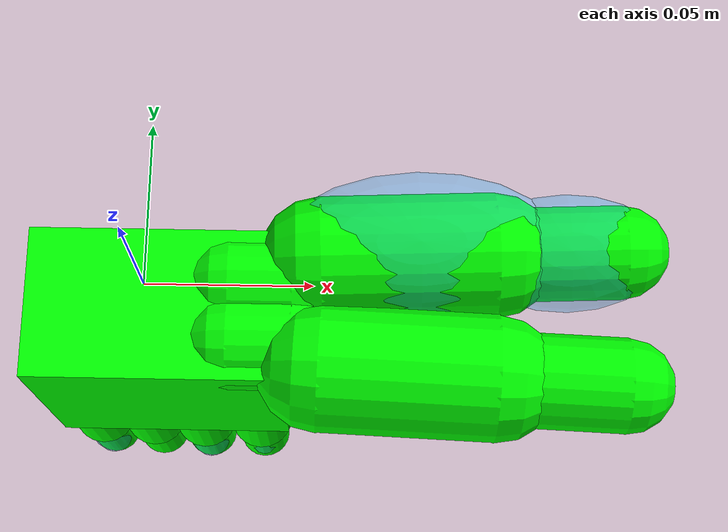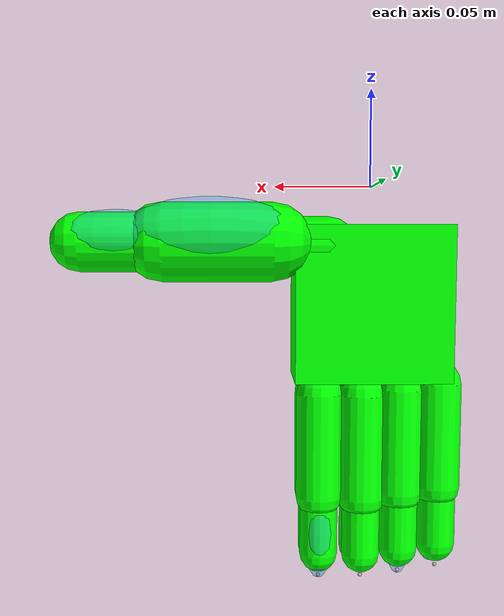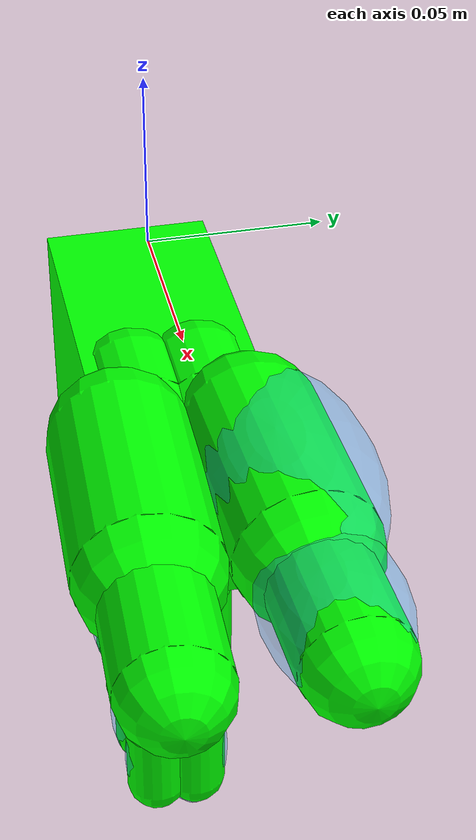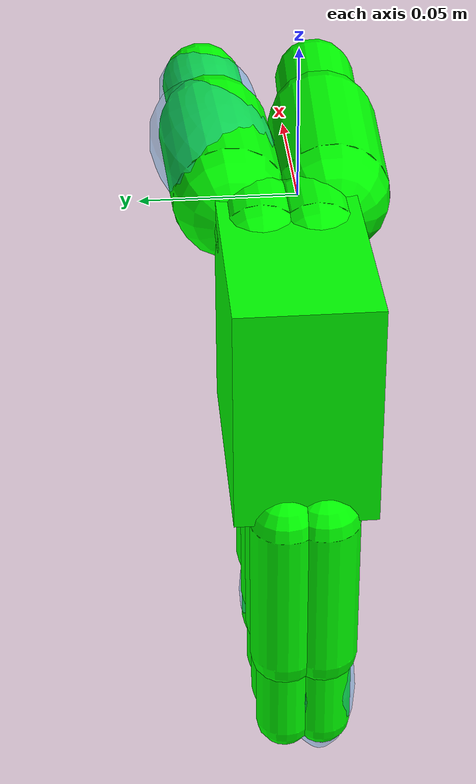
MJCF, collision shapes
<mujoco model="taco_pour_bowl_plate_20230927_017">
  <compiler angle="radian" meshdir="/data_all/zzx/3.2RL/models/taco_xhand/assets" />
  <default>
    <joint armature="1" />
    <geom contype="0" conaffinity="0" condim="1" density="800" />
    <site group="3" rgba="1 0 0 1" />
    <general biastype="affine" gainprm="300" biasprm="0 -300 1" />
  </default>
  <asset>
    <texture type="skybox" colorspace="auto" builtin="gradient" rgb1="1 1 1" rgb2="1 1 1" width="512" height="3072" />
    <texture type="2d" colorspace="auto" name="right_groundplane" builtin="checker" mark="edge" rgb1="0.2 0.3 0.4" rgb2="0.1 0.2 0.3" markrgb="0.8 0.8 0.8" width="300" height="300" />
    <texture type="skybox" colorspace="auto" builtin="gradient" rgb1="0.3 0.5 0.7" rgb2="0 0 0" width="512" height="3072" />
    <texture type="2d" colorspace="auto" name="left_groundplane" builtin="checker" mark="edge" rgb1="0.2 0.3 0.4" rgb2="0.1 0.2 0.3" markrgb="0.8 0.8 0.8" width="300" height="300" />
    <texture type="cube" colorspace="auto" name="skybox" builtin="gradient" rgb1="0.3 0.5 0.7" rgb2="0 0 0" width="512" height="3072" />
    <texture type="cube" colorspace="auto" name="groundplane" builtin="checker" mark="edge" rgb1="0.2 0.3 0.4" rgb2="0.1 0.2 0.3" markrgb="0.8 0.8 0.8" width="300" height="1800" />
    <material name="right_groundplane" texture="right_groundplane" texuniform="true" texrepeat="5 5" reflectance="0.2" />
    <material name="left_groundplane" texture="left_groundplane" texuniform="true" texrepeat="5 5" reflectance="0.2" />
    <material name="groundplane" texuniform="true" texrepeat="5 5" reflectance="0.2" />
    <mesh name="right_hand_link" content_type="model/stl" file="robots/xhand_pour_20230927_017/assets/right_hand_link.STL" />
    <mesh name="right_hand_thumb_bend_link" content_type="model/stl" file="robots/xhand_pour_20230927_017/assets/right_hand_thumb_bend_link.STL" />
    <mesh name="right_hand_thumb_rota_link1" content_type="model/stl" file="robots/xhand_pour_20230927_017/assets/right_hand_thumb_rota_link1.STL" />
    <mesh name="right_hand_thumb_rota_link2" content_type="model/stl" file="robots/xhand_pour_20230927_017/assets/right_hand_thumb_rota_link2.STL" />
    <mesh name="right_hand_index_bend_link" content_type="model/stl" file="robots/xhand_pour_20230927_017/assets/right_hand_index_bend_link.STL" />
    <mesh name="right_hand_index_rota_link1" content_type="model/stl" file="robots/xhand_pour_20230927_017/assets/right_hand_index_rota_link1.STL" />
    <mesh name="right_hand_index_rota_link2" content_type="model/stl" file="robots/xhand_pour_20230927_017/assets/right_hand_index_rota_link2.STL" />
    <mesh name="right_hand_mid_link1" content_type="model/stl" file="robots/xhand_pour_20230927_017/assets/right_hand_mid_link1.STL" />
    <mesh name="right_hand_mid_link2" content_type="model/stl" file="robots/xhand_pour_20230927_017/assets/right_hand_mid_link2.STL" />
    <mesh name="right_hand_ring_link1" content_type="model/stl" file="robots/xhand_pour_20230927_017/assets/right_hand_ring_link1.STL" />
    <mesh name="right_hand_ring_link2" content_type="model/stl" file="robots/xhand_pour_20230927_017/assets/right_hand_ring_link2.STL" />
    <mesh name="right_hand_pinky_link1" content_type="model/stl" file="robots/xhand_pour_20230927_017/assets/right_hand_pinky_link1.STL" />
    <mesh name="right_hand_pinky_link2" content_type="model/stl" file="robots/xhand_pour_20230927_017/assets/right_hand_pinky_link2.STL" />
    <mesh name="left_hand_link" content_type="model/stl" file="robots/xhand_pour_20230927_017/assets/left_hand_link.STL" />
    <mesh name="left_hand_thumb_bend_link" content_type="model/stl" file="robots/xhand_pour_20230927_017/assets/left_hand_thumb_bend_link.STL" />
    <mesh name="left_hand_thumb_rota_link1" content_type="model/stl" file="robots/xhand_pour_20230927_017/assets/left_hand_thumb_rota_link1.STL" />
    <mesh name="left_hand_thumb_rota_link2" content_type="model/stl" file="robots/xhand_pour_20230927_017/assets/left_hand_thumb_rota_link2.STL" />
    <mesh name="left_hand_index_bend_link" content_type="model/stl" file="robots/xhand_pour_20230927_017/assets/left_hand_index_bend_link.STL" />
    <mesh name="left_hand_index_rota_link1" content_type="model/stl" file="robots/xhand_pour_20230927_017/assets/left_hand_index_rota_link1.STL" />
    <mesh name="left_hand_index_rota_link2" content_type="model/stl" file="robots/xhand_pour_20230927_017/assets/left_hand_index_rota_link2.STL" />
    <mesh name="left_hand_mid_link1" content_type="model/stl" file="robots/xhand_pour_20230927_017/assets/left_hand_mid_link1.STL" />
    <mesh name="left_hand_mid_link2" content_type="model/stl" file="robots/xhand_pour_20230927_017/assets/left_hand_mid_link2.STL" />
    <mesh name="left_hand_ring_link1" content_type="model/stl" file="robots/xhand_pour_20230927_017/assets/left_hand_ring_link1.STL" />
    <mesh name="left_hand_ring_link2" content_type="model/stl" file="robots/xhand_pour_20230927_017/assets/left_hand_ring_link2.STL" />
    <mesh name="left_hand_pinky_link1" content_type="model/stl" file="robots/xhand_pour_20230927_017/assets/left_hand_pinky_link1.STL" />
    <mesh name="left_hand_pinky_link2" content_type="model/stl" file="robots/xhand_pour_20230927_017/assets/left_hand_pinky_link2.STL" />
    <mesh name="right_visual" file="objects/022/visual.obj" scale="0.01 0.01 0.01" />
    <mesh name="right_0" file="objects/022/convex_m/0.obj" />
    <mesh name="right_1" file="objects/022/convex_m/1.obj" />
    <mesh name="right_2" file="objects/022/convex_m/2.obj" />
    <mesh name="right_3" file="objects/022/convex_m/3.obj" />
    <mesh name="right_4" file="objects/022/convex_m/4.obj" />
    <mesh name="right_5" file="objects/022/convex_m/5.obj" />
    <mesh name="right_6" file="objects/022/convex_m/6.obj" />
    <mesh name="right_7" file="objects/022/convex_m/7.obj" />
    <mesh name="right_8" file="objects/022/convex_m/8.obj" />
    <mesh name="right_9" file="objects/022/convex_m/9.obj" />
    <mesh name="right_10" file="objects/022/convex_m/10.obj" />
    <mesh name="right_11" file="objects/022/convex_m/11.obj" />
    <mesh name="right_12" file="objects/022/convex_m/12.obj" />
    <mesh name="right_13" file="objects/022/convex_m/13.obj" />
    <mesh name="right_14" file="objects/022/convex_m/14.obj" />
    <mesh name="right_15" file="objects/022/convex_m/15.obj" />
    <mesh name="right_16" file="objects/022/convex_m/16.obj" />
    <mesh name="right_17" file="objects/022/convex_m/17.obj" />
    <mesh name="right_18" file="objects/022/convex_m/18.obj" />
    <mesh name="right_19" file="objects/022/convex_m/19.obj" />
    <mesh name="right_20" file="objects/022/convex_m/20.obj" />
    <mesh name="right_21" file="objects/022/convex_m/21.obj" />
    <mesh name="right_22" file="objects/022/convex_m/22.obj" />
    <mesh name="right_23" file="objects/022/convex_m/23.obj" />
    <mesh name="right_24" file="objects/022/convex_m/24.obj" />
    <mesh name="right_25" file="objects/022/convex_m/25.obj" />
    <mesh name="right_26" file="objects/022/convex_m/26.obj" />
    <mesh name="right_27" file="objects/022/convex_m/27.obj" />
    <mesh name="right_28" file="objects/022/convex_m/28.obj" />
    <mesh name="right_29" file="objects/022/convex_m/29.obj" />
    <mesh name="right_30" file="objects/022/convex_m/30.obj" />
    <mesh name="right_31" file="objects/022/convex_m/31.obj" />
    <mesh name="left_visual" file="objects/135/visual.obj" scale="0.01 0.01 0.01" />
    <mesh name="left_0" file="objects/135/convex_m/0.obj" />
    <mesh name="left_1" file="objects/135/convex_m/1.obj" />
    <mesh name="left_2" file="objects/135/convex_m/2.obj" />
    <mesh name="left_3" file="objects/135/convex_m/3.obj" />
    <mesh name="left_4" file="objects/135/convex_m/4.obj" />
    <mesh name="left_5" file="objects/135/convex_m/5.obj" />
    <mesh name="left_6" file="objects/135/convex_m/6.obj" />
    <mesh name="left_7" file="objects/135/convex_m/7.obj" />
    <mesh name="left_8" file="objects/135/convex_m/8.obj" />
    <mesh name="left_9" file="objects/135/convex_m/9.obj" />
    <mesh name="left_10" file="objects/135/convex_m/10.obj" />
    <mesh name="left_11" file="objects/135/convex_m/11.obj" />
    <mesh name="left_12" file="objects/135/convex_m/12.obj" />
    <mesh name="left_13" file="objects/135/convex_m/13.obj" />
    <mesh name="left_14" file="objects/135/convex_m/14.obj" />
    <mesh name="left_15" file="objects/135/convex_m/15.obj" />
    <mesh name="left_16" file="objects/135/convex_m/16.obj" />
    <mesh name="left_17" file="objects/135/convex_m/17.obj" />
    <mesh name="left_18" file="objects/135/convex_m/18.obj" />
    <mesh name="left_19" file="objects/135/convex_m/19.obj" />
    <mesh name="left_20" file="objects/135/convex_m/20.obj" />
    <mesh name="left_21" file="objects/135/convex_m/21.obj" />
    <mesh name="left_22" file="objects/135/convex_m/22.obj" />
    <mesh name="left_23" file="objects/135/convex_m/23.obj" />
    <mesh name="left_24" file="objects/135/convex_m/24.obj" />
    <mesh name="left_25" file="objects/135/convex_m/25.obj" />
    <mesh name="left_26" file="objects/135/convex_m/26.obj" />
    <mesh name="left_27" file="objects/135/convex_m/27.obj" />
    <mesh name="left_28" file="objects/135/convex_m/28.obj" />
    <mesh name="left_29" file="objects/135/convex_m/29.obj" />
    <mesh name="left_30" file="objects/135/convex_m/30.obj" />
    <mesh name="left_31" file="objects/135/convex_m/31.obj" />
    <mesh name="left_palm_thumb_guard_palm_mesh_08167" file="../../../runs/taco_pour_left_palm_thumb_local_surface_guard_v1/assets/palm/face_08167.obj" />
    <mesh name="left_palm_thumb_guard_palm_mesh_08168" file="../../../runs/taco_pour_left_palm_thumb_local_surface_guard_v1/assets/palm/face_08168.obj" />
    <mesh name="left_palm_thumb_guard_palm_mesh_08179" file="../../../runs/taco_pour_left_palm_thumb_local_surface_guard_v1/assets/palm/face_08179.obj" />
    <mesh name="left_palm_thumb_guard_palm_mesh_08180" file="../../../runs/taco_pour_left_palm_thumb_local_surface_guard_v1/assets/palm/face_08180.obj" />
    <mesh name="left_palm_thumb_guard_palm_mesh_08195" file="../../../runs/taco_pour_left_palm_thumb_local_surface_guard_v1/assets/palm/face_08195.obj" />
    <mesh name="left_palm_thumb_guard_palm_mesh_08207" file="../../../runs/taco_pour_left_palm_thumb_local_surface_guard_v1/assets/palm/face_08207.obj" />
    <mesh name="left_palm_thumb_guard_palm_mesh_08208" file="../../../runs/taco_pour_left_palm_thumb_local_surface_guard_v1/assets/palm/face_08208.obj" />
    <mesh name="left_palm_thumb_guard_palm_mesh_08223" file="../../../runs/taco_pour_left_palm_thumb_local_surface_guard_v1/assets/palm/face_08223.obj" />
    <mesh name="left_palm_thumb_guard_palm_mesh_08224" file="../../../runs/taco_pour_left_palm_thumb_local_surface_guard_v1/assets/palm/face_08224.obj" />
    <mesh name="left_palm_thumb_guard_palm_mesh_11726" file="../../../runs/taco_pour_left_palm_thumb_local_surface_guard_v1/assets/palm/face_11726.obj" />
    <mesh name="left_palm_thumb_guard_palm_mesh_11747" file="../../../runs/taco_pour_left_palm_thumb_local_surface_guard_v1/assets/palm/face_11747.obj" />
    <mesh name="left_palm_thumb_guard_palm_mesh_11748" file="../../../runs/taco_pour_left_palm_thumb_local_surface_guard_v1/assets/palm/face_11748.obj" />
    <mesh name="left_palm_thumb_guard_palm_mesh_11749" file="../../../runs/taco_pour_left_palm_thumb_local_surface_guard_v1/assets/palm/face_11749.obj" />
    <mesh name="left_palm_thumb_guard_palm_mesh_11776" file="../../../runs/taco_pour_left_palm_thumb_local_surface_guard_v1/assets/palm/face_11776.obj" />
    <mesh name="left_palm_thumb_guard_palm_mesh_11779" file="../../../runs/taco_pour_left_palm_thumb_local_surface_guard_v1/assets/palm/face_11779.obj" />
    <mesh name="left_palm_thumb_guard_palm_mesh_11780" file="../../../runs/taco_pour_left_palm_thumb_local_surface_guard_v1/assets/palm/face_11780.obj" />
    <mesh name="left_palm_thumb_guard_palm_mesh_11781" file="../../../runs/taco_pour_left_palm_thumb_local_surface_guard_v1/assets/palm/face_11781.obj" />
    <mesh name="left_palm_thumb_guard_palm_mesh_11782" file="../../../runs/taco_pour_left_palm_thumb_local_surface_guard_v1/assets/palm/face_11782.obj" />
    <mesh name="left_palm_thumb_guard_palm_mesh_11783" file="../../../runs/taco_pour_left_palm_thumb_local_surface_guard_v1/assets/palm/face_11783.obj" />
    <mesh name="left_palm_thumb_guard_palm_mesh_11789" file="../../../runs/taco_pour_left_palm_thumb_local_surface_guard_v1/assets/palm/face_11789.obj" />
    <mesh name="left_palm_thumb_guard_palm_mesh_11790" file="../../../runs/taco_pour_left_palm_thumb_local_surface_guard_v1/assets/palm/face_11790.obj" />
    <mesh name="left_palm_thumb_guard_palm_mesh_11791" file="../../../runs/taco_pour_left_palm_thumb_local_surface_guard_v1/assets/palm/face_11791.obj" />
    <mesh name="left_palm_thumb_guard_palm_mesh_11792" file="../../../runs/taco_pour_left_palm_thumb_local_surface_guard_v1/assets/palm/face_11792.obj" />
    <mesh name="left_palm_thumb_guard_palm_mesh_11793" file="../../../runs/taco_pour_left_palm_thumb_local_surface_guard_v1/assets/palm/face_11793.obj" />
    <mesh name="left_palm_thumb_guard_palm_mesh_11819" file="../../../runs/taco_pour_left_palm_thumb_local_surface_guard_v1/assets/palm/face_11819.obj" />
    <mesh name="left_palm_thumb_guard_palm_mesh_11830" file="../../../runs/taco_pour_left_palm_thumb_local_surface_guard_v1/assets/palm/face_11830.obj" />
    <mesh name="left_palm_thumb_guard_palm_mesh_11854" file="../../../runs/taco_pour_left_palm_thumb_local_surface_guard_v1/assets/palm/face_11854.obj" />
    <mesh name="left_palm_thumb_guard_palm_mesh_11855" file="../../../runs/taco_pour_left_palm_thumb_local_surface_guard_v1/assets/palm/face_11855.obj" />
    <mesh name="left_palm_thumb_guard_palm_mesh_15597" file="../../../runs/taco_pour_left_palm_thumb_local_surface_guard_v1/assets/palm/face_15597.obj" />
    <mesh name="left_palm_thumb_guard_palm_mesh_15598" file="../../../runs/taco_pour_left_palm_thumb_local_surface_guard_v1/assets/palm/face_15598.obj" />
    <mesh name="left_palm_thumb_guard_palm_mesh_15599" file="../../../runs/taco_pour_left_palm_thumb_local_surface_guard_v1/assets/palm/face_15599.obj" />
    <mesh name="left_palm_thumb_guard_palm_mesh_15600" file="../../../runs/taco_pour_left_palm_thumb_local_surface_guard_v1/assets/palm/face_15600.obj" />
    <mesh name="left_palm_thumb_guard_palm_mesh_15601" file="../../../runs/taco_pour_left_palm_thumb_local_surface_guard_v1/assets/palm/face_15601.obj" />
    <mesh name="left_palm_thumb_guard_palm_mesh_15602" file="../../../runs/taco_pour_left_palm_thumb_local_surface_guard_v1/assets/palm/face_15602.obj" />
    <mesh name="left_palm_thumb_guard_palm_mesh_15603" file="../../../runs/taco_pour_left_palm_thumb_local_surface_guard_v1/assets/palm/face_15603.obj" />
    <mesh name="left_palm_thumb_guard_palm_mesh_15604" file="../../../runs/taco_pour_left_palm_thumb_local_surface_guard_v1/assets/palm/face_15604.obj" />
    <mesh name="left_palm_thumb_guard_palm_mesh_15605" file="../../../runs/taco_pour_left_palm_thumb_local_surface_guard_v1/assets/palm/face_15605.obj" />
    <mesh name="left_palm_thumb_guard_palm_mesh_15606" file="../../../runs/taco_pour_left_palm_thumb_local_surface_guard_v1/assets/palm/face_15606.obj" />
    <mesh name="left_palm_thumb_guard_palm_mesh_15607" file="../../../runs/taco_pour_left_palm_thumb_local_surface_guard_v1/assets/palm/face_15607.obj" />
    <mesh name="left_palm_thumb_guard_palm_mesh_15613" file="../../../runs/taco_pour_left_palm_thumb_local_surface_guard_v1/assets/palm/face_15613.obj" />
    <mesh name="left_palm_thumb_guard_palm_mesh_15614" file="../../../runs/taco_pour_left_palm_thumb_local_surface_guard_v1/assets/palm/face_15614.obj" />
    <mesh name="left_palm_thumb_guard_palm_mesh_15615" file="../../../runs/taco_pour_left_palm_thumb_local_surface_guard_v1/assets/palm/face_15615.obj" />
    <mesh name="left_palm_thumb_guard_palm_mesh_15625" file="../../../runs/taco_pour_left_palm_thumb_local_surface_guard_v1/assets/palm/face_15625.obj" />
    <mesh name="left_palm_thumb_guard_palm_mesh_15639" file="../../../runs/taco_pour_left_palm_thumb_local_surface_guard_v1/assets/palm/face_15639.obj" />
    <mesh name="left_palm_thumb_guard_palm_mesh_15640" file="../../../runs/taco_pour_left_palm_thumb_local_surface_guard_v1/assets/palm/face_15640.obj" />
    <mesh name="left_palm_thumb_guard_thumb_mesh_10971" file="../../../runs/taco_pour_left_palm_thumb_local_surface_guard_v1/assets/thumb/face_10971.obj" />
    <mesh name="left_palm_thumb_guard_thumb_mesh_10980" file="../../../runs/taco_pour_left_palm_thumb_local_surface_guard_v1/assets/thumb/face_10980.obj" />
    <mesh name="left_palm_thumb_guard_thumb_mesh_10981" file="../../../runs/taco_pour_left_palm_thumb_local_surface_guard_v1/assets/thumb/face_10981.obj" />
    <mesh name="left_palm_thumb_guard_thumb_mesh_10982" file="../../../runs/taco_pour_left_palm_thumb_local_surface_guard_v1/assets/thumb/face_10982.obj" />
    <mesh name="left_palm_thumb_guard_thumb_mesh_10983" file="../../../runs/taco_pour_left_palm_thumb_local_surface_guard_v1/assets/thumb/face_10983.obj" />
    <mesh name="left_palm_thumb_guard_thumb_mesh_10985" file="../../../runs/taco_pour_left_palm_thumb_local_surface_guard_v1/assets/thumb/face_10985.obj" />
    <mesh name="left_palm_thumb_guard_thumb_mesh_10986" file="../../../runs/taco_pour_left_palm_thumb_local_surface_guard_v1/assets/thumb/face_10986.obj" />
    <mesh name="left_palm_thumb_guard_thumb_mesh_10987" file="../../../runs/taco_pour_left_palm_thumb_local_surface_guard_v1/assets/thumb/face_10987.obj" />
    <mesh name="left_palm_thumb_guard_thumb_mesh_10988" file="../../../runs/taco_pour_left_palm_thumb_local_surface_guard_v1/assets/thumb/face_10988.obj" />
    <mesh name="left_palm_thumb_guard_thumb_mesh_10989" file="../../../runs/taco_pour_left_palm_thumb_local_surface_guard_v1/assets/thumb/face_10989.obj" />
    <mesh name="left_palm_thumb_guard_thumb_mesh_10990" file="../../../runs/taco_pour_left_palm_thumb_local_surface_guard_v1/assets/thumb/face_10990.obj" />
    <mesh name="left_palm_thumb_guard_thumb_mesh_10991" file="../../../runs/taco_pour_left_palm_thumb_local_surface_guard_v1/assets/thumb/face_10991.obj" />
    <mesh name="left_palm_thumb_guard_thumb_mesh_10992" file="../../../runs/taco_pour_left_palm_thumb_local_surface_guard_v1/assets/thumb/face_10992.obj" />
    <mesh name="left_palm_thumb_guard_thumb_mesh_10993" file="../../../runs/taco_pour_left_palm_thumb_local_surface_guard_v1/assets/thumb/face_10993.obj" />
    <mesh name="left_palm_thumb_guard_thumb_mesh_10994" file="../../../runs/taco_pour_left_palm_thumb_local_surface_guard_v1/assets/thumb/face_10994.obj" />
    <mesh name="left_palm_thumb_guard_thumb_mesh_10995" file="../../../runs/taco_pour_left_palm_thumb_local_surface_guard_v1/assets/thumb/face_10995.obj" />
    <mesh name="left_palm_thumb_guard_thumb_mesh_10996" file="../../../runs/taco_pour_left_palm_thumb_local_surface_guard_v1/assets/thumb/face_10996.obj" />
    <mesh name="left_palm_thumb_guard_thumb_mesh_11007" file="../../../runs/taco_pour_left_palm_thumb_local_surface_guard_v1/assets/thumb/face_11007.obj" />
    <mesh name="left_palm_thumb_guard_thumb_mesh_11008" file="../../../runs/taco_pour_left_palm_thumb_local_surface_guard_v1/assets/thumb/face_11008.obj" />
    <mesh name="left_palm_thumb_guard_thumb_mesh_11009" file="../../../runs/taco_pour_left_palm_thumb_local_surface_guard_v1/assets/thumb/face_11009.obj" />
    <mesh name="left_palm_thumb_guard_thumb_mesh_11011" file="../../../runs/taco_pour_left_palm_thumb_local_surface_guard_v1/assets/thumb/face_11011.obj" />
    <mesh name="left_palm_thumb_guard_thumb_mesh_11012" file="../../../runs/taco_pour_left_palm_thumb_local_surface_guard_v1/assets/thumb/face_11012.obj" />
    <mesh name="left_palm_thumb_guard_thumb_mesh_11013" file="../../../runs/taco_pour_left_palm_thumb_local_surface_guard_v1/assets/thumb/face_11013.obj" />
    <mesh name="left_palm_thumb_guard_thumb_mesh_11219" file="../../../runs/taco_pour_left_palm_thumb_local_surface_guard_v1/assets/thumb/face_11219.obj" />
    <mesh name="left_palm_thumb_guard_thumb_mesh_11220" file="../../../runs/taco_pour_left_palm_thumb_local_surface_guard_v1/assets/thumb/face_11220.obj" />
    <mesh name="left_palm_thumb_guard_thumb_mesh_11221" file="../../../runs/taco_pour_left_palm_thumb_local_surface_guard_v1/assets/thumb/face_11221.obj" />
    <mesh name="left_palm_thumb_guard_thumb_mesh_11222" file="../../../runs/taco_pour_left_palm_thumb_local_surface_guard_v1/assets/thumb/face_11222.obj" />
    <mesh name="left_palm_thumb_guard_thumb_mesh_11223" file="../../../runs/taco_pour_left_palm_thumb_local_surface_guard_v1/assets/thumb/face_11223.obj" />
    <mesh name="left_palm_thumb_guard_thumb_mesh_11227" file="../../../runs/taco_pour_left_palm_thumb_local_surface_guard_v1/assets/thumb/face_11227.obj" />
    <mesh name="left_palm_thumb_guard_thumb_mesh_11228" file="../../../runs/taco_pour_left_palm_thumb_local_surface_guard_v1/assets/thumb/face_11228.obj" />
    <mesh name="left_palm_thumb_guard_thumb_mesh_11229" file="../../../runs/taco_pour_left_palm_thumb_local_surface_guard_v1/assets/thumb/face_11229.obj" />
    <mesh name="left_palm_thumb_guard_thumb_mesh_11230" file="../../../runs/taco_pour_left_palm_thumb_local_surface_guard_v1/assets/thumb/face_11230.obj" />
    <mesh name="left_palm_thumb_guard_thumb_mesh_11231" file="../../../runs/taco_pour_left_palm_thumb_local_surface_guard_v1/assets/thumb/face_11231.obj" />
    <mesh name="left_palm_thumb_guard_thumb_mesh_11232" file="../../../runs/taco_pour_left_palm_thumb_local_surface_guard_v1/assets/thumb/face_11232.obj" />
    <mesh name="left_palm_thumb_guard_thumb_mesh_11244" file="../../../runs/taco_pour_left_palm_thumb_local_surface_guard_v1/assets/thumb/face_11244.obj" />
    <mesh name="left_palm_thumb_guard_thumb_mesh_11245" file="../../../runs/taco_pour_left_palm_thumb_local_surface_guard_v1/assets/thumb/face_11245.obj" />
    <mesh name="left_palm_thumb_guard_thumb_mesh_11246" file="../../../runs/taco_pour_left_palm_thumb_local_surface_guard_v1/assets/thumb/face_11246.obj" />
    <mesh name="left_palm_thumb_guard_thumb_mesh_11286" file="../../../runs/taco_pour_left_palm_thumb_local_surface_guard_v1/assets/thumb/face_11286.obj" />
    <mesh name="left_palm_thumb_guard_thumb_mesh_11287" file="../../../runs/taco_pour_left_palm_thumb_local_surface_guard_v1/assets/thumb/face_11287.obj" />
    <mesh name="left_palm_thumb_guard_thumb_mesh_11288" file="../../../runs/taco_pour_left_palm_thumb_local_surface_guard_v1/assets/thumb/face_11288.obj" />
    <mesh name="left_palm_thumb_guard_thumb_mesh_11289" file="../../../runs/taco_pour_left_palm_thumb_local_surface_guard_v1/assets/thumb/face_11289.obj" />
    <mesh name="left_palm_thumb_guard_thumb_mesh_11290" file="../../../runs/taco_pour_left_palm_thumb_local_surface_guard_v1/assets/thumb/face_11290.obj" />
    <mesh name="left_palm_thumb_guard_thumb_mesh_11291" file="../../../runs/taco_pour_left_palm_thumb_local_surface_guard_v1/assets/thumb/face_11291.obj" />
    <mesh name="left_palm_thumb_guard_thumb_mesh_11292" file="../../../runs/taco_pour_left_palm_thumb_local_surface_guard_v1/assets/thumb/face_11292.obj" />
    <mesh name="left_palm_thumb_guard_thumb_mesh_11293" file="../../../runs/taco_pour_left_palm_thumb_local_surface_guard_v1/assets/thumb/face_11293.obj" />
    <mesh name="left_palm_thumb_guard_thumb_mesh_11294" file="../../../runs/taco_pour_left_palm_thumb_local_surface_guard_v1/assets/thumb/face_11294.obj" />
    <mesh name="left_palm_thumb_guard_thumb_mesh_11295" file="../../../runs/taco_pour_left_palm_thumb_local_surface_guard_v1/assets/thumb/face_11295.obj" />
    <mesh name="left_palm_thumb_guard_thumb_mesh_11296" file="../../../runs/taco_pour_left_palm_thumb_local_surface_guard_v1/assets/thumb/face_11296.obj" />
    <mesh name="left_palm_thumb_guard_thumb_mesh_11297" file="../../../runs/taco_pour_left_palm_thumb_local_surface_guard_v1/assets/thumb/face_11297.obj" />
    <mesh name="left_palm_thumb_guard_thumb_mesh_11306" file="../../../runs/taco_pour_left_palm_thumb_local_surface_guard_v1/assets/thumb/face_11306.obj" />
    <mesh name="left_palm_thumb_guard_thumb_mesh_11307" file="../../../runs/taco_pour_left_palm_thumb_local_surface_guard_v1/assets/thumb/face_11307.obj" />
    <mesh name="left_palm_thumb_guard_thumb_mesh_11308" file="../../../runs/taco_pour_left_palm_thumb_local_surface_guard_v1/assets/thumb/face_11308.obj" />
    <mesh name="left_palm_thumb_guard_thumb_mesh_11309" file="../../../runs/taco_pour_left_palm_thumb_local_surface_guard_v1/assets/thumb/face_11309.obj" />
    <mesh name="left_palm_thumb_guard_thumb_mesh_11310" file="../../../runs/taco_pour_left_palm_thumb_local_surface_guard_v1/assets/thumb/face_11310.obj" />
    <mesh name="left_palm_thumb_guard_thumb_mesh_11311" file="../../../runs/taco_pour_left_palm_thumb_local_surface_guard_v1/assets/thumb/face_11311.obj" />
    <mesh name="left_palm_thumb_guard_thumb_mesh_11312" file="../../../runs/taco_pour_left_palm_thumb_local_surface_guard_v1/assets/thumb/face_11312.obj" />
    <mesh name="left_palm_thumb_guard_thumb_mesh_11313" file="../../../runs/taco_pour_left_palm_thumb_local_surface_guard_v1/assets/thumb/face_11313.obj" />
    <mesh name="left_palm_thumb_guard_thumb_mesh_11314" file="../../../runs/taco_pour_left_palm_thumb_local_surface_guard_v1/assets/thumb/face_11314.obj" />
    <mesh name="left_palm_thumb_guard_thumb_mesh_11315" file="../../../runs/taco_pour_left_palm_thumb_local_surface_guard_v1/assets/thumb/face_11315.obj" />
    <mesh name="left_palm_thumb_guard_thumb_mesh_11316" file="../../../runs/taco_pour_left_palm_thumb_local_surface_guard_v1/assets/thumb/face_11316.obj" />
    <mesh name="left_palm_thumb_guard_thumb_mesh_11317" file="../../../runs/taco_pour_left_palm_thumb_local_surface_guard_v1/assets/thumb/face_11317.obj" />
    <mesh name="left_palm_thumb_guard_thumb_mesh_11318" file="../../../runs/taco_pour_left_palm_thumb_local_surface_guard_v1/assets/thumb/face_11318.obj" />
  </asset>
  <worldbody>
    <geom name="floor" size="0 0 0.05" type="plane" material="right_groundplane" contype="0" conaffinity="0" condim="3" friction="1 0.1 0" pos="0 0 0.72" />
    <camera name="front" pos="0.031 0.941 0.844" quat="0.0150738 0.00673439 0.407848 0.912901" mode="fixed" />
    <body name="R_forearm_ty_link">
      <inertial pos="0 0 0" mass="0.1" diaginertia="0.01 0.01 0.01" />
      <joint name="R_forearm_tx_link_joint" pos="0 0 0" axis="1 0 0" type="slide" range="-5 5" />
      <body name="R_forearm_tz_link">
        <inertial pos="0 0 0" mass="0.1" diaginertia="0.01 0.01 0.01" />
        <joint name="R_forearm_ty_link_joint" pos="0 0 0" axis="0 1 0" type="slide" range="-5 5" />
        <body name="R_forearm_roll_link">
          <inertial pos="0 0 0" mass="0.1" diaginertia="0.01 0.01 0.01" />
          <joint name="R_forearm_tz_link_joint" pos="0 0 0" axis="0 0 1" type="slide" range="-5 5" />
          <body name="R_forearm_pitch_link">
            <inertial pos="0 0 0" mass="0.1" diaginertia="0.01 0.01 0.01" />
            <joint name="R_forearm_roll_link_joint" pos="0 0 0" axis="0 0 1" range="-6.2 6.2" />
            <body name="R_forearm_yaw_link">
              <inertial pos="0 0 0" mass="0.1" diaginertia="0.01 0.01 0.01" />
              <joint name="R_forearm_pitch_link_joint" pos="0 0 0" axis="1 0 0" range="-6.2 6.2" />
              <body name="right_hand_link">
                <inertial pos="-0.0071397 0.00342244 -0.0584807" quat="0.688453 0.098553 0.0886255 0.713068" mass="0.530025" diaginertia="0.00067782 0.000491189 0.000335821" />
                <joint name="R_forearm_yaw_link_joint" pos="0 0 0" axis="0 -1 0" range="-6.2 6.2" />
                <geom name="right_hand_link_visual" type="mesh" group="1" density="0" rgba="0.792157 0.819608 0.933333 1" mesh="right_hand_link" contype="0" conaffinity="0" />
                <geom name="collision_hand_right_palm_0" size="0.04 0.024 0.04" pos="0 0 -0.06" type="box" group="3" rgba="0 1 0 1" contype="0" conaffinity="0" condim="3" friction="1 0.1 0" />
                <geom name="collision_hand_right_palm_index_root_negative_guard" size="0.000929064511788" pos="0.0133624176979 0.00650000011921 -0.0615201568604" type="sphere" group="3" density="0" rgba="1 0.75 0 1" contype="0" conaffinity="0" condim="3" friction="1 0.1 0" />
                <geom name="collision_hand_right_palm_index_root_positive_guard" size="0.00150030451896" pos="0.0374132442474 -0.0005 -0.0731002693176" type="sphere" group="3" density="0" rgba="1 0.75 0 1" contype="0" conaffinity="0" condim="3" friction="1 0.1 0" />
                <site name="right_palm" pos="0 0 0" quat="0 0.707107 0.707107 0" size="0.01 0.02 0.03" type="box" />
                <body name="right_hand_thumb_bend_link" pos="0.0228 0.0095 -0.0305">
                  <inertial pos="0.0145291 -0.000901303 -0.000127926" quat="0.0288921 0.68936 0.0166971 0.72365" mass="0.00985529" diaginertia="1.30647e-06 1.29142e-06 5.40953e-07" />
                  <joint name="right_hand_thumb_bend_joint" pos="0 0 0" axis="0 0 1" range="0 1.83" />
                  <geom name="right_thumb_bend_visual" type="mesh" group="1" density="0" rgba="0.890196 0.890196 0.913725 1" mesh="right_hand_thumb_bend_link" contype="0" conaffinity="0" />
                  <geom name="collision_hand_right_thumb_2" size="0.015 0.01" pos="0.01 0 0" quat="0.707107 0 -0.707107 0" type="capsule" group="3" rgba="0 1 0 1" contype="0" conaffinity="0" condim="3" friction="1 0.1 0" />
                  <body name="right_hand_thumb_rota_link1" pos="0.028599 0.0083177 0.00178" quat="0.99124 0.130499 0.00265603 0.0201745">
                    <inertial pos="0.0279237 -0.000127603 -0.000272577" quat="-0.0989965 0.703671 0.0850598 0.698435" mass="0.153265" diaginertia="5.62327e-05 4.89801e-05 2.23924e-05" />
                    <joint name="right_hand_thumb_rota_joint1" pos="0 0 0" axis="0 1 0" range="-1.05 1.57" />
                    <geom name="right_thumb_rota1_visual" type="mesh" group="1" density="0" rgba="1 1 1 1" mesh="right_hand_thumb_rota_link1" contype="0" conaffinity="0" />
                    <geom name="collision_hand_right_thumb_1" size="0.02 0.0275" pos="0.0275 0 0" quat="0.707107 0 -0.707107 0" type="capsule" group="3" rgba="0 1 0 1" contype="0" conaffinity="0" condim="3" friction="1 0.1 0" />
                    <body name="right_hand_thumb_rota_link2" pos="0.0553 0 0">
                      <inertial pos="0.0224697 -0.000691342 0.00302232" quat="-0.0604029 0.715612 0.0198067 0.695599" mass="0.0374004" diaginertia="9.5465e-06 8.27017e-06 3.92137e-06" />
                      <joint name="right_hand_thumb_rota_joint2" pos="0 0 0" axis="0 1 0" range="-0.175 1.83" />
                      <geom name="right_thumb_rota2_visual" type="mesh" group="1" density="0" rgba="0.792157 0.819608 0.933333 1" mesh="right_hand_thumb_rota_link2" contype="0" conaffinity="0" />
                      <geom name="collision_hand_right_thumb_0" size="0.015 0.02" pos="0.02 0 0" quat="0.707107 0 -0.707107 0" type="capsule" group="3" rgba="0 1 0 1" contype="0" conaffinity="0" condim="3" friction="1 0.1 0" />
                      <geom size="0.001" pos="0.0504025 0 0" group="1" density="0" rgba="0.698039 0.698039 0.698039 1" contype="0" conaffinity="0" />
                      <site name="right_thumb_tip" pos="0.04 0 -0.012" />
                      <site name="track_hand_right_thumb_tip" pos="0.04 0 -0.012" />
                      <site name="trace_hand_right_thumb_tip" pos="0.04 0 -0.012" />
                      <geom name="collision_hand_right_thumb_external_semantic_rota2" type="ellipsoid" pos="0.0221034800634 9.31322574615e-10 0.00200429046527" size="0.0316039244179 0.0186884652358 0.0137885969365" group="3" density="0" rgba="0.2 0.7 1 0.35" contype="0" conaffinity="0" condim="3" friction="1 0.1 0" />
                      <geom name="collision_hand_right_thumb_floor_semantic_03" type="mesh" mesh="right_hand_thumb_rota_link2" group="3" density="0" rgba="0.7 0.4 1 0.25" contype="0" conaffinity="0" condim="3" friction="1 0.1 0" />
                    </body>
                    <geom name="collision_hand_right_thumb_external_semantic_rota1" type="ellipsoid" pos="0.0307709383604 0.00361968239916 0.00381768160538" size="0.0446849596827 0.0229923022061 0.0174199639725" group="3" density="0" rgba="0.2 0.7 1 0.35" contype="0" conaffinity="0" condim="3" friction="1 0.1 0" />
                    <geom name="collision_hand_right_thumb_floor_semantic_02" type="mesh" mesh="right_hand_thumb_rota_link1" group="3" density="0" rgba="0.7 0.4 1 0.25" contype="0" conaffinity="0" condim="3" friction="1 0.1 0" />
                  </body>
                  <geom name="collision_hand_right_thumb_floor_semantic_01" type="mesh" mesh="right_hand_thumb_bend_link" group="3" density="0" rgba="0.7 0.4 1 0.25" contype="0" conaffinity="0" condim="3" friction="1 0.1 0" />
                </body>
                <body name="right_hand_index_bend_link" pos="0.0265 0.0065 -0.0899">
                  <inertial pos="8.08449e-05 0.000675884 0.00420851" quat="0.999802 -0.0189928 -0.00582288 0.000998418" mass="0.0677836" diaginertia="2.16592e-05 2.09943e-05 3.36803e-06" />
                  <joint name="right_hand_index_bend_joint" pos="0 0 0" axis="0 1 0" range="-0.175 0.175" />
                  <geom name="right_index_bend_visual" type="mesh" group="1" density="0" rgba="0.439216 0.439216 0.439216 1" mesh="right_hand_index_bend_link" contype="0" conaffinity="0" />
                  <geom name="collision_hand_right_index_root_negative_guard" size="0.000929064511788" pos="-0.00647471424846 1.19209290009e-10 0.0305955820467" type="sphere" group="3" density="0" rgba="1 0.75 0 1" contype="0" conaffinity="0" condim="3" friction="1 0.1 0" />
                  <geom name="collision_hand_right_index_root_positive_guard" size="0.00150030451896" pos="0.00689003938407 -0.007 0.0188110926926" type="sphere" group="3" density="0" rgba="1 0.75 0 1" contype="0" conaffinity="0" condim="3" friction="1 0.1 0" />
                  <body name="right_hand_index_rota_link1" pos="0 0 -0.0178">
                    <inertial pos="-0.00013977 -0.000800517 -0.0356039" quat="0.999865 0.00809183 -0.0131314 0.00566198" mass="0.0630216" diaginertia="2.05301e-05 1.92461e-05 4.135e-06" />
                    <joint name="right_hand_index_joint1" pos="0 0 0" axis="1 0 0" range="0 1.92" />
                    <geom name="right_index_rota1_visual" type="mesh" group="1" density="0" rgba="1 1 1 1" mesh="right_hand_index_rota_link1" contype="0" conaffinity="0" />
                    <geom name="collision_hand_right_index_1" size="0.012 0.0275" pos="0 0 -0.0275" type="capsule" group="3" rgba="0 1 0 1" contype="0" conaffinity="0" condim="3" friction="1 0.1 0" />
                    <body name="right_hand_index_rota_link2" pos="0 0 -0.0558">
                      <inertial pos="-0.000338569 1.93676e-05 -0.0231329" quat="0.935384 0.00588977 -0.0260883 0.35262" mass="0.0179923" diaginertia="3.02409e-06 3.01968e-06 9.82703e-07" />
                      <joint name="right_hand_index_joint2" pos="0 0 0" axis="1 0 0" range="0 1.92" />
                      <geom name="right_index_rota2_visual" type="mesh" group="1" density="0" rgba="0.866667 0.866667 0.890196 1" mesh="right_hand_index_rota_link2" contype="0" conaffinity="0" />
                      <geom name="collision_hand_right_index_0" size="0.01 0.015" pos="0 0 -0.015" type="capsule" group="3" rgba="0 1 0 1" contype="0" conaffinity="0" condim="3" friction="1 0.1 0" />
                      <geom size="0.001" pos="0 0 -0.0425" group="1" density="0" rgba="0.698039 0.698039 0.698039 1" contype="0" conaffinity="0" />
                      <site name="right_index_tip" pos="0 0.004 -0.027" />
                      <site name="track_hand_right_index_tip" pos="0 0.004 -0.027" />
                      <site name="trace_hand_right_index_tip" pos="0 0.004 -0.027" />
                      <geom name="collision_hand_right_index_external_semantic_rota2" type="ellipsoid" pos="-8.7265856564e-05 -0.000326287467033 -0.01723518176" size="0.00888586342335 0.0114662579494 0.026481617731" group="3" density="0" rgba="0.2 0.7 1 0.35" contype="0" conaffinity="0" condim="3" friction="1 0.1 0" />
                      <geom name="collision_hand_right_index_floor_semantic_06" type="mesh" mesh="right_hand_index_rota_link2" group="3" density="0" rgba="0.7 0.4 1 0.25" contype="0" conaffinity="0" condim="3" friction="1 0.1 0" />
                    </body>
                    <geom name="collision_hand_right_index_floor_semantic_05" type="mesh" mesh="right_hand_index_rota_link1" group="3" density="0" rgba="0.7 0.4 1 0.25" contype="0" conaffinity="0" condim="3" friction="1 0.1 0" />
                  </body>
                  <geom name="collision_hand_right_index_floor_semantic_04" type="mesh" mesh="right_hand_index_bend_link" group="3" density="0" rgba="0.7 0.4 1 0.25" contype="0" conaffinity="0" condim="3" friction="1 0.1 0" />
                </body>
                <body name="right_hand_mid_link1" pos="0.004 0.0065 -0.1082">
                  <inertial pos="-0.000139769 -0.000800517 -0.0356039" quat="0.999865 0.00809181 -0.0131314 0.00566199" mass="0.0630216" diaginertia="2.05301e-05 1.92461e-05 4.135e-06" />
                  <joint name="right_hand_mid_joint1" pos="0 0 0" axis="1 0 0" range="0 1.92" />
                  <geom name="right_middle_link1_visual" type="mesh" group="1" density="0" rgba="1 1 1 1" mesh="right_hand_mid_link1" contype="0" conaffinity="0" />
                  <geom name="collision_hand_right_middle_1" size="0.012 0.0275" pos="0 0 -0.0275" type="capsule" group="3" rgba="0 1 0 1" contype="0" conaffinity="0" condim="3" friction="1 0.1 0" />
                  <body name="right_hand_mid_link2" pos="0 0 -0.0558">
                    <inertial pos="-0.000338569 1.93676e-05 -0.0231329" quat="0.935384 0.00588977 -0.0260883 0.35262" mass="0.0179923" diaginertia="3.02409e-06 3.01968e-06 9.82703e-07" />
                    <joint name="right_hand_mid_joint2" pos="0 0 0" axis="1 0 0" range="0 1.94" />
                    <geom name="right_middle_link2_visual" type="mesh" group="1" density="0" rgba="0.866667 0.866667 0.890196 1" mesh="right_hand_mid_link2" contype="0" conaffinity="0" />
                    <geom name="collision_hand_right_middle_0" size="0.01 0.015" pos="0 0 -0.015" type="capsule" group="3" rgba="0 1 0 1" contype="0" conaffinity="0" condim="3" friction="1 0.1 0" />
                    <geom size="0.001" pos="0 0 -0.042107" group="1" density="0" rgba="0.698039 0.698039 0.698039 1" contype="0" conaffinity="0" />
                    <site name="right_middle_tip" pos="0 0.004 -0.027" />
                    <site name="track_hand_right_middle_tip" pos="0 0.004 -0.027" />
                    <site name="trace_hand_right_middle_tip" pos="0 0.004 -0.027" />
                    <geom name="collision_hand_right_middle_floor_semantic_08" type="mesh" mesh="right_hand_mid_link2" group="3" density="0" rgba="0.7 0.4 1 0.25" contype="0" conaffinity="0" condim="3" friction="1 0.1 0" />
                  </body>
                  <geom name="collision_hand_right_middle_floor_semantic_07" type="mesh" mesh="right_hand_mid_link1" group="3" density="0" rgba="0.7 0.4 1 0.25" contype="0" conaffinity="0" condim="3" friction="1 0.1 0" />
                </body>
                <body name="right_hand_ring_link1" pos="-0.016 0.0065 -0.1052">
                  <inertial pos="-0.00013977 -0.000800517 -0.0356039" quat="0.999865 0.00809183 -0.0131314 0.00566196" mass="0.0630216" diaginertia="2.05301e-05 1.92461e-05 4.135e-06" />
                  <joint name="right_hand_ring_joint1" pos="0 0 0" axis="1 0 0" range="0 1.92" />
                  <geom name="right_ring_link1_visual" type="mesh" group="1" density="0" rgba="1 1 1 1" mesh="right_hand_ring_link1" contype="0" conaffinity="0" />
                  <geom name="collision_hand_right_ring_1" size="0.012 0.0275" pos="0 0 -0.0275" type="capsule" group="3" rgba="0 1 0 1" contype="0" conaffinity="0" condim="3" friction="1 0.1 0" />
                  <body name="right_hand_ring_link2" pos="0 0 -0.0558">
                    <inertial pos="-0.000338573 1.93622e-05 -0.0231328" quat="0.935372 0.00588872 -0.0260882 0.352652" mass="0.0179923" diaginertia="3.02409e-06 3.01968e-06 9.82702e-07" />
                    <joint name="right_hand_ring_joint2" pos="0 0 0" axis="1 0 0" range="0 1.92" />
                    <geom name="right_ring_link2_visual" type="mesh" group="1" density="0" rgba="0.866667 0.866667 0.890196 1" mesh="right_hand_ring_link2" contype="0" conaffinity="0" />
                    <geom name="collision_hand_right_ring_0" size="0.01 0.015" pos="0 0 -0.015" type="capsule" group="3" rgba="0 1 0 1" contype="0" conaffinity="0" condim="3" friction="1 0.1 0" />
                    <geom size="0.001" pos="0 0 -0.0425" group="1" density="0" rgba="0.698039 0.698039 0.698039 1" contype="0" conaffinity="0" />
                    <site name="right_ring_tip" pos="0 0.004 -0.027" />
                    <site name="track_hand_right_ring_tip" pos="0 0.004 -0.027" />
                    <site name="trace_hand_right_ring_tip" pos="0 0.004 -0.027" />
                    <geom name="collision_hand_right_ring_floor_semantic_10" type="mesh" mesh="right_hand_ring_link2" group="3" density="0" rgba="0.7 0.4 1 0.25" contype="0" conaffinity="0" condim="3" friction="1 0.1 0" />
                  </body>
                  <geom name="collision_hand_right_ring_floor_semantic_09" type="mesh" mesh="right_hand_ring_link1" group="3" density="0" rgba="0.7 0.4 1 0.25" contype="0" conaffinity="0" condim="3" friction="1 0.1 0" />
                </body>
                <body name="right_hand_pinky_link1" pos="-0.036 0.0065 -0.1022">
                  <inertial pos="-0.000139769 -0.000800517 -0.0356039" quat="0.999865 0.00809181 -0.0131314 0.00566204" mass="0.0630216" diaginertia="2.05301e-05 1.92461e-05 4.135e-06" />
                  <joint name="right_hand_pinky_joint1" pos="0 0 0" axis="1 0 0" range="0 1.92" />
                  <geom name="right_pinky_link1_visual" type="mesh" group="1" density="0" rgba="1 1 1 1" mesh="right_hand_pinky_link1" contype="0" conaffinity="0" />
                  <geom name="collision_hand_right_pinky_1" size="0.012 0.0275" pos="0 0 -0.0275" type="capsule" group="3" rgba="0 1 0 1" contype="0" conaffinity="0" condim="3" friction="1 0.1 0" />
                  <body name="right_hand_pinky_link2" pos="0 0 -0.0558">
                    <inertial pos="-0.000338569 1.93676e-05 -0.0231329" quat="0.935384 0.00588976 -0.0260883 0.352621" mass="0.0179923" diaginertia="3.02409e-06 3.01968e-06 9.82703e-07" />
                    <joint name="right_hand_pinky_joint2" pos="0 0 0" axis="1 0 0" range="0 1.92" />
                    <geom name="right_pinky_link2_visual" type="mesh" group="1" density="0" rgba="0.866667 0.866667 0.890196 1" mesh="right_hand_pinky_link2" contype="0" conaffinity="0" />
                    <geom name="collision_hand_right_pinky_0" size="0.01 0.015" pos="0 0 -0.015" type="capsule" group="3" rgba="0 1 0 1" contype="0" conaffinity="0" condim="3" friction="1 0.1 0" />
                    <geom size="0.001" pos="0 0 -0.0425" group="1" density="0" rgba="0.698039 0.698039 0.698039 1" contype="0" conaffinity="0" />
                    <site name="right_pinky_tip" pos="0 0.004 -0.027" />
                    <site name="track_hand_right_pinky_tip" pos="0 0.004 -0.027" />
                    <site name="trace_hand_right_pinky_tip" pos="0 0.004 -0.027" />
                    <geom name="collision_hand_right_pinky_floor_semantic_12" type="mesh" mesh="right_hand_pinky_link2" group="3" density="0" rgba="0.7 0.4 1 0.25" contype="0" conaffinity="0" condim="3" friction="1 0.1 0" />
                  </body>
                  <geom name="collision_hand_right_pinky_floor_semantic_11" type="mesh" mesh="right_hand_pinky_link1" group="3" density="0" rgba="0.7 0.4 1 0.25" contype="0" conaffinity="0" condim="3" friction="1 0.1 0" />
                </body>
                <geom name="collision_hand_right_palm_floor_semantic_00" type="mesh" mesh="right_hand_link" group="3" density="0" rgba="0.7 0.4 1 0.25" contype="0" conaffinity="0" condim="3" friction="1 0.1 0" />
              </body>
            </body>
          </body>
        </body>
      </body>
    </body>
    <body name="L_forearm_ty_link">
      <inertial pos="0 0 0" mass="0.1" diaginertia="0.01 0.01 0.01" />
      <joint name="L_forearm_tx_link_joint" pos="0 0 0" axis="1 0 0" type="slide" range="-5 5" />
      <body name="L_forearm_tz_link">
        <inertial pos="0 0 0" mass="0.1" diaginertia="0.01 0.01 0.01" />
        <joint name="L_forearm_ty_link_joint" pos="0 0 0" axis="0 1 0" type="slide" range="-5 5" />
        <body name="L_forearm_roll_link">
          <inertial pos="0 0 0" mass="0.1" diaginertia="0.01 0.01 0.01" />
          <joint name="L_forearm_tz_link_joint" pos="0 0 0" axis="0 0 1" type="slide" range="-5 5" />
          <body name="L_forearm_pitch_link">
            <inertial pos="0 0 0" mass="0.1" diaginertia="0.01 0.01 0.01" />
            <joint name="L_forearm_roll_link_joint" pos="0 0 0" axis="0 0 1" range="-6.2 6.2" />
            <body name="L_forearm_yaw_link">
              <inertial pos="0 0 0" mass="0.1" diaginertia="0.01 0.01 0.01" />
              <joint name="L_forearm_pitch_link_joint" pos="0 0 0" axis="1 0 0" range="-6.2 6.2" />
              <body name="left_hand_link">
                <inertial pos="-0.00718397 -0.00342396 -0.0584832" quat="0.712643 0.0910084 0.100904 0.688241" mass="0.529961" diaginertia="0.000678163 0.000491768 0.000335587" />
                <joint name="L_forearm_yaw_link_joint" pos="0 0 0" axis="0 -1 0" range="-6.2 6.2" />
                <geom name="left_hand_link_visual" type="mesh" group="1" density="0" rgba="0.866667 0.866667 0.890196 1" mesh="left_hand_link" contype="0" conaffinity="0" />
                <geom name="collision_hand_left_palm_0" size="0.04 0.024 0.04" pos="0 0 -0.06" type="box" group="3" rgba="0 1 0 1" contype="0" conaffinity="0" condim="3" friction="1 0.1 0" />
                <site name="left_palm" pos="0 0 0" quat="0 0.707107 -0.707107 0" size="0.01 0.02 0.03" type="box" />
                <body name="left_hand_thumb_bend_link" pos="0.0228 -0.0095 -0.0305">
                  <inertial pos="0.0145291 0.000901344 -0.000127912" quat="-0.028902 0.68936 -0.0167067 0.72365" mass="0.00985534" diaginertia="1.30648e-06 1.29142e-06 5.40957e-07" />
                  <joint name="left_hand_thumb_bend_joint" pos="0 0 0" axis="0 0 -1" range="0 1.83" />
                  <geom name="left_thumb_bend_visual" type="mesh" group="1" density="0" rgba="0.890196 0.890196 0.913725 1" mesh="left_hand_thumb_bend_link" contype="0" conaffinity="0" />
                  <geom name="collision_hand_left_thumb_2" size="0.015 0.01" pos="0.01 0 0" quat="0.707107 0 -0.707107 0" type="capsule" group="3" rgba="0 1 0 1" contype="0" conaffinity="0" condim="3" friction="1 0.1 0" />
                  <body name="left_hand_thumb_rota_link1" pos="0.028599 -0.0083177 0.00178" quat="0.99124 -0.130499 0.00265603 -0.0201745">
                    <inertial pos="0.0279279 0.000121046 -0.000277543" quat="0.0994744 0.703642 -0.0845458 0.698459" mass="0.153197" diaginertia="5.62164e-05 4.89587e-05 2.23807e-05" />
                    <joint name="left_hand_thumb_rota_joint1" pos="0 0 0" axis="0 1 0" range="-1.05 1.57" />
                    <geom name="left_thumb_rota1_visual" type="mesh" group="1" density="0" rgba="1 1 1 1" mesh="left_hand_thumb_rota_link1" contype="0" conaffinity="0" />
                    <geom name="collision_hand_left_thumb_1" size="0.02 0.0275" pos="0.0275 0 0" quat="0.707107 0 -0.707107 0" type="capsule" group="3" rgba="0 1 0 1" contype="0" conaffinity="0" condim="3" friction="1 0.1 0" />
                    <body name="left_hand_thumb_rota_link2" pos="0.0553 0 0">
                      <inertial pos="0.0224529 0.000690615 0.00314279" quat="0.0604386 0.713745 -0.0199603 0.697508" mass="0.037401" diaginertia="9.54692e-06 8.2705e-06 3.92141e-06" />
                      <joint name="left_hand_thumb_rota_joint2" pos="0 0 0" axis="0 1 0" range="-0.17 1.83" />
                      <geom name="left_thumb_rota2_visual" type="mesh" group="1" density="0" rgba="0.384314 0.384314 0.384314 1" mesh="left_hand_thumb_rota_link2" contype="0" conaffinity="0" />
                      <geom name="collision_hand_left_thumb_0" size="0.015 0.02" pos="0.02 0 0" quat="0.707107 0 -0.707107 0" type="capsule" group="3" rgba="0 1 0 1" contype="0" conaffinity="0" condim="3" friction="1 0.1 0" />
                      <geom size="0.001" pos="0.0504017 0 0" group="1" density="0" rgba="0.698039 0.698039 0.698039 1" contype="0" conaffinity="0" />
                      <site name="left_thumb_tip" pos="0.04 0 -0.012" />
                      <site name="track_hand_left_thumb_tip" pos="0.04 0 -0.012" />
                      <site name="trace_hand_left_thumb_tip" pos="0.04 0 -0.012" />
                      <geom name="collision_hand_left_thumb_floor_semantic_16" type="mesh" mesh="left_hand_thumb_rota_link2" group="3" density="0" rgba="0.7 0.4 1 0.25" contype="0" conaffinity="0" condim="3" friction="1 0.1 0" />
                    </body>
                    <geom name="collision_hand_left_thumb_floor_semantic_15" type="mesh" mesh="left_hand_thumb_rota_link1" group="3" density="0" rgba="0.7 0.4 1 0.25" contype="0" conaffinity="0" condim="3" friction="1 0.1 0" />
                    <geom name="collision_hand_left_palm_thumb_surface_guard_thumb_10971" type="mesh" mesh="left_palm_thumb_guard_thumb_mesh_10971" group="3" density="0" rgba="1 0.35 0.1 0.25" contype="0" conaffinity="0" condim="3" friction="1 0.1 0" />
                    <geom name="collision_hand_left_palm_thumb_surface_guard_thumb_10980" type="mesh" mesh="left_palm_thumb_guard_thumb_mesh_10980" group="3" density="0" rgba="1 0.35 0.1 0.25" contype="0" conaffinity="0" condim="3" friction="1 0.1 0" />
                    <geom name="collision_hand_left_palm_thumb_surface_guard_thumb_10981" type="mesh" mesh="left_palm_thumb_guard_thumb_mesh_10981" group="3" density="0" rgba="1 0.35 0.1 0.25" contype="0" conaffinity="0" condim="3" friction="1 0.1 0" />
                    <geom name="collision_hand_left_palm_thumb_surface_guard_thumb_10982" type="mesh" mesh="left_palm_thumb_guard_thumb_mesh_10982" group="3" density="0" rgba="1 0.35 0.1 0.25" contype="0" conaffinity="0" condim="3" friction="1 0.1 0" />
                    <geom name="collision_hand_left_palm_thumb_surface_guard_thumb_10983" type="mesh" mesh="left_palm_thumb_guard_thumb_mesh_10983" group="3" density="0" rgba="1 0.35 0.1 0.25" contype="0" conaffinity="0" condim="3" friction="1 0.1 0" />
                    <geom name="collision_hand_left_palm_thumb_surface_guard_thumb_10985" type="mesh" mesh="left_palm_thumb_guard_thumb_mesh_10985" group="3" density="0" rgba="1 0.35 0.1 0.25" contype="0" conaffinity="0" condim="3" friction="1 0.1 0" />
                    <geom name="collision_hand_left_palm_thumb_surface_guard_thumb_10986" type="mesh" mesh="left_palm_thumb_guard_thumb_mesh_10986" group="3" density="0" rgba="1 0.35 0.1 0.25" contype="0" conaffinity="0" condim="3" friction="1 0.1 0" />
                    <geom name="collision_hand_left_palm_thumb_surface_guard_thumb_10987" type="mesh" mesh="left_palm_thumb_guard_thumb_mesh_10987" group="3" density="0" rgba="1 0.35 0.1 0.25" contype="0" conaffinity="0" condim="3" friction="1 0.1 0" />
                    <geom name="collision_hand_left_palm_thumb_surface_guard_thumb_10988" type="mesh" mesh="left_palm_thumb_guard_thumb_mesh_10988" group="3" density="0" rgba="1 0.35 0.1 0.25" contype="0" conaffinity="0" condim="3" friction="1 0.1 0" />
                    <geom name="collision_hand_left_palm_thumb_surface_guard_thumb_10989" type="mesh" mesh="left_palm_thumb_guard_thumb_mesh_10989" group="3" density="0" rgba="1 0.35 0.1 0.25" contype="0" conaffinity="0" condim="3" friction="1 0.1 0" />
                    <geom name="collision_hand_left_palm_thumb_surface_guard_thumb_10990" type="mesh" mesh="left_palm_thumb_guard_thumb_mesh_10990" group="3" density="0" rgba="1 0.35 0.1 0.25" contype="0" conaffinity="0" condim="3" friction="1 0.1 0" />
                    <geom name="collision_hand_left_palm_thumb_surface_guard_thumb_10991" type="mesh" mesh="left_palm_thumb_guard_thumb_mesh_10991" group="3" density="0" rgba="1 0.35 0.1 0.25" contype="0" conaffinity="0" condim="3" friction="1 0.1 0" />
                    <geom name="collision_hand_left_palm_thumb_surface_guard_thumb_10992" type="mesh" mesh="left_palm_thumb_guard_thumb_mesh_10992" group="3" density="0" rgba="1 0.35 0.1 0.25" contype="0" conaffinity="0" condim="3" friction="1 0.1 0" />
                    <geom name="collision_hand_left_palm_thumb_surface_guard_thumb_10993" type="mesh" mesh="left_palm_thumb_guard_thumb_mesh_10993" group="3" density="0" rgba="1 0.35 0.1 0.25" contype="0" conaffinity="0" condim="3" friction="1 0.1 0" />
                    <geom name="collision_hand_left_palm_thumb_surface_guard_thumb_10994" type="mesh" mesh="left_palm_thumb_guard_thumb_mesh_10994" group="3" density="0" rgba="1 0.35 0.1 0.25" contype="0" conaffinity="0" condim="3" friction="1 0.1 0" />
                    <geom name="collision_hand_left_palm_thumb_surface_guard_thumb_10995" type="mesh" mesh="left_palm_thumb_guard_thumb_mesh_10995" group="3" density="0" rgba="1 0.35 0.1 0.25" contype="0" conaffinity="0" condim="3" friction="1 0.1 0" />
                    <geom name="collision_hand_left_palm_thumb_surface_guard_thumb_10996" type="mesh" mesh="left_palm_thumb_guard_thumb_mesh_10996" group="3" density="0" rgba="1 0.35 0.1 0.25" contype="0" conaffinity="0" condim="3" friction="1 0.1 0" />
                    <geom name="collision_hand_left_palm_thumb_surface_guard_thumb_11007" type="mesh" mesh="left_palm_thumb_guard_thumb_mesh_11007" group="3" density="0" rgba="1 0.35 0.1 0.25" contype="0" conaffinity="0" condim="3" friction="1 0.1 0" />
                    <geom name="collision_hand_left_palm_thumb_surface_guard_thumb_11008" type="mesh" mesh="left_palm_thumb_guard_thumb_mesh_11008" group="3" density="0" rgba="1 0.35 0.1 0.25" contype="0" conaffinity="0" condim="3" friction="1 0.1 0" />
                    <geom name="collision_hand_left_palm_thumb_surface_guard_thumb_11009" type="mesh" mesh="left_palm_thumb_guard_thumb_mesh_11009" group="3" density="0" rgba="1 0.35 0.1 0.25" contype="0" conaffinity="0" condim="3" friction="1 0.1 0" />
                    <geom name="collision_hand_left_palm_thumb_surface_guard_thumb_11011" type="mesh" mesh="left_palm_thumb_guard_thumb_mesh_11011" group="3" density="0" rgba="1 0.35 0.1 0.25" contype="0" conaffinity="0" condim="3" friction="1 0.1 0" />
                    <geom name="collision_hand_left_palm_thumb_surface_guard_thumb_11012" type="mesh" mesh="left_palm_thumb_guard_thumb_mesh_11012" group="3" density="0" rgba="1 0.35 0.1 0.25" contype="0" conaffinity="0" condim="3" friction="1 0.1 0" />
                    <geom name="collision_hand_left_palm_thumb_surface_guard_thumb_11013" type="mesh" mesh="left_palm_thumb_guard_thumb_mesh_11013" group="3" density="0" rgba="1 0.35 0.1 0.25" contype="0" conaffinity="0" condim="3" friction="1 0.1 0" />
                    <geom name="collision_hand_left_palm_thumb_surface_guard_thumb_11219" type="mesh" mesh="left_palm_thumb_guard_thumb_mesh_11219" group="3" density="0" rgba="1 0.35 0.1 0.25" contype="0" conaffinity="0" condim="3" friction="1 0.1 0" />
                    <geom name="collision_hand_left_palm_thumb_surface_guard_thumb_11220" type="mesh" mesh="left_palm_thumb_guard_thumb_mesh_11220" group="3" density="0" rgba="1 0.35 0.1 0.25" contype="0" conaffinity="0" condim="3" friction="1 0.1 0" />
                    <geom name="collision_hand_left_palm_thumb_surface_guard_thumb_11221" type="mesh" mesh="left_palm_thumb_guard_thumb_mesh_11221" group="3" density="0" rgba="1 0.35 0.1 0.25" contype="0" conaffinity="0" condim="3" friction="1 0.1 0" />
                    <geom name="collision_hand_left_palm_thumb_surface_guard_thumb_11222" type="mesh" mesh="left_palm_thumb_guard_thumb_mesh_11222" group="3" density="0" rgba="1 0.35 0.1 0.25" contype="0" conaffinity="0" condim="3" friction="1 0.1 0" />
                    <geom name="collision_hand_left_palm_thumb_surface_guard_thumb_11223" type="mesh" mesh="left_palm_thumb_guard_thumb_mesh_11223" group="3" density="0" rgba="1 0.35 0.1 0.25" contype="0" conaffinity="0" condim="3" friction="1 0.1 0" />
                    <geom name="collision_hand_left_palm_thumb_surface_guard_thumb_11227" type="mesh" mesh="left_palm_thumb_guard_thumb_mesh_11227" group="3" density="0" rgba="1 0.35 0.1 0.25" contype="0" conaffinity="0" condim="3" friction="1 0.1 0" />
                    <geom name="collision_hand_left_palm_thumb_surface_guard_thumb_11228" type="mesh" mesh="left_palm_thumb_guard_thumb_mesh_11228" group="3" density="0" rgba="1 0.35 0.1 0.25" contype="0" conaffinity="0" condim="3" friction="1 0.1 0" />
                    <geom name="collision_hand_left_palm_thumb_surface_guard_thumb_11229" type="mesh" mesh="left_palm_thumb_guard_thumb_mesh_11229" group="3" density="0" rgba="1 0.35 0.1 0.25" contype="0" conaffinity="0" condim="3" friction="1 0.1 0" />
                    <geom name="collision_hand_left_palm_thumb_surface_guard_thumb_11230" type="mesh" mesh="left_palm_thumb_guard_thumb_mesh_11230" group="3" density="0" rgba="1 0.35 0.1 0.25" contype="0" conaffinity="0" condim="3" friction="1 0.1 0" />
                    <geom name="collision_hand_left_palm_thumb_surface_guard_thumb_11231" type="mesh" mesh="left_palm_thumb_guard_thumb_mesh_11231" group="3" density="0" rgba="1 0.35 0.1 0.25" contype="0" conaffinity="0" condim="3" friction="1 0.1 0" />
                    <geom name="collision_hand_left_palm_thumb_surface_guard_thumb_11232" type="mesh" mesh="left_palm_thumb_guard_thumb_mesh_11232" group="3" density="0" rgba="1 0.35 0.1 0.25" contype="0" conaffinity="0" condim="3" friction="1 0.1 0" />
                    <geom name="collision_hand_left_palm_thumb_surface_guard_thumb_11244" type="mesh" mesh="left_palm_thumb_guard_thumb_mesh_11244" group="3" density="0" rgba="1 0.35 0.1 0.25" contype="0" conaffinity="0" condim="3" friction="1 0.1 0" />
                    <geom name="collision_hand_left_palm_thumb_surface_guard_thumb_11245" type="mesh" mesh="left_palm_thumb_guard_thumb_mesh_11245" group="3" density="0" rgba="1 0.35 0.1 0.25" contype="0" conaffinity="0" condim="3" friction="1 0.1 0" />
                    <geom name="collision_hand_left_palm_thumb_surface_guard_thumb_11246" type="mesh" mesh="left_palm_thumb_guard_thumb_mesh_11246" group="3" density="0" rgba="1 0.35 0.1 0.25" contype="0" conaffinity="0" condim="3" friction="1 0.1 0" />
                    <geom name="collision_hand_left_palm_thumb_surface_guard_thumb_11286" type="mesh" mesh="left_palm_thumb_guard_thumb_mesh_11286" group="3" density="0" rgba="1 0.35 0.1 0.25" contype="0" conaffinity="0" condim="3" friction="1 0.1 0" />
                    <geom name="collision_hand_left_palm_thumb_surface_guard_thumb_11287" type="mesh" mesh="left_palm_thumb_guard_thumb_mesh_11287" group="3" density="0" rgba="1 0.35 0.1 0.25" contype="0" conaffinity="0" condim="3" friction="1 0.1 0" />
                    <geom name="collision_hand_left_palm_thumb_surface_guard_thumb_11288" type="mesh" mesh="left_palm_thumb_guard_thumb_mesh_11288" group="3" density="0" rgba="1 0.35 0.1 0.25" contype="0" conaffinity="0" condim="3" friction="1 0.1 0" />
                    <geom name="collision_hand_left_palm_thumb_surface_guard_thumb_11289" type="mesh" mesh="left_palm_thumb_guard_thumb_mesh_11289" group="3" density="0" rgba="1 0.35 0.1 0.25" contype="0" conaffinity="0" condim="3" friction="1 0.1 0" />
                    <geom name="collision_hand_left_palm_thumb_surface_guard_thumb_11290" type="mesh" mesh="left_palm_thumb_guard_thumb_mesh_11290" group="3" density="0" rgba="1 0.35 0.1 0.25" contype="0" conaffinity="0" condim="3" friction="1 0.1 0" />
                    <geom name="collision_hand_left_palm_thumb_surface_guard_thumb_11291" type="mesh" mesh="left_palm_thumb_guard_thumb_mesh_11291" group="3" density="0" rgba="1 0.35 0.1 0.25" contype="0" conaffinity="0" condim="3" friction="1 0.1 0" />
                    <geom name="collision_hand_left_palm_thumb_surface_guard_thumb_11292" type="mesh" mesh="left_palm_thumb_guard_thumb_mesh_11292" group="3" density="0" rgba="1 0.35 0.1 0.25" contype="0" conaffinity="0" condim="3" friction="1 0.1 0" />
                    <geom name="collision_hand_left_palm_thumb_surface_guard_thumb_11293" type="mesh" mesh="left_palm_thumb_guard_thumb_mesh_11293" group="3" density="0" rgba="1 0.35 0.1 0.25" contype="0" conaffinity="0" condim="3" friction="1 0.1 0" />
                    <geom name="collision_hand_left_palm_thumb_surface_guard_thumb_11294" type="mesh" mesh="left_palm_thumb_guard_thumb_mesh_11294" group="3" density="0" rgba="1 0.35 0.1 0.25" contype="0" conaffinity="0" condim="3" friction="1 0.1 0" />
                    <geom name="collision_hand_left_palm_thumb_surface_guard_thumb_11295" type="mesh" mesh="left_palm_thumb_guard_thumb_mesh_11295" group="3" density="0" rgba="1 0.35 0.1 0.25" contype="0" conaffinity="0" condim="3" friction="1 0.1 0" />
                    <geom name="collision_hand_left_palm_thumb_surface_guard_thumb_11296" type="mesh" mesh="left_palm_thumb_guard_thumb_mesh_11296" group="3" density="0" rgba="1 0.35 0.1 0.25" contype="0" conaffinity="0" condim="3" friction="1 0.1 0" />
                    <geom name="collision_hand_left_palm_thumb_surface_guard_thumb_11297" type="mesh" mesh="left_palm_thumb_guard_thumb_mesh_11297" group="3" density="0" rgba="1 0.35 0.1 0.25" contype="0" conaffinity="0" condim="3" friction="1 0.1 0" />
                    <geom name="collision_hand_left_palm_thumb_surface_guard_thumb_11306" type="mesh" mesh="left_palm_thumb_guard_thumb_mesh_11306" group="3" density="0" rgba="1 0.35 0.1 0.25" contype="0" conaffinity="0" condim="3" friction="1 0.1 0" />
                    <geom name="collision_hand_left_palm_thumb_surface_guard_thumb_11307" type="mesh" mesh="left_palm_thumb_guard_thumb_mesh_11307" group="3" density="0" rgba="1 0.35 0.1 0.25" contype="0" conaffinity="0" condim="3" friction="1 0.1 0" />
                    <geom name="collision_hand_left_palm_thumb_surface_guard_thumb_11308" type="mesh" mesh="left_palm_thumb_guard_thumb_mesh_11308" group="3" density="0" rgba="1 0.35 0.1 0.25" contype="0" conaffinity="0" condim="3" friction="1 0.1 0" />
                    <geom name="collision_hand_left_palm_thumb_surface_guard_thumb_11309" type="mesh" mesh="left_palm_thumb_guard_thumb_mesh_11309" group="3" density="0" rgba="1 0.35 0.1 0.25" contype="0" conaffinity="0" condim="3" friction="1 0.1 0" />
                    <geom name="collision_hand_left_palm_thumb_surface_guard_thumb_11310" type="mesh" mesh="left_palm_thumb_guard_thumb_mesh_11310" group="3" density="0" rgba="1 0.35 0.1 0.25" contype="0" conaffinity="0" condim="3" friction="1 0.1 0" />
                    <geom name="collision_hand_left_palm_thumb_surface_guard_thumb_11311" type="mesh" mesh="left_palm_thumb_guard_thumb_mesh_11311" group="3" density="0" rgba="1 0.35 0.1 0.25" contype="0" conaffinity="0" condim="3" friction="1 0.1 0" />
                    <geom name="collision_hand_left_palm_thumb_surface_guard_thumb_11312" type="mesh" mesh="left_palm_thumb_guard_thumb_mesh_11312" group="3" density="0" rgba="1 0.35 0.1 0.25" contype="0" conaffinity="0" condim="3" friction="1 0.1 0" />
                    <geom name="collision_hand_left_palm_thumb_surface_guard_thumb_11313" type="mesh" mesh="left_palm_thumb_guard_thumb_mesh_11313" group="3" density="0" rgba="1 0.35 0.1 0.25" contype="0" conaffinity="0" condim="3" friction="1 0.1 0" />
                    <geom name="collision_hand_left_palm_thumb_surface_guard_thumb_11314" type="mesh" mesh="left_palm_thumb_guard_thumb_mesh_11314" group="3" density="0" rgba="1 0.35 0.1 0.25" contype="0" conaffinity="0" condim="3" friction="1 0.1 0" />
                    <geom name="collision_hand_left_palm_thumb_surface_guard_thumb_11315" type="mesh" mesh="left_palm_thumb_guard_thumb_mesh_11315" group="3" density="0" rgba="1 0.35 0.1 0.25" contype="0" conaffinity="0" condim="3" friction="1 0.1 0" />
                    <geom name="collision_hand_left_palm_thumb_surface_guard_thumb_11316" type="mesh" mesh="left_palm_thumb_guard_thumb_mesh_11316" group="3" density="0" rgba="1 0.35 0.1 0.25" contype="0" conaffinity="0" condim="3" friction="1 0.1 0" />
                    <geom name="collision_hand_left_palm_thumb_surface_guard_thumb_11317" type="mesh" mesh="left_palm_thumb_guard_thumb_mesh_11317" group="3" density="0" rgba="1 0.35 0.1 0.25" contype="0" conaffinity="0" condim="3" friction="1 0.1 0" />
                    <geom name="collision_hand_left_palm_thumb_surface_guard_thumb_11318" type="mesh" mesh="left_palm_thumb_guard_thumb_mesh_11318" group="3" density="0" rgba="1 0.35 0.1 0.25" contype="0" conaffinity="0" condim="3" friction="1 0.1 0" />
                  </body>
                  <geom name="collision_hand_left_thumb_floor_semantic_14" type="mesh" mesh="left_hand_thumb_bend_link" group="3" density="0" rgba="0.7 0.4 1 0.25" contype="0" conaffinity="0" condim="3" friction="1 0.1 0" />
                </body>
                <body name="left_hand_index_bend_link" pos="0.0265 -0.0065 -0.0899">
                  <inertial pos="-0.000134545 -0.000675884 0.00420851" quat="0.999797 0.0190041 0.00232573 0.00634399" mass="0.0677836" diaginertia="2.16573e-05 2.09935e-05 3.36931e-06" />
                  <joint name="left_hand_index_bend_joint" pos="0 0 0" axis="0 1 0" range="-0.175 0.175" />
                  <geom name="left_index_bend_visual" type="mesh" group="1" density="0" rgba="0.988235 0.737255 0.517647 1" mesh="left_hand_index_bend_link" contype="0" conaffinity="0" />
                  <body name="left_hand_index_rota_link1" pos="0 0 -0.0178">
                    <inertial pos="0.000139769 0.000800517 -0.0356039" quat="0.999865 -0.00809181 0.0131314 0.00566203" mass="0.0630216" diaginertia="2.05301e-05 1.92461e-05 4.135e-06" />
                    <joint name="left_hand_index_joint1" pos="0 0 0" axis="-1 0 0" range="0 1.92" />
                    <geom name="left_index_rota1_visual" type="mesh" group="1" density="0" rgba="1 1 1 1" mesh="left_hand_index_rota_link1" contype="0" conaffinity="0" />
                    <geom name="collision_hand_left_index_1" size="0.012 0.0275" pos="0 0 -0.0275" type="capsule" group="3" rgba="0 1 0 1" contype="0" conaffinity="0" condim="3" friction="1 0.1 0" />
                    <body name="left_hand_index_rota_link2" pos="0 0 -0.0558">
                      <inertial pos="0.000338569 -1.93676e-05 -0.0231329" quat="0.935384 -0.00588977 0.0260883 0.35262" mass="0.0179923" diaginertia="3.02409e-06 3.01968e-06 9.82703e-07" />
                      <joint name="left_hand_index_joint2" pos="0 0 0" axis="-1 0 0" range="0 1.92" />
                      <geom name="left_index_rota2_visual" type="mesh" group="1" density="0" rgba="0.866667 0.866667 0.890196 1" mesh="left_hand_index_rota_link2" contype="0" conaffinity="0" />
                      <geom name="collision_hand_left_index_0" size="0.01 0.015" pos="0 0 -0.015" type="capsule" group="3" rgba="0 1 0 1" contype="0" conaffinity="0" condim="3" friction="1 0.1 0" />
                      <geom size="0.001" pos="0 0 -0.0425" group="1" density="0" rgba="0.698039 0.698039 0.698039 1" contype="0" conaffinity="0" />
                      <site name="left_index_tip" pos="0 -0.004 -0.027" />
                      <site name="track_hand_left_index_tip" pos="0 -0.004 -0.027" />
                      <site name="trace_hand_left_index_tip" pos="0 -0.004 -0.027" />
                      <geom name="collision_hand_left_index_external_semantic_rota2" type="ellipsoid" pos="8.7265856564e-05 0.000326287467033 -0.01723518176" size="0.00846272706985 0.0109202456661 0.0252205883153" group="3" density="0" rgba="0.2 0.7 1 0.35" contype="0" conaffinity="0" condim="3" friction="1 0.1 0" />
                      <geom name="collision_hand_left_index_floor_semantic_19" type="mesh" mesh="left_hand_index_rota_link2" group="3" density="0" rgba="0.7 0.4 1 0.25" contype="0" conaffinity="0" condim="3" friction="1 0.1 0" />
                    </body>
                    <geom name="collision_hand_left_index_external_semantic_rota1" type="ellipsoid" pos="-0.000620193028737 0.00549739367292 -0.0282390753104" size="0.00792584677341 0.0165608812059 0.0462525044978" group="3" density="0" rgba="0.2 0.7 1 0.35" contype="0" conaffinity="0" condim="3" friction="1 0.1 0" />
                    <geom name="collision_hand_left_index_floor_semantic_18" type="mesh" mesh="left_hand_index_rota_link1" group="3" density="0" rgba="0.7 0.4 1 0.25" contype="0" conaffinity="0" condim="3" friction="1 0.1 0" />
                  </body>
                  <geom name="collision_hand_left_index_root_negative_guard" pos="-0.006474714674 -1.19209290009e-10 0.0305955801874" type="sphere" size="0.000929064460367" group="3" density="0" rgba="1 0.75 0 1" contype="0" conaffinity="0" condim="3" friction="1 0.1 0" />
                  <geom name="collision_hand_left_index_root_positive_guard" pos="0.00689513269166 0.007 0.0187888390636" type="sphere" size="0.00149887107552" group="3" density="0" rgba="1 0.75 0 1" contype="0" conaffinity="0" condim="3" friction="1 0.1 0" />
                  <geom name="collision_hand_left_index_floor_semantic_17" type="mesh" mesh="left_hand_index_bend_link" group="3" density="0" rgba="0.7 0.4 1 0.25" contype="0" conaffinity="0" condim="3" friction="1 0.1 0" />
                </body>
                <body name="left_hand_mid_link1" pos="0.004 -0.0065 -0.1082">
                  <inertial pos="0.00013977 0.000800517 -0.0356039" quat="0.999865 -0.00809181 0.0131314 0.00566198" mass="0.0630216" diaginertia="2.05301e-05 1.92461e-05 4.135e-06" />
                  <joint name="left_hand_mid_joint1" pos="0 0 0" axis="-1 0 0" range="0 1.92" />
                  <geom name="left_middle_link1_visual" type="mesh" group="1" density="0" rgba="1 1 1 1" mesh="left_hand_mid_link1" contype="0" conaffinity="0" />
                  <geom name="collision_hand_left_middle_1" size="0.012 0.0275" pos="0 0 -0.0275" type="capsule" group="3" rgba="0 1 0 1" contype="0" conaffinity="0" condim="3" friction="1 0.1 0" />
                  <body name="left_hand_mid_link2" pos="0 0 -0.0558">
                    <inertial pos="0.000338572 -1.93625e-05 -0.0231328" quat="0.935372 -0.00588866 0.0260883 0.352653" mass="0.0179923" diaginertia="3.02409e-06 3.01968e-06 9.82702e-07" />
                    <joint name="left_hand_mid_joint2" pos="0 0 0" axis="-1 0 0" range="0 1.92" />
                    <geom name="left_middle_link2_visual" type="mesh" group="1" density="0" rgba="0.866667 0.866667 0.890196 1" mesh="left_hand_mid_link2" contype="0" conaffinity="0" />
                    <geom name="collision_hand_left_middle_0" size="0.01 0.015" pos="0 0 -0.015" type="capsule" group="3" rgba="0 1 0 1" contype="0" conaffinity="0" condim="3" friction="1 0.1 0" />
                    <geom size="0.001" pos="0 0 -0.0425" group="1" density="0" rgba="0.698039 0.698039 0.698039 1" contype="0" conaffinity="0" />
                    <site name="left_middle_tip" pos="0 -0.004 -0.027" />
                    <site name="track_hand_left_middle_tip" pos="0 -0.004 -0.027" />
                    <site name="trace_hand_left_middle_tip" pos="0 -0.004 -0.027" />
                    <geom name="collision_hand_left_middle_external_semantic_link2" type="ellipsoid" pos="8.7265856564e-05 0.000326287467033 -0.01723518176" size="0.00930899977684 0.0120122702327 0.0277426471468" group="3" density="0" rgba="0.2 0.7 1 0.35" contype="0" conaffinity="0" condim="3" friction="1 0.1 0" />
                    <geom name="collision_hand_left_middle_floor_semantic_21" type="mesh" mesh="left_hand_mid_link2" group="3" density="0" rgba="0.7 0.4 1 0.25" contype="0" conaffinity="0" condim="3" friction="1 0.1 0" />
                  </body>
                  <geom name="collision_hand_left_middle_external_semantic_link1" type="ellipsoid" pos="2.70083546638e-08 0.00295944046229 -0.0293585960753" size="0.00778617523611 0.0133522691671 0.0354743304895" group="3" density="0" rgba="0.2 0.7 1 0.35" contype="0" conaffinity="0" condim="3" friction="1 0.1 0" />
                  <geom name="collision_hand_left_middle_floor_semantic_20" type="mesh" mesh="left_hand_mid_link1" group="3" density="0" rgba="0.7 0.4 1 0.25" contype="0" conaffinity="0" condim="3" friction="1 0.1 0" />
                </body>
                <body name="left_hand_ring_link1" pos="-0.016 -0.0065 -0.1052">
                  <inertial pos="0.00013977 0.000800517 -0.0356039" quat="0.999865 -0.00809184 0.0131314 0.00566198" mass="0.0630216" diaginertia="2.05301e-05 1.92461e-05 4.13501e-06" />
                  <joint name="left_hand_ring_joint1" pos="0 0 0" axis="-1 0 0" range="0 1.92" />
                  <geom name="left_ring_link1_visual" type="mesh" group="1" density="0" rgba="1 1 1 1" mesh="left_hand_ring_link1" contype="0" conaffinity="0" />
                  <geom name="collision_hand_left_ring_1" size="0.012 0.0275" pos="0 0 -0.0275" type="capsule" group="3" rgba="0 1 0 1" contype="0" conaffinity="0" condim="3" friction="1 0.1 0" />
                  <body name="left_hand_ring_link2" pos="0 0 -0.0558">
                    <inertial pos="0.000338569 -1.93676e-05 -0.0231329" quat="0.935384 -0.00588977 0.0260883 0.35262" mass="0.0179923" diaginertia="3.02409e-06 3.01968e-06 9.82703e-07" />
                    <joint name="left_hand_ring_joint2" pos="0 0 0" axis="-1 0 0" range="0 1.92" />
                    <geom name="left_ring_link2_visual" type="mesh" group="1" density="0" rgba="0.866667 0.866667 0.890196 1" mesh="left_hand_ring_link2" contype="0" conaffinity="0" />
                    <geom name="collision_hand_left_ring_0" size="0.01 0.015" pos="0 0 -0.015" type="capsule" group="3" rgba="0 1 0 1" contype="0" conaffinity="0" condim="3" friction="1 0.1 0" />
                    <geom size="0.001" pos="0 0 -0.0425" group="1" density="0" rgba="0.698039 0.698039 0.698039 1" contype="0" conaffinity="0" />
                    <site name="left_ring_tip" pos="0 -0.004 -0.027" />
                    <site name="track_hand_left_ring_tip" pos="0 -0.004 -0.027" />
                    <site name="trace_hand_left_ring_tip" pos="0 -0.004 -0.027" />
                    <geom name="collision_hand_left_ring_external_semantic_link2" type="ellipsoid" pos="-0.00159984990065 0.0041090454485 -0.0184987205292" size="0.00806131186198 0.00826512939707 0.0292965920434" group="3" density="0" rgba="0.2 0.7 1 0.35" contype="0" conaffinity="0" condim="3" friction="1 0.1 0" />
                    <geom name="collision_hand_left_ring_floor_semantic_23" type="mesh" mesh="left_hand_ring_link2" group="3" density="0" rgba="0.7 0.4 1 0.25" contype="0" conaffinity="0" condim="3" friction="1 0.1 0" />
                  </body>
                  <geom name="collision_hand_left_ring_floor_semantic_22" type="mesh" mesh="left_hand_ring_link1" group="3" density="0" rgba="0.7 0.4 1 0.25" contype="0" conaffinity="0" condim="3" friction="1 0.1 0" />
                </body>
                <body name="left_hand_pinky_link1" pos="-0.036 -0.0065 -0.1022">
                  <inertial pos="0.000139769 0.000800517 -0.0356039" quat="0.999865 -0.00809183 0.0131314 0.00566202" mass="0.0630216" diaginertia="2.05301e-05 1.92461e-05 4.135e-06" />
                  <joint name="left_hand_pinky_joint1" pos="0 0 0" axis="-1 0 0" range="0 1.92" />
                  <geom name="left_pinky_link1_visual" type="mesh" group="1" density="0" rgba="1 1 1 1" mesh="left_hand_pinky_link1" contype="0" conaffinity="0" />
                  <geom name="collision_hand_left_pinky_1" size="0.012 0.0275" pos="0 0 -0.0275" type="capsule" group="3" rgba="0 1 0 1" contype="0" conaffinity="0" condim="3" friction="1 0.1 0" />
                  <body name="left_hand_pinky_link2" pos="0 0 -0.0558">
                    <inertial pos="0.000338573 -1.93618e-05 -0.0231328" quat="0.935377 -0.00588901 0.0260881 0.35264" mass="0.0179923" diaginertia="3.02409e-06 3.01968e-06 9.82702e-07" />
                    <joint name="left_hand_pinky_joint2" pos="0 0 0" axis="-1 0 0" range="0 1.92" />
                    <geom name="left_pinky_link2_visual" type="mesh" group="1" density="0" rgba="0.866667 0.866667 0.890196 1" mesh="left_hand_pinky_link2" contype="0" conaffinity="0" />
                    <geom name="collision_hand_left_pinky_0" size="0.01 0.015" pos="0 0 -0.015" type="capsule" group="3" rgba="0 1 0 1" contype="0" conaffinity="0" condim="3" friction="1 0.1 0" />
                    <geom size="0.001" pos="0 0 -0.0425" group="1" density="0" rgba="0.698039 0.698039 0.698039 1" contype="0" conaffinity="0" />
                    <site name="left_pinky_tip" pos="0 -0.004 -0.027" />
                    <site name="track_hand_left_pinky_tip" pos="0 -0.004 -0.027" />
                    <site name="trace_hand_left_pinky_tip" pos="0 -0.004 -0.027" />
                    <geom name="collision_hand_left_pinky_external_semantic_link2" type="ellipsoid" pos="8.7265856564e-05 0.000326287467033 -0.01723518176" size="0.00930899977684 0.0120122702327 0.0277426471468" group="3" density="0" rgba="0.2 0.7 1 0.35" contype="0" conaffinity="0" condim="3" friction="1 0.1 0" />
                    <geom name="collision_hand_left_pinky_floor_semantic_25" type="mesh" mesh="left_hand_pinky_link2" group="3" density="0" rgba="0.7 0.4 1 0.25" contype="0" conaffinity="0" condim="3" friction="1 0.1 0" />
                  </body>
                  <geom name="collision_hand_left_pinky_floor_semantic_24" type="mesh" mesh="left_hand_pinky_link1" group="3" density="0" rgba="0.7 0.4 1 0.25" contype="0" conaffinity="0" condim="3" friction="1 0.1 0" />
                </body>
                <geom name="collision_hand_left_palm_index_root_negative_guard" pos="0.0133624176979 -0.00650000011921 -0.0615201587677" type="sphere" size="0.000929064460367" group="3" density="0" rgba="1 0.75 0 1" contype="0" conaffinity="0" condim="3" friction="1 0.1 0" />
                <geom name="collision_hand_left_palm_index_root_positive_guard" pos="0.0374132442474 0.0005 -0.0731230983734" type="sphere" size="0.00149887107552" group="3" density="0" rgba="1 0.75 0 1" contype="0" conaffinity="0" condim="3" friction="1 0.1 0" />
                <geom name="collision_hand_left_palm_floor_semantic_13" type="mesh" mesh="left_hand_link" group="3" density="0" rgba="0.7 0.4 1 0.25" contype="0" conaffinity="0" condim="3" friction="1 0.1 0" />
                <geom name="collision_hand_left_palm_thumb_surface_guard_palm_08167" type="mesh" mesh="left_palm_thumb_guard_palm_mesh_08167" group="3" density="0" rgba="1 0.35 0.1 0.25" contype="0" conaffinity="0" condim="3" friction="1 0.1 0" />
                <geom name="collision_hand_left_palm_thumb_surface_guard_palm_08168" type="mesh" mesh="left_palm_thumb_guard_palm_mesh_08168" group="3" density="0" rgba="1 0.35 0.1 0.25" contype="0" conaffinity="0" condim="3" friction="1 0.1 0" />
                <geom name="collision_hand_left_palm_thumb_surface_guard_palm_08179" type="mesh" mesh="left_palm_thumb_guard_palm_mesh_08179" group="3" density="0" rgba="1 0.35 0.1 0.25" contype="0" conaffinity="0" condim="3" friction="1 0.1 0" />
                <geom name="collision_hand_left_palm_thumb_surface_guard_palm_08180" type="mesh" mesh="left_palm_thumb_guard_palm_mesh_08180" group="3" density="0" rgba="1 0.35 0.1 0.25" contype="0" conaffinity="0" condim="3" friction="1 0.1 0" />
                <geom name="collision_hand_left_palm_thumb_surface_guard_palm_08195" type="mesh" mesh="left_palm_thumb_guard_palm_mesh_08195" group="3" density="0" rgba="1 0.35 0.1 0.25" contype="0" conaffinity="0" condim="3" friction="1 0.1 0" />
                <geom name="collision_hand_left_palm_thumb_surface_guard_palm_08207" type="mesh" mesh="left_palm_thumb_guard_palm_mesh_08207" group="3" density="0" rgba="1 0.35 0.1 0.25" contype="0" conaffinity="0" condim="3" friction="1 0.1 0" />
                <geom name="collision_hand_left_palm_thumb_surface_guard_palm_08208" type="mesh" mesh="left_palm_thumb_guard_palm_mesh_08208" group="3" density="0" rgba="1 0.35 0.1 0.25" contype="0" conaffinity="0" condim="3" friction="1 0.1 0" />
                <geom name="collision_hand_left_palm_thumb_surface_guard_palm_08223" type="mesh" mesh="left_palm_thumb_guard_palm_mesh_08223" group="3" density="0" rgba="1 0.35 0.1 0.25" contype="0" conaffinity="0" condim="3" friction="1 0.1 0" />
                <geom name="collision_hand_left_palm_thumb_surface_guard_palm_08224" type="mesh" mesh="left_palm_thumb_guard_palm_mesh_08224" group="3" density="0" rgba="1 0.35 0.1 0.25" contype="0" conaffinity="0" condim="3" friction="1 0.1 0" />
                <geom name="collision_hand_left_palm_thumb_surface_guard_palm_11726" type="mesh" mesh="left_palm_thumb_guard_palm_mesh_11726" group="3" density="0" rgba="1 0.35 0.1 0.25" contype="0" conaffinity="0" condim="3" friction="1 0.1 0" />
                <geom name="collision_hand_left_palm_thumb_surface_guard_palm_11747" type="mesh" mesh="left_palm_thumb_guard_palm_mesh_11747" group="3" density="0" rgba="1 0.35 0.1 0.25" contype="0" conaffinity="0" condim="3" friction="1 0.1 0" />
                <geom name="collision_hand_left_palm_thumb_surface_guard_palm_11748" type="mesh" mesh="left_palm_thumb_guard_palm_mesh_11748" group="3" density="0" rgba="1 0.35 0.1 0.25" contype="0" conaffinity="0" condim="3" friction="1 0.1 0" />
                <geom name="collision_hand_left_palm_thumb_surface_guard_palm_11749" type="mesh" mesh="left_palm_thumb_guard_palm_mesh_11749" group="3" density="0" rgba="1 0.35 0.1 0.25" contype="0" conaffinity="0" condim="3" friction="1 0.1 0" />
                <geom name="collision_hand_left_palm_thumb_surface_guard_palm_11776" type="mesh" mesh="left_palm_thumb_guard_palm_mesh_11776" group="3" density="0" rgba="1 0.35 0.1 0.25" contype="0" conaffinity="0" condim="3" friction="1 0.1 0" />
                <geom name="collision_hand_left_palm_thumb_surface_guard_palm_11779" type="mesh" mesh="left_palm_thumb_guard_palm_mesh_11779" group="3" density="0" rgba="1 0.35 0.1 0.25" contype="0" conaffinity="0" condim="3" friction="1 0.1 0" />
                <geom name="collision_hand_left_palm_thumb_surface_guard_palm_11780" type="mesh" mesh="left_palm_thumb_guard_palm_mesh_11780" group="3" density="0" rgba="1 0.35 0.1 0.25" contype="0" conaffinity="0" condim="3" friction="1 0.1 0" />
                <geom name="collision_hand_left_palm_thumb_surface_guard_palm_11781" type="mesh" mesh="left_palm_thumb_guard_palm_mesh_11781" group="3" density="0" rgba="1 0.35 0.1 0.25" contype="0" conaffinity="0" condim="3" friction="1 0.1 0" />
                <geom name="collision_hand_left_palm_thumb_surface_guard_palm_11782" type="mesh" mesh="left_palm_thumb_guard_palm_mesh_11782" group="3" density="0" rgba="1 0.35 0.1 0.25" contype="0" conaffinity="0" condim="3" friction="1 0.1 0" />
                <geom name="collision_hand_left_palm_thumb_surface_guard_palm_11783" type="mesh" mesh="left_palm_thumb_guard_palm_mesh_11783" group="3" density="0" rgba="1 0.35 0.1 0.25" contype="0" conaffinity="0" condim="3" friction="1 0.1 0" />
                <geom name="collision_hand_left_palm_thumb_surface_guard_palm_11789" type="mesh" mesh="left_palm_thumb_guard_palm_mesh_11789" group="3" density="0" rgba="1 0.35 0.1 0.25" contype="0" conaffinity="0" condim="3" friction="1 0.1 0" />
                <geom name="collision_hand_left_palm_thumb_surface_guard_palm_11790" type="mesh" mesh="left_palm_thumb_guard_palm_mesh_11790" group="3" density="0" rgba="1 0.35 0.1 0.25" contype="0" conaffinity="0" condim="3" friction="1 0.1 0" />
                <geom name="collision_hand_left_palm_thumb_surface_guard_palm_11791" type="mesh" mesh="left_palm_thumb_guard_palm_mesh_11791" group="3" density="0" rgba="1 0.35 0.1 0.25" contype="0" conaffinity="0" condim="3" friction="1 0.1 0" />
                <geom name="collision_hand_left_palm_thumb_surface_guard_palm_11792" type="mesh" mesh="left_palm_thumb_guard_palm_mesh_11792" group="3" density="0" rgba="1 0.35 0.1 0.25" contype="0" conaffinity="0" condim="3" friction="1 0.1 0" />
                <geom name="collision_hand_left_palm_thumb_surface_guard_palm_11793" type="mesh" mesh="left_palm_thumb_guard_palm_mesh_11793" group="3" density="0" rgba="1 0.35 0.1 0.25" contype="0" conaffinity="0" condim="3" friction="1 0.1 0" />
                <geom name="collision_hand_left_palm_thumb_surface_guard_palm_11819" type="mesh" mesh="left_palm_thumb_guard_palm_mesh_11819" group="3" density="0" rgba="1 0.35 0.1 0.25" contype="0" conaffinity="0" condim="3" friction="1 0.1 0" />
                <geom name="collision_hand_left_palm_thumb_surface_guard_palm_11830" type="mesh" mesh="left_palm_thumb_guard_palm_mesh_11830" group="3" density="0" rgba="1 0.35 0.1 0.25" contype="0" conaffinity="0" condim="3" friction="1 0.1 0" />
                <geom name="collision_hand_left_palm_thumb_surface_guard_palm_11854" type="mesh" mesh="left_palm_thumb_guard_palm_mesh_11854" group="3" density="0" rgba="1 0.35 0.1 0.25" contype="0" conaffinity="0" condim="3" friction="1 0.1 0" />
                <geom name="collision_hand_left_palm_thumb_surface_guard_palm_11855" type="mesh" mesh="left_palm_thumb_guard_palm_mesh_11855" group="3" density="0" rgba="1 0.35 0.1 0.25" contype="0" conaffinity="0" condim="3" friction="1 0.1 0" />
                <geom name="collision_hand_left_palm_thumb_surface_guard_palm_15597" type="mesh" mesh="left_palm_thumb_guard_palm_mesh_15597" group="3" density="0" rgba="1 0.35 0.1 0.25" contype="0" conaffinity="0" condim="3" friction="1 0.1 0" />
                <geom name="collision_hand_left_palm_thumb_surface_guard_palm_15598" type="mesh" mesh="left_palm_thumb_guard_palm_mesh_15598" group="3" density="0" rgba="1 0.35 0.1 0.25" contype="0" conaffinity="0" condim="3" friction="1 0.1 0" />
                <geom name="collision_hand_left_palm_thumb_surface_guard_palm_15599" type="mesh" mesh="left_palm_thumb_guard_palm_mesh_15599" group="3" density="0" rgba="1 0.35 0.1 0.25" contype="0" conaffinity="0" condim="3" friction="1 0.1 0" />
                <geom name="collision_hand_left_palm_thumb_surface_guard_palm_15600" type="mesh" mesh="left_palm_thumb_guard_palm_mesh_15600" group="3" density="0" rgba="1 0.35 0.1 0.25" contype="0" conaffinity="0" condim="3" friction="1 0.1 0" />
                <geom name="collision_hand_left_palm_thumb_surface_guard_palm_15601" type="mesh" mesh="left_palm_thumb_guard_palm_mesh_15601" group="3" density="0" rgba="1 0.35 0.1 0.25" contype="0" conaffinity="0" condim="3" friction="1 0.1 0" />
                <geom name="collision_hand_left_palm_thumb_surface_guard_palm_15602" type="mesh" mesh="left_palm_thumb_guard_palm_mesh_15602" group="3" density="0" rgba="1 0.35 0.1 0.25" contype="0" conaffinity="0" condim="3" friction="1 0.1 0" />
                <geom name="collision_hand_left_palm_thumb_surface_guard_palm_15603" type="mesh" mesh="left_palm_thumb_guard_palm_mesh_15603" group="3" density="0" rgba="1 0.35 0.1 0.25" contype="0" conaffinity="0" condim="3" friction="1 0.1 0" />
                <geom name="collision_hand_left_palm_thumb_surface_guard_palm_15604" type="mesh" mesh="left_palm_thumb_guard_palm_mesh_15604" group="3" density="0" rgba="1 0.35 0.1 0.25" contype="0" conaffinity="0" condim="3" friction="1 0.1 0" />
                <geom name="collision_hand_left_palm_thumb_surface_guard_palm_15605" type="mesh" mesh="left_palm_thumb_guard_palm_mesh_15605" group="3" density="0" rgba="1 0.35 0.1 0.25" contype="0" conaffinity="0" condim="3" friction="1 0.1 0" />
                <geom name="collision_hand_left_palm_thumb_surface_guard_palm_15606" type="mesh" mesh="left_palm_thumb_guard_palm_mesh_15606" group="3" density="0" rgba="1 0.35 0.1 0.25" contype="0" conaffinity="0" condim="3" friction="1 0.1 0" />
                <geom name="collision_hand_left_palm_thumb_surface_guard_palm_15607" type="mesh" mesh="left_palm_thumb_guard_palm_mesh_15607" group="3" density="0" rgba="1 0.35 0.1 0.25" contype="0" conaffinity="0" condim="3" friction="1 0.1 0" />
                <geom name="collision_hand_left_palm_thumb_surface_guard_palm_15613" type="mesh" mesh="left_palm_thumb_guard_palm_mesh_15613" group="3" density="0" rgba="1 0.35 0.1 0.25" contype="0" conaffinity="0" condim="3" friction="1 0.1 0" />
                <geom name="collision_hand_left_palm_thumb_surface_guard_palm_15614" type="mesh" mesh="left_palm_thumb_guard_palm_mesh_15614" group="3" density="0" rgba="1 0.35 0.1 0.25" contype="0" conaffinity="0" condim="3" friction="1 0.1 0" />
                <geom name="collision_hand_left_palm_thumb_surface_guard_palm_15615" type="mesh" mesh="left_palm_thumb_guard_palm_mesh_15615" group="3" density="0" rgba="1 0.35 0.1 0.25" contype="0" conaffinity="0" condim="3" friction="1 0.1 0" />
                <geom name="collision_hand_left_palm_thumb_surface_guard_palm_15625" type="mesh" mesh="left_palm_thumb_guard_palm_mesh_15625" group="3" density="0" rgba="1 0.35 0.1 0.25" contype="0" conaffinity="0" condim="3" friction="1 0.1 0" />
                <geom name="collision_hand_left_palm_thumb_surface_guard_palm_15639" type="mesh" mesh="left_palm_thumb_guard_palm_mesh_15639" group="3" density="0" rgba="1 0.35 0.1 0.25" contype="0" conaffinity="0" condim="3" friction="1 0.1 0" />
                <geom name="collision_hand_left_palm_thumb_surface_guard_palm_15640" type="mesh" mesh="left_palm_thumb_guard_palm_mesh_15640" group="3" density="0" rgba="1 0.35 0.1 0.25" contype="0" conaffinity="0" condim="3" friction="1 0.1 0" />
              </body>
            </body>
          </body>
        </body>
      </body>
    </body>
    <body name="right_object">
      <site name="right_object" pos="0 0 0" size="0.01 0.02 0.03" type="box" />
      <site name="trace_right_object" pos="0 0 0" size="0.01" group="4" rgba="0 1 0 1" />
      <site name="track_object_right_thumb_tip" pos="0 0 0" size="0.01" group="4" rgba="0 1 0 1" />
      <site name="track_object_right_index_tip" pos="0 0 0" size="0.01" group="4" rgba="0 1 0 1" />
      <site name="track_object_right_middle_tip" pos="0 0 0" size="0.01" group="4" rgba="0 1 0 1" />
      <site name="track_object_right_ring_tip" pos="0 0 0" size="0.01" group="4" rgba="0 1 0 1" />
      <site name="track_object_right_pinky_tip" pos="0 0 0" size="0.01" group="4" rgba="0 1 0 1" />
      <freejoint name="right_object_joint" />
      <geom name="right_object_0" type="mesh" group="3" density="0" contype="0" conaffinity="0" condim="3" friction="1 0.1 0" rgba="0 1 0 1" mesh="right_0" />
      <geom name="right_object_1" type="mesh" group="3" density="0" contype="0" conaffinity="0" condim="3" friction="1 0.1 0" rgba="0 1 0 1" mesh="right_1" />
      <geom name="right_object_2" type="mesh" group="3" density="0" contype="0" conaffinity="0" condim="3" friction="1 0.1 0" rgba="0 1 0 1" mesh="right_2" />
      <geom name="right_object_3" type="mesh" group="3" density="0" contype="0" conaffinity="0" condim="3" friction="1 0.1 0" rgba="0 1 0 1" mesh="right_3" />
      <geom name="right_object_4" type="mesh" group="3" density="0" contype="0" conaffinity="0" condim="3" friction="1 0.1 0" rgba="0 1 0 1" mesh="right_4" />
      <geom name="right_object_5" type="mesh" group="3" density="0" contype="0" conaffinity="0" condim="3" friction="1 0.1 0" rgba="0 1 0 1" mesh="right_5" />
      <geom name="right_object_6" type="mesh" group="3" density="0" contype="0" conaffinity="0" condim="3" friction="1 0.1 0" rgba="0 1 0 1" mesh="right_6" />
      <geom name="right_object_7" type="mesh" group="3" density="0" contype="0" conaffinity="0" condim="3" friction="1 0.1 0" rgba="0 1 0 1" mesh="right_7" />
      <geom name="right_object_8" type="mesh" group="3" density="0" contype="0" conaffinity="0" condim="3" friction="1 0.1 0" rgba="0 1 0 1" mesh="right_8" />
      <geom name="right_object_9" type="mesh" group="3" density="0" contype="0" conaffinity="0" condim="3" friction="1 0.1 0" rgba="0 1 0 1" mesh="right_9" />
      <geom name="right_object_10" type="mesh" group="3" density="0" contype="0" conaffinity="0" condim="3" friction="1 0.1 0" rgba="0 1 0 1" mesh="right_10" />
      <geom name="right_object_11" type="mesh" group="3" density="0" contype="0" conaffinity="0" condim="3" friction="1 0.1 0" rgba="0 1 0 1" mesh="right_11" />
      <geom name="right_object_12" type="mesh" group="3" density="0" contype="0" conaffinity="0" condim="3" friction="1 0.1 0" rgba="0 1 0 1" mesh="right_12" />
      <geom name="right_object_13" type="mesh" group="3" density="0" contype="0" conaffinity="0" condim="3" friction="1 0.1 0" rgba="0 1 0 1" mesh="right_13" />
      <geom name="right_object_14" type="mesh" group="3" density="0" contype="0" conaffinity="0" condim="3" friction="1 0.1 0" rgba="0 1 0 1" mesh="right_14" />
      <geom name="right_object_15" type="mesh" group="3" density="0" contype="0" conaffinity="0" condim="3" friction="1 0.1 0" rgba="0 1 0 1" mesh="right_15" />
      <geom name="right_object_16" type="mesh" group="3" density="0" contype="0" conaffinity="0" condim="3" friction="1 0.1 0" rgba="0 1 0 1" mesh="right_16" />
      <geom name="right_object_17" type="mesh" group="3" density="0" contype="0" conaffinity="0" condim="3" friction="1 0.1 0" rgba="0 1 0 1" mesh="right_17" />
      <geom name="right_object_18" type="mesh" group="3" density="0" contype="0" conaffinity="0" condim="3" friction="1 0.1 0" rgba="0 1 0 1" mesh="right_18" />
      <geom name="right_object_19" type="mesh" group="3" density="0" contype="0" conaffinity="0" condim="3" friction="1 0.1 0" rgba="0 1 0 1" mesh="right_19" />
      <geom name="right_object_20" type="mesh" group="3" density="0" contype="0" conaffinity="0" condim="3" friction="1 0.1 0" rgba="0 1 0 1" mesh="right_20" />
      <geom name="right_object_21" type="mesh" group="3" density="0" contype="0" conaffinity="0" condim="3" friction="1 0.1 0" rgba="0 1 0 1" mesh="right_21" />
      <geom name="right_object_22" type="mesh" group="3" density="0" contype="0" conaffinity="0" condim="3" friction="1 0.1 0" rgba="0 1 0 1" mesh="right_22" />
      <geom name="right_object_23" type="mesh" group="3" density="0" contype="0" conaffinity="0" condim="3" friction="1 0.1 0" rgba="0 1 0 1" mesh="right_23" />
      <geom name="right_object_24" type="mesh" group="3" density="0" contype="0" conaffinity="0" condim="3" friction="1 0.1 0" rgba="0 1 0 1" mesh="right_24" />
      <geom name="right_object_25" type="mesh" group="3" density="0" contype="0" conaffinity="0" condim="3" friction="1 0.1 0" rgba="0 1 0 1" mesh="right_25" />
      <geom name="right_object_26" type="mesh" group="3" density="0" contype="0" conaffinity="0" condim="3" friction="1 0.1 0" rgba="0 1 0 1" mesh="right_26" />
      <geom name="right_object_27" type="mesh" group="3" density="0" contype="0" conaffinity="0" condim="3" friction="1 0.1 0" rgba="0 1 0 1" mesh="right_27" />
      <geom name="right_object_28" type="mesh" group="3" density="0" contype="0" conaffinity="0" condim="3" friction="1 0.1 0" rgba="0 1 0 1" mesh="right_28" />
      <geom name="right_object_29" type="mesh" group="3" density="0" contype="0" conaffinity="0" condim="3" friction="1 0.1 0" rgba="0 1 0 1" mesh="right_29" />
      <geom name="right_object_30" type="mesh" group="3" density="0" contype="0" conaffinity="0" condim="3" friction="1 0.1 0" rgba="0 1 0 1" mesh="right_30" />
      <geom name="right_object_31" type="mesh" group="3" density="0" contype="0" conaffinity="0" condim="3" friction="1 0.1 0" rgba="0 1 0 1" mesh="right_31" />
      <geom name="right_object_visual" type="mesh" density="0" contype="0" conaffinity="0" rgba="1 1 1 1" mesh="right_visual" />
      <inertial pos="9.604192764363927e-05 6.507907988781042e-05 -0.004065860223894116" mass="0.23512083812355627" fullinertia="0.00029668167937818926 0.0003008024861461946 0.0004747286310873298 -1.0832377744159299e-06 -3.8542645004276576e-07 1.8829859095385855e-06" />
    </body>
    <body name="ref_object_right_thumb_tip" mocap="true">
      <site name="ref_object_right_thumb_tip" pos="0 0 0" size="0.02" group="4" rgba="0 1 0 1" />
    </body>
    <body name="ref_hand_right_thumb_tip" mocap="true">
      <site name="ref_hand_right_thumb_tip" pos="0 0 0" size="0.02" group="4" rgba="0 1 0 1" />
    </body>
    <body name="ref_object_right_index_tip" mocap="true">
      <site name="ref_object_right_index_tip" pos="0 0 0" size="0.02" group="4" rgba="0 1 0 1" />
    </body>
    <body name="ref_hand_right_index_tip" mocap="true">
      <site name="ref_hand_right_index_tip" pos="0 0 0" size="0.02" group="4" rgba="0 1 0 1" />
    </body>
    <body name="ref_object_right_middle_tip" mocap="true">
      <site name="ref_object_right_middle_tip" pos="0 0 0" size="0.02" group="4" rgba="0 1 0 1" />
    </body>
    <body name="ref_hand_right_middle_tip" mocap="true">
      <site name="ref_hand_right_middle_tip" pos="0 0 0" size="0.02" group="4" rgba="0 1 0 1" />
    </body>
    <body name="ref_object_right_ring_tip" mocap="true">
      <site name="ref_object_right_ring_tip" pos="0 0 0" size="0.02" group="4" rgba="0 1 0 1" />
    </body>
    <body name="ref_hand_right_ring_tip" mocap="true">
      <site name="ref_hand_right_ring_tip" pos="0 0 0" size="0.02" group="4" rgba="0 1 0 1" />
    </body>
    <body name="ref_object_right_pinky_tip" mocap="true">
      <site name="ref_object_right_pinky_tip" pos="0 0 0" size="0.02" group="4" rgba="0 1 0 1" />
    </body>
    <body name="ref_hand_right_pinky_tip" mocap="true">
      <site name="ref_hand_right_pinky_tip" pos="0 0 0" size="0.02" group="4" rgba="0 1 0 1" />
    </body>
    <body name="left_object">
      <site name="left_object" pos="0 0 0" size="0.01 0.02 0.03" type="box" />
      <site name="trace_left_object" pos="0 0 0" size="0.01" group="4" rgba="0 1 0 1" />
      <site name="track_object_left_thumb_tip" pos="0 0 0" size="0.01" group="4" rgba="0 1 0 1" />
      <site name="track_object_left_index_tip" pos="0 0 0" size="0.01" group="4" rgba="0 1 0 1" />
      <site name="track_object_left_middle_tip" pos="0 0 0" size="0.01" group="4" rgba="0 1 0 1" />
      <site name="track_object_left_ring_tip" pos="0 0 0" size="0.01" group="4" rgba="0 1 0 1" />
      <site name="track_object_left_pinky_tip" pos="0 0 0" size="0.01" group="4" rgba="0 1 0 1" />
      <freejoint name="left_object_joint" />
      <geom name="left_object_0" type="mesh" group="3" density="0" contype="0" conaffinity="0" condim="3" friction="1 0.1 0" rgba="0 1 0 1" mesh="left_0" />
      <geom name="left_object_1" type="mesh" group="3" density="0" contype="0" conaffinity="0" condim="3" friction="1 0.1 0" rgba="0 1 0 1" mesh="left_1" />
      <geom name="left_object_2" type="mesh" group="3" density="0" contype="0" conaffinity="0" condim="3" friction="1 0.1 0" rgba="0 1 0 1" mesh="left_2" />
      <geom name="left_object_3" type="mesh" group="3" density="0" contype="0" conaffinity="0" condim="3" friction="1 0.1 0" rgba="0 1 0 1" mesh="left_3" />
      <geom name="left_object_4" type="mesh" group="3" density="0" contype="0" conaffinity="0" condim="3" friction="1 0.1 0" rgba="0 1 0 1" mesh="left_4" />
      <geom name="left_object_5" type="mesh" group="3" density="0" contype="0" conaffinity="0" condim="3" friction="1 0.1 0" rgba="0 1 0 1" mesh="left_5" />
      <geom name="left_object_6" type="mesh" group="3" density="0" contype="0" conaffinity="0" condim="3" friction="1 0.1 0" rgba="0 1 0 1" mesh="left_6" />
      <geom name="left_object_7" type="mesh" group="3" density="0" contype="0" conaffinity="0" condim="3" friction="1 0.1 0" rgba="0 1 0 1" mesh="left_7" />
      <geom name="left_object_8" type="mesh" group="3" density="0" contype="0" conaffinity="0" condim="3" friction="1 0.1 0" rgba="0 1 0 1" mesh="left_8" />
      <geom name="left_object_9" type="mesh" group="3" density="0" contype="0" conaffinity="0" condim="3" friction="1 0.1 0" rgba="0 1 0 1" mesh="left_9" />
      <geom name="left_object_10" type="mesh" group="3" density="0" contype="0" conaffinity="0" condim="3" friction="1 0.1 0" rgba="0 1 0 1" mesh="left_10" />
      <geom name="left_object_11" type="mesh" group="3" density="0" contype="0" conaffinity="0" condim="3" friction="1 0.1 0" rgba="0 1 0 1" mesh="left_11" />
      <geom name="left_object_12" type="mesh" group="3" density="0" contype="0" conaffinity="0" condim="3" friction="1 0.1 0" rgba="0 1 0 1" mesh="left_12" />
      <geom name="left_object_13" type="mesh" group="3" density="0" contype="0" conaffinity="0" condim="3" friction="1 0.1 0" rgba="0 1 0 1" mesh="left_13" />
      <geom name="left_object_14" type="mesh" group="3" density="0" contype="0" conaffinity="0" condim="3" friction="1 0.1 0" rgba="0 1 0 1" mesh="left_14" />
      <geom name="left_object_15" type="mesh" group="3" density="0" contype="0" conaffinity="0" condim="3" friction="1 0.1 0" rgba="0 1 0 1" mesh="left_15" />
      <geom name="left_object_16" type="mesh" group="3" density="0" contype="0" conaffinity="0" condim="3" friction="1 0.1 0" rgba="0 1 0 1" mesh="left_16" />
      <geom name="left_object_17" type="mesh" group="3" density="0" contype="0" conaffinity="0" condim="3" friction="1 0.1 0" rgba="0 1 0 1" mesh="left_17" />
      <geom name="left_object_18" type="mesh" group="3" density="0" contype="0" conaffinity="0" condim="3" friction="1 0.1 0" rgba="0 1 0 1" mesh="left_18" />
      <geom name="left_object_19" type="mesh" group="3" density="0" contype="0" conaffinity="0" condim="3" friction="1 0.1 0" rgba="0 1 0 1" mesh="left_19" />
      <geom name="left_object_20" type="mesh" group="3" density="0" contype="0" conaffinity="0" condim="3" friction="1 0.1 0" rgba="0 1 0 1" mesh="left_20" />
      <geom name="left_object_21" type="mesh" group="3" density="0" contype="0" conaffinity="0" condim="3" friction="1 0.1 0" rgba="0 1 0 1" mesh="left_21" />
      <geom name="left_object_22" type="mesh" group="3" density="0" contype="0" conaffinity="0" condim="3" friction="1 0.1 0" rgba="0 1 0 1" mesh="left_22" />
      <geom name="left_object_23" type="mesh" group="3" density="0" contype="0" conaffinity="0" condim="3" friction="1 0.1 0" rgba="0 1 0 1" mesh="left_23" />
      <geom name="left_object_24" type="mesh" group="3" density="0" contype="0" conaffinity="0" condim="3" friction="1 0.1 0" rgba="0 1 0 1" mesh="left_24" />
      <geom name="left_object_25" type="mesh" group="3" density="0" contype="0" conaffinity="0" condim="3" friction="1 0.1 0" rgba="0 1 0 1" mesh="left_25" />
      <geom name="left_object_26" type="mesh" group="3" density="0" contype="0" conaffinity="0" condim="3" friction="1 0.1 0" rgba="0 1 0 1" mesh="left_26" />
      <geom name="left_object_27" type="mesh" group="3" density="0" contype="0" conaffinity="0" condim="3" friction="1 0.1 0" rgba="0 1 0 1" mesh="left_27" />
      <geom name="left_object_28" type="mesh" group="3" density="0" contype="0" conaffinity="0" condim="3" friction="1 0.1 0" rgba="0 1 0 1" mesh="left_28" />
      <geom name="left_object_29" type="mesh" group="3" density="0" contype="0" conaffinity="0" condim="3" friction="1 0.1 0" rgba="0 1 0 1" mesh="left_29" />
      <geom name="left_object_30" type="mesh" group="3" density="0" contype="0" conaffinity="0" condim="3" friction="1 0.1 0" rgba="0 1 0 1" mesh="left_30" />
      <geom name="left_object_31" type="mesh" group="3" density="0" contype="0" conaffinity="0" condim="3" friction="1 0.1 0" rgba="0 1 0 1" mesh="left_31" />
      <geom name="left_object_visual" type="mesh" density="0" contype="0" conaffinity="0" rgba="1 1 1 1" mesh="left_visual" />
      <inertial pos="0.00019913861848043526 -0.0018657820314362456 -0.008525492951981252" mass="0.2533925791571645" fullinertia="0.0009369575835464054 0.0024874079169407344 0.0033799571680007048 3.257281682619148e-05 -3.935586123886163e-06 1.197321318945955e-06" />
    </body>
    <body name="ref_object_left_thumb_tip" mocap="true">
      <site name="ref_object_left_thumb_tip" pos="0 0 0" size="0.02" group="4" rgba="0 1 0 1" />
    </body>
    <body name="ref_hand_left_thumb_tip" mocap="true">
      <site name="ref_hand_left_thumb_tip" pos="0 0 0" size="0.02" group="4" rgba="0 1 0 1" />
    </body>
    <body name="ref_object_left_index_tip" mocap="true">
      <site name="ref_object_left_index_tip" pos="0 0 0" size="0.02" group="4" rgba="0 1 0 1" />
    </body>
    <body name="ref_hand_left_index_tip" mocap="true">
      <site name="ref_hand_left_index_tip" pos="0 0 0" size="0.02" group="4" rgba="0 1 0 1" />
    </body>
    <body name="ref_object_left_middle_tip" mocap="true">
      <site name="ref_object_left_middle_tip" pos="0 0 0" size="0.02" group="4" rgba="0 1 0 1" />
    </body>
    <body name="ref_hand_left_middle_tip" mocap="true">
      <site name="ref_hand_left_middle_tip" pos="0 0 0" size="0.02" group="4" rgba="0 1 0 1" />
    </body>
    <body name="ref_object_left_ring_tip" mocap="true">
      <site name="ref_object_left_ring_tip" pos="0 0 0" size="0.02" group="4" rgba="0 1 0 1" />
    </body>
    <body name="ref_hand_left_ring_tip" mocap="true">
      <site name="ref_hand_left_ring_tip" pos="0 0 0" size="0.02" group="4" rgba="0 1 0 1" />
    </body>
    <body name="ref_object_left_pinky_tip" mocap="true">
      <site name="ref_object_left_pinky_tip" pos="0 0 0" size="0.02" group="4" rgba="0 1 0 1" />
    </body>
    <body name="ref_hand_left_pinky_tip" mocap="true">
      <site name="ref_hand_left_pinky_tip" pos="0 0 0" size="0.02" group="4" rgba="0 1 0 1" />
    </body>
  </worldbody>
  <actuator>
    <general name="R_forearm_tx_position" joint="R_forearm_tx_link_joint" ctrlrange="-5 5" gainprm="1000" biasprm="0 -1000" />
    <general name="R_forearm_ty_position" joint="R_forearm_ty_link_joint" ctrlrange="-5 5" gainprm="1000" biasprm="0 -1000" />
    <general name="R_forearm_tz_position" joint="R_forearm_tz_link_joint" ctrlrange="-5 5" gainprm="1000" biasprm="0 -1000" />
    <general name="R_forearm_roll_position" joint="R_forearm_roll_link_joint" ctrlrange="-6.2 6.2" gainprm="1000" biasprm="0 -1000" />
    <general name="R_forearm_pitch_position" joint="R_forearm_pitch_link_joint" ctrlrange="-6.2 6.2" gainprm="1000" biasprm="0 -1000" />
    <general name="R_forearm_yaw_position" joint="R_forearm_yaw_link_joint" ctrlrange="-6.2 6.2" gainprm="1000" biasprm="0 -1000" />
    <general name="right_thumb_bend_position" joint="right_hand_thumb_bend_joint" ctrlrange="0 1.83" />
    <general name="right_thumb_rota1_position" joint="right_hand_thumb_rota_joint1" ctrlrange="-1.05 1.57" />
    <general name="right_thumb_rota2_position" joint="right_hand_thumb_rota_joint2" ctrlrange="-0.175 1.83" />
    <general name="right_index_bend_position" joint="right_hand_index_bend_joint" ctrlrange="-0.175 0.175" />
    <general name="right_index_joint1_position" joint="right_hand_index_joint1" ctrlrange="0 1.92" />
    <general name="right_index_joint2_position" joint="right_hand_index_joint2" ctrlrange="0 1.92" />
    <general name="right_middle_joint1_position" joint="right_hand_mid_joint1" ctrlrange="0 1.92" />
    <general name="right_middle_joint2_position" joint="right_hand_mid_joint2" ctrlrange="0 1.94" />
    <general name="right_ring_joint1_position" joint="right_hand_ring_joint1" ctrlrange="0 1.92" />
    <general name="right_ring_joint2_position" joint="right_hand_ring_joint2" ctrlrange="0 1.92" />
    <general name="right_pinky_joint1_position" joint="right_hand_pinky_joint1" ctrlrange="0 1.92" />
    <general name="right_pinky_joint2_position" joint="right_hand_pinky_joint2" ctrlrange="0 1.92" />
    <general name="L_forearm_tx_position" joint="L_forearm_tx_link_joint" ctrlrange="-5 5" gainprm="1000" biasprm="0 -1000" />
    <general name="L_forearm_ty_position" joint="L_forearm_ty_link_joint" ctrlrange="-5 5" gainprm="1000" biasprm="0 -1000" />
    <general name="L_forearm_tz_position" joint="L_forearm_tz_link_joint" ctrlrange="-5 5" gainprm="1000" biasprm="0 -1000" />
    <general name="L_forearm_roll_position" joint="L_forearm_roll_link_joint" ctrlrange="-6.2 6.2" gainprm="1000" biasprm="0 -1000" />
    <general name="L_forearm_pitch_position" joint="L_forearm_pitch_link_joint" ctrlrange="-6.2 6.2" gainprm="1000" biasprm="0 -1000" />
    <general name="L_forearm_yaw_position" joint="L_forearm_yaw_link_joint" ctrlrange="-6.2 6.2" gainprm="1000" biasprm="0 -1000" />
    <general name="left_thumb_bend_position" joint="left_hand_thumb_bend_joint" ctrlrange="0 1.83" />
    <general name="left_thumb_rota1_position" joint="left_hand_thumb_rota_joint1" ctrlrange="-1.05 1.57" />
    <general name="left_thumb_rota2_position" joint="left_hand_thumb_rota_joint2" ctrlrange="-0.17 1.83" />
    <general name="left_index_bend_position" joint="left_hand_index_bend_joint" ctrlrange="-0.175 0.175" />
    <general name="left_index_joint1_position" joint="left_hand_index_joint1" ctrlrange="0 1.92" />
    <general name="left_index_joint2_position" joint="left_hand_index_joint2" ctrlrange="0 1.92" />
    <general name="left_middle_joint1_position" joint="left_hand_mid_joint1" ctrlrange="0 1.92" />
    <general name="left_middle_joint2_position" joint="left_hand_mid_joint2" ctrlrange="0 1.92" />
    <general name="left_ring_joint1_position" joint="left_hand_ring_joint1" ctrlrange="0 1.92" />
    <general name="left_ring_joint2_position" joint="left_hand_ring_joint2" ctrlrange="0 1.92" />
    <general name="left_pinky_joint1_position" joint="left_hand_pinky_joint1" ctrlrange="0 1.92" />
    <general name="left_pinky_joint2_position" joint="left_hand_pinky_joint2" ctrlrange="0 1.92" />
  </actuator>
  <contact>
    <pair name="semantic_right_palm_index_root_negative_guard" geom1="collision_hand_right_palm_index_root_negative_guard" geom2="collision_hand_right_index_root_negative_guard" condim="3" friction="1 1 0.1 0 0" />
    <pair name="semantic_right_palm_index_root_positive_guard" geom1="collision_hand_right_palm_index_root_positive_guard" geom2="collision_hand_right_index_root_positive_guard" condim="3" friction="1 1 0.1 0 0" />
    <pair name="source_intrahand_0" geom1="collision_hand_right_palm_0" geom2="collision_hand_right_thumb_0" condim="3" friction="1 1 0.1 0 0" />
    <pair name="source_intrahand_1" geom1="collision_hand_right_palm_0" geom2="collision_hand_right_index_0" condim="3" friction="1 1 0.1 0 0" />
    <pair name="source_intrahand_2" geom1="collision_hand_right_palm_0" geom2="collision_hand_right_middle_0" condim="3" friction="1 1 0.1 0 0" />
    <pair name="source_intrahand_3" geom1="collision_hand_right_palm_0" geom2="collision_hand_right_ring_0" condim="3" friction="1 1 0.1 0 0" />
    <pair name="source_intrahand_4" geom1="collision_hand_right_palm_0" geom2="collision_hand_right_pinky_0" condim="3" friction="1 1 0.1 0 0" />
    <pair name="source_intrahand_5" geom1="collision_hand_right_thumb_0" geom2="collision_hand_right_index_0" condim="3" friction="1 1 0.1 0 0" />
    <pair name="source_intrahand_6" geom1="collision_hand_right_thumb_0" geom2="collision_hand_right_middle_0" condim="3" friction="1 1 0.1 0 0" />
    <pair name="source_intrahand_7" geom1="collision_hand_right_thumb_0" geom2="collision_hand_right_ring_0" condim="3" friction="1 1 0.1 0 0" />
    <pair name="source_intrahand_8" geom1="collision_hand_right_thumb_0" geom2="collision_hand_right_pinky_0" condim="3" friction="1 1 0.1 0 0" />
    <pair name="source_intrahand_9" geom1="collision_hand_right_index_0" geom2="collision_hand_right_middle_0" condim="3" friction="1 1 0.1 0 0" />
    <pair name="source_intrahand_10" geom1="collision_hand_right_index_0" geom2="collision_hand_right_ring_0" condim="3" friction="1 1 0.1 0 0" />
    <pair name="source_intrahand_11" geom1="collision_hand_right_index_0" geom2="collision_hand_right_pinky_0" condim="3" friction="1 1 0.1 0 0" />
    <pair name="source_intrahand_12" geom1="collision_hand_right_middle_0" geom2="collision_hand_right_ring_0" condim="3" friction="1 1 0.1 0 0" />
    <pair name="source_intrahand_13" geom1="collision_hand_right_middle_0" geom2="collision_hand_right_pinky_0" condim="3" friction="1 1 0.1 0 0" />
    <pair name="source_intrahand_14" geom1="collision_hand_right_ring_0" geom2="collision_hand_right_pinky_0" condim="3" friction="1 1 0.1 0 0" />
    <pair name="source_intrahand_15" geom1="collision_hand_left_palm_0" geom2="collision_hand_left_thumb_0" condim="3" friction="1 1 0.1 0 0" />
    <pair name="source_intrahand_16" geom1="collision_hand_left_palm_0" geom2="collision_hand_left_index_0" condim="3" friction="1 1 0.1 0 0" />
    <pair name="source_intrahand_17" geom1="collision_hand_left_palm_0" geom2="collision_hand_left_middle_0" condim="3" friction="1 1 0.1 0 0" />
    <pair name="source_intrahand_18" geom1="collision_hand_left_palm_0" geom2="collision_hand_left_ring_0" condim="3" friction="1 1 0.1 0 0" />
    <pair name="source_intrahand_19" geom1="collision_hand_left_palm_0" geom2="collision_hand_left_pinky_0" condim="3" friction="1 1 0.1 0 0" />
    <pair name="source_intrahand_20" geom1="collision_hand_left_thumb_0" geom2="collision_hand_left_index_0" condim="3" friction="1 1 0.1 0 0" />
    <pair name="source_intrahand_21" geom1="collision_hand_left_thumb_0" geom2="collision_hand_left_middle_0" condim="3" friction="1 1 0.1 0 0" />
    <pair name="source_intrahand_22" geom1="collision_hand_left_thumb_0" geom2="collision_hand_left_ring_0" condim="3" friction="1 1 0.1 0 0" />
    <pair name="source_intrahand_23" geom1="collision_hand_left_thumb_0" geom2="collision_hand_left_pinky_0" condim="3" friction="1 1 0.1 0 0" />
    <pair name="source_intrahand_24" geom1="collision_hand_left_index_0" geom2="collision_hand_left_middle_0" condim="3" friction="1 1 0.1 0 0" />
    <pair name="source_intrahand_25" geom1="collision_hand_left_index_0" geom2="collision_hand_left_ring_0" condim="3" friction="1 1 0.1 0 0" />
    <pair name="source_intrahand_26" geom1="collision_hand_left_index_0" geom2="collision_hand_left_pinky_0" condim="3" friction="1 1 0.1 0 0" />
    <pair name="source_intrahand_27" geom1="collision_hand_left_middle_0" geom2="collision_hand_left_ring_0" condim="3" friction="1 1 0.1 0 0" />
    <pair name="source_intrahand_28" geom1="collision_hand_left_middle_0" geom2="collision_hand_left_pinky_0" condim="3" friction="1 1 0.1 0 0" />
    <pair name="source_intrahand_29" geom1="collision_hand_left_ring_0" geom2="collision_hand_left_pinky_0" condim="3" friction="1 1 0.1 0 0" />
    <pair name="full_interhand_0" geom1="collision_hand_right_palm_0" geom2="collision_hand_left_palm_0" condim="3" friction="1 1 0.1 0 0" />
    <pair name="full_interhand_1" geom1="collision_hand_right_palm_0" geom2="collision_hand_left_thumb_2" condim="3" friction="1 1 0.1 0 0" />
    <pair name="full_interhand_2" geom1="collision_hand_right_palm_0" geom2="collision_hand_left_thumb_1" condim="3" friction="1 1 0.1 0 0" />
    <pair name="full_interhand_3" geom1="collision_hand_right_palm_0" geom2="collision_hand_left_thumb_0" condim="3" friction="1 1 0.1 0 0" />
    <pair name="full_interhand_4" geom1="collision_hand_right_palm_0" geom2="collision_hand_left_index_1" condim="3" friction="1 1 0.1 0 0" />
    <pair name="full_interhand_5" geom1="collision_hand_right_palm_0" geom2="collision_hand_left_index_0" condim="3" friction="1 1 0.1 0 0" />
    <pair name="full_interhand_6" geom1="collision_hand_right_palm_0" geom2="collision_hand_left_middle_1" condim="3" friction="1 1 0.1 0 0" />
    <pair name="full_interhand_7" geom1="collision_hand_right_palm_0" geom2="collision_hand_left_middle_0" condim="3" friction="1 1 0.1 0 0" />
    <pair name="full_interhand_8" geom1="collision_hand_right_palm_0" geom2="collision_hand_left_ring_1" condim="3" friction="1 1 0.1 0 0" />
    <pair name="full_interhand_9" geom1="collision_hand_right_palm_0" geom2="collision_hand_left_ring_0" condim="3" friction="1 1 0.1 0 0" />
    <pair name="full_interhand_10" geom1="collision_hand_right_palm_0" geom2="collision_hand_left_pinky_1" condim="3" friction="1 1 0.1 0 0" />
    <pair name="full_interhand_11" geom1="collision_hand_right_palm_0" geom2="collision_hand_left_pinky_0" condim="3" friction="1 1 0.1 0 0" />
    <pair name="full_interhand_12" geom1="collision_hand_right_thumb_2" geom2="collision_hand_left_palm_0" condim="3" friction="1 1 0.1 0 0" />
    <pair name="full_interhand_13" geom1="collision_hand_right_thumb_2" geom2="collision_hand_left_thumb_2" condim="3" friction="1 1 0.1 0 0" />
    <pair name="full_interhand_14" geom1="collision_hand_right_thumb_2" geom2="collision_hand_left_thumb_1" condim="3" friction="1 1 0.1 0 0" />
    <pair name="full_interhand_15" geom1="collision_hand_right_thumb_2" geom2="collision_hand_left_thumb_0" condim="3" friction="1 1 0.1 0 0" />
    <pair name="full_interhand_16" geom1="collision_hand_right_thumb_2" geom2="collision_hand_left_index_1" condim="3" friction="1 1 0.1 0 0" />
    <pair name="full_interhand_17" geom1="collision_hand_right_thumb_2" geom2="collision_hand_left_index_0" condim="3" friction="1 1 0.1 0 0" />
    <pair name="full_interhand_18" geom1="collision_hand_right_thumb_2" geom2="collision_hand_left_middle_1" condim="3" friction="1 1 0.1 0 0" />
    <pair name="full_interhand_19" geom1="collision_hand_right_thumb_2" geom2="collision_hand_left_middle_0" condim="3" friction="1 1 0.1 0 0" />
    <pair name="full_interhand_20" geom1="collision_hand_right_thumb_2" geom2="collision_hand_left_ring_1" condim="3" friction="1 1 0.1 0 0" />
    <pair name="full_interhand_21" geom1="collision_hand_right_thumb_2" geom2="collision_hand_left_ring_0" condim="3" friction="1 1 0.1 0 0" />
    <pair name="full_interhand_22" geom1="collision_hand_right_thumb_2" geom2="collision_hand_left_pinky_1" condim="3" friction="1 1 0.1 0 0" />
    <pair name="full_interhand_23" geom1="collision_hand_right_thumb_2" geom2="collision_hand_left_pinky_0" condim="3" friction="1 1 0.1 0 0" />
    <pair name="full_interhand_24" geom1="collision_hand_right_thumb_1" geom2="collision_hand_left_palm_0" condim="3" friction="1 1 0.1 0 0" />
    <pair name="full_interhand_25" geom1="collision_hand_right_thumb_1" geom2="collision_hand_left_thumb_2" condim="3" friction="1 1 0.1 0 0" />
    <pair name="full_interhand_26" geom1="collision_hand_right_thumb_1" geom2="collision_hand_left_thumb_1" condim="3" friction="1 1 0.1 0 0" />
    <pair name="full_interhand_27" geom1="collision_hand_right_thumb_1" geom2="collision_hand_left_thumb_0" condim="3" friction="1 1 0.1 0 0" />
    <pair name="full_interhand_28" geom1="collision_hand_right_thumb_1" geom2="collision_hand_left_index_1" condim="3" friction="1 1 0.1 0 0" />
    <pair name="full_interhand_29" geom1="collision_hand_right_thumb_1" geom2="collision_hand_left_index_0" condim="3" friction="1 1 0.1 0 0" />
    <pair name="full_interhand_30" geom1="collision_hand_right_thumb_1" geom2="collision_hand_left_middle_1" condim="3" friction="1 1 0.1 0 0" />
    <pair name="full_interhand_31" geom1="collision_hand_right_thumb_1" geom2="collision_hand_left_middle_0" condim="3" friction="1 1 0.1 0 0" />
    <pair name="full_interhand_32" geom1="collision_hand_right_thumb_1" geom2="collision_hand_left_ring_1" condim="3" friction="1 1 0.1 0 0" />
    <pair name="full_interhand_33" geom1="collision_hand_right_thumb_1" geom2="collision_hand_left_ring_0" condim="3" friction="1 1 0.1 0 0" />
    <pair name="full_interhand_34" geom1="collision_hand_right_thumb_1" geom2="collision_hand_left_pinky_1" condim="3" friction="1 1 0.1 0 0" />
    <pair name="full_interhand_35" geom1="collision_hand_right_thumb_1" geom2="collision_hand_left_pinky_0" condim="3" friction="1 1 0.1 0 0" />
    <pair name="full_interhand_36" geom1="collision_hand_right_thumb_0" geom2="collision_hand_left_palm_0" condim="3" friction="1 1 0.1 0 0" />
    <pair name="full_interhand_37" geom1="collision_hand_right_thumb_0" geom2="collision_hand_left_thumb_2" condim="3" friction="1 1 0.1 0 0" />
    <pair name="full_interhand_38" geom1="collision_hand_right_thumb_0" geom2="collision_hand_left_thumb_1" condim="3" friction="1 1 0.1 0 0" />
    <pair name="full_interhand_39" geom1="collision_hand_right_thumb_0" geom2="collision_hand_left_thumb_0" condim="3" friction="1 1 0.1 0 0" />
    <pair name="full_interhand_40" geom1="collision_hand_right_thumb_0" geom2="collision_hand_left_index_1" condim="3" friction="1 1 0.1 0 0" />
    <pair name="full_interhand_41" geom1="collision_hand_right_thumb_0" geom2="collision_hand_left_index_0" condim="3" friction="1 1 0.1 0 0" />
    <pair name="full_interhand_42" geom1="collision_hand_right_thumb_0" geom2="collision_hand_left_middle_1" condim="3" friction="1 1 0.1 0 0" />
    <pair name="full_interhand_43" geom1="collision_hand_right_thumb_0" geom2="collision_hand_left_middle_0" condim="3" friction="1 1 0.1 0 0" />
    <pair name="full_interhand_44" geom1="collision_hand_right_thumb_0" geom2="collision_hand_left_ring_1" condim="3" friction="1 1 0.1 0 0" />
    <pair name="full_interhand_45" geom1="collision_hand_right_thumb_0" geom2="collision_hand_left_ring_0" condim="3" friction="1 1 0.1 0 0" />
    <pair name="full_interhand_46" geom1="collision_hand_right_thumb_0" geom2="collision_hand_left_pinky_1" condim="3" friction="1 1 0.1 0 0" />
    <pair name="full_interhand_47" geom1="collision_hand_right_thumb_0" geom2="collision_hand_left_pinky_0" condim="3" friction="1 1 0.1 0 0" />
    <pair name="full_interhand_48" geom1="collision_hand_right_index_1" geom2="collision_hand_left_palm_0" condim="3" friction="1 1 0.1 0 0" />
    <pair name="full_interhand_49" geom1="collision_hand_right_index_1" geom2="collision_hand_left_thumb_2" condim="3" friction="1 1 0.1 0 0" />
    <pair name="full_interhand_50" geom1="collision_hand_right_index_1" geom2="collision_hand_left_thumb_1" condim="3" friction="1 1 0.1 0 0" />
    <pair name="full_interhand_51" geom1="collision_hand_right_index_1" geom2="collision_hand_left_thumb_0" condim="3" friction="1 1 0.1 0 0" />
    <pair name="full_interhand_52" geom1="collision_hand_right_index_1" geom2="collision_hand_left_index_1" condim="3" friction="1 1 0.1 0 0" />
    <pair name="full_interhand_53" geom1="collision_hand_right_index_1" geom2="collision_hand_left_index_0" condim="3" friction="1 1 0.1 0 0" />
    <pair name="full_interhand_54" geom1="collision_hand_right_index_1" geom2="collision_hand_left_middle_1" condim="3" friction="1 1 0.1 0 0" />
    <pair name="full_interhand_55" geom1="collision_hand_right_index_1" geom2="collision_hand_left_middle_0" condim="3" friction="1 1 0.1 0 0" />
    <pair name="full_interhand_56" geom1="collision_hand_right_index_1" geom2="collision_hand_left_ring_1" condim="3" friction="1 1 0.1 0 0" />
    <pair name="full_interhand_57" geom1="collision_hand_right_index_1" geom2="collision_hand_left_ring_0" condim="3" friction="1 1 0.1 0 0" />
    <pair name="full_interhand_58" geom1="collision_hand_right_index_1" geom2="collision_hand_left_pinky_1" condim="3" friction="1 1 0.1 0 0" />
    <pair name="full_interhand_59" geom1="collision_hand_right_index_1" geom2="collision_hand_left_pinky_0" condim="3" friction="1 1 0.1 0 0" />
    <pair name="full_interhand_60" geom1="collision_hand_right_index_0" geom2="collision_hand_left_palm_0" condim="3" friction="1 1 0.1 0 0" />
    <pair name="full_interhand_61" geom1="collision_hand_right_index_0" geom2="collision_hand_left_thumb_2" condim="3" friction="1 1 0.1 0 0" />
    <pair name="full_interhand_62" geom1="collision_hand_right_index_0" geom2="collision_hand_left_thumb_1" condim="3" friction="1 1 0.1 0 0" />
    <pair name="full_interhand_63" geom1="collision_hand_right_index_0" geom2="collision_hand_left_thumb_0" condim="3" friction="1 1 0.1 0 0" />
    <pair name="full_interhand_64" geom1="collision_hand_right_index_0" geom2="collision_hand_left_index_1" condim="3" friction="1 1 0.1 0 0" />
    <pair name="full_interhand_65" geom1="collision_hand_right_index_0" geom2="collision_hand_left_index_0" condim="3" friction="1 1 0.1 0 0" />
    <pair name="full_interhand_66" geom1="collision_hand_right_index_0" geom2="collision_hand_left_middle_1" condim="3" friction="1 1 0.1 0 0" />
    <pair name="full_interhand_67" geom1="collision_hand_right_index_0" geom2="collision_hand_left_middle_0" condim="3" friction="1 1 0.1 0 0" />
    <pair name="full_interhand_68" geom1="collision_hand_right_index_0" geom2="collision_hand_left_ring_1" condim="3" friction="1 1 0.1 0 0" />
    <pair name="full_interhand_69" geom1="collision_hand_right_index_0" geom2="collision_hand_left_ring_0" condim="3" friction="1 1 0.1 0 0" />
    <pair name="full_interhand_70" geom1="collision_hand_right_index_0" geom2="collision_hand_left_pinky_1" condim="3" friction="1 1 0.1 0 0" />
    <pair name="full_interhand_71" geom1="collision_hand_right_index_0" geom2="collision_hand_left_pinky_0" condim="3" friction="1 1 0.1 0 0" />
    <pair name="full_interhand_72" geom1="collision_hand_right_middle_1" geom2="collision_hand_left_palm_0" condim="3" friction="1 1 0.1 0 0" />
    <pair name="full_interhand_73" geom1="collision_hand_right_middle_1" geom2="collision_hand_left_thumb_2" condim="3" friction="1 1 0.1 0 0" />
    <pair name="full_interhand_74" geom1="collision_hand_right_middle_1" geom2="collision_hand_left_thumb_1" condim="3" friction="1 1 0.1 0 0" />
    <pair name="full_interhand_75" geom1="collision_hand_right_middle_1" geom2="collision_hand_left_thumb_0" condim="3" friction="1 1 0.1 0 0" />
    <pair name="full_interhand_76" geom1="collision_hand_right_middle_1" geom2="collision_hand_left_index_1" condim="3" friction="1 1 0.1 0 0" />
    <pair name="full_interhand_77" geom1="collision_hand_right_middle_1" geom2="collision_hand_left_index_0" condim="3" friction="1 1 0.1 0 0" />
    <pair name="full_interhand_78" geom1="collision_hand_right_middle_1" geom2="collision_hand_left_middle_1" condim="3" friction="1 1 0.1 0 0" />
    <pair name="full_interhand_79" geom1="collision_hand_right_middle_1" geom2="collision_hand_left_middle_0" condim="3" friction="1 1 0.1 0 0" />
    <pair name="full_interhand_80" geom1="collision_hand_right_middle_1" geom2="collision_hand_left_ring_1" condim="3" friction="1 1 0.1 0 0" />
    <pair name="full_interhand_81" geom1="collision_hand_right_middle_1" geom2="collision_hand_left_ring_0" condim="3" friction="1 1 0.1 0 0" />
    <pair name="full_interhand_82" geom1="collision_hand_right_middle_1" geom2="collision_hand_left_pinky_1" condim="3" friction="1 1 0.1 0 0" />
    <pair name="full_interhand_83" geom1="collision_hand_right_middle_1" geom2="collision_hand_left_pinky_0" condim="3" friction="1 1 0.1 0 0" />
    <pair name="full_interhand_84" geom1="collision_hand_right_middle_0" geom2="collision_hand_left_palm_0" condim="3" friction="1 1 0.1 0 0" />
    <pair name="full_interhand_85" geom1="collision_hand_right_middle_0" geom2="collision_hand_left_thumb_2" condim="3" friction="1 1 0.1 0 0" />
    <pair name="full_interhand_86" geom1="collision_hand_right_middle_0" geom2="collision_hand_left_thumb_1" condim="3" friction="1 1 0.1 0 0" />
    <pair name="full_interhand_87" geom1="collision_hand_right_middle_0" geom2="collision_hand_left_thumb_0" condim="3" friction="1 1 0.1 0 0" />
    <pair name="full_interhand_88" geom1="collision_hand_right_middle_0" geom2="collision_hand_left_index_1" condim="3" friction="1 1 0.1 0 0" />
    <pair name="full_interhand_89" geom1="collision_hand_right_middle_0" geom2="collision_hand_left_index_0" condim="3" friction="1 1 0.1 0 0" />
    <pair name="full_interhand_90" geom1="collision_hand_right_middle_0" geom2="collision_hand_left_middle_1" condim="3" friction="1 1 0.1 0 0" />
    <pair name="full_interhand_91" geom1="collision_hand_right_middle_0" geom2="collision_hand_left_middle_0" condim="3" friction="1 1 0.1 0 0" />
    <pair name="full_interhand_92" geom1="collision_hand_right_middle_0" geom2="collision_hand_left_ring_1" condim="3" friction="1 1 0.1 0 0" />
    <pair name="full_interhand_93" geom1="collision_hand_right_middle_0" geom2="collision_hand_left_ring_0" condim="3" friction="1 1 0.1 0 0" />
    <pair name="full_interhand_94" geom1="collision_hand_right_middle_0" geom2="collision_hand_left_pinky_1" condim="3" friction="1 1 0.1 0 0" />
    <pair name="full_interhand_95" geom1="collision_hand_right_middle_0" geom2="collision_hand_left_pinky_0" condim="3" friction="1 1 0.1 0 0" />
    <pair name="full_interhand_96" geom1="collision_hand_right_ring_1" geom2="collision_hand_left_palm_0" condim="3" friction="1 1 0.1 0 0" />
    <pair name="full_interhand_97" geom1="collision_hand_right_ring_1" geom2="collision_hand_left_thumb_2" condim="3" friction="1 1 0.1 0 0" />
    <pair name="full_interhand_98" geom1="collision_hand_right_ring_1" geom2="collision_hand_left_thumb_1" condim="3" friction="1 1 0.1 0 0" />
    <pair name="full_interhand_99" geom1="collision_hand_right_ring_1" geom2="collision_hand_left_thumb_0" condim="3" friction="1 1 0.1 0 0" />
    <pair name="full_interhand_100" geom1="collision_hand_right_ring_1" geom2="collision_hand_left_index_1" condim="3" friction="1 1 0.1 0 0" />
    <pair name="full_interhand_101" geom1="collision_hand_right_ring_1" geom2="collision_hand_left_index_0" condim="3" friction="1 1 0.1 0 0" />
    <pair name="full_interhand_102" geom1="collision_hand_right_ring_1" geom2="collision_hand_left_middle_1" condim="3" friction="1 1 0.1 0 0" />
    <pair name="full_interhand_103" geom1="collision_hand_right_ring_1" geom2="collision_hand_left_middle_0" condim="3" friction="1 1 0.1 0 0" />
    <pair name="full_interhand_104" geom1="collision_hand_right_ring_1" geom2="collision_hand_left_ring_1" condim="3" friction="1 1 0.1 0 0" />
    <pair name="full_interhand_105" geom1="collision_hand_right_ring_1" geom2="collision_hand_left_ring_0" condim="3" friction="1 1 0.1 0 0" />
    <pair name="full_interhand_106" geom1="collision_hand_right_ring_1" geom2="collision_hand_left_pinky_1" condim="3" friction="1 1 0.1 0 0" />
    <pair name="full_interhand_107" geom1="collision_hand_right_ring_1" geom2="collision_hand_left_pinky_0" condim="3" friction="1 1 0.1 0 0" />
    <pair name="full_interhand_108" geom1="collision_hand_right_ring_0" geom2="collision_hand_left_palm_0" condim="3" friction="1 1 0.1 0 0" />
    <pair name="full_interhand_109" geom1="collision_hand_right_ring_0" geom2="collision_hand_left_thumb_2" condim="3" friction="1 1 0.1 0 0" />
    <pair name="full_interhand_110" geom1="collision_hand_right_ring_0" geom2="collision_hand_left_thumb_1" condim="3" friction="1 1 0.1 0 0" />
    <pair name="full_interhand_111" geom1="collision_hand_right_ring_0" geom2="collision_hand_left_thumb_0" condim="3" friction="1 1 0.1 0 0" />
    <pair name="full_interhand_112" geom1="collision_hand_right_ring_0" geom2="collision_hand_left_index_1" condim="3" friction="1 1 0.1 0 0" />
    <pair name="full_interhand_113" geom1="collision_hand_right_ring_0" geom2="collision_hand_left_index_0" condim="3" friction="1 1 0.1 0 0" />
    <pair name="full_interhand_114" geom1="collision_hand_right_ring_0" geom2="collision_hand_left_middle_1" condim="3" friction="1 1 0.1 0 0" />
    <pair name="full_interhand_115" geom1="collision_hand_right_ring_0" geom2="collision_hand_left_middle_0" condim="3" friction="1 1 0.1 0 0" />
    <pair name="full_interhand_116" geom1="collision_hand_right_ring_0" geom2="collision_hand_left_ring_1" condim="3" friction="1 1 0.1 0 0" />
    <pair name="full_interhand_117" geom1="collision_hand_right_ring_0" geom2="collision_hand_left_ring_0" condim="3" friction="1 1 0.1 0 0" />
    <pair name="full_interhand_118" geom1="collision_hand_right_ring_0" geom2="collision_hand_left_pinky_1" condim="3" friction="1 1 0.1 0 0" />
    <pair name="full_interhand_119" geom1="collision_hand_right_ring_0" geom2="collision_hand_left_pinky_0" condim="3" friction="1 1 0.1 0 0" />
    <pair name="full_interhand_120" geom1="collision_hand_right_pinky_1" geom2="collision_hand_left_palm_0" condim="3" friction="1 1 0.1 0 0" />
    <pair name="full_interhand_121" geom1="collision_hand_right_pinky_1" geom2="collision_hand_left_thumb_2" condim="3" friction="1 1 0.1 0 0" />
    <pair name="full_interhand_122" geom1="collision_hand_right_pinky_1" geom2="collision_hand_left_thumb_1" condim="3" friction="1 1 0.1 0 0" />
    <pair name="full_interhand_123" geom1="collision_hand_right_pinky_1" geom2="collision_hand_left_thumb_0" condim="3" friction="1 1 0.1 0 0" />
    <pair name="full_interhand_124" geom1="collision_hand_right_pinky_1" geom2="collision_hand_left_index_1" condim="3" friction="1 1 0.1 0 0" />
    <pair name="full_interhand_125" geom1="collision_hand_right_pinky_1" geom2="collision_hand_left_index_0" condim="3" friction="1 1 0.1 0 0" />
    <pair name="full_interhand_126" geom1="collision_hand_right_pinky_1" geom2="collision_hand_left_middle_1" condim="3" friction="1 1 0.1 0 0" />
    <pair name="full_interhand_127" geom1="collision_hand_right_pinky_1" geom2="collision_hand_left_middle_0" condim="3" friction="1 1 0.1 0 0" />
    <pair name="full_interhand_128" geom1="collision_hand_right_pinky_1" geom2="collision_hand_left_ring_1" condim="3" friction="1 1 0.1 0 0" />
    <pair name="full_interhand_129" geom1="collision_hand_right_pinky_1" geom2="collision_hand_left_ring_0" condim="3" friction="1 1 0.1 0 0" />
    <pair name="full_interhand_130" geom1="collision_hand_right_pinky_1" geom2="collision_hand_left_pinky_1" condim="3" friction="1 1 0.1 0 0" />
    <pair name="full_interhand_131" geom1="collision_hand_right_pinky_1" geom2="collision_hand_left_pinky_0" condim="3" friction="1 1 0.1 0 0" />
    <pair name="full_interhand_132" geom1="collision_hand_right_pinky_0" geom2="collision_hand_left_palm_0" condim="3" friction="1 1 0.1 0 0" />
    <pair name="full_interhand_133" geom1="collision_hand_right_pinky_0" geom2="collision_hand_left_thumb_2" condim="3" friction="1 1 0.1 0 0" />
    <pair name="full_interhand_134" geom1="collision_hand_right_pinky_0" geom2="collision_hand_left_thumb_1" condim="3" friction="1 1 0.1 0 0" />
    <pair name="full_interhand_135" geom1="collision_hand_right_pinky_0" geom2="collision_hand_left_thumb_0" condim="3" friction="1 1 0.1 0 0" />
    <pair name="full_interhand_136" geom1="collision_hand_right_pinky_0" geom2="collision_hand_left_index_1" condim="3" friction="1 1 0.1 0 0" />
    <pair name="full_interhand_137" geom1="collision_hand_right_pinky_0" geom2="collision_hand_left_index_0" condim="3" friction="1 1 0.1 0 0" />
    <pair name="full_interhand_138" geom1="collision_hand_right_pinky_0" geom2="collision_hand_left_middle_1" condim="3" friction="1 1 0.1 0 0" />
    <pair name="full_interhand_139" geom1="collision_hand_right_pinky_0" geom2="collision_hand_left_middle_0" condim="3" friction="1 1 0.1 0 0" />
    <pair name="full_interhand_140" geom1="collision_hand_right_pinky_0" geom2="collision_hand_left_ring_1" condim="3" friction="1 1 0.1 0 0" />
    <pair name="full_interhand_141" geom1="collision_hand_right_pinky_0" geom2="collision_hand_left_ring_0" condim="3" friction="1 1 0.1 0 0" />
    <pair name="full_interhand_142" geom1="collision_hand_right_pinky_0" geom2="collision_hand_left_pinky_1" condim="3" friction="1 1 0.1 0 0" />
    <pair name="full_interhand_143" geom1="collision_hand_right_pinky_0" geom2="collision_hand_left_pinky_0" condim="3" friction="1 1 0.1 0 0" />
    <pair name="hand_object_0" geom1="collision_hand_right_palm_0" geom2="right_object_0" condim="3" friction="1 1 0.1 0 0" />
    <pair name="hand_object_1" geom1="collision_hand_right_palm_0" geom2="right_object_1" condim="3" friction="1 1 0.1 0 0" />
    <pair name="hand_object_2" geom1="collision_hand_right_palm_0" geom2="right_object_2" condim="3" friction="1 1 0.1 0 0" />
    <pair name="hand_object_3" geom1="collision_hand_right_palm_0" geom2="right_object_3" condim="3" friction="1 1 0.1 0 0" />
    <pair name="hand_object_4" geom1="collision_hand_right_palm_0" geom2="right_object_4" condim="3" friction="1 1 0.1 0 0" />
    <pair name="hand_object_5" geom1="collision_hand_right_palm_0" geom2="right_object_5" condim="3" friction="1 1 0.1 0 0" />
    <pair name="hand_object_6" geom1="collision_hand_right_palm_0" geom2="right_object_6" condim="3" friction="1 1 0.1 0 0" />
    <pair name="hand_object_7" geom1="collision_hand_right_palm_0" geom2="right_object_7" condim="3" friction="1 1 0.1 0 0" />
    <pair name="hand_object_8" geom1="collision_hand_right_palm_0" geom2="right_object_8" condim="3" friction="1 1 0.1 0 0" />
    <pair name="hand_object_9" geom1="collision_hand_right_palm_0" geom2="right_object_9" condim="3" friction="1 1 0.1 0 0" />
    <pair name="hand_object_10" geom1="collision_hand_right_palm_0" geom2="right_object_10" condim="3" friction="1 1 0.1 0 0" />
    <pair name="hand_object_11" geom1="collision_hand_right_palm_0" geom2="right_object_11" condim="3" friction="1 1 0.1 0 0" />
    <pair name="hand_object_12" geom1="collision_hand_right_palm_0" geom2="right_object_12" condim="3" friction="1 1 0.1 0 0" />
    <pair name="hand_object_13" geom1="collision_hand_right_palm_0" geom2="right_object_13" condim="3" friction="1 1 0.1 0 0" />
    <pair name="hand_object_14" geom1="collision_hand_right_palm_0" geom2="right_object_14" condim="3" friction="1 1 0.1 0 0" />
    <pair name="hand_object_15" geom1="collision_hand_right_palm_0" geom2="right_object_15" condim="3" friction="1 1 0.1 0 0" />
    <pair name="hand_object_16" geom1="collision_hand_right_palm_0" geom2="right_object_16" condim="3" friction="1 1 0.1 0 0" />
    <pair name="hand_object_17" geom1="collision_hand_right_palm_0" geom2="right_object_17" condim="3" friction="1 1 0.1 0 0" />
    <pair name="hand_object_18" geom1="collision_hand_right_palm_0" geom2="right_object_18" condim="3" friction="1 1 0.1 0 0" />
    <pair name="hand_object_19" geom1="collision_hand_right_palm_0" geom2="right_object_19" condim="3" friction="1 1 0.1 0 0" />
    <pair name="hand_object_20" geom1="collision_hand_right_palm_0" geom2="right_object_20" condim="3" friction="1 1 0.1 0 0" />
    <pair name="hand_object_21" geom1="collision_hand_right_palm_0" geom2="right_object_21" condim="3" friction="1 1 0.1 0 0" />
    <pair name="hand_object_22" geom1="collision_hand_right_palm_0" geom2="right_object_22" condim="3" friction="1 1 0.1 0 0" />
    <pair name="hand_object_23" geom1="collision_hand_right_palm_0" geom2="right_object_23" condim="3" friction="1 1 0.1 0 0" />
    <pair name="hand_object_24" geom1="collision_hand_right_palm_0" geom2="right_object_24" condim="3" friction="1 1 0.1 0 0" />
    <pair name="hand_object_25" geom1="collision_hand_right_palm_0" geom2="right_object_25" condim="3" friction="1 1 0.1 0 0" />
    <pair name="hand_object_26" geom1="collision_hand_right_palm_0" geom2="right_object_26" condim="3" friction="1 1 0.1 0 0" />
    <pair name="hand_object_27" geom1="collision_hand_right_palm_0" geom2="right_object_27" condim="3" friction="1 1 0.1 0 0" />
    <pair name="hand_object_28" geom1="collision_hand_right_palm_0" geom2="right_object_28" condim="3" friction="1 1 0.1 0 0" />
    <pair name="hand_object_29" geom1="collision_hand_right_palm_0" geom2="right_object_29" condim="3" friction="1 1 0.1 0 0" />
    <pair name="hand_object_30" geom1="collision_hand_right_palm_0" geom2="right_object_30" condim="3" friction="1 1 0.1 0 0" />
    <pair name="hand_object_31" geom1="collision_hand_right_palm_0" geom2="right_object_31" condim="3" friction="1 1 0.1 0 0" />
    <pair name="hand_object_32" geom1="collision_hand_right_palm_0" geom2="left_object_0" condim="3" friction="1 1 0.1 0 0" />
    <pair name="hand_object_33" geom1="collision_hand_right_palm_0" geom2="left_object_1" condim="3" friction="1 1 0.1 0 0" />
    <pair name="hand_object_34" geom1="collision_hand_right_palm_0" geom2="left_object_2" condim="3" friction="1 1 0.1 0 0" />
    <pair name="hand_object_35" geom1="collision_hand_right_palm_0" geom2="left_object_3" condim="3" friction="1 1 0.1 0 0" />
    <pair name="hand_object_36" geom1="collision_hand_right_palm_0" geom2="left_object_4" condim="3" friction="1 1 0.1 0 0" />
    <pair name="hand_object_37" geom1="collision_hand_right_palm_0" geom2="left_object_5" condim="3" friction="1 1 0.1 0 0" />
    <pair name="hand_object_38" geom1="collision_hand_right_palm_0" geom2="left_object_6" condim="3" friction="1 1 0.1 0 0" />
    <pair name="hand_object_39" geom1="collision_hand_right_palm_0" geom2="left_object_7" condim="3" friction="1 1 0.1 0 0" />
    <pair name="hand_object_40" geom1="collision_hand_right_palm_0" geom2="left_object_8" condim="3" friction="1 1 0.1 0 0" />
    <pair name="hand_object_41" geom1="collision_hand_right_palm_0" geom2="left_object_9" condim="3" friction="1 1 0.1 0 0" />
    <pair name="hand_object_42" geom1="collision_hand_right_palm_0" geom2="left_object_10" condim="3" friction="1 1 0.1 0 0" />
    <pair name="hand_object_43" geom1="collision_hand_right_palm_0" geom2="left_object_11" condim="3" friction="1 1 0.1 0 0" />
    <pair name="hand_object_44" geom1="collision_hand_right_palm_0" geom2="left_object_12" condim="3" friction="1 1 0.1 0 0" />
    <pair name="hand_object_45" geom1="collision_hand_right_palm_0" geom2="left_object_13" condim="3" friction="1 1 0.1 0 0" />
    <pair name="hand_object_46" geom1="collision_hand_right_palm_0" geom2="left_object_14" condim="3" friction="1 1 0.1 0 0" />
    <pair name="hand_object_47" geom1="collision_hand_right_palm_0" geom2="left_object_15" condim="3" friction="1 1 0.1 0 0" />
    <pair name="hand_object_48" geom1="collision_hand_right_palm_0" geom2="left_object_16" condim="3" friction="1 1 0.1 0 0" />
    <pair name="hand_object_49" geom1="collision_hand_right_palm_0" geom2="left_object_17" condim="3" friction="1 1 0.1 0 0" />
    <pair name="hand_object_50" geom1="collision_hand_right_palm_0" geom2="left_object_18" condim="3" friction="1 1 0.1 0 0" />
    <pair name="hand_object_51" geom1="collision_hand_right_palm_0" geom2="left_object_19" condim="3" friction="1 1 0.1 0 0" />
    <pair name="hand_object_52" geom1="collision_hand_right_palm_0" geom2="left_object_20" condim="3" friction="1 1 0.1 0 0" />
    <pair name="hand_object_53" geom1="collision_hand_right_palm_0" geom2="left_object_21" condim="3" friction="1 1 0.1 0 0" />
    <pair name="hand_object_54" geom1="collision_hand_right_palm_0" geom2="left_object_22" condim="3" friction="1 1 0.1 0 0" />
    <pair name="hand_object_55" geom1="collision_hand_right_palm_0" geom2="left_object_23" condim="3" friction="1 1 0.1 0 0" />
    <pair name="hand_object_56" geom1="collision_hand_right_palm_0" geom2="left_object_24" condim="3" friction="1 1 0.1 0 0" />
    <pair name="hand_object_57" geom1="collision_hand_right_palm_0" geom2="left_object_25" condim="3" friction="1 1 0.1 0 0" />
    <pair name="hand_object_58" geom1="collision_hand_right_palm_0" geom2="left_object_26" condim="3" friction="1 1 0.1 0 0" />
    <pair name="hand_object_59" geom1="collision_hand_right_palm_0" geom2="left_object_27" condim="3" friction="1 1 0.1 0 0" />
    <pair name="hand_object_60" geom1="collision_hand_right_palm_0" geom2="left_object_28" condim="3" friction="1 1 0.1 0 0" />
    <pair name="hand_object_61" geom1="collision_hand_right_palm_0" geom2="left_object_29" condim="3" friction="1 1 0.1 0 0" />
    <pair name="hand_object_62" geom1="collision_hand_right_palm_0" geom2="left_object_30" condim="3" friction="1 1 0.1 0 0" />
    <pair name="hand_object_63" geom1="collision_hand_right_palm_0" geom2="left_object_31" condim="3" friction="1 1 0.1 0 0" />
    <pair name="hand_object_64" geom1="collision_hand_right_thumb_2" geom2="right_object_0" condim="3" friction="1 1 0.1 0 0" />
    <pair name="hand_object_65" geom1="collision_hand_right_thumb_2" geom2="right_object_1" condim="3" friction="1 1 0.1 0 0" />
    <pair name="hand_object_66" geom1="collision_hand_right_thumb_2" geom2="right_object_2" condim="3" friction="1 1 0.1 0 0" />
    <pair name="hand_object_67" geom1="collision_hand_right_thumb_2" geom2="right_object_3" condim="3" friction="1 1 0.1 0 0" />
    <pair name="hand_object_68" geom1="collision_hand_right_thumb_2" geom2="right_object_4" condim="3" friction="1 1 0.1 0 0" />
    <pair name="hand_object_69" geom1="collision_hand_right_thumb_2" geom2="right_object_5" condim="3" friction="1 1 0.1 0 0" />
    <pair name="hand_object_70" geom1="collision_hand_right_thumb_2" geom2="right_object_6" condim="3" friction="1 1 0.1 0 0" />
    <pair name="hand_object_71" geom1="collision_hand_right_thumb_2" geom2="right_object_7" condim="3" friction="1 1 0.1 0 0" />
    <pair name="hand_object_72" geom1="collision_hand_right_thumb_2" geom2="right_object_8" condim="3" friction="1 1 0.1 0 0" />
    <pair name="hand_object_73" geom1="collision_hand_right_thumb_2" geom2="right_object_9" condim="3" friction="1 1 0.1 0 0" />
    <pair name="hand_object_74" geom1="collision_hand_right_thumb_2" geom2="right_object_10" condim="3" friction="1 1 0.1 0 0" />
    <pair name="hand_object_75" geom1="collision_hand_right_thumb_2" geom2="right_object_11" condim="3" friction="1 1 0.1 0 0" />
    <pair name="hand_object_76" geom1="collision_hand_right_thumb_2" geom2="right_object_12" condim="3" friction="1 1 0.1 0 0" />
    <pair name="hand_object_77" geom1="collision_hand_right_thumb_2" geom2="right_object_13" condim="3" friction="1 1 0.1 0 0" />
    <pair name="hand_object_78" geom1="collision_hand_right_thumb_2" geom2="right_object_14" condim="3" friction="1 1 0.1 0 0" />
    <pair name="hand_object_79" geom1="collision_hand_right_thumb_2" geom2="right_object_15" condim="3" friction="1 1 0.1 0 0" />
    <pair name="hand_object_80" geom1="collision_hand_right_thumb_2" geom2="right_object_16" condim="3" friction="1 1 0.1 0 0" />
    <pair name="hand_object_81" geom1="collision_hand_right_thumb_2" geom2="right_object_17" condim="3" friction="1 1 0.1 0 0" />
    <pair name="hand_object_82" geom1="collision_hand_right_thumb_2" geom2="right_object_18" condim="3" friction="1 1 0.1 0 0" />
    <pair name="hand_object_83" geom1="collision_hand_right_thumb_2" geom2="right_object_19" condim="3" friction="1 1 0.1 0 0" />
    <pair name="hand_object_84" geom1="collision_hand_right_thumb_2" geom2="right_object_20" condim="3" friction="1 1 0.1 0 0" />
    <pair name="hand_object_85" geom1="collision_hand_right_thumb_2" geom2="right_object_21" condim="3" friction="1 1 0.1 0 0" />
    <pair name="hand_object_86" geom1="collision_hand_right_thumb_2" geom2="right_object_22" condim="3" friction="1 1 0.1 0 0" />
    <pair name="hand_object_87" geom1="collision_hand_right_thumb_2" geom2="right_object_23" condim="3" friction="1 1 0.1 0 0" />
    <pair name="hand_object_88" geom1="collision_hand_right_thumb_2" geom2="right_object_24" condim="3" friction="1 1 0.1 0 0" />
    <pair name="hand_object_89" geom1="collision_hand_right_thumb_2" geom2="right_object_25" condim="3" friction="1 1 0.1 0 0" />
    <pair name="hand_object_90" geom1="collision_hand_right_thumb_2" geom2="right_object_26" condim="3" friction="1 1 0.1 0 0" />
    <pair name="hand_object_91" geom1="collision_hand_right_thumb_2" geom2="right_object_27" condim="3" friction="1 1 0.1 0 0" />
    <pair name="hand_object_92" geom1="collision_hand_right_thumb_2" geom2="right_object_28" condim="3" friction="1 1 0.1 0 0" />
    <pair name="hand_object_93" geom1="collision_hand_right_thumb_2" geom2="right_object_29" condim="3" friction="1 1 0.1 0 0" />
    <pair name="hand_object_94" geom1="collision_hand_right_thumb_2" geom2="right_object_30" condim="3" friction="1 1 0.1 0 0" />
    <pair name="hand_object_95" geom1="collision_hand_right_thumb_2" geom2="right_object_31" condim="3" friction="1 1 0.1 0 0" />
    <pair name="hand_object_96" geom1="collision_hand_right_thumb_2" geom2="left_object_0" condim="3" friction="1 1 0.1 0 0" />
    <pair name="hand_object_97" geom1="collision_hand_right_thumb_2" geom2="left_object_1" condim="3" friction="1 1 0.1 0 0" />
    <pair name="hand_object_98" geom1="collision_hand_right_thumb_2" geom2="left_object_2" condim="3" friction="1 1 0.1 0 0" />
    <pair name="hand_object_99" geom1="collision_hand_right_thumb_2" geom2="left_object_3" condim="3" friction="1 1 0.1 0 0" />
    <pair name="hand_object_100" geom1="collision_hand_right_thumb_2" geom2="left_object_4" condim="3" friction="1 1 0.1 0 0" />
    <pair name="hand_object_101" geom1="collision_hand_right_thumb_2" geom2="left_object_5" condim="3" friction="1 1 0.1 0 0" />
    <pair name="hand_object_102" geom1="collision_hand_right_thumb_2" geom2="left_object_6" condim="3" friction="1 1 0.1 0 0" />
    <pair name="hand_object_103" geom1="collision_hand_right_thumb_2" geom2="left_object_7" condim="3" friction="1 1 0.1 0 0" />
    <pair name="hand_object_104" geom1="collision_hand_right_thumb_2" geom2="left_object_8" condim="3" friction="1 1 0.1 0 0" />
    <pair name="hand_object_105" geom1="collision_hand_right_thumb_2" geom2="left_object_9" condim="3" friction="1 1 0.1 0 0" />
    <pair name="hand_object_106" geom1="collision_hand_right_thumb_2" geom2="left_object_10" condim="3" friction="1 1 0.1 0 0" />
    <pair name="hand_object_107" geom1="collision_hand_right_thumb_2" geom2="left_object_11" condim="3" friction="1 1 0.1 0 0" />
    <pair name="hand_object_108" geom1="collision_hand_right_thumb_2" geom2="left_object_12" condim="3" friction="1 1 0.1 0 0" />
    <pair name="hand_object_109" geom1="collision_hand_right_thumb_2" geom2="left_object_13" condim="3" friction="1 1 0.1 0 0" />
    <pair name="hand_object_110" geom1="collision_hand_right_thumb_2" geom2="left_object_14" condim="3" friction="1 1 0.1 0 0" />
    <pair name="hand_object_111" geom1="collision_hand_right_thumb_2" geom2="left_object_15" condim="3" friction="1 1 0.1 0 0" />
    <pair name="hand_object_112" geom1="collision_hand_right_thumb_2" geom2="left_object_16" condim="3" friction="1 1 0.1 0 0" />
    <pair name="hand_object_113" geom1="collision_hand_right_thumb_2" geom2="left_object_17" condim="3" friction="1 1 0.1 0 0" />
    <pair name="hand_object_114" geom1="collision_hand_right_thumb_2" geom2="left_object_18" condim="3" friction="1 1 0.1 0 0" />
    <pair name="hand_object_115" geom1="collision_hand_right_thumb_2" geom2="left_object_19" condim="3" friction="1 1 0.1 0 0" />
    <pair name="hand_object_116" geom1="collision_hand_right_thumb_2" geom2="left_object_20" condim="3" friction="1 1 0.1 0 0" />
    <pair name="hand_object_117" geom1="collision_hand_right_thumb_2" geom2="left_object_21" condim="3" friction="1 1 0.1 0 0" />
    <pair name="hand_object_118" geom1="collision_hand_right_thumb_2" geom2="left_object_22" condim="3" friction="1 1 0.1 0 0" />
    <pair name="hand_object_119" geom1="collision_hand_right_thumb_2" geom2="left_object_23" condim="3" friction="1 1 0.1 0 0" />
    <pair name="hand_object_120" geom1="collision_hand_right_thumb_2" geom2="left_object_24" condim="3" friction="1 1 0.1 0 0" />
    <pair name="hand_object_121" geom1="collision_hand_right_thumb_2" geom2="left_object_25" condim="3" friction="1 1 0.1 0 0" />
    <pair name="hand_object_122" geom1="collision_hand_right_thumb_2" geom2="left_object_26" condim="3" friction="1 1 0.1 0 0" />
    <pair name="hand_object_123" geom1="collision_hand_right_thumb_2" geom2="left_object_27" condim="3" friction="1 1 0.1 0 0" />
    <pair name="hand_object_124" geom1="collision_hand_right_thumb_2" geom2="left_object_28" condim="3" friction="1 1 0.1 0 0" />
    <pair name="hand_object_125" geom1="collision_hand_right_thumb_2" geom2="left_object_29" condim="3" friction="1 1 0.1 0 0" />
    <pair name="hand_object_126" geom1="collision_hand_right_thumb_2" geom2="left_object_30" condim="3" friction="1 1 0.1 0 0" />
    <pair name="hand_object_127" geom1="collision_hand_right_thumb_2" geom2="left_object_31" condim="3" friction="1 1 0.1 0 0" />
    <pair name="hand_object_160" geom1="collision_hand_right_thumb_1" geom2="left_object_0" condim="3" friction="1 1 0.1 0 0" />
    <pair name="hand_object_161" geom1="collision_hand_right_thumb_1" geom2="left_object_1" condim="3" friction="1 1 0.1 0 0" />
    <pair name="hand_object_162" geom1="collision_hand_right_thumb_1" geom2="left_object_2" condim="3" friction="1 1 0.1 0 0" />
    <pair name="hand_object_163" geom1="collision_hand_right_thumb_1" geom2="left_object_3" condim="3" friction="1 1 0.1 0 0" />
    <pair name="hand_object_164" geom1="collision_hand_right_thumb_1" geom2="left_object_4" condim="3" friction="1 1 0.1 0 0" />
    <pair name="hand_object_165" geom1="collision_hand_right_thumb_1" geom2="left_object_5" condim="3" friction="1 1 0.1 0 0" />
    <pair name="hand_object_166" geom1="collision_hand_right_thumb_1" geom2="left_object_6" condim="3" friction="1 1 0.1 0 0" />
    <pair name="hand_object_167" geom1="collision_hand_right_thumb_1" geom2="left_object_7" condim="3" friction="1 1 0.1 0 0" />
    <pair name="hand_object_168" geom1="collision_hand_right_thumb_1" geom2="left_object_8" condim="3" friction="1 1 0.1 0 0" />
    <pair name="hand_object_169" geom1="collision_hand_right_thumb_1" geom2="left_object_9" condim="3" friction="1 1 0.1 0 0" />
    <pair name="hand_object_170" geom1="collision_hand_right_thumb_1" geom2="left_object_10" condim="3" friction="1 1 0.1 0 0" />
    <pair name="hand_object_171" geom1="collision_hand_right_thumb_1" geom2="left_object_11" condim="3" friction="1 1 0.1 0 0" />
    <pair name="hand_object_172" geom1="collision_hand_right_thumb_1" geom2="left_object_12" condim="3" friction="1 1 0.1 0 0" />
    <pair name="hand_object_173" geom1="collision_hand_right_thumb_1" geom2="left_object_13" condim="3" friction="1 1 0.1 0 0" />
    <pair name="hand_object_174" geom1="collision_hand_right_thumb_1" geom2="left_object_14" condim="3" friction="1 1 0.1 0 0" />
    <pair name="hand_object_175" geom1="collision_hand_right_thumb_1" geom2="left_object_15" condim="3" friction="1 1 0.1 0 0" />
    <pair name="hand_object_176" geom1="collision_hand_right_thumb_1" geom2="left_object_16" condim="3" friction="1 1 0.1 0 0" />
    <pair name="hand_object_177" geom1="collision_hand_right_thumb_1" geom2="left_object_17" condim="3" friction="1 1 0.1 0 0" />
    <pair name="hand_object_178" geom1="collision_hand_right_thumb_1" geom2="left_object_18" condim="3" friction="1 1 0.1 0 0" />
    <pair name="hand_object_179" geom1="collision_hand_right_thumb_1" geom2="left_object_19" condim="3" friction="1 1 0.1 0 0" />
    <pair name="hand_object_180" geom1="collision_hand_right_thumb_1" geom2="left_object_20" condim="3" friction="1 1 0.1 0 0" />
    <pair name="hand_object_181" geom1="collision_hand_right_thumb_1" geom2="left_object_21" condim="3" friction="1 1 0.1 0 0" />
    <pair name="hand_object_182" geom1="collision_hand_right_thumb_1" geom2="left_object_22" condim="3" friction="1 1 0.1 0 0" />
    <pair name="hand_object_183" geom1="collision_hand_right_thumb_1" geom2="left_object_23" condim="3" friction="1 1 0.1 0 0" />
    <pair name="hand_object_184" geom1="collision_hand_right_thumb_1" geom2="left_object_24" condim="3" friction="1 1 0.1 0 0" />
    <pair name="hand_object_185" geom1="collision_hand_right_thumb_1" geom2="left_object_25" condim="3" friction="1 1 0.1 0 0" />
    <pair name="hand_object_186" geom1="collision_hand_right_thumb_1" geom2="left_object_26" condim="3" friction="1 1 0.1 0 0" />
    <pair name="hand_object_187" geom1="collision_hand_right_thumb_1" geom2="left_object_27" condim="3" friction="1 1 0.1 0 0" />
    <pair name="hand_object_188" geom1="collision_hand_right_thumb_1" geom2="left_object_28" condim="3" friction="1 1 0.1 0 0" />
    <pair name="hand_object_189" geom1="collision_hand_right_thumb_1" geom2="left_object_29" condim="3" friction="1 1 0.1 0 0" />
    <pair name="hand_object_190" geom1="collision_hand_right_thumb_1" geom2="left_object_30" condim="3" friction="1 1 0.1 0 0" />
    <pair name="hand_object_191" geom1="collision_hand_right_thumb_1" geom2="left_object_31" condim="3" friction="1 1 0.1 0 0" />
    <pair name="hand_object_224" geom1="collision_hand_right_thumb_0" geom2="left_object_0" condim="3" friction="1 1 0.1 0 0" />
    <pair name="hand_object_225" geom1="collision_hand_right_thumb_0" geom2="left_object_1" condim="3" friction="1 1 0.1 0 0" />
    <pair name="hand_object_226" geom1="collision_hand_right_thumb_0" geom2="left_object_2" condim="3" friction="1 1 0.1 0 0" />
    <pair name="hand_object_227" geom1="collision_hand_right_thumb_0" geom2="left_object_3" condim="3" friction="1 1 0.1 0 0" />
    <pair name="hand_object_228" geom1="collision_hand_right_thumb_0" geom2="left_object_4" condim="3" friction="1 1 0.1 0 0" />
    <pair name="hand_object_229" geom1="collision_hand_right_thumb_0" geom2="left_object_5" condim="3" friction="1 1 0.1 0 0" />
    <pair name="hand_object_230" geom1="collision_hand_right_thumb_0" geom2="left_object_6" condim="3" friction="1 1 0.1 0 0" />
    <pair name="hand_object_231" geom1="collision_hand_right_thumb_0" geom2="left_object_7" condim="3" friction="1 1 0.1 0 0" />
    <pair name="hand_object_232" geom1="collision_hand_right_thumb_0" geom2="left_object_8" condim="3" friction="1 1 0.1 0 0" />
    <pair name="hand_object_233" geom1="collision_hand_right_thumb_0" geom2="left_object_9" condim="3" friction="1 1 0.1 0 0" />
    <pair name="hand_object_234" geom1="collision_hand_right_thumb_0" geom2="left_object_10" condim="3" friction="1 1 0.1 0 0" />
    <pair name="hand_object_235" geom1="collision_hand_right_thumb_0" geom2="left_object_11" condim="3" friction="1 1 0.1 0 0" />
    <pair name="hand_object_236" geom1="collision_hand_right_thumb_0" geom2="left_object_12" condim="3" friction="1 1 0.1 0 0" />
    <pair name="hand_object_237" geom1="collision_hand_right_thumb_0" geom2="left_object_13" condim="3" friction="1 1 0.1 0 0" />
    <pair name="hand_object_238" geom1="collision_hand_right_thumb_0" geom2="left_object_14" condim="3" friction="1 1 0.1 0 0" />
    <pair name="hand_object_239" geom1="collision_hand_right_thumb_0" geom2="left_object_15" condim="3" friction="1 1 0.1 0 0" />
    <pair name="hand_object_240" geom1="collision_hand_right_thumb_0" geom2="left_object_16" condim="3" friction="1 1 0.1 0 0" />
    <pair name="hand_object_241" geom1="collision_hand_right_thumb_0" geom2="left_object_17" condim="3" friction="1 1 0.1 0 0" />
    <pair name="hand_object_242" geom1="collision_hand_right_thumb_0" geom2="left_object_18" condim="3" friction="1 1 0.1 0 0" />
    <pair name="hand_object_243" geom1="collision_hand_right_thumb_0" geom2="left_object_19" condim="3" friction="1 1 0.1 0 0" />
    <pair name="hand_object_244" geom1="collision_hand_right_thumb_0" geom2="left_object_20" condim="3" friction="1 1 0.1 0 0" />
    <pair name="hand_object_245" geom1="collision_hand_right_thumb_0" geom2="left_object_21" condim="3" friction="1 1 0.1 0 0" />
    <pair name="hand_object_246" geom1="collision_hand_right_thumb_0" geom2="left_object_22" condim="3" friction="1 1 0.1 0 0" />
    <pair name="hand_object_247" geom1="collision_hand_right_thumb_0" geom2="left_object_23" condim="3" friction="1 1 0.1 0 0" />
    <pair name="hand_object_248" geom1="collision_hand_right_thumb_0" geom2="left_object_24" condim="3" friction="1 1 0.1 0 0" />
    <pair name="hand_object_249" geom1="collision_hand_right_thumb_0" geom2="left_object_25" condim="3" friction="1 1 0.1 0 0" />
    <pair name="hand_object_250" geom1="collision_hand_right_thumb_0" geom2="left_object_26" condim="3" friction="1 1 0.1 0 0" />
    <pair name="hand_object_251" geom1="collision_hand_right_thumb_0" geom2="left_object_27" condim="3" friction="1 1 0.1 0 0" />
    <pair name="hand_object_252" geom1="collision_hand_right_thumb_0" geom2="left_object_28" condim="3" friction="1 1 0.1 0 0" />
    <pair name="hand_object_253" geom1="collision_hand_right_thumb_0" geom2="left_object_29" condim="3" friction="1 1 0.1 0 0" />
    <pair name="hand_object_254" geom1="collision_hand_right_thumb_0" geom2="left_object_30" condim="3" friction="1 1 0.1 0 0" />
    <pair name="hand_object_255" geom1="collision_hand_right_thumb_0" geom2="left_object_31" condim="3" friction="1 1 0.1 0 0" />
    <pair name="hand_object_256" geom1="collision_hand_right_index_1" geom2="right_object_0" condim="3" friction="1 1 0.1 0 0" />
    <pair name="hand_object_257" geom1="collision_hand_right_index_1" geom2="right_object_1" condim="3" friction="1 1 0.1 0 0" />
    <pair name="hand_object_258" geom1="collision_hand_right_index_1" geom2="right_object_2" condim="3" friction="1 1 0.1 0 0" />
    <pair name="hand_object_259" geom1="collision_hand_right_index_1" geom2="right_object_3" condim="3" friction="1 1 0.1 0 0" />
    <pair name="hand_object_260" geom1="collision_hand_right_index_1" geom2="right_object_4" condim="3" friction="1 1 0.1 0 0" />
    <pair name="hand_object_261" geom1="collision_hand_right_index_1" geom2="right_object_5" condim="3" friction="1 1 0.1 0 0" />
    <pair name="hand_object_262" geom1="collision_hand_right_index_1" geom2="right_object_6" condim="3" friction="1 1 0.1 0 0" />
    <pair name="hand_object_263" geom1="collision_hand_right_index_1" geom2="right_object_7" condim="3" friction="1 1 0.1 0 0" />
    <pair name="hand_object_264" geom1="collision_hand_right_index_1" geom2="right_object_8" condim="3" friction="1 1 0.1 0 0" />
    <pair name="hand_object_265" geom1="collision_hand_right_index_1" geom2="right_object_9" condim="3" friction="1 1 0.1 0 0" />
    <pair name="hand_object_266" geom1="collision_hand_right_index_1" geom2="right_object_10" condim="3" friction="1 1 0.1 0 0" />
    <pair name="hand_object_267" geom1="collision_hand_right_index_1" geom2="right_object_11" condim="3" friction="1 1 0.1 0 0" />
    <pair name="hand_object_268" geom1="collision_hand_right_index_1" geom2="right_object_12" condim="3" friction="1 1 0.1 0 0" />
    <pair name="hand_object_269" geom1="collision_hand_right_index_1" geom2="right_object_13" condim="3" friction="1 1 0.1 0 0" />
    <pair name="hand_object_270" geom1="collision_hand_right_index_1" geom2="right_object_14" condim="3" friction="1 1 0.1 0 0" />
    <pair name="hand_object_271" geom1="collision_hand_right_index_1" geom2="right_object_15" condim="3" friction="1 1 0.1 0 0" />
    <pair name="hand_object_272" geom1="collision_hand_right_index_1" geom2="right_object_16" condim="3" friction="1 1 0.1 0 0" />
    <pair name="hand_object_273" geom1="collision_hand_right_index_1" geom2="right_object_17" condim="3" friction="1 1 0.1 0 0" />
    <pair name="hand_object_274" geom1="collision_hand_right_index_1" geom2="right_object_18" condim="3" friction="1 1 0.1 0 0" />
    <pair name="hand_object_275" geom1="collision_hand_right_index_1" geom2="right_object_19" condim="3" friction="1 1 0.1 0 0" />
    <pair name="hand_object_276" geom1="collision_hand_right_index_1" geom2="right_object_20" condim="3" friction="1 1 0.1 0 0" />
    <pair name="hand_object_277" geom1="collision_hand_right_index_1" geom2="right_object_21" condim="3" friction="1 1 0.1 0 0" />
    <pair name="hand_object_278" geom1="collision_hand_right_index_1" geom2="right_object_22" condim="3" friction="1 1 0.1 0 0" />
    <pair name="hand_object_279" geom1="collision_hand_right_index_1" geom2="right_object_23" condim="3" friction="1 1 0.1 0 0" />
    <pair name="hand_object_280" geom1="collision_hand_right_index_1" geom2="right_object_24" condim="3" friction="1 1 0.1 0 0" />
    <pair name="hand_object_281" geom1="collision_hand_right_index_1" geom2="right_object_25" condim="3" friction="1 1 0.1 0 0" />
    <pair name="hand_object_282" geom1="collision_hand_right_index_1" geom2="right_object_26" condim="3" friction="1 1 0.1 0 0" />
    <pair name="hand_object_283" geom1="collision_hand_right_index_1" geom2="right_object_27" condim="3" friction="1 1 0.1 0 0" />
    <pair name="hand_object_284" geom1="collision_hand_right_index_1" geom2="right_object_28" condim="3" friction="1 1 0.1 0 0" />
    <pair name="hand_object_285" geom1="collision_hand_right_index_1" geom2="right_object_29" condim="3" friction="1 1 0.1 0 0" />
    <pair name="hand_object_286" geom1="collision_hand_right_index_1" geom2="right_object_30" condim="3" friction="1 1 0.1 0 0" />
    <pair name="hand_object_287" geom1="collision_hand_right_index_1" geom2="right_object_31" condim="3" friction="1 1 0.1 0 0" />
    <pair name="hand_object_288" geom1="collision_hand_right_index_1" geom2="left_object_0" condim="3" friction="1 1 0.1 0 0" />
    <pair name="hand_object_289" geom1="collision_hand_right_index_1" geom2="left_object_1" condim="3" friction="1 1 0.1 0 0" />
    <pair name="hand_object_290" geom1="collision_hand_right_index_1" geom2="left_object_2" condim="3" friction="1 1 0.1 0 0" />
    <pair name="hand_object_291" geom1="collision_hand_right_index_1" geom2="left_object_3" condim="3" friction="1 1 0.1 0 0" />
    <pair name="hand_object_292" geom1="collision_hand_right_index_1" geom2="left_object_4" condim="3" friction="1 1 0.1 0 0" />
    <pair name="hand_object_293" geom1="collision_hand_right_index_1" geom2="left_object_5" condim="3" friction="1 1 0.1 0 0" />
    <pair name="hand_object_294" geom1="collision_hand_right_index_1" geom2="left_object_6" condim="3" friction="1 1 0.1 0 0" />
    <pair name="hand_object_295" geom1="collision_hand_right_index_1" geom2="left_object_7" condim="3" friction="1 1 0.1 0 0" />
    <pair name="hand_object_296" geom1="collision_hand_right_index_1" geom2="left_object_8" condim="3" friction="1 1 0.1 0 0" />
    <pair name="hand_object_297" geom1="collision_hand_right_index_1" geom2="left_object_9" condim="3" friction="1 1 0.1 0 0" />
    <pair name="hand_object_298" geom1="collision_hand_right_index_1" geom2="left_object_10" condim="3" friction="1 1 0.1 0 0" />
    <pair name="hand_object_299" geom1="collision_hand_right_index_1" geom2="left_object_11" condim="3" friction="1 1 0.1 0 0" />
    <pair name="hand_object_300" geom1="collision_hand_right_index_1" geom2="left_object_12" condim="3" friction="1 1 0.1 0 0" />
    <pair name="hand_object_301" geom1="collision_hand_right_index_1" geom2="left_object_13" condim="3" friction="1 1 0.1 0 0" />
    <pair name="hand_object_302" geom1="collision_hand_right_index_1" geom2="left_object_14" condim="3" friction="1 1 0.1 0 0" />
    <pair name="hand_object_303" geom1="collision_hand_right_index_1" geom2="left_object_15" condim="3" friction="1 1 0.1 0 0" />
    <pair name="hand_object_304" geom1="collision_hand_right_index_1" geom2="left_object_16" condim="3" friction="1 1 0.1 0 0" />
    <pair name="hand_object_305" geom1="collision_hand_right_index_1" geom2="left_object_17" condim="3" friction="1 1 0.1 0 0" />
    <pair name="hand_object_306" geom1="collision_hand_right_index_1" geom2="left_object_18" condim="3" friction="1 1 0.1 0 0" />
    <pair name="hand_object_307" geom1="collision_hand_right_index_1" geom2="left_object_19" condim="3" friction="1 1 0.1 0 0" />
    <pair name="hand_object_308" geom1="collision_hand_right_index_1" geom2="left_object_20" condim="3" friction="1 1 0.1 0 0" />
    <pair name="hand_object_309" geom1="collision_hand_right_index_1" geom2="left_object_21" condim="3" friction="1 1 0.1 0 0" />
    <pair name="hand_object_310" geom1="collision_hand_right_index_1" geom2="left_object_22" condim="3" friction="1 1 0.1 0 0" />
    <pair name="hand_object_311" geom1="collision_hand_right_index_1" geom2="left_object_23" condim="3" friction="1 1 0.1 0 0" />
    <pair name="hand_object_312" geom1="collision_hand_right_index_1" geom2="left_object_24" condim="3" friction="1 1 0.1 0 0" />
    <pair name="hand_object_313" geom1="collision_hand_right_index_1" geom2="left_object_25" condim="3" friction="1 1 0.1 0 0" />
    <pair name="hand_object_314" geom1="collision_hand_right_index_1" geom2="left_object_26" condim="3" friction="1 1 0.1 0 0" />
    <pair name="hand_object_315" geom1="collision_hand_right_index_1" geom2="left_object_27" condim="3" friction="1 1 0.1 0 0" />
    <pair name="hand_object_316" geom1="collision_hand_right_index_1" geom2="left_object_28" condim="3" friction="1 1 0.1 0 0" />
    <pair name="hand_object_317" geom1="collision_hand_right_index_1" geom2="left_object_29" condim="3" friction="1 1 0.1 0 0" />
    <pair name="hand_object_318" geom1="collision_hand_right_index_1" geom2="left_object_30" condim="3" friction="1 1 0.1 0 0" />
    <pair name="hand_object_319" geom1="collision_hand_right_index_1" geom2="left_object_31" condim="3" friction="1 1 0.1 0 0" />
    <pair name="hand_object_320" geom1="collision_hand_right_index_0" geom2="right_object_0" condim="3" friction="1 1 0.1 0 0" />
    <pair name="hand_object_321" geom1="collision_hand_right_index_0" geom2="right_object_1" condim="3" friction="1 1 0.1 0 0" />
    <pair name="hand_object_322" geom1="collision_hand_right_index_0" geom2="right_object_2" condim="3" friction="1 1 0.1 0 0" />
    <pair name="hand_object_323" geom1="collision_hand_right_index_0" geom2="right_object_3" condim="3" friction="1 1 0.1 0 0" />
    <pair name="hand_object_324" geom1="collision_hand_right_index_0" geom2="right_object_4" condim="3" friction="1 1 0.1 0 0" />
    <pair name="hand_object_325" geom1="collision_hand_right_index_0" geom2="right_object_5" condim="3" friction="1 1 0.1 0 0" />
    <pair name="hand_object_326" geom1="collision_hand_right_index_0" geom2="right_object_6" condim="3" friction="1 1 0.1 0 0" />
    <pair name="hand_object_327" geom1="collision_hand_right_index_0" geom2="right_object_7" condim="3" friction="1 1 0.1 0 0" />
    <pair name="hand_object_328" geom1="collision_hand_right_index_0" geom2="right_object_8" condim="3" friction="1 1 0.1 0 0" />
    <pair name="hand_object_329" geom1="collision_hand_right_index_0" geom2="right_object_9" condim="3" friction="1 1 0.1 0 0" />
    <pair name="hand_object_330" geom1="collision_hand_right_index_0" geom2="right_object_10" condim="3" friction="1 1 0.1 0 0" />
    <pair name="hand_object_331" geom1="collision_hand_right_index_0" geom2="right_object_11" condim="3" friction="1 1 0.1 0 0" />
    <pair name="hand_object_332" geom1="collision_hand_right_index_0" geom2="right_object_12" condim="3" friction="1 1 0.1 0 0" />
    <pair name="hand_object_333" geom1="collision_hand_right_index_0" geom2="right_object_13" condim="3" friction="1 1 0.1 0 0" />
    <pair name="hand_object_334" geom1="collision_hand_right_index_0" geom2="right_object_14" condim="3" friction="1 1 0.1 0 0" />
    <pair name="hand_object_335" geom1="collision_hand_right_index_0" geom2="right_object_15" condim="3" friction="1 1 0.1 0 0" />
    <pair name="hand_object_336" geom1="collision_hand_right_index_0" geom2="right_object_16" condim="3" friction="1 1 0.1 0 0" />
    <pair name="hand_object_337" geom1="collision_hand_right_index_0" geom2="right_object_17" condim="3" friction="1 1 0.1 0 0" />
    <pair name="hand_object_338" geom1="collision_hand_right_index_0" geom2="right_object_18" condim="3" friction="1 1 0.1 0 0" />
    <pair name="hand_object_339" geom1="collision_hand_right_index_0" geom2="right_object_19" condim="3" friction="1 1 0.1 0 0" />
    <pair name="hand_object_340" geom1="collision_hand_right_index_0" geom2="right_object_20" condim="3" friction="1 1 0.1 0 0" />
    <pair name="hand_object_341" geom1="collision_hand_right_index_0" geom2="right_object_21" condim="3" friction="1 1 0.1 0 0" />
    <pair name="hand_object_342" geom1="collision_hand_right_index_0" geom2="right_object_22" condim="3" friction="1 1 0.1 0 0" />
    <pair name="hand_object_343" geom1="collision_hand_right_index_0" geom2="right_object_23" condim="3" friction="1 1 0.1 0 0" />
    <pair name="hand_object_344" geom1="collision_hand_right_index_0" geom2="right_object_24" condim="3" friction="1 1 0.1 0 0" />
    <pair name="hand_object_345" geom1="collision_hand_right_index_0" geom2="right_object_25" condim="3" friction="1 1 0.1 0 0" />
    <pair name="hand_object_346" geom1="collision_hand_right_index_0" geom2="right_object_26" condim="3" friction="1 1 0.1 0 0" />
    <pair name="hand_object_347" geom1="collision_hand_right_index_0" geom2="right_object_27" condim="3" friction="1 1 0.1 0 0" />
    <pair name="hand_object_348" geom1="collision_hand_right_index_0" geom2="right_object_28" condim="3" friction="1 1 0.1 0 0" />
    <pair name="hand_object_349" geom1="collision_hand_right_index_0" geom2="right_object_29" condim="3" friction="1 1 0.1 0 0" />
    <pair name="hand_object_350" geom1="collision_hand_right_index_0" geom2="right_object_30" condim="3" friction="1 1 0.1 0 0" />
    <pair name="hand_object_351" geom1="collision_hand_right_index_0" geom2="right_object_31" condim="3" friction="1 1 0.1 0 0" />
    <pair name="hand_object_352" geom1="collision_hand_right_index_0" geom2="left_object_0" condim="3" friction="1 1 0.1 0 0" />
    <pair name="hand_object_353" geom1="collision_hand_right_index_0" geom2="left_object_1" condim="3" friction="1 1 0.1 0 0" />
    <pair name="hand_object_354" geom1="collision_hand_right_index_0" geom2="left_object_2" condim="3" friction="1 1 0.1 0 0" />
    <pair name="hand_object_355" geom1="collision_hand_right_index_0" geom2="left_object_3" condim="3" friction="1 1 0.1 0 0" />
    <pair name="hand_object_356" geom1="collision_hand_right_index_0" geom2="left_object_4" condim="3" friction="1 1 0.1 0 0" />
    <pair name="hand_object_357" geom1="collision_hand_right_index_0" geom2="left_object_5" condim="3" friction="1 1 0.1 0 0" />
    <pair name="hand_object_358" geom1="collision_hand_right_index_0" geom2="left_object_6" condim="3" friction="1 1 0.1 0 0" />
    <pair name="hand_object_359" geom1="collision_hand_right_index_0" geom2="left_object_7" condim="3" friction="1 1 0.1 0 0" />
    <pair name="hand_object_360" geom1="collision_hand_right_index_0" geom2="left_object_8" condim="3" friction="1 1 0.1 0 0" />
    <pair name="hand_object_361" geom1="collision_hand_right_index_0" geom2="left_object_9" condim="3" friction="1 1 0.1 0 0" />
    <pair name="hand_object_362" geom1="collision_hand_right_index_0" geom2="left_object_10" condim="3" friction="1 1 0.1 0 0" />
    <pair name="hand_object_363" geom1="collision_hand_right_index_0" geom2="left_object_11" condim="3" friction="1 1 0.1 0 0" />
    <pair name="hand_object_364" geom1="collision_hand_right_index_0" geom2="left_object_12" condim="3" friction="1 1 0.1 0 0" />
    <pair name="hand_object_365" geom1="collision_hand_right_index_0" geom2="left_object_13" condim="3" friction="1 1 0.1 0 0" />
    <pair name="hand_object_366" geom1="collision_hand_right_index_0" geom2="left_object_14" condim="3" friction="1 1 0.1 0 0" />
    <pair name="hand_object_367" geom1="collision_hand_right_index_0" geom2="left_object_15" condim="3" friction="1 1 0.1 0 0" />
    <pair name="hand_object_368" geom1="collision_hand_right_index_0" geom2="left_object_16" condim="3" friction="1 1 0.1 0 0" />
    <pair name="hand_object_369" geom1="collision_hand_right_index_0" geom2="left_object_17" condim="3" friction="1 1 0.1 0 0" />
    <pair name="hand_object_370" geom1="collision_hand_right_index_0" geom2="left_object_18" condim="3" friction="1 1 0.1 0 0" />
    <pair name="hand_object_371" geom1="collision_hand_right_index_0" geom2="left_object_19" condim="3" friction="1 1 0.1 0 0" />
    <pair name="hand_object_372" geom1="collision_hand_right_index_0" geom2="left_object_20" condim="3" friction="1 1 0.1 0 0" />
    <pair name="hand_object_373" geom1="collision_hand_right_index_0" geom2="left_object_21" condim="3" friction="1 1 0.1 0 0" />
    <pair name="hand_object_374" geom1="collision_hand_right_index_0" geom2="left_object_22" condim="3" friction="1 1 0.1 0 0" />
    <pair name="hand_object_375" geom1="collision_hand_right_index_0" geom2="left_object_23" condim="3" friction="1 1 0.1 0 0" />
    <pair name="hand_object_376" geom1="collision_hand_right_index_0" geom2="left_object_24" condim="3" friction="1 1 0.1 0 0" />
    <pair name="hand_object_377" geom1="collision_hand_right_index_0" geom2="left_object_25" condim="3" friction="1 1 0.1 0 0" />
    <pair name="hand_object_378" geom1="collision_hand_right_index_0" geom2="left_object_26" condim="3" friction="1 1 0.1 0 0" />
    <pair name="hand_object_379" geom1="collision_hand_right_index_0" geom2="left_object_27" condim="3" friction="1 1 0.1 0 0" />
    <pair name="hand_object_380" geom1="collision_hand_right_index_0" geom2="left_object_28" condim="3" friction="1 1 0.1 0 0" />
    <pair name="hand_object_381" geom1="collision_hand_right_index_0" geom2="left_object_29" condim="3" friction="1 1 0.1 0 0" />
    <pair name="hand_object_382" geom1="collision_hand_right_index_0" geom2="left_object_30" condim="3" friction="1 1 0.1 0 0" />
    <pair name="hand_object_383" geom1="collision_hand_right_index_0" geom2="left_object_31" condim="3" friction="1 1 0.1 0 0" />
    <pair name="hand_object_384" geom1="collision_hand_right_middle_1" geom2="right_object_0" condim="3" friction="1 1 0.1 0 0" />
    <pair name="hand_object_385" geom1="collision_hand_right_middle_1" geom2="right_object_1" condim="3" friction="1 1 0.1 0 0" />
    <pair name="hand_object_386" geom1="collision_hand_right_middle_1" geom2="right_object_2" condim="3" friction="1 1 0.1 0 0" />
    <pair name="hand_object_387" geom1="collision_hand_right_middle_1" geom2="right_object_3" condim="3" friction="1 1 0.1 0 0" />
    <pair name="hand_object_388" geom1="collision_hand_right_middle_1" geom2="right_object_4" condim="3" friction="1 1 0.1 0 0" />
    <pair name="hand_object_389" geom1="collision_hand_right_middle_1" geom2="right_object_5" condim="3" friction="1 1 0.1 0 0" />
    <pair name="hand_object_390" geom1="collision_hand_right_middle_1" geom2="right_object_6" condim="3" friction="1 1 0.1 0 0" />
    <pair name="hand_object_391" geom1="collision_hand_right_middle_1" geom2="right_object_7" condim="3" friction="1 1 0.1 0 0" />
    <pair name="hand_object_392" geom1="collision_hand_right_middle_1" geom2="right_object_8" condim="3" friction="1 1 0.1 0 0" />
    <pair name="hand_object_393" geom1="collision_hand_right_middle_1" geom2="right_object_9" condim="3" friction="1 1 0.1 0 0" />
    <pair name="hand_object_394" geom1="collision_hand_right_middle_1" geom2="right_object_10" condim="3" friction="1 1 0.1 0 0" />
    <pair name="hand_object_395" geom1="collision_hand_right_middle_1" geom2="right_object_11" condim="3" friction="1 1 0.1 0 0" />
    <pair name="hand_object_396" geom1="collision_hand_right_middle_1" geom2="right_object_12" condim="3" friction="1 1 0.1 0 0" />
    <pair name="hand_object_397" geom1="collision_hand_right_middle_1" geom2="right_object_13" condim="3" friction="1 1 0.1 0 0" />
    <pair name="hand_object_398" geom1="collision_hand_right_middle_1" geom2="right_object_14" condim="3" friction="1 1 0.1 0 0" />
    <pair name="hand_object_399" geom1="collision_hand_right_middle_1" geom2="right_object_15" condim="3" friction="1 1 0.1 0 0" />
    <pair name="hand_object_400" geom1="collision_hand_right_middle_1" geom2="right_object_16" condim="3" friction="1 1 0.1 0 0" />
    <pair name="hand_object_401" geom1="collision_hand_right_middle_1" geom2="right_object_17" condim="3" friction="1 1 0.1 0 0" />
    <pair name="hand_object_402" geom1="collision_hand_right_middle_1" geom2="right_object_18" condim="3" friction="1 1 0.1 0 0" />
    <pair name="hand_object_403" geom1="collision_hand_right_middle_1" geom2="right_object_19" condim="3" friction="1 1 0.1 0 0" />
    <pair name="hand_object_404" geom1="collision_hand_right_middle_1" geom2="right_object_20" condim="3" friction="1 1 0.1 0 0" />
    <pair name="hand_object_405" geom1="collision_hand_right_middle_1" geom2="right_object_21" condim="3" friction="1 1 0.1 0 0" />
    <pair name="hand_object_406" geom1="collision_hand_right_middle_1" geom2="right_object_22" condim="3" friction="1 1 0.1 0 0" />
    <pair name="hand_object_407" geom1="collision_hand_right_middle_1" geom2="right_object_23" condim="3" friction="1 1 0.1 0 0" />
    <pair name="hand_object_408" geom1="collision_hand_right_middle_1" geom2="right_object_24" condim="3" friction="1 1 0.1 0 0" />
    <pair name="hand_object_409" geom1="collision_hand_right_middle_1" geom2="right_object_25" condim="3" friction="1 1 0.1 0 0" />
    <pair name="hand_object_410" geom1="collision_hand_right_middle_1" geom2="right_object_26" condim="3" friction="1 1 0.1 0 0" />
    <pair name="hand_object_411" geom1="collision_hand_right_middle_1" geom2="right_object_27" condim="3" friction="1 1 0.1 0 0" />
    <pair name="hand_object_412" geom1="collision_hand_right_middle_1" geom2="right_object_28" condim="3" friction="1 1 0.1 0 0" />
    <pair name="hand_object_413" geom1="collision_hand_right_middle_1" geom2="right_object_29" condim="3" friction="1 1 0.1 0 0" />
    <pair name="hand_object_414" geom1="collision_hand_right_middle_1" geom2="right_object_30" condim="3" friction="1 1 0.1 0 0" />
    <pair name="hand_object_415" geom1="collision_hand_right_middle_1" geom2="right_object_31" condim="3" friction="1 1 0.1 0 0" />
    <pair name="hand_object_416" geom1="collision_hand_right_middle_1" geom2="left_object_0" condim="3" friction="1 1 0.1 0 0" />
    <pair name="hand_object_417" geom1="collision_hand_right_middle_1" geom2="left_object_1" condim="3" friction="1 1 0.1 0 0" />
    <pair name="hand_object_418" geom1="collision_hand_right_middle_1" geom2="left_object_2" condim="3" friction="1 1 0.1 0 0" />
    <pair name="hand_object_419" geom1="collision_hand_right_middle_1" geom2="left_object_3" condim="3" friction="1 1 0.1 0 0" />
    <pair name="hand_object_420" geom1="collision_hand_right_middle_1" geom2="left_object_4" condim="3" friction="1 1 0.1 0 0" />
    <pair name="hand_object_421" geom1="collision_hand_right_middle_1" geom2="left_object_5" condim="3" friction="1 1 0.1 0 0" />
    <pair name="hand_object_422" geom1="collision_hand_right_middle_1" geom2="left_object_6" condim="3" friction="1 1 0.1 0 0" />
    <pair name="hand_object_423" geom1="collision_hand_right_middle_1" geom2="left_object_7" condim="3" friction="1 1 0.1 0 0" />
    <pair name="hand_object_424" geom1="collision_hand_right_middle_1" geom2="left_object_8" condim="3" friction="1 1 0.1 0 0" />
    <pair name="hand_object_425" geom1="collision_hand_right_middle_1" geom2="left_object_9" condim="3" friction="1 1 0.1 0 0" />
    <pair name="hand_object_426" geom1="collision_hand_right_middle_1" geom2="left_object_10" condim="3" friction="1 1 0.1 0 0" />
    <pair name="hand_object_427" geom1="collision_hand_right_middle_1" geom2="left_object_11" condim="3" friction="1 1 0.1 0 0" />
    <pair name="hand_object_428" geom1="collision_hand_right_middle_1" geom2="left_object_12" condim="3" friction="1 1 0.1 0 0" />
    <pair name="hand_object_429" geom1="collision_hand_right_middle_1" geom2="left_object_13" condim="3" friction="1 1 0.1 0 0" />
    <pair name="hand_object_430" geom1="collision_hand_right_middle_1" geom2="left_object_14" condim="3" friction="1 1 0.1 0 0" />
    <pair name="hand_object_431" geom1="collision_hand_right_middle_1" geom2="left_object_15" condim="3" friction="1 1 0.1 0 0" />
    <pair name="hand_object_432" geom1="collision_hand_right_middle_1" geom2="left_object_16" condim="3" friction="1 1 0.1 0 0" />
    <pair name="hand_object_433" geom1="collision_hand_right_middle_1" geom2="left_object_17" condim="3" friction="1 1 0.1 0 0" />
    <pair name="hand_object_434" geom1="collision_hand_right_middle_1" geom2="left_object_18" condim="3" friction="1 1 0.1 0 0" />
    <pair name="hand_object_435" geom1="collision_hand_right_middle_1" geom2="left_object_19" condim="3" friction="1 1 0.1 0 0" />
    <pair name="hand_object_436" geom1="collision_hand_right_middle_1" geom2="left_object_20" condim="3" friction="1 1 0.1 0 0" />
    <pair name="hand_object_437" geom1="collision_hand_right_middle_1" geom2="left_object_21" condim="3" friction="1 1 0.1 0 0" />
    <pair name="hand_object_438" geom1="collision_hand_right_middle_1" geom2="left_object_22" condim="3" friction="1 1 0.1 0 0" />
    <pair name="hand_object_439" geom1="collision_hand_right_middle_1" geom2="left_object_23" condim="3" friction="1 1 0.1 0 0" />
    <pair name="hand_object_440" geom1="collision_hand_right_middle_1" geom2="left_object_24" condim="3" friction="1 1 0.1 0 0" />
    <pair name="hand_object_441" geom1="collision_hand_right_middle_1" geom2="left_object_25" condim="3" friction="1 1 0.1 0 0" />
    <pair name="hand_object_442" geom1="collision_hand_right_middle_1" geom2="left_object_26" condim="3" friction="1 1 0.1 0 0" />
    <pair name="hand_object_443" geom1="collision_hand_right_middle_1" geom2="left_object_27" condim="3" friction="1 1 0.1 0 0" />
    <pair name="hand_object_444" geom1="collision_hand_right_middle_1" geom2="left_object_28" condim="3" friction="1 1 0.1 0 0" />
    <pair name="hand_object_445" geom1="collision_hand_right_middle_1" geom2="left_object_29" condim="3" friction="1 1 0.1 0 0" />
    <pair name="hand_object_446" geom1="collision_hand_right_middle_1" geom2="left_object_30" condim="3" friction="1 1 0.1 0 0" />
    <pair name="hand_object_447" geom1="collision_hand_right_middle_1" geom2="left_object_31" condim="3" friction="1 1 0.1 0 0" />
    <pair name="hand_object_448" geom1="collision_hand_right_middle_0" geom2="right_object_0" condim="3" friction="1 1 0.1 0 0" />
    <pair name="hand_object_449" geom1="collision_hand_right_middle_0" geom2="right_object_1" condim="3" friction="1 1 0.1 0 0" />
    <pair name="hand_object_450" geom1="collision_hand_right_middle_0" geom2="right_object_2" condim="3" friction="1 1 0.1 0 0" />
    <pair name="hand_object_451" geom1="collision_hand_right_middle_0" geom2="right_object_3" condim="3" friction="1 1 0.1 0 0" />
    <pair name="hand_object_452" geom1="collision_hand_right_middle_0" geom2="right_object_4" condim="3" friction="1 1 0.1 0 0" />
    <pair name="hand_object_453" geom1="collision_hand_right_middle_0" geom2="right_object_5" condim="3" friction="1 1 0.1 0 0" />
    <pair name="hand_object_454" geom1="collision_hand_right_middle_0" geom2="right_object_6" condim="3" friction="1 1 0.1 0 0" />
    <pair name="hand_object_455" geom1="collision_hand_right_middle_0" geom2="right_object_7" condim="3" friction="1 1 0.1 0 0" />
    <pair name="hand_object_456" geom1="collision_hand_right_middle_0" geom2="right_object_8" condim="3" friction="1 1 0.1 0 0" />
    <pair name="hand_object_457" geom1="collision_hand_right_middle_0" geom2="right_object_9" condim="3" friction="1 1 0.1 0 0" />
    <pair name="hand_object_458" geom1="collision_hand_right_middle_0" geom2="right_object_10" condim="3" friction="1 1 0.1 0 0" />
    <pair name="hand_object_459" geom1="collision_hand_right_middle_0" geom2="right_object_11" condim="3" friction="1 1 0.1 0 0" />
    <pair name="hand_object_460" geom1="collision_hand_right_middle_0" geom2="right_object_12" condim="3" friction="1 1 0.1 0 0" />
    <pair name="hand_object_461" geom1="collision_hand_right_middle_0" geom2="right_object_13" condim="3" friction="1 1 0.1 0 0" />
    <pair name="hand_object_462" geom1="collision_hand_right_middle_0" geom2="right_object_14" condim="3" friction="1 1 0.1 0 0" />
    <pair name="hand_object_463" geom1="collision_hand_right_middle_0" geom2="right_object_15" condim="3" friction="1 1 0.1 0 0" />
    <pair name="hand_object_464" geom1="collision_hand_right_middle_0" geom2="right_object_16" condim="3" friction="1 1 0.1 0 0" />
    <pair name="hand_object_465" geom1="collision_hand_right_middle_0" geom2="right_object_17" condim="3" friction="1 1 0.1 0 0" />
    <pair name="hand_object_466" geom1="collision_hand_right_middle_0" geom2="right_object_18" condim="3" friction="1 1 0.1 0 0" />
    <pair name="hand_object_467" geom1="collision_hand_right_middle_0" geom2="right_object_19" condim="3" friction="1 1 0.1 0 0" />
    <pair name="hand_object_468" geom1="collision_hand_right_middle_0" geom2="right_object_20" condim="3" friction="1 1 0.1 0 0" />
    <pair name="hand_object_469" geom1="collision_hand_right_middle_0" geom2="right_object_21" condim="3" friction="1 1 0.1 0 0" />
    <pair name="hand_object_470" geom1="collision_hand_right_middle_0" geom2="right_object_22" condim="3" friction="1 1 0.1 0 0" />
    <pair name="hand_object_471" geom1="collision_hand_right_middle_0" geom2="right_object_23" condim="3" friction="1 1 0.1 0 0" />
    <pair name="hand_object_472" geom1="collision_hand_right_middle_0" geom2="right_object_24" condim="3" friction="1 1 0.1 0 0" />
    <pair name="hand_object_473" geom1="collision_hand_right_middle_0" geom2="right_object_25" condim="3" friction="1 1 0.1 0 0" />
    <pair name="hand_object_474" geom1="collision_hand_right_middle_0" geom2="right_object_26" condim="3" friction="1 1 0.1 0 0" />
    <pair name="hand_object_475" geom1="collision_hand_right_middle_0" geom2="right_object_27" condim="3" friction="1 1 0.1 0 0" />
    <pair name="hand_object_476" geom1="collision_hand_right_middle_0" geom2="right_object_28" condim="3" friction="1 1 0.1 0 0" />
    <pair name="hand_object_477" geom1="collision_hand_right_middle_0" geom2="right_object_29" condim="3" friction="1 1 0.1 0 0" />
    <pair name="hand_object_478" geom1="collision_hand_right_middle_0" geom2="right_object_30" condim="3" friction="1 1 0.1 0 0" />
    <pair name="hand_object_479" geom1="collision_hand_right_middle_0" geom2="right_object_31" condim="3" friction="1 1 0.1 0 0" />
    <pair name="hand_object_480" geom1="collision_hand_right_middle_0" geom2="left_object_0" condim="3" friction="1 1 0.1 0 0" />
    <pair name="hand_object_481" geom1="collision_hand_right_middle_0" geom2="left_object_1" condim="3" friction="1 1 0.1 0 0" />
    <pair name="hand_object_482" geom1="collision_hand_right_middle_0" geom2="left_object_2" condim="3" friction="1 1 0.1 0 0" />
    <pair name="hand_object_483" geom1="collision_hand_right_middle_0" geom2="left_object_3" condim="3" friction="1 1 0.1 0 0" />
    <pair name="hand_object_484" geom1="collision_hand_right_middle_0" geom2="left_object_4" condim="3" friction="1 1 0.1 0 0" />
    <pair name="hand_object_485" geom1="collision_hand_right_middle_0" geom2="left_object_5" condim="3" friction="1 1 0.1 0 0" />
    <pair name="hand_object_486" geom1="collision_hand_right_middle_0" geom2="left_object_6" condim="3" friction="1 1 0.1 0 0" />
    <pair name="hand_object_487" geom1="collision_hand_right_middle_0" geom2="left_object_7" condim="3" friction="1 1 0.1 0 0" />
    <pair name="hand_object_488" geom1="collision_hand_right_middle_0" geom2="left_object_8" condim="3" friction="1 1 0.1 0 0" />
    <pair name="hand_object_489" geom1="collision_hand_right_middle_0" geom2="left_object_9" condim="3" friction="1 1 0.1 0 0" />
    <pair name="hand_object_490" geom1="collision_hand_right_middle_0" geom2="left_object_10" condim="3" friction="1 1 0.1 0 0" />
    <pair name="hand_object_491" geom1="collision_hand_right_middle_0" geom2="left_object_11" condim="3" friction="1 1 0.1 0 0" />
    <pair name="hand_object_492" geom1="collision_hand_right_middle_0" geom2="left_object_12" condim="3" friction="1 1 0.1 0 0" />
    <pair name="hand_object_493" geom1="collision_hand_right_middle_0" geom2="left_object_13" condim="3" friction="1 1 0.1 0 0" />
    <pair name="hand_object_494" geom1="collision_hand_right_middle_0" geom2="left_object_14" condim="3" friction="1 1 0.1 0 0" />
    <pair name="hand_object_495" geom1="collision_hand_right_middle_0" geom2="left_object_15" condim="3" friction="1 1 0.1 0 0" />
    <pair name="hand_object_496" geom1="collision_hand_right_middle_0" geom2="left_object_16" condim="3" friction="1 1 0.1 0 0" />
    <pair name="hand_object_497" geom1="collision_hand_right_middle_0" geom2="left_object_17" condim="3" friction="1 1 0.1 0 0" />
    <pair name="hand_object_498" geom1="collision_hand_right_middle_0" geom2="left_object_18" condim="3" friction="1 1 0.1 0 0" />
    <pair name="hand_object_499" geom1="collision_hand_right_middle_0" geom2="left_object_19" condim="3" friction="1 1 0.1 0 0" />
    <pair name="hand_object_500" geom1="collision_hand_right_middle_0" geom2="left_object_20" condim="3" friction="1 1 0.1 0 0" />
    <pair name="hand_object_501" geom1="collision_hand_right_middle_0" geom2="left_object_21" condim="3" friction="1 1 0.1 0 0" />
    <pair name="hand_object_502" geom1="collision_hand_right_middle_0" geom2="left_object_22" condim="3" friction="1 1 0.1 0 0" />
    <pair name="hand_object_503" geom1="collision_hand_right_middle_0" geom2="left_object_23" condim="3" friction="1 1 0.1 0 0" />
    <pair name="hand_object_504" geom1="collision_hand_right_middle_0" geom2="left_object_24" condim="3" friction="1 1 0.1 0 0" />
    <pair name="hand_object_505" geom1="collision_hand_right_middle_0" geom2="left_object_25" condim="3" friction="1 1 0.1 0 0" />
    <pair name="hand_object_506" geom1="collision_hand_right_middle_0" geom2="left_object_26" condim="3" friction="1 1 0.1 0 0" />
    <pair name="hand_object_507" geom1="collision_hand_right_middle_0" geom2="left_object_27" condim="3" friction="1 1 0.1 0 0" />
    <pair name="hand_object_508" geom1="collision_hand_right_middle_0" geom2="left_object_28" condim="3" friction="1 1 0.1 0 0" />
    <pair name="hand_object_509" geom1="collision_hand_right_middle_0" geom2="left_object_29" condim="3" friction="1 1 0.1 0 0" />
    <pair name="hand_object_510" geom1="collision_hand_right_middle_0" geom2="left_object_30" condim="3" friction="1 1 0.1 0 0" />
    <pair name="hand_object_511" geom1="collision_hand_right_middle_0" geom2="left_object_31" condim="3" friction="1 1 0.1 0 0" />
    <pair name="hand_object_512" geom1="collision_hand_right_ring_1" geom2="right_object_0" condim="3" friction="1 1 0.1 0 0" />
    <pair name="hand_object_513" geom1="collision_hand_right_ring_1" geom2="right_object_1" condim="3" friction="1 1 0.1 0 0" />
    <pair name="hand_object_514" geom1="collision_hand_right_ring_1" geom2="right_object_2" condim="3" friction="1 1 0.1 0 0" />
    <pair name="hand_object_515" geom1="collision_hand_right_ring_1" geom2="right_object_3" condim="3" friction="1 1 0.1 0 0" />
    <pair name="hand_object_516" geom1="collision_hand_right_ring_1" geom2="right_object_4" condim="3" friction="1 1 0.1 0 0" />
    <pair name="hand_object_517" geom1="collision_hand_right_ring_1" geom2="right_object_5" condim="3" friction="1 1 0.1 0 0" />
    <pair name="hand_object_518" geom1="collision_hand_right_ring_1" geom2="right_object_6" condim="3" friction="1 1 0.1 0 0" />
    <pair name="hand_object_519" geom1="collision_hand_right_ring_1" geom2="right_object_7" condim="3" friction="1 1 0.1 0 0" />
    <pair name="hand_object_520" geom1="collision_hand_right_ring_1" geom2="right_object_8" condim="3" friction="1 1 0.1 0 0" />
    <pair name="hand_object_521" geom1="collision_hand_right_ring_1" geom2="right_object_9" condim="3" friction="1 1 0.1 0 0" />
    <pair name="hand_object_522" geom1="collision_hand_right_ring_1" geom2="right_object_10" condim="3" friction="1 1 0.1 0 0" />
    <pair name="hand_object_523" geom1="collision_hand_right_ring_1" geom2="right_object_11" condim="3" friction="1 1 0.1 0 0" />
    <pair name="hand_object_524" geom1="collision_hand_right_ring_1" geom2="right_object_12" condim="3" friction="1 1 0.1 0 0" />
    <pair name="hand_object_525" geom1="collision_hand_right_ring_1" geom2="right_object_13" condim="3" friction="1 1 0.1 0 0" />
    <pair name="hand_object_526" geom1="collision_hand_right_ring_1" geom2="right_object_14" condim="3" friction="1 1 0.1 0 0" />
    <pair name="hand_object_527" geom1="collision_hand_right_ring_1" geom2="right_object_15" condim="3" friction="1 1 0.1 0 0" />
    <pair name="hand_object_528" geom1="collision_hand_right_ring_1" geom2="right_object_16" condim="3" friction="1 1 0.1 0 0" />
    <pair name="hand_object_529" geom1="collision_hand_right_ring_1" geom2="right_object_17" condim="3" friction="1 1 0.1 0 0" />
    <pair name="hand_object_530" geom1="collision_hand_right_ring_1" geom2="right_object_18" condim="3" friction="1 1 0.1 0 0" />
    <pair name="hand_object_531" geom1="collision_hand_right_ring_1" geom2="right_object_19" condim="3" friction="1 1 0.1 0 0" />
    <pair name="hand_object_532" geom1="collision_hand_right_ring_1" geom2="right_object_20" condim="3" friction="1 1 0.1 0 0" />
    <pair name="hand_object_533" geom1="collision_hand_right_ring_1" geom2="right_object_21" condim="3" friction="1 1 0.1 0 0" />
    <pair name="hand_object_534" geom1="collision_hand_right_ring_1" geom2="right_object_22" condim="3" friction="1 1 0.1 0 0" />
    <pair name="hand_object_535" geom1="collision_hand_right_ring_1" geom2="right_object_23" condim="3" friction="1 1 0.1 0 0" />
    <pair name="hand_object_536" geom1="collision_hand_right_ring_1" geom2="right_object_24" condim="3" friction="1 1 0.1 0 0" />
    <pair name="hand_object_537" geom1="collision_hand_right_ring_1" geom2="right_object_25" condim="3" friction="1 1 0.1 0 0" />
    <pair name="hand_object_538" geom1="collision_hand_right_ring_1" geom2="right_object_26" condim="3" friction="1 1 0.1 0 0" />
    <pair name="hand_object_539" geom1="collision_hand_right_ring_1" geom2="right_object_27" condim="3" friction="1 1 0.1 0 0" />
    <pair name="hand_object_540" geom1="collision_hand_right_ring_1" geom2="right_object_28" condim="3" friction="1 1 0.1 0 0" />
    <pair name="hand_object_541" geom1="collision_hand_right_ring_1" geom2="right_object_29" condim="3" friction="1 1 0.1 0 0" />
    <pair name="hand_object_542" geom1="collision_hand_right_ring_1" geom2="right_object_30" condim="3" friction="1 1 0.1 0 0" />
    <pair name="hand_object_543" geom1="collision_hand_right_ring_1" geom2="right_object_31" condim="3" friction="1 1 0.1 0 0" />
    <pair name="hand_object_544" geom1="collision_hand_right_ring_1" geom2="left_object_0" condim="3" friction="1 1 0.1 0 0" />
    <pair name="hand_object_545" geom1="collision_hand_right_ring_1" geom2="left_object_1" condim="3" friction="1 1 0.1 0 0" />
    <pair name="hand_object_546" geom1="collision_hand_right_ring_1" geom2="left_object_2" condim="3" friction="1 1 0.1 0 0" />
    <pair name="hand_object_547" geom1="collision_hand_right_ring_1" geom2="left_object_3" condim="3" friction="1 1 0.1 0 0" />
    <pair name="hand_object_548" geom1="collision_hand_right_ring_1" geom2="left_object_4" condim="3" friction="1 1 0.1 0 0" />
    <pair name="hand_object_549" geom1="collision_hand_right_ring_1" geom2="left_object_5" condim="3" friction="1 1 0.1 0 0" />
    <pair name="hand_object_550" geom1="collision_hand_right_ring_1" geom2="left_object_6" condim="3" friction="1 1 0.1 0 0" />
    <pair name="hand_object_551" geom1="collision_hand_right_ring_1" geom2="left_object_7" condim="3" friction="1 1 0.1 0 0" />
    <pair name="hand_object_552" geom1="collision_hand_right_ring_1" geom2="left_object_8" condim="3" friction="1 1 0.1 0 0" />
    <pair name="hand_object_553" geom1="collision_hand_right_ring_1" geom2="left_object_9" condim="3" friction="1 1 0.1 0 0" />
    <pair name="hand_object_554" geom1="collision_hand_right_ring_1" geom2="left_object_10" condim="3" friction="1 1 0.1 0 0" />
    <pair name="hand_object_555" geom1="collision_hand_right_ring_1" geom2="left_object_11" condim="3" friction="1 1 0.1 0 0" />
    <pair name="hand_object_556" geom1="collision_hand_right_ring_1" geom2="left_object_12" condim="3" friction="1 1 0.1 0 0" />
    <pair name="hand_object_557" geom1="collision_hand_right_ring_1" geom2="left_object_13" condim="3" friction="1 1 0.1 0 0" />
    <pair name="hand_object_558" geom1="collision_hand_right_ring_1" geom2="left_object_14" condim="3" friction="1 1 0.1 0 0" />
    <pair name="hand_object_559" geom1="collision_hand_right_ring_1" geom2="left_object_15" condim="3" friction="1 1 0.1 0 0" />
    <pair name="hand_object_560" geom1="collision_hand_right_ring_1" geom2="left_object_16" condim="3" friction="1 1 0.1 0 0" />
    <pair name="hand_object_561" geom1="collision_hand_right_ring_1" geom2="left_object_17" condim="3" friction="1 1 0.1 0 0" />
    <pair name="hand_object_562" geom1="collision_hand_right_ring_1" geom2="left_object_18" condim="3" friction="1 1 0.1 0 0" />
    <pair name="hand_object_563" geom1="collision_hand_right_ring_1" geom2="left_object_19" condim="3" friction="1 1 0.1 0 0" />
    <pair name="hand_object_564" geom1="collision_hand_right_ring_1" geom2="left_object_20" condim="3" friction="1 1 0.1 0 0" />
    <pair name="hand_object_565" geom1="collision_hand_right_ring_1" geom2="left_object_21" condim="3" friction="1 1 0.1 0 0" />
    <pair name="hand_object_566" geom1="collision_hand_right_ring_1" geom2="left_object_22" condim="3" friction="1 1 0.1 0 0" />
    <pair name="hand_object_567" geom1="collision_hand_right_ring_1" geom2="left_object_23" condim="3" friction="1 1 0.1 0 0" />
    <pair name="hand_object_568" geom1="collision_hand_right_ring_1" geom2="left_object_24" condim="3" friction="1 1 0.1 0 0" />
    <pair name="hand_object_569" geom1="collision_hand_right_ring_1" geom2="left_object_25" condim="3" friction="1 1 0.1 0 0" />
    <pair name="hand_object_570" geom1="collision_hand_right_ring_1" geom2="left_object_26" condim="3" friction="1 1 0.1 0 0" />
    <pair name="hand_object_571" geom1="collision_hand_right_ring_1" geom2="left_object_27" condim="3" friction="1 1 0.1 0 0" />
    <pair name="hand_object_572" geom1="collision_hand_right_ring_1" geom2="left_object_28" condim="3" friction="1 1 0.1 0 0" />
    <pair name="hand_object_573" geom1="collision_hand_right_ring_1" geom2="left_object_29" condim="3" friction="1 1 0.1 0 0" />
    <pair name="hand_object_574" geom1="collision_hand_right_ring_1" geom2="left_object_30" condim="3" friction="1 1 0.1 0 0" />
    <pair name="hand_object_575" geom1="collision_hand_right_ring_1" geom2="left_object_31" condim="3" friction="1 1 0.1 0 0" />
    <pair name="hand_object_576" geom1="collision_hand_right_ring_0" geom2="right_object_0" condim="3" friction="1 1 0.1 0 0" />
    <pair name="hand_object_577" geom1="collision_hand_right_ring_0" geom2="right_object_1" condim="3" friction="1 1 0.1 0 0" />
    <pair name="hand_object_578" geom1="collision_hand_right_ring_0" geom2="right_object_2" condim="3" friction="1 1 0.1 0 0" />
    <pair name="hand_object_579" geom1="collision_hand_right_ring_0" geom2="right_object_3" condim="3" friction="1 1 0.1 0 0" />
    <pair name="hand_object_580" geom1="collision_hand_right_ring_0" geom2="right_object_4" condim="3" friction="1 1 0.1 0 0" />
    <pair name="hand_object_581" geom1="collision_hand_right_ring_0" geom2="right_object_5" condim="3" friction="1 1 0.1 0 0" />
    <pair name="hand_object_582" geom1="collision_hand_right_ring_0" geom2="right_object_6" condim="3" friction="1 1 0.1 0 0" />
    <pair name="hand_object_583" geom1="collision_hand_right_ring_0" geom2="right_object_7" condim="3" friction="1 1 0.1 0 0" />
    <pair name="hand_object_584" geom1="collision_hand_right_ring_0" geom2="right_object_8" condim="3" friction="1 1 0.1 0 0" />
    <pair name="hand_object_585" geom1="collision_hand_right_ring_0" geom2="right_object_9" condim="3" friction="1 1 0.1 0 0" />
    <pair name="hand_object_586" geom1="collision_hand_right_ring_0" geom2="right_object_10" condim="3" friction="1 1 0.1 0 0" />
    <pair name="hand_object_587" geom1="collision_hand_right_ring_0" geom2="right_object_11" condim="3" friction="1 1 0.1 0 0" />
    <pair name="hand_object_588" geom1="collision_hand_right_ring_0" geom2="right_object_12" condim="3" friction="1 1 0.1 0 0" />
    <pair name="hand_object_589" geom1="collision_hand_right_ring_0" geom2="right_object_13" condim="3" friction="1 1 0.1 0 0" />
    <pair name="hand_object_590" geom1="collision_hand_right_ring_0" geom2="right_object_14" condim="3" friction="1 1 0.1 0 0" />
    <pair name="hand_object_591" geom1="collision_hand_right_ring_0" geom2="right_object_15" condim="3" friction="1 1 0.1 0 0" />
    <pair name="hand_object_592" geom1="collision_hand_right_ring_0" geom2="right_object_16" condim="3" friction="1 1 0.1 0 0" />
    <pair name="hand_object_593" geom1="collision_hand_right_ring_0" geom2="right_object_17" condim="3" friction="1 1 0.1 0 0" />
    <pair name="hand_object_594" geom1="collision_hand_right_ring_0" geom2="right_object_18" condim="3" friction="1 1 0.1 0 0" />
    <pair name="hand_object_595" geom1="collision_hand_right_ring_0" geom2="right_object_19" condim="3" friction="1 1 0.1 0 0" />
    <pair name="hand_object_596" geom1="collision_hand_right_ring_0" geom2="right_object_20" condim="3" friction="1 1 0.1 0 0" />
    <pair name="hand_object_597" geom1="collision_hand_right_ring_0" geom2="right_object_21" condim="3" friction="1 1 0.1 0 0" />
    <pair name="hand_object_598" geom1="collision_hand_right_ring_0" geom2="right_object_22" condim="3" friction="1 1 0.1 0 0" />
    <pair name="hand_object_599" geom1="collision_hand_right_ring_0" geom2="right_object_23" condim="3" friction="1 1 0.1 0 0" />
    <pair name="hand_object_600" geom1="collision_hand_right_ring_0" geom2="right_object_24" condim="3" friction="1 1 0.1 0 0" />
    <pair name="hand_object_601" geom1="collision_hand_right_ring_0" geom2="right_object_25" condim="3" friction="1 1 0.1 0 0" />
    <pair name="hand_object_602" geom1="collision_hand_right_ring_0" geom2="right_object_26" condim="3" friction="1 1 0.1 0 0" />
    <pair name="hand_object_603" geom1="collision_hand_right_ring_0" geom2="right_object_27" condim="3" friction="1 1 0.1 0 0" />
    <pair name="hand_object_604" geom1="collision_hand_right_ring_0" geom2="right_object_28" condim="3" friction="1 1 0.1 0 0" />
    <pair name="hand_object_605" geom1="collision_hand_right_ring_0" geom2="right_object_29" condim="3" friction="1 1 0.1 0 0" />
    <pair name="hand_object_606" geom1="collision_hand_right_ring_0" geom2="right_object_30" condim="3" friction="1 1 0.1 0 0" />
    <pair name="hand_object_607" geom1="collision_hand_right_ring_0" geom2="right_object_31" condim="3" friction="1 1 0.1 0 0" />
    <pair name="hand_object_608" geom1="collision_hand_right_ring_0" geom2="left_object_0" condim="3" friction="1 1 0.1 0 0" />
    <pair name="hand_object_609" geom1="collision_hand_right_ring_0" geom2="left_object_1" condim="3" friction="1 1 0.1 0 0" />
    <pair name="hand_object_610" geom1="collision_hand_right_ring_0" geom2="left_object_2" condim="3" friction="1 1 0.1 0 0" />
    <pair name="hand_object_611" geom1="collision_hand_right_ring_0" geom2="left_object_3" condim="3" friction="1 1 0.1 0 0" />
    <pair name="hand_object_612" geom1="collision_hand_right_ring_0" geom2="left_object_4" condim="3" friction="1 1 0.1 0 0" />
    <pair name="hand_object_613" geom1="collision_hand_right_ring_0" geom2="left_object_5" condim="3" friction="1 1 0.1 0 0" />
    <pair name="hand_object_614" geom1="collision_hand_right_ring_0" geom2="left_object_6" condim="3" friction="1 1 0.1 0 0" />
    <pair name="hand_object_615" geom1="collision_hand_right_ring_0" geom2="left_object_7" condim="3" friction="1 1 0.1 0 0" />
    <pair name="hand_object_616" geom1="collision_hand_right_ring_0" geom2="left_object_8" condim="3" friction="1 1 0.1 0 0" />
    <pair name="hand_object_617" geom1="collision_hand_right_ring_0" geom2="left_object_9" condim="3" friction="1 1 0.1 0 0" />
    <pair name="hand_object_618" geom1="collision_hand_right_ring_0" geom2="left_object_10" condim="3" friction="1 1 0.1 0 0" />
    <pair name="hand_object_619" geom1="collision_hand_right_ring_0" geom2="left_object_11" condim="3" friction="1 1 0.1 0 0" />
    <pair name="hand_object_620" geom1="collision_hand_right_ring_0" geom2="left_object_12" condim="3" friction="1 1 0.1 0 0" />
    <pair name="hand_object_621" geom1="collision_hand_right_ring_0" geom2="left_object_13" condim="3" friction="1 1 0.1 0 0" />
    <pair name="hand_object_622" geom1="collision_hand_right_ring_0" geom2="left_object_14" condim="3" friction="1 1 0.1 0 0" />
    <pair name="hand_object_623" geom1="collision_hand_right_ring_0" geom2="left_object_15" condim="3" friction="1 1 0.1 0 0" />
    <pair name="hand_object_624" geom1="collision_hand_right_ring_0" geom2="left_object_16" condim="3" friction="1 1 0.1 0 0" />
    <pair name="hand_object_625" geom1="collision_hand_right_ring_0" geom2="left_object_17" condim="3" friction="1 1 0.1 0 0" />
    <pair name="hand_object_626" geom1="collision_hand_right_ring_0" geom2="left_object_18" condim="3" friction="1 1 0.1 0 0" />
    <pair name="hand_object_627" geom1="collision_hand_right_ring_0" geom2="left_object_19" condim="3" friction="1 1 0.1 0 0" />
    <pair name="hand_object_628" geom1="collision_hand_right_ring_0" geom2="left_object_20" condim="3" friction="1 1 0.1 0 0" />
    <pair name="hand_object_629" geom1="collision_hand_right_ring_0" geom2="left_object_21" condim="3" friction="1 1 0.1 0 0" />
    <pair name="hand_object_630" geom1="collision_hand_right_ring_0" geom2="left_object_22" condim="3" friction="1 1 0.1 0 0" />
    <pair name="hand_object_631" geom1="collision_hand_right_ring_0" geom2="left_object_23" condim="3" friction="1 1 0.1 0 0" />
    <pair name="hand_object_632" geom1="collision_hand_right_ring_0" geom2="left_object_24" condim="3" friction="1 1 0.1 0 0" />
    <pair name="hand_object_633" geom1="collision_hand_right_ring_0" geom2="left_object_25" condim="3" friction="1 1 0.1 0 0" />
    <pair name="hand_object_634" geom1="collision_hand_right_ring_0" geom2="left_object_26" condim="3" friction="1 1 0.1 0 0" />
    <pair name="hand_object_635" geom1="collision_hand_right_ring_0" geom2="left_object_27" condim="3" friction="1 1 0.1 0 0" />
    <pair name="hand_object_636" geom1="collision_hand_right_ring_0" geom2="left_object_28" condim="3" friction="1 1 0.1 0 0" />
    <pair name="hand_object_637" geom1="collision_hand_right_ring_0" geom2="left_object_29" condim="3" friction="1 1 0.1 0 0" />
    <pair name="hand_object_638" geom1="collision_hand_right_ring_0" geom2="left_object_30" condim="3" friction="1 1 0.1 0 0" />
    <pair name="hand_object_639" geom1="collision_hand_right_ring_0" geom2="left_object_31" condim="3" friction="1 1 0.1 0 0" />
    <pair name="hand_object_640" geom1="collision_hand_right_pinky_1" geom2="right_object_0" condim="3" friction="1 1 0.1 0 0" />
    <pair name="hand_object_641" geom1="collision_hand_right_pinky_1" geom2="right_object_1" condim="3" friction="1 1 0.1 0 0" />
    <pair name="hand_object_642" geom1="collision_hand_right_pinky_1" geom2="right_object_2" condim="3" friction="1 1 0.1 0 0" />
    <pair name="hand_object_643" geom1="collision_hand_right_pinky_1" geom2="right_object_3" condim="3" friction="1 1 0.1 0 0" />
    <pair name="hand_object_644" geom1="collision_hand_right_pinky_1" geom2="right_object_4" condim="3" friction="1 1 0.1 0 0" />
    <pair name="hand_object_645" geom1="collision_hand_right_pinky_1" geom2="right_object_5" condim="3" friction="1 1 0.1 0 0" />
    <pair name="hand_object_646" geom1="collision_hand_right_pinky_1" geom2="right_object_6" condim="3" friction="1 1 0.1 0 0" />
    <pair name="hand_object_647" geom1="collision_hand_right_pinky_1" geom2="right_object_7" condim="3" friction="1 1 0.1 0 0" />
    <pair name="hand_object_648" geom1="collision_hand_right_pinky_1" geom2="right_object_8" condim="3" friction="1 1 0.1 0 0" />
    <pair name="hand_object_649" geom1="collision_hand_right_pinky_1" geom2="right_object_9" condim="3" friction="1 1 0.1 0 0" />
    <pair name="hand_object_650" geom1="collision_hand_right_pinky_1" geom2="right_object_10" condim="3" friction="1 1 0.1 0 0" />
    <pair name="hand_object_651" geom1="collision_hand_right_pinky_1" geom2="right_object_11" condim="3" friction="1 1 0.1 0 0" />
    <pair name="hand_object_652" geom1="collision_hand_right_pinky_1" geom2="right_object_12" condim="3" friction="1 1 0.1 0 0" />
    <pair name="hand_object_653" geom1="collision_hand_right_pinky_1" geom2="right_object_13" condim="3" friction="1 1 0.1 0 0" />
    <pair name="hand_object_654" geom1="collision_hand_right_pinky_1" geom2="right_object_14" condim="3" friction="1 1 0.1 0 0" />
    <pair name="hand_object_655" geom1="collision_hand_right_pinky_1" geom2="right_object_15" condim="3" friction="1 1 0.1 0 0" />
    <pair name="hand_object_656" geom1="collision_hand_right_pinky_1" geom2="right_object_16" condim="3" friction="1 1 0.1 0 0" />
    <pair name="hand_object_657" geom1="collision_hand_right_pinky_1" geom2="right_object_17" condim="3" friction="1 1 0.1 0 0" />
    <pair name="hand_object_658" geom1="collision_hand_right_pinky_1" geom2="right_object_18" condim="3" friction="1 1 0.1 0 0" />
    <pair name="hand_object_659" geom1="collision_hand_right_pinky_1" geom2="right_object_19" condim="3" friction="1 1 0.1 0 0" />
    <pair name="hand_object_660" geom1="collision_hand_right_pinky_1" geom2="right_object_20" condim="3" friction="1 1 0.1 0 0" />
    <pair name="hand_object_661" geom1="collision_hand_right_pinky_1" geom2="right_object_21" condim="3" friction="1 1 0.1 0 0" />
    <pair name="hand_object_662" geom1="collision_hand_right_pinky_1" geom2="right_object_22" condim="3" friction="1 1 0.1 0 0" />
    <pair name="hand_object_663" geom1="collision_hand_right_pinky_1" geom2="right_object_23" condim="3" friction="1 1 0.1 0 0" />
    <pair name="hand_object_664" geom1="collision_hand_right_pinky_1" geom2="right_object_24" condim="3" friction="1 1 0.1 0 0" />
    <pair name="hand_object_665" geom1="collision_hand_right_pinky_1" geom2="right_object_25" condim="3" friction="1 1 0.1 0 0" />
    <pair name="hand_object_666" geom1="collision_hand_right_pinky_1" geom2="right_object_26" condim="3" friction="1 1 0.1 0 0" />
    <pair name="hand_object_667" geom1="collision_hand_right_pinky_1" geom2="right_object_27" condim="3" friction="1 1 0.1 0 0" />
    <pair name="hand_object_668" geom1="collision_hand_right_pinky_1" geom2="right_object_28" condim="3" friction="1 1 0.1 0 0" />
    <pair name="hand_object_669" geom1="collision_hand_right_pinky_1" geom2="right_object_29" condim="3" friction="1 1 0.1 0 0" />
    <pair name="hand_object_670" geom1="collision_hand_right_pinky_1" geom2="right_object_30" condim="3" friction="1 1 0.1 0 0" />
    <pair name="hand_object_671" geom1="collision_hand_right_pinky_1" geom2="right_object_31" condim="3" friction="1 1 0.1 0 0" />
    <pair name="hand_object_672" geom1="collision_hand_right_pinky_1" geom2="left_object_0" condim="3" friction="1 1 0.1 0 0" />
    <pair name="hand_object_673" geom1="collision_hand_right_pinky_1" geom2="left_object_1" condim="3" friction="1 1 0.1 0 0" />
    <pair name="hand_object_674" geom1="collision_hand_right_pinky_1" geom2="left_object_2" condim="3" friction="1 1 0.1 0 0" />
    <pair name="hand_object_675" geom1="collision_hand_right_pinky_1" geom2="left_object_3" condim="3" friction="1 1 0.1 0 0" />
    <pair name="hand_object_676" geom1="collision_hand_right_pinky_1" geom2="left_object_4" condim="3" friction="1 1 0.1 0 0" />
    <pair name="hand_object_677" geom1="collision_hand_right_pinky_1" geom2="left_object_5" condim="3" friction="1 1 0.1 0 0" />
    <pair name="hand_object_678" geom1="collision_hand_right_pinky_1" geom2="left_object_6" condim="3" friction="1 1 0.1 0 0" />
    <pair name="hand_object_679" geom1="collision_hand_right_pinky_1" geom2="left_object_7" condim="3" friction="1 1 0.1 0 0" />
    <pair name="hand_object_680" geom1="collision_hand_right_pinky_1" geom2="left_object_8" condim="3" friction="1 1 0.1 0 0" />
    <pair name="hand_object_681" geom1="collision_hand_right_pinky_1" geom2="left_object_9" condim="3" friction="1 1 0.1 0 0" />
    <pair name="hand_object_682" geom1="collision_hand_right_pinky_1" geom2="left_object_10" condim="3" friction="1 1 0.1 0 0" />
    <pair name="hand_object_683" geom1="collision_hand_right_pinky_1" geom2="left_object_11" condim="3" friction="1 1 0.1 0 0" />
    <pair name="hand_object_684" geom1="collision_hand_right_pinky_1" geom2="left_object_12" condim="3" friction="1 1 0.1 0 0" />
    <pair name="hand_object_685" geom1="collision_hand_right_pinky_1" geom2="left_object_13" condim="3" friction="1 1 0.1 0 0" />
    <pair name="hand_object_686" geom1="collision_hand_right_pinky_1" geom2="left_object_14" condim="3" friction="1 1 0.1 0 0" />
    <pair name="hand_object_687" geom1="collision_hand_right_pinky_1" geom2="left_object_15" condim="3" friction="1 1 0.1 0 0" />
    <pair name="hand_object_688" geom1="collision_hand_right_pinky_1" geom2="left_object_16" condim="3" friction="1 1 0.1 0 0" />
    <pair name="hand_object_689" geom1="collision_hand_right_pinky_1" geom2="left_object_17" condim="3" friction="1 1 0.1 0 0" />
    <pair name="hand_object_690" geom1="collision_hand_right_pinky_1" geom2="left_object_18" condim="3" friction="1 1 0.1 0 0" />
    <pair name="hand_object_691" geom1="collision_hand_right_pinky_1" geom2="left_object_19" condim="3" friction="1 1 0.1 0 0" />
    <pair name="hand_object_692" geom1="collision_hand_right_pinky_1" geom2="left_object_20" condim="3" friction="1 1 0.1 0 0" />
    <pair name="hand_object_693" geom1="collision_hand_right_pinky_1" geom2="left_object_21" condim="3" friction="1 1 0.1 0 0" />
    <pair name="hand_object_694" geom1="collision_hand_right_pinky_1" geom2="left_object_22" condim="3" friction="1 1 0.1 0 0" />
    <pair name="hand_object_695" geom1="collision_hand_right_pinky_1" geom2="left_object_23" condim="3" friction="1 1 0.1 0 0" />
    <pair name="hand_object_696" geom1="collision_hand_right_pinky_1" geom2="left_object_24" condim="3" friction="1 1 0.1 0 0" />
    <pair name="hand_object_697" geom1="collision_hand_right_pinky_1" geom2="left_object_25" condim="3" friction="1 1 0.1 0 0" />
    <pair name="hand_object_698" geom1="collision_hand_right_pinky_1" geom2="left_object_26" condim="3" friction="1 1 0.1 0 0" />
    <pair name="hand_object_699" geom1="collision_hand_right_pinky_1" geom2="left_object_27" condim="3" friction="1 1 0.1 0 0" />
    <pair name="hand_object_700" geom1="collision_hand_right_pinky_1" geom2="left_object_28" condim="3" friction="1 1 0.1 0 0" />
    <pair name="hand_object_701" geom1="collision_hand_right_pinky_1" geom2="left_object_29" condim="3" friction="1 1 0.1 0 0" />
    <pair name="hand_object_702" geom1="collision_hand_right_pinky_1" geom2="left_object_30" condim="3" friction="1 1 0.1 0 0" />
    <pair name="hand_object_703" geom1="collision_hand_right_pinky_1" geom2="left_object_31" condim="3" friction="1 1 0.1 0 0" />
    <pair name="hand_object_704" geom1="collision_hand_right_pinky_0" geom2="right_object_0" condim="3" friction="1 1 0.1 0 0" />
    <pair name="hand_object_705" geom1="collision_hand_right_pinky_0" geom2="right_object_1" condim="3" friction="1 1 0.1 0 0" />
    <pair name="hand_object_706" geom1="collision_hand_right_pinky_0" geom2="right_object_2" condim="3" friction="1 1 0.1 0 0" />
    <pair name="hand_object_707" geom1="collision_hand_right_pinky_0" geom2="right_object_3" condim="3" friction="1 1 0.1 0 0" />
    <pair name="hand_object_708" geom1="collision_hand_right_pinky_0" geom2="right_object_4" condim="3" friction="1 1 0.1 0 0" />
    <pair name="hand_object_709" geom1="collision_hand_right_pinky_0" geom2="right_object_5" condim="3" friction="1 1 0.1 0 0" />
    <pair name="hand_object_710" geom1="collision_hand_right_pinky_0" geom2="right_object_6" condim="3" friction="1 1 0.1 0 0" />
    <pair name="hand_object_711" geom1="collision_hand_right_pinky_0" geom2="right_object_7" condim="3" friction="1 1 0.1 0 0" />
    <pair name="hand_object_712" geom1="collision_hand_right_pinky_0" geom2="right_object_8" condim="3" friction="1 1 0.1 0 0" />
    <pair name="hand_object_713" geom1="collision_hand_right_pinky_0" geom2="right_object_9" condim="3" friction="1 1 0.1 0 0" />
    <pair name="hand_object_714" geom1="collision_hand_right_pinky_0" geom2="right_object_10" condim="3" friction="1 1 0.1 0 0" />
    <pair name="hand_object_715" geom1="collision_hand_right_pinky_0" geom2="right_object_11" condim="3" friction="1 1 0.1 0 0" />
    <pair name="hand_object_716" geom1="collision_hand_right_pinky_0" geom2="right_object_12" condim="3" friction="1 1 0.1 0 0" />
    <pair name="hand_object_717" geom1="collision_hand_right_pinky_0" geom2="right_object_13" condim="3" friction="1 1 0.1 0 0" />
    <pair name="hand_object_718" geom1="collision_hand_right_pinky_0" geom2="right_object_14" condim="3" friction="1 1 0.1 0 0" />
    <pair name="hand_object_719" geom1="collision_hand_right_pinky_0" geom2="right_object_15" condim="3" friction="1 1 0.1 0 0" />
    <pair name="hand_object_720" geom1="collision_hand_right_pinky_0" geom2="right_object_16" condim="3" friction="1 1 0.1 0 0" />
    <pair name="hand_object_721" geom1="collision_hand_right_pinky_0" geom2="right_object_17" condim="3" friction="1 1 0.1 0 0" />
    <pair name="hand_object_722" geom1="collision_hand_right_pinky_0" geom2="right_object_18" condim="3" friction="1 1 0.1 0 0" />
    <pair name="hand_object_723" geom1="collision_hand_right_pinky_0" geom2="right_object_19" condim="3" friction="1 1 0.1 0 0" />
    <pair name="hand_object_724" geom1="collision_hand_right_pinky_0" geom2="right_object_20" condim="3" friction="1 1 0.1 0 0" />
    <pair name="hand_object_725" geom1="collision_hand_right_pinky_0" geom2="right_object_21" condim="3" friction="1 1 0.1 0 0" />
    <pair name="hand_object_726" geom1="collision_hand_right_pinky_0" geom2="right_object_22" condim="3" friction="1 1 0.1 0 0" />
    <pair name="hand_object_727" geom1="collision_hand_right_pinky_0" geom2="right_object_23" condim="3" friction="1 1 0.1 0 0" />
    <pair name="hand_object_728" geom1="collision_hand_right_pinky_0" geom2="right_object_24" condim="3" friction="1 1 0.1 0 0" />
    <pair name="hand_object_729" geom1="collision_hand_right_pinky_0" geom2="right_object_25" condim="3" friction="1 1 0.1 0 0" />
    <pair name="hand_object_730" geom1="collision_hand_right_pinky_0" geom2="right_object_26" condim="3" friction="1 1 0.1 0 0" />
    <pair name="hand_object_731" geom1="collision_hand_right_pinky_0" geom2="right_object_27" condim="3" friction="1 1 0.1 0 0" />
    <pair name="hand_object_732" geom1="collision_hand_right_pinky_0" geom2="right_object_28" condim="3" friction="1 1 0.1 0 0" />
    <pair name="hand_object_733" geom1="collision_hand_right_pinky_0" geom2="right_object_29" condim="3" friction="1 1 0.1 0 0" />
    <pair name="hand_object_734" geom1="collision_hand_right_pinky_0" geom2="right_object_30" condim="3" friction="1 1 0.1 0 0" />
    <pair name="hand_object_735" geom1="collision_hand_right_pinky_0" geom2="right_object_31" condim="3" friction="1 1 0.1 0 0" />
    <pair name="hand_object_736" geom1="collision_hand_right_pinky_0" geom2="left_object_0" condim="3" friction="1 1 0.1 0 0" />
    <pair name="hand_object_737" geom1="collision_hand_right_pinky_0" geom2="left_object_1" condim="3" friction="1 1 0.1 0 0" />
    <pair name="hand_object_738" geom1="collision_hand_right_pinky_0" geom2="left_object_2" condim="3" friction="1 1 0.1 0 0" />
    <pair name="hand_object_739" geom1="collision_hand_right_pinky_0" geom2="left_object_3" condim="3" friction="1 1 0.1 0 0" />
    <pair name="hand_object_740" geom1="collision_hand_right_pinky_0" geom2="left_object_4" condim="3" friction="1 1 0.1 0 0" />
    <pair name="hand_object_741" geom1="collision_hand_right_pinky_0" geom2="left_object_5" condim="3" friction="1 1 0.1 0 0" />
    <pair name="hand_object_742" geom1="collision_hand_right_pinky_0" geom2="left_object_6" condim="3" friction="1 1 0.1 0 0" />
    <pair name="hand_object_743" geom1="collision_hand_right_pinky_0" geom2="left_object_7" condim="3" friction="1 1 0.1 0 0" />
    <pair name="hand_object_744" geom1="collision_hand_right_pinky_0" geom2="left_object_8" condim="3" friction="1 1 0.1 0 0" />
    <pair name="hand_object_745" geom1="collision_hand_right_pinky_0" geom2="left_object_9" condim="3" friction="1 1 0.1 0 0" />
    <pair name="hand_object_746" geom1="collision_hand_right_pinky_0" geom2="left_object_10" condim="3" friction="1 1 0.1 0 0" />
    <pair name="hand_object_747" geom1="collision_hand_right_pinky_0" geom2="left_object_11" condim="3" friction="1 1 0.1 0 0" />
    <pair name="hand_object_748" geom1="collision_hand_right_pinky_0" geom2="left_object_12" condim="3" friction="1 1 0.1 0 0" />
    <pair name="hand_object_749" geom1="collision_hand_right_pinky_0" geom2="left_object_13" condim="3" friction="1 1 0.1 0 0" />
    <pair name="hand_object_750" geom1="collision_hand_right_pinky_0" geom2="left_object_14" condim="3" friction="1 1 0.1 0 0" />
    <pair name="hand_object_751" geom1="collision_hand_right_pinky_0" geom2="left_object_15" condim="3" friction="1 1 0.1 0 0" />
    <pair name="hand_object_752" geom1="collision_hand_right_pinky_0" geom2="left_object_16" condim="3" friction="1 1 0.1 0 0" />
    <pair name="hand_object_753" geom1="collision_hand_right_pinky_0" geom2="left_object_17" condim="3" friction="1 1 0.1 0 0" />
    <pair name="hand_object_754" geom1="collision_hand_right_pinky_0" geom2="left_object_18" condim="3" friction="1 1 0.1 0 0" />
    <pair name="hand_object_755" geom1="collision_hand_right_pinky_0" geom2="left_object_19" condim="3" friction="1 1 0.1 0 0" />
    <pair name="hand_object_756" geom1="collision_hand_right_pinky_0" geom2="left_object_20" condim="3" friction="1 1 0.1 0 0" />
    <pair name="hand_object_757" geom1="collision_hand_right_pinky_0" geom2="left_object_21" condim="3" friction="1 1 0.1 0 0" />
    <pair name="hand_object_758" geom1="collision_hand_right_pinky_0" geom2="left_object_22" condim="3" friction="1 1 0.1 0 0" />
    <pair name="hand_object_759" geom1="collision_hand_right_pinky_0" geom2="left_object_23" condim="3" friction="1 1 0.1 0 0" />
    <pair name="hand_object_760" geom1="collision_hand_right_pinky_0" geom2="left_object_24" condim="3" friction="1 1 0.1 0 0" />
    <pair name="hand_object_761" geom1="collision_hand_right_pinky_0" geom2="left_object_25" condim="3" friction="1 1 0.1 0 0" />
    <pair name="hand_object_762" geom1="collision_hand_right_pinky_0" geom2="left_object_26" condim="3" friction="1 1 0.1 0 0" />
    <pair name="hand_object_763" geom1="collision_hand_right_pinky_0" geom2="left_object_27" condim="3" friction="1 1 0.1 0 0" />
    <pair name="hand_object_764" geom1="collision_hand_right_pinky_0" geom2="left_object_28" condim="3" friction="1 1 0.1 0 0" />
    <pair name="hand_object_765" geom1="collision_hand_right_pinky_0" geom2="left_object_29" condim="3" friction="1 1 0.1 0 0" />
    <pair name="hand_object_766" geom1="collision_hand_right_pinky_0" geom2="left_object_30" condim="3" friction="1 1 0.1 0 0" />
    <pair name="hand_object_767" geom1="collision_hand_right_pinky_0" geom2="left_object_31" condim="3" friction="1 1 0.1 0 0" />
    <pair name="hand_object_768" geom1="collision_hand_left_palm_0" geom2="right_object_0" condim="3" friction="1 1 0.1 0 0" />
    <pair name="hand_object_769" geom1="collision_hand_left_palm_0" geom2="right_object_1" condim="3" friction="1 1 0.1 0 0" />
    <pair name="hand_object_770" geom1="collision_hand_left_palm_0" geom2="right_object_2" condim="3" friction="1 1 0.1 0 0" />
    <pair name="hand_object_771" geom1="collision_hand_left_palm_0" geom2="right_object_3" condim="3" friction="1 1 0.1 0 0" />
    <pair name="hand_object_772" geom1="collision_hand_left_palm_0" geom2="right_object_4" condim="3" friction="1 1 0.1 0 0" />
    <pair name="hand_object_773" geom1="collision_hand_left_palm_0" geom2="right_object_5" condim="3" friction="1 1 0.1 0 0" />
    <pair name="hand_object_774" geom1="collision_hand_left_palm_0" geom2="right_object_6" condim="3" friction="1 1 0.1 0 0" />
    <pair name="hand_object_775" geom1="collision_hand_left_palm_0" geom2="right_object_7" condim="3" friction="1 1 0.1 0 0" />
    <pair name="hand_object_776" geom1="collision_hand_left_palm_0" geom2="right_object_8" condim="3" friction="1 1 0.1 0 0" />
    <pair name="hand_object_777" geom1="collision_hand_left_palm_0" geom2="right_object_9" condim="3" friction="1 1 0.1 0 0" />
    <pair name="hand_object_778" geom1="collision_hand_left_palm_0" geom2="right_object_10" condim="3" friction="1 1 0.1 0 0" />
    <pair name="hand_object_779" geom1="collision_hand_left_palm_0" geom2="right_object_11" condim="3" friction="1 1 0.1 0 0" />
    <pair name="hand_object_780" geom1="collision_hand_left_palm_0" geom2="right_object_12" condim="3" friction="1 1 0.1 0 0" />
    <pair name="hand_object_781" geom1="collision_hand_left_palm_0" geom2="right_object_13" condim="3" friction="1 1 0.1 0 0" />
    <pair name="hand_object_782" geom1="collision_hand_left_palm_0" geom2="right_object_14" condim="3" friction="1 1 0.1 0 0" />
    <pair name="hand_object_783" geom1="collision_hand_left_palm_0" geom2="right_object_15" condim="3" friction="1 1 0.1 0 0" />
    <pair name="hand_object_784" geom1="collision_hand_left_palm_0" geom2="right_object_16" condim="3" friction="1 1 0.1 0 0" />
    <pair name="hand_object_785" geom1="collision_hand_left_palm_0" geom2="right_object_17" condim="3" friction="1 1 0.1 0 0" />
    <pair name="hand_object_786" geom1="collision_hand_left_palm_0" geom2="right_object_18" condim="3" friction="1 1 0.1 0 0" />
    <pair name="hand_object_787" geom1="collision_hand_left_palm_0" geom2="right_object_19" condim="3" friction="1 1 0.1 0 0" />
    <pair name="hand_object_788" geom1="collision_hand_left_palm_0" geom2="right_object_20" condim="3" friction="1 1 0.1 0 0" />
    <pair name="hand_object_789" geom1="collision_hand_left_palm_0" geom2="right_object_21" condim="3" friction="1 1 0.1 0 0" />
    <pair name="hand_object_790" geom1="collision_hand_left_palm_0" geom2="right_object_22" condim="3" friction="1 1 0.1 0 0" />
    <pair name="hand_object_791" geom1="collision_hand_left_palm_0" geom2="right_object_23" condim="3" friction="1 1 0.1 0 0" />
    <pair name="hand_object_792" geom1="collision_hand_left_palm_0" geom2="right_object_24" condim="3" friction="1 1 0.1 0 0" />
    <pair name="hand_object_793" geom1="collision_hand_left_palm_0" geom2="right_object_25" condim="3" friction="1 1 0.1 0 0" />
    <pair name="hand_object_794" geom1="collision_hand_left_palm_0" geom2="right_object_26" condim="3" friction="1 1 0.1 0 0" />
    <pair name="hand_object_795" geom1="collision_hand_left_palm_0" geom2="right_object_27" condim="3" friction="1 1 0.1 0 0" />
    <pair name="hand_object_796" geom1="collision_hand_left_palm_0" geom2="right_object_28" condim="3" friction="1 1 0.1 0 0" />
    <pair name="hand_object_797" geom1="collision_hand_left_palm_0" geom2="right_object_29" condim="3" friction="1 1 0.1 0 0" />
    <pair name="hand_object_798" geom1="collision_hand_left_palm_0" geom2="right_object_30" condim="3" friction="1 1 0.1 0 0" />
    <pair name="hand_object_799" geom1="collision_hand_left_palm_0" geom2="right_object_31" condim="3" friction="1 1 0.1 0 0" />
    <pair name="hand_object_800" geom1="collision_hand_left_palm_0" geom2="left_object_0" condim="3" friction="1 1 0.1 0 0" />
    <pair name="hand_object_801" geom1="collision_hand_left_palm_0" geom2="left_object_1" condim="3" friction="1 1 0.1 0 0" />
    <pair name="hand_object_802" geom1="collision_hand_left_palm_0" geom2="left_object_2" condim="3" friction="1 1 0.1 0 0" />
    <pair name="hand_object_803" geom1="collision_hand_left_palm_0" geom2="left_object_3" condim="3" friction="1 1 0.1 0 0" />
    <pair name="hand_object_804" geom1="collision_hand_left_palm_0" geom2="left_object_4" condim="3" friction="1 1 0.1 0 0" />
    <pair name="hand_object_805" geom1="collision_hand_left_palm_0" geom2="left_object_5" condim="3" friction="1 1 0.1 0 0" />
    <pair name="hand_object_806" geom1="collision_hand_left_palm_0" geom2="left_object_6" condim="3" friction="1 1 0.1 0 0" />
    <pair name="hand_object_807" geom1="collision_hand_left_palm_0" geom2="left_object_7" condim="3" friction="1 1 0.1 0 0" />
    <pair name="hand_object_808" geom1="collision_hand_left_palm_0" geom2="left_object_8" condim="3" friction="1 1 0.1 0 0" />
    <pair name="hand_object_809" geom1="collision_hand_left_palm_0" geom2="left_object_9" condim="3" friction="1 1 0.1 0 0" />
    <pair name="hand_object_810" geom1="collision_hand_left_palm_0" geom2="left_object_10" condim="3" friction="1 1 0.1 0 0" />
    <pair name="hand_object_811" geom1="collision_hand_left_palm_0" geom2="left_object_11" condim="3" friction="1 1 0.1 0 0" />
    <pair name="hand_object_812" geom1="collision_hand_left_palm_0" geom2="left_object_12" condim="3" friction="1 1 0.1 0 0" />
    <pair name="hand_object_813" geom1="collision_hand_left_palm_0" geom2="left_object_13" condim="3" friction="1 1 0.1 0 0" />
    <pair name="hand_object_814" geom1="collision_hand_left_palm_0" geom2="left_object_14" condim="3" friction="1 1 0.1 0 0" />
    <pair name="hand_object_815" geom1="collision_hand_left_palm_0" geom2="left_object_15" condim="3" friction="1 1 0.1 0 0" />
    <pair name="hand_object_816" geom1="collision_hand_left_palm_0" geom2="left_object_16" condim="3" friction="1 1 0.1 0 0" />
    <pair name="hand_object_817" geom1="collision_hand_left_palm_0" geom2="left_object_17" condim="3" friction="1 1 0.1 0 0" />
    <pair name="hand_object_818" geom1="collision_hand_left_palm_0" geom2="left_object_18" condim="3" friction="1 1 0.1 0 0" />
    <pair name="hand_object_819" geom1="collision_hand_left_palm_0" geom2="left_object_19" condim="3" friction="1 1 0.1 0 0" />
    <pair name="hand_object_820" geom1="collision_hand_left_palm_0" geom2="left_object_20" condim="3" friction="1 1 0.1 0 0" />
    <pair name="hand_object_821" geom1="collision_hand_left_palm_0" geom2="left_object_21" condim="3" friction="1 1 0.1 0 0" />
    <pair name="hand_object_822" geom1="collision_hand_left_palm_0" geom2="left_object_22" condim="3" friction="1 1 0.1 0 0" />
    <pair name="hand_object_823" geom1="collision_hand_left_palm_0" geom2="left_object_23" condim="3" friction="1 1 0.1 0 0" />
    <pair name="hand_object_824" geom1="collision_hand_left_palm_0" geom2="left_object_24" condim="3" friction="1 1 0.1 0 0" />
    <pair name="hand_object_825" geom1="collision_hand_left_palm_0" geom2="left_object_25" condim="3" friction="1 1 0.1 0 0" />
    <pair name="hand_object_826" geom1="collision_hand_left_palm_0" geom2="left_object_26" condim="3" friction="1 1 0.1 0 0" />
    <pair name="hand_object_827" geom1="collision_hand_left_palm_0" geom2="left_object_27" condim="3" friction="1 1 0.1 0 0" />
    <pair name="hand_object_828" geom1="collision_hand_left_palm_0" geom2="left_object_28" condim="3" friction="1 1 0.1 0 0" />
    <pair name="hand_object_829" geom1="collision_hand_left_palm_0" geom2="left_object_29" condim="3" friction="1 1 0.1 0 0" />
    <pair name="hand_object_830" geom1="collision_hand_left_palm_0" geom2="left_object_30" condim="3" friction="1 1 0.1 0 0" />
    <pair name="hand_object_831" geom1="collision_hand_left_palm_0" geom2="left_object_31" condim="3" friction="1 1 0.1 0 0" />
    <pair name="hand_object_832" geom1="collision_hand_left_thumb_2" geom2="right_object_0" condim="3" friction="1 1 0.1 0 0" />
    <pair name="hand_object_833" geom1="collision_hand_left_thumb_2" geom2="right_object_1" condim="3" friction="1 1 0.1 0 0" />
    <pair name="hand_object_834" geom1="collision_hand_left_thumb_2" geom2="right_object_2" condim="3" friction="1 1 0.1 0 0" />
    <pair name="hand_object_835" geom1="collision_hand_left_thumb_2" geom2="right_object_3" condim="3" friction="1 1 0.1 0 0" />
    <pair name="hand_object_836" geom1="collision_hand_left_thumb_2" geom2="right_object_4" condim="3" friction="1 1 0.1 0 0" />
    <pair name="hand_object_837" geom1="collision_hand_left_thumb_2" geom2="right_object_5" condim="3" friction="1 1 0.1 0 0" />
    <pair name="hand_object_838" geom1="collision_hand_left_thumb_2" geom2="right_object_6" condim="3" friction="1 1 0.1 0 0" />
    <pair name="hand_object_839" geom1="collision_hand_left_thumb_2" geom2="right_object_7" condim="3" friction="1 1 0.1 0 0" />
    <pair name="hand_object_840" geom1="collision_hand_left_thumb_2" geom2="right_object_8" condim="3" friction="1 1 0.1 0 0" />
    <pair name="hand_object_841" geom1="collision_hand_left_thumb_2" geom2="right_object_9" condim="3" friction="1 1 0.1 0 0" />
    <pair name="hand_object_842" geom1="collision_hand_left_thumb_2" geom2="right_object_10" condim="3" friction="1 1 0.1 0 0" />
    <pair name="hand_object_843" geom1="collision_hand_left_thumb_2" geom2="right_object_11" condim="3" friction="1 1 0.1 0 0" />
    <pair name="hand_object_844" geom1="collision_hand_left_thumb_2" geom2="right_object_12" condim="3" friction="1 1 0.1 0 0" />
    <pair name="hand_object_845" geom1="collision_hand_left_thumb_2" geom2="right_object_13" condim="3" friction="1 1 0.1 0 0" />
    <pair name="hand_object_846" geom1="collision_hand_left_thumb_2" geom2="right_object_14" condim="3" friction="1 1 0.1 0 0" />
    <pair name="hand_object_847" geom1="collision_hand_left_thumb_2" geom2="right_object_15" condim="3" friction="1 1 0.1 0 0" />
    <pair name="hand_object_848" geom1="collision_hand_left_thumb_2" geom2="right_object_16" condim="3" friction="1 1 0.1 0 0" />
    <pair name="hand_object_849" geom1="collision_hand_left_thumb_2" geom2="right_object_17" condim="3" friction="1 1 0.1 0 0" />
    <pair name="hand_object_850" geom1="collision_hand_left_thumb_2" geom2="right_object_18" condim="3" friction="1 1 0.1 0 0" />
    <pair name="hand_object_851" geom1="collision_hand_left_thumb_2" geom2="right_object_19" condim="3" friction="1 1 0.1 0 0" />
    <pair name="hand_object_852" geom1="collision_hand_left_thumb_2" geom2="right_object_20" condim="3" friction="1 1 0.1 0 0" />
    <pair name="hand_object_853" geom1="collision_hand_left_thumb_2" geom2="right_object_21" condim="3" friction="1 1 0.1 0 0" />
    <pair name="hand_object_854" geom1="collision_hand_left_thumb_2" geom2="right_object_22" condim="3" friction="1 1 0.1 0 0" />
    <pair name="hand_object_855" geom1="collision_hand_left_thumb_2" geom2="right_object_23" condim="3" friction="1 1 0.1 0 0" />
    <pair name="hand_object_856" geom1="collision_hand_left_thumb_2" geom2="right_object_24" condim="3" friction="1 1 0.1 0 0" />
    <pair name="hand_object_857" geom1="collision_hand_left_thumb_2" geom2="right_object_25" condim="3" friction="1 1 0.1 0 0" />
    <pair name="hand_object_858" geom1="collision_hand_left_thumb_2" geom2="right_object_26" condim="3" friction="1 1 0.1 0 0" />
    <pair name="hand_object_859" geom1="collision_hand_left_thumb_2" geom2="right_object_27" condim="3" friction="1 1 0.1 0 0" />
    <pair name="hand_object_860" geom1="collision_hand_left_thumb_2" geom2="right_object_28" condim="3" friction="1 1 0.1 0 0" />
    <pair name="hand_object_861" geom1="collision_hand_left_thumb_2" geom2="right_object_29" condim="3" friction="1 1 0.1 0 0" />
    <pair name="hand_object_862" geom1="collision_hand_left_thumb_2" geom2="right_object_30" condim="3" friction="1 1 0.1 0 0" />
    <pair name="hand_object_863" geom1="collision_hand_left_thumb_2" geom2="right_object_31" condim="3" friction="1 1 0.1 0 0" />
    <pair name="hand_object_864" geom1="collision_hand_left_thumb_2" geom2="left_object_0" condim="3" friction="1 1 0.1 0 0" />
    <pair name="hand_object_865" geom1="collision_hand_left_thumb_2" geom2="left_object_1" condim="3" friction="1 1 0.1 0 0" />
    <pair name="hand_object_866" geom1="collision_hand_left_thumb_2" geom2="left_object_2" condim="3" friction="1 1 0.1 0 0" />
    <pair name="hand_object_867" geom1="collision_hand_left_thumb_2" geom2="left_object_3" condim="3" friction="1 1 0.1 0 0" />
    <pair name="hand_object_868" geom1="collision_hand_left_thumb_2" geom2="left_object_4" condim="3" friction="1 1 0.1 0 0" />
    <pair name="hand_object_869" geom1="collision_hand_left_thumb_2" geom2="left_object_5" condim="3" friction="1 1 0.1 0 0" />
    <pair name="hand_object_870" geom1="collision_hand_left_thumb_2" geom2="left_object_6" condim="3" friction="1 1 0.1 0 0" />
    <pair name="hand_object_871" geom1="collision_hand_left_thumb_2" geom2="left_object_7" condim="3" friction="1 1 0.1 0 0" />
    <pair name="hand_object_872" geom1="collision_hand_left_thumb_2" geom2="left_object_8" condim="3" friction="1 1 0.1 0 0" />
    <pair name="hand_object_873" geom1="collision_hand_left_thumb_2" geom2="left_object_9" condim="3" friction="1 1 0.1 0 0" />
    <pair name="hand_object_874" geom1="collision_hand_left_thumb_2" geom2="left_object_10" condim="3" friction="1 1 0.1 0 0" />
    <pair name="hand_object_875" geom1="collision_hand_left_thumb_2" geom2="left_object_11" condim="3" friction="1 1 0.1 0 0" />
    <pair name="hand_object_876" geom1="collision_hand_left_thumb_2" geom2="left_object_12" condim="3" friction="1 1 0.1 0 0" />
    <pair name="hand_object_877" geom1="collision_hand_left_thumb_2" geom2="left_object_13" condim="3" friction="1 1 0.1 0 0" />
    <pair name="hand_object_878" geom1="collision_hand_left_thumb_2" geom2="left_object_14" condim="3" friction="1 1 0.1 0 0" />
    <pair name="hand_object_879" geom1="collision_hand_left_thumb_2" geom2="left_object_15" condim="3" friction="1 1 0.1 0 0" />
    <pair name="hand_object_880" geom1="collision_hand_left_thumb_2" geom2="left_object_16" condim="3" friction="1 1 0.1 0 0" />
    <pair name="hand_object_881" geom1="collision_hand_left_thumb_2" geom2="left_object_17" condim="3" friction="1 1 0.1 0 0" />
    <pair name="hand_object_882" geom1="collision_hand_left_thumb_2" geom2="left_object_18" condim="3" friction="1 1 0.1 0 0" />
    <pair name="hand_object_883" geom1="collision_hand_left_thumb_2" geom2="left_object_19" condim="3" friction="1 1 0.1 0 0" />
    <pair name="hand_object_884" geom1="collision_hand_left_thumb_2" geom2="left_object_20" condim="3" friction="1 1 0.1 0 0" />
    <pair name="hand_object_885" geom1="collision_hand_left_thumb_2" geom2="left_object_21" condim="3" friction="1 1 0.1 0 0" />
    <pair name="hand_object_886" geom1="collision_hand_left_thumb_2" geom2="left_object_22" condim="3" friction="1 1 0.1 0 0" />
    <pair name="hand_object_887" geom1="collision_hand_left_thumb_2" geom2="left_object_23" condim="3" friction="1 1 0.1 0 0" />
    <pair name="hand_object_888" geom1="collision_hand_left_thumb_2" geom2="left_object_24" condim="3" friction="1 1 0.1 0 0" />
    <pair name="hand_object_889" geom1="collision_hand_left_thumb_2" geom2="left_object_25" condim="3" friction="1 1 0.1 0 0" />
    <pair name="hand_object_890" geom1="collision_hand_left_thumb_2" geom2="left_object_26" condim="3" friction="1 1 0.1 0 0" />
    <pair name="hand_object_891" geom1="collision_hand_left_thumb_2" geom2="left_object_27" condim="3" friction="1 1 0.1 0 0" />
    <pair name="hand_object_892" geom1="collision_hand_left_thumb_2" geom2="left_object_28" condim="3" friction="1 1 0.1 0 0" />
    <pair name="hand_object_893" geom1="collision_hand_left_thumb_2" geom2="left_object_29" condim="3" friction="1 1 0.1 0 0" />
    <pair name="hand_object_894" geom1="collision_hand_left_thumb_2" geom2="left_object_30" condim="3" friction="1 1 0.1 0 0" />
    <pair name="hand_object_895" geom1="collision_hand_left_thumb_2" geom2="left_object_31" condim="3" friction="1 1 0.1 0 0" />
    <pair name="hand_object_896" geom1="collision_hand_left_thumb_1" geom2="right_object_0" condim="3" friction="1 1 0.1 0 0" />
    <pair name="hand_object_897" geom1="collision_hand_left_thumb_1" geom2="right_object_1" condim="3" friction="1 1 0.1 0 0" />
    <pair name="hand_object_898" geom1="collision_hand_left_thumb_1" geom2="right_object_2" condim="3" friction="1 1 0.1 0 0" />
    <pair name="hand_object_899" geom1="collision_hand_left_thumb_1" geom2="right_object_3" condim="3" friction="1 1 0.1 0 0" />
    <pair name="hand_object_900" geom1="collision_hand_left_thumb_1" geom2="right_object_4" condim="3" friction="1 1 0.1 0 0" />
    <pair name="hand_object_901" geom1="collision_hand_left_thumb_1" geom2="right_object_5" condim="3" friction="1 1 0.1 0 0" />
    <pair name="hand_object_902" geom1="collision_hand_left_thumb_1" geom2="right_object_6" condim="3" friction="1 1 0.1 0 0" />
    <pair name="hand_object_903" geom1="collision_hand_left_thumb_1" geom2="right_object_7" condim="3" friction="1 1 0.1 0 0" />
    <pair name="hand_object_904" geom1="collision_hand_left_thumb_1" geom2="right_object_8" condim="3" friction="1 1 0.1 0 0" />
    <pair name="hand_object_905" geom1="collision_hand_left_thumb_1" geom2="right_object_9" condim="3" friction="1 1 0.1 0 0" />
    <pair name="hand_object_906" geom1="collision_hand_left_thumb_1" geom2="right_object_10" condim="3" friction="1 1 0.1 0 0" />
    <pair name="hand_object_907" geom1="collision_hand_left_thumb_1" geom2="right_object_11" condim="3" friction="1 1 0.1 0 0" />
    <pair name="hand_object_908" geom1="collision_hand_left_thumb_1" geom2="right_object_12" condim="3" friction="1 1 0.1 0 0" />
    <pair name="hand_object_909" geom1="collision_hand_left_thumb_1" geom2="right_object_13" condim="3" friction="1 1 0.1 0 0" />
    <pair name="hand_object_910" geom1="collision_hand_left_thumb_1" geom2="right_object_14" condim="3" friction="1 1 0.1 0 0" />
    <pair name="hand_object_911" geom1="collision_hand_left_thumb_1" geom2="right_object_15" condim="3" friction="1 1 0.1 0 0" />
    <pair name="hand_object_912" geom1="collision_hand_left_thumb_1" geom2="right_object_16" condim="3" friction="1 1 0.1 0 0" />
    <pair name="hand_object_913" geom1="collision_hand_left_thumb_1" geom2="right_object_17" condim="3" friction="1 1 0.1 0 0" />
    <pair name="hand_object_914" geom1="collision_hand_left_thumb_1" geom2="right_object_18" condim="3" friction="1 1 0.1 0 0" />
    <pair name="hand_object_915" geom1="collision_hand_left_thumb_1" geom2="right_object_19" condim="3" friction="1 1 0.1 0 0" />
    <pair name="hand_object_916" geom1="collision_hand_left_thumb_1" geom2="right_object_20" condim="3" friction="1 1 0.1 0 0" />
    <pair name="hand_object_917" geom1="collision_hand_left_thumb_1" geom2="right_object_21" condim="3" friction="1 1 0.1 0 0" />
    <pair name="hand_object_918" geom1="collision_hand_left_thumb_1" geom2="right_object_22" condim="3" friction="1 1 0.1 0 0" />
    <pair name="hand_object_919" geom1="collision_hand_left_thumb_1" geom2="right_object_23" condim="3" friction="1 1 0.1 0 0" />
    <pair name="hand_object_920" geom1="collision_hand_left_thumb_1" geom2="right_object_24" condim="3" friction="1 1 0.1 0 0" />
    <pair name="hand_object_921" geom1="collision_hand_left_thumb_1" geom2="right_object_25" condim="3" friction="1 1 0.1 0 0" />
    <pair name="hand_object_922" geom1="collision_hand_left_thumb_1" geom2="right_object_26" condim="3" friction="1 1 0.1 0 0" />
    <pair name="hand_object_923" geom1="collision_hand_left_thumb_1" geom2="right_object_27" condim="3" friction="1 1 0.1 0 0" />
    <pair name="hand_object_924" geom1="collision_hand_left_thumb_1" geom2="right_object_28" condim="3" friction="1 1 0.1 0 0" />
    <pair name="hand_object_925" geom1="collision_hand_left_thumb_1" geom2="right_object_29" condim="3" friction="1 1 0.1 0 0" />
    <pair name="hand_object_926" geom1="collision_hand_left_thumb_1" geom2="right_object_30" condim="3" friction="1 1 0.1 0 0" />
    <pair name="hand_object_927" geom1="collision_hand_left_thumb_1" geom2="right_object_31" condim="3" friction="1 1 0.1 0 0" />
    <pair name="hand_object_928" geom1="collision_hand_left_thumb_1" geom2="left_object_0" condim="3" friction="1 1 0.1 0 0" />
    <pair name="hand_object_929" geom1="collision_hand_left_thumb_1" geom2="left_object_1" condim="3" friction="1 1 0.1 0 0" />
    <pair name="hand_object_930" geom1="collision_hand_left_thumb_1" geom2="left_object_2" condim="3" friction="1 1 0.1 0 0" />
    <pair name="hand_object_931" geom1="collision_hand_left_thumb_1" geom2="left_object_3" condim="3" friction="1 1 0.1 0 0" />
    <pair name="hand_object_932" geom1="collision_hand_left_thumb_1" geom2="left_object_4" condim="3" friction="1 1 0.1 0 0" />
    <pair name="hand_object_933" geom1="collision_hand_left_thumb_1" geom2="left_object_5" condim="3" friction="1 1 0.1 0 0" />
    <pair name="hand_object_934" geom1="collision_hand_left_thumb_1" geom2="left_object_6" condim="3" friction="1 1 0.1 0 0" />
    <pair name="hand_object_935" geom1="collision_hand_left_thumb_1" geom2="left_object_7" condim="3" friction="1 1 0.1 0 0" />
    <pair name="hand_object_936" geom1="collision_hand_left_thumb_1" geom2="left_object_8" condim="3" friction="1 1 0.1 0 0" />
    <pair name="hand_object_937" geom1="collision_hand_left_thumb_1" geom2="left_object_9" condim="3" friction="1 1 0.1 0 0" />
    <pair name="hand_object_938" geom1="collision_hand_left_thumb_1" geom2="left_object_10" condim="3" friction="1 1 0.1 0 0" />
    <pair name="hand_object_939" geom1="collision_hand_left_thumb_1" geom2="left_object_11" condim="3" friction="1 1 0.1 0 0" />
    <pair name="hand_object_940" geom1="collision_hand_left_thumb_1" geom2="left_object_12" condim="3" friction="1 1 0.1 0 0" />
    <pair name="hand_object_941" geom1="collision_hand_left_thumb_1" geom2="left_object_13" condim="3" friction="1 1 0.1 0 0" />
    <pair name="hand_object_942" geom1="collision_hand_left_thumb_1" geom2="left_object_14" condim="3" friction="1 1 0.1 0 0" />
    <pair name="hand_object_943" geom1="collision_hand_left_thumb_1" geom2="left_object_15" condim="3" friction="1 1 0.1 0 0" />
    <pair name="hand_object_944" geom1="collision_hand_left_thumb_1" geom2="left_object_16" condim="3" friction="1 1 0.1 0 0" />
    <pair name="hand_object_945" geom1="collision_hand_left_thumb_1" geom2="left_object_17" condim="3" friction="1 1 0.1 0 0" />
    <pair name="hand_object_946" geom1="collision_hand_left_thumb_1" geom2="left_object_18" condim="3" friction="1 1 0.1 0 0" />
    <pair name="hand_object_947" geom1="collision_hand_left_thumb_1" geom2="left_object_19" condim="3" friction="1 1 0.1 0 0" />
    <pair name="hand_object_948" geom1="collision_hand_left_thumb_1" geom2="left_object_20" condim="3" friction="1 1 0.1 0 0" />
    <pair name="hand_object_949" geom1="collision_hand_left_thumb_1" geom2="left_object_21" condim="3" friction="1 1 0.1 0 0" />
    <pair name="hand_object_950" geom1="collision_hand_left_thumb_1" geom2="left_object_22" condim="3" friction="1 1 0.1 0 0" />
    <pair name="hand_object_951" geom1="collision_hand_left_thumb_1" geom2="left_object_23" condim="3" friction="1 1 0.1 0 0" />
    <pair name="hand_object_952" geom1="collision_hand_left_thumb_1" geom2="left_object_24" condim="3" friction="1 1 0.1 0 0" />
    <pair name="hand_object_953" geom1="collision_hand_left_thumb_1" geom2="left_object_25" condim="3" friction="1 1 0.1 0 0" />
    <pair name="hand_object_954" geom1="collision_hand_left_thumb_1" geom2="left_object_26" condim="3" friction="1 1 0.1 0 0" />
    <pair name="hand_object_955" geom1="collision_hand_left_thumb_1" geom2="left_object_27" condim="3" friction="1 1 0.1 0 0" />
    <pair name="hand_object_956" geom1="collision_hand_left_thumb_1" geom2="left_object_28" condim="3" friction="1 1 0.1 0 0" />
    <pair name="hand_object_957" geom1="collision_hand_left_thumb_1" geom2="left_object_29" condim="3" friction="1 1 0.1 0 0" />
    <pair name="hand_object_958" geom1="collision_hand_left_thumb_1" geom2="left_object_30" condim="3" friction="1 1 0.1 0 0" />
    <pair name="hand_object_959" geom1="collision_hand_left_thumb_1" geom2="left_object_31" condim="3" friction="1 1 0.1 0 0" />
    <pair name="hand_object_960" geom1="collision_hand_left_thumb_0" geom2="right_object_0" condim="3" friction="1 1 0.1 0 0" />
    <pair name="hand_object_961" geom1="collision_hand_left_thumb_0" geom2="right_object_1" condim="3" friction="1 1 0.1 0 0" />
    <pair name="hand_object_962" geom1="collision_hand_left_thumb_0" geom2="right_object_2" condim="3" friction="1 1 0.1 0 0" />
    <pair name="hand_object_963" geom1="collision_hand_left_thumb_0" geom2="right_object_3" condim="3" friction="1 1 0.1 0 0" />
    <pair name="hand_object_964" geom1="collision_hand_left_thumb_0" geom2="right_object_4" condim="3" friction="1 1 0.1 0 0" />
    <pair name="hand_object_965" geom1="collision_hand_left_thumb_0" geom2="right_object_5" condim="3" friction="1 1 0.1 0 0" />
    <pair name="hand_object_966" geom1="collision_hand_left_thumb_0" geom2="right_object_6" condim="3" friction="1 1 0.1 0 0" />
    <pair name="hand_object_967" geom1="collision_hand_left_thumb_0" geom2="right_object_7" condim="3" friction="1 1 0.1 0 0" />
    <pair name="hand_object_968" geom1="collision_hand_left_thumb_0" geom2="right_object_8" condim="3" friction="1 1 0.1 0 0" />
    <pair name="hand_object_969" geom1="collision_hand_left_thumb_0" geom2="right_object_9" condim="3" friction="1 1 0.1 0 0" />
    <pair name="hand_object_970" geom1="collision_hand_left_thumb_0" geom2="right_object_10" condim="3" friction="1 1 0.1 0 0" />
    <pair name="hand_object_971" geom1="collision_hand_left_thumb_0" geom2="right_object_11" condim="3" friction="1 1 0.1 0 0" />
    <pair name="hand_object_972" geom1="collision_hand_left_thumb_0" geom2="right_object_12" condim="3" friction="1 1 0.1 0 0" />
    <pair name="hand_object_973" geom1="collision_hand_left_thumb_0" geom2="right_object_13" condim="3" friction="1 1 0.1 0 0" />
    <pair name="hand_object_974" geom1="collision_hand_left_thumb_0" geom2="right_object_14" condim="3" friction="1 1 0.1 0 0" />
    <pair name="hand_object_975" geom1="collision_hand_left_thumb_0" geom2="right_object_15" condim="3" friction="1 1 0.1 0 0" />
    <pair name="hand_object_976" geom1="collision_hand_left_thumb_0" geom2="right_object_16" condim="3" friction="1 1 0.1 0 0" />
    <pair name="hand_object_977" geom1="collision_hand_left_thumb_0" geom2="right_object_17" condim="3" friction="1 1 0.1 0 0" />
    <pair name="hand_object_978" geom1="collision_hand_left_thumb_0" geom2="right_object_18" condim="3" friction="1 1 0.1 0 0" />
    <pair name="hand_object_979" geom1="collision_hand_left_thumb_0" geom2="right_object_19" condim="3" friction="1 1 0.1 0 0" />
    <pair name="hand_object_980" geom1="collision_hand_left_thumb_0" geom2="right_object_20" condim="3" friction="1 1 0.1 0 0" />
    <pair name="hand_object_981" geom1="collision_hand_left_thumb_0" geom2="right_object_21" condim="3" friction="1 1 0.1 0 0" />
    <pair name="hand_object_982" geom1="collision_hand_left_thumb_0" geom2="right_object_22" condim="3" friction="1 1 0.1 0 0" />
    <pair name="hand_object_983" geom1="collision_hand_left_thumb_0" geom2="right_object_23" condim="3" friction="1 1 0.1 0 0" />
    <pair name="hand_object_984" geom1="collision_hand_left_thumb_0" geom2="right_object_24" condim="3" friction="1 1 0.1 0 0" />
    <pair name="hand_object_985" geom1="collision_hand_left_thumb_0" geom2="right_object_25" condim="3" friction="1 1 0.1 0 0" />
    <pair name="hand_object_986" geom1="collision_hand_left_thumb_0" geom2="right_object_26" condim="3" friction="1 1 0.1 0 0" />
    <pair name="hand_object_987" geom1="collision_hand_left_thumb_0" geom2="right_object_27" condim="3" friction="1 1 0.1 0 0" />
    <pair name="hand_object_988" geom1="collision_hand_left_thumb_0" geom2="right_object_28" condim="3" friction="1 1 0.1 0 0" />
    <pair name="hand_object_989" geom1="collision_hand_left_thumb_0" geom2="right_object_29" condim="3" friction="1 1 0.1 0 0" />
    <pair name="hand_object_990" geom1="collision_hand_left_thumb_0" geom2="right_object_30" condim="3" friction="1 1 0.1 0 0" />
    <pair name="hand_object_991" geom1="collision_hand_left_thumb_0" geom2="right_object_31" condim="3" friction="1 1 0.1 0 0" />
    <pair name="hand_object_992" geom1="collision_hand_left_thumb_0" geom2="left_object_0" condim="3" friction="1 1 0.1 0 0" />
    <pair name="hand_object_993" geom1="collision_hand_left_thumb_0" geom2="left_object_1" condim="3" friction="1 1 0.1 0 0" />
    <pair name="hand_object_994" geom1="collision_hand_left_thumb_0" geom2="left_object_2" condim="3" friction="1 1 0.1 0 0" />
    <pair name="hand_object_995" geom1="collision_hand_left_thumb_0" geom2="left_object_3" condim="3" friction="1 1 0.1 0 0" />
    <pair name="hand_object_996" geom1="collision_hand_left_thumb_0" geom2="left_object_4" condim="3" friction="1 1 0.1 0 0" />
    <pair name="hand_object_997" geom1="collision_hand_left_thumb_0" geom2="left_object_5" condim="3" friction="1 1 0.1 0 0" />
    <pair name="hand_object_998" geom1="collision_hand_left_thumb_0" geom2="left_object_6" condim="3" friction="1 1 0.1 0 0" />
    <pair name="hand_object_999" geom1="collision_hand_left_thumb_0" geom2="left_object_7" condim="3" friction="1 1 0.1 0 0" />
    <pair name="hand_object_1000" geom1="collision_hand_left_thumb_0" geom2="left_object_8" condim="3" friction="1 1 0.1 0 0" />
    <pair name="hand_object_1001" geom1="collision_hand_left_thumb_0" geom2="left_object_9" condim="3" friction="1 1 0.1 0 0" />
    <pair name="hand_object_1002" geom1="collision_hand_left_thumb_0" geom2="left_object_10" condim="3" friction="1 1 0.1 0 0" />
    <pair name="hand_object_1003" geom1="collision_hand_left_thumb_0" geom2="left_object_11" condim="3" friction="1 1 0.1 0 0" />
    <pair name="hand_object_1004" geom1="collision_hand_left_thumb_0" geom2="left_object_12" condim="3" friction="1 1 0.1 0 0" />
    <pair name="hand_object_1005" geom1="collision_hand_left_thumb_0" geom2="left_object_13" condim="3" friction="1 1 0.1 0 0" />
    <pair name="hand_object_1006" geom1="collision_hand_left_thumb_0" geom2="left_object_14" condim="3" friction="1 1 0.1 0 0" />
    <pair name="hand_object_1007" geom1="collision_hand_left_thumb_0" geom2="left_object_15" condim="3" friction="1 1 0.1 0 0" />
    <pair name="hand_object_1008" geom1="collision_hand_left_thumb_0" geom2="left_object_16" condim="3" friction="1 1 0.1 0 0" />
    <pair name="hand_object_1009" geom1="collision_hand_left_thumb_0" geom2="left_object_17" condim="3" friction="1 1 0.1 0 0" />
    <pair name="hand_object_1010" geom1="collision_hand_left_thumb_0" geom2="left_object_18" condim="3" friction="1 1 0.1 0 0" />
    <pair name="hand_object_1011" geom1="collision_hand_left_thumb_0" geom2="left_object_19" condim="3" friction="1 1 0.1 0 0" />
    <pair name="hand_object_1012" geom1="collision_hand_left_thumb_0" geom2="left_object_20" condim="3" friction="1 1 0.1 0 0" />
    <pair name="hand_object_1013" geom1="collision_hand_left_thumb_0" geom2="left_object_21" condim="3" friction="1 1 0.1 0 0" />
    <pair name="hand_object_1014" geom1="collision_hand_left_thumb_0" geom2="left_object_22" condim="3" friction="1 1 0.1 0 0" />
    <pair name="hand_object_1015" geom1="collision_hand_left_thumb_0" geom2="left_object_23" condim="3" friction="1 1 0.1 0 0" />
    <pair name="hand_object_1016" geom1="collision_hand_left_thumb_0" geom2="left_object_24" condim="3" friction="1 1 0.1 0 0" />
    <pair name="hand_object_1017" geom1="collision_hand_left_thumb_0" geom2="left_object_25" condim="3" friction="1 1 0.1 0 0" />
    <pair name="hand_object_1018" geom1="collision_hand_left_thumb_0" geom2="left_object_26" condim="3" friction="1 1 0.1 0 0" />
    <pair name="hand_object_1019" geom1="collision_hand_left_thumb_0" geom2="left_object_27" condim="3" friction="1 1 0.1 0 0" />
    <pair name="hand_object_1020" geom1="collision_hand_left_thumb_0" geom2="left_object_28" condim="3" friction="1 1 0.1 0 0" />
    <pair name="hand_object_1021" geom1="collision_hand_left_thumb_0" geom2="left_object_29" condim="3" friction="1 1 0.1 0 0" />
    <pair name="hand_object_1022" geom1="collision_hand_left_thumb_0" geom2="left_object_30" condim="3" friction="1 1 0.1 0 0" />
    <pair name="hand_object_1023" geom1="collision_hand_left_thumb_0" geom2="left_object_31" condim="3" friction="1 1 0.1 0 0" />
    <pair name="hand_object_1024" geom1="collision_hand_left_index_1" geom2="right_object_0" condim="3" friction="1 1 0.1 0 0" />
    <pair name="hand_object_1025" geom1="collision_hand_left_index_1" geom2="right_object_1" condim="3" friction="1 1 0.1 0 0" />
    <pair name="hand_object_1026" geom1="collision_hand_left_index_1" geom2="right_object_2" condim="3" friction="1 1 0.1 0 0" />
    <pair name="hand_object_1027" geom1="collision_hand_left_index_1" geom2="right_object_3" condim="3" friction="1 1 0.1 0 0" />
    <pair name="hand_object_1028" geom1="collision_hand_left_index_1" geom2="right_object_4" condim="3" friction="1 1 0.1 0 0" />
    <pair name="hand_object_1029" geom1="collision_hand_left_index_1" geom2="right_object_5" condim="3" friction="1 1 0.1 0 0" />
    <pair name="hand_object_1030" geom1="collision_hand_left_index_1" geom2="right_object_6" condim="3" friction="1 1 0.1 0 0" />
    <pair name="hand_object_1031" geom1="collision_hand_left_index_1" geom2="right_object_7" condim="3" friction="1 1 0.1 0 0" />
    <pair name="hand_object_1032" geom1="collision_hand_left_index_1" geom2="right_object_8" condim="3" friction="1 1 0.1 0 0" />
    <pair name="hand_object_1033" geom1="collision_hand_left_index_1" geom2="right_object_9" condim="3" friction="1 1 0.1 0 0" />
    <pair name="hand_object_1034" geom1="collision_hand_left_index_1" geom2="right_object_10" condim="3" friction="1 1 0.1 0 0" />
    <pair name="hand_object_1035" geom1="collision_hand_left_index_1" geom2="right_object_11" condim="3" friction="1 1 0.1 0 0" />
    <pair name="hand_object_1036" geom1="collision_hand_left_index_1" geom2="right_object_12" condim="3" friction="1 1 0.1 0 0" />
    <pair name="hand_object_1037" geom1="collision_hand_left_index_1" geom2="right_object_13" condim="3" friction="1 1 0.1 0 0" />
    <pair name="hand_object_1038" geom1="collision_hand_left_index_1" geom2="right_object_14" condim="3" friction="1 1 0.1 0 0" />
    <pair name="hand_object_1039" geom1="collision_hand_left_index_1" geom2="right_object_15" condim="3" friction="1 1 0.1 0 0" />
    <pair name="hand_object_1040" geom1="collision_hand_left_index_1" geom2="right_object_16" condim="3" friction="1 1 0.1 0 0" />
    <pair name="hand_object_1041" geom1="collision_hand_left_index_1" geom2="right_object_17" condim="3" friction="1 1 0.1 0 0" />
    <pair name="hand_object_1042" geom1="collision_hand_left_index_1" geom2="right_object_18" condim="3" friction="1 1 0.1 0 0" />
    <pair name="hand_object_1043" geom1="collision_hand_left_index_1" geom2="right_object_19" condim="3" friction="1 1 0.1 0 0" />
    <pair name="hand_object_1044" geom1="collision_hand_left_index_1" geom2="right_object_20" condim="3" friction="1 1 0.1 0 0" />
    <pair name="hand_object_1045" geom1="collision_hand_left_index_1" geom2="right_object_21" condim="3" friction="1 1 0.1 0 0" />
    <pair name="hand_object_1046" geom1="collision_hand_left_index_1" geom2="right_object_22" condim="3" friction="1 1 0.1 0 0" />
    <pair name="hand_object_1047" geom1="collision_hand_left_index_1" geom2="right_object_23" condim="3" friction="1 1 0.1 0 0" />
    <pair name="hand_object_1048" geom1="collision_hand_left_index_1" geom2="right_object_24" condim="3" friction="1 1 0.1 0 0" />
    <pair name="hand_object_1049" geom1="collision_hand_left_index_1" geom2="right_object_25" condim="3" friction="1 1 0.1 0 0" />
    <pair name="hand_object_1050" geom1="collision_hand_left_index_1" geom2="right_object_26" condim="3" friction="1 1 0.1 0 0" />
    <pair name="hand_object_1051" geom1="collision_hand_left_index_1" geom2="right_object_27" condim="3" friction="1 1 0.1 0 0" />
    <pair name="hand_object_1052" geom1="collision_hand_left_index_1" geom2="right_object_28" condim="3" friction="1 1 0.1 0 0" />
    <pair name="hand_object_1053" geom1="collision_hand_left_index_1" geom2="right_object_29" condim="3" friction="1 1 0.1 0 0" />
    <pair name="hand_object_1054" geom1="collision_hand_left_index_1" geom2="right_object_30" condim="3" friction="1 1 0.1 0 0" />
    <pair name="hand_object_1055" geom1="collision_hand_left_index_1" geom2="right_object_31" condim="3" friction="1 1 0.1 0 0" />
    <pair name="hand_object_1088" geom1="collision_hand_left_index_0" geom2="right_object_0" condim="3" friction="1 1 0.1 0 0" />
    <pair name="hand_object_1089" geom1="collision_hand_left_index_0" geom2="right_object_1" condim="3" friction="1 1 0.1 0 0" />
    <pair name="hand_object_1090" geom1="collision_hand_left_index_0" geom2="right_object_2" condim="3" friction="1 1 0.1 0 0" />
    <pair name="hand_object_1091" geom1="collision_hand_left_index_0" geom2="right_object_3" condim="3" friction="1 1 0.1 0 0" />
    <pair name="hand_object_1092" geom1="collision_hand_left_index_0" geom2="right_object_4" condim="3" friction="1 1 0.1 0 0" />
    <pair name="hand_object_1093" geom1="collision_hand_left_index_0" geom2="right_object_5" condim="3" friction="1 1 0.1 0 0" />
    <pair name="hand_object_1094" geom1="collision_hand_left_index_0" geom2="right_object_6" condim="3" friction="1 1 0.1 0 0" />
    <pair name="hand_object_1095" geom1="collision_hand_left_index_0" geom2="right_object_7" condim="3" friction="1 1 0.1 0 0" />
    <pair name="hand_object_1096" geom1="collision_hand_left_index_0" geom2="right_object_8" condim="3" friction="1 1 0.1 0 0" />
    <pair name="hand_object_1097" geom1="collision_hand_left_index_0" geom2="right_object_9" condim="3" friction="1 1 0.1 0 0" />
    <pair name="hand_object_1098" geom1="collision_hand_left_index_0" geom2="right_object_10" condim="3" friction="1 1 0.1 0 0" />
    <pair name="hand_object_1099" geom1="collision_hand_left_index_0" geom2="right_object_11" condim="3" friction="1 1 0.1 0 0" />
    <pair name="hand_object_1100" geom1="collision_hand_left_index_0" geom2="right_object_12" condim="3" friction="1 1 0.1 0 0" />
    <pair name="hand_object_1101" geom1="collision_hand_left_index_0" geom2="right_object_13" condim="3" friction="1 1 0.1 0 0" />
    <pair name="hand_object_1102" geom1="collision_hand_left_index_0" geom2="right_object_14" condim="3" friction="1 1 0.1 0 0" />
    <pair name="hand_object_1103" geom1="collision_hand_left_index_0" geom2="right_object_15" condim="3" friction="1 1 0.1 0 0" />
    <pair name="hand_object_1104" geom1="collision_hand_left_index_0" geom2="right_object_16" condim="3" friction="1 1 0.1 0 0" />
    <pair name="hand_object_1105" geom1="collision_hand_left_index_0" geom2="right_object_17" condim="3" friction="1 1 0.1 0 0" />
    <pair name="hand_object_1106" geom1="collision_hand_left_index_0" geom2="right_object_18" condim="3" friction="1 1 0.1 0 0" />
    <pair name="hand_object_1107" geom1="collision_hand_left_index_0" geom2="right_object_19" condim="3" friction="1 1 0.1 0 0" />
    <pair name="hand_object_1108" geom1="collision_hand_left_index_0" geom2="right_object_20" condim="3" friction="1 1 0.1 0 0" />
    <pair name="hand_object_1109" geom1="collision_hand_left_index_0" geom2="right_object_21" condim="3" friction="1 1 0.1 0 0" />
    <pair name="hand_object_1110" geom1="collision_hand_left_index_0" geom2="right_object_22" condim="3" friction="1 1 0.1 0 0" />
    <pair name="hand_object_1111" geom1="collision_hand_left_index_0" geom2="right_object_23" condim="3" friction="1 1 0.1 0 0" />
    <pair name="hand_object_1112" geom1="collision_hand_left_index_0" geom2="right_object_24" condim="3" friction="1 1 0.1 0 0" />
    <pair name="hand_object_1113" geom1="collision_hand_left_index_0" geom2="right_object_25" condim="3" friction="1 1 0.1 0 0" />
    <pair name="hand_object_1114" geom1="collision_hand_left_index_0" geom2="right_object_26" condim="3" friction="1 1 0.1 0 0" />
    <pair name="hand_object_1115" geom1="collision_hand_left_index_0" geom2="right_object_27" condim="3" friction="1 1 0.1 0 0" />
    <pair name="hand_object_1116" geom1="collision_hand_left_index_0" geom2="right_object_28" condim="3" friction="1 1 0.1 0 0" />
    <pair name="hand_object_1117" geom1="collision_hand_left_index_0" geom2="right_object_29" condim="3" friction="1 1 0.1 0 0" />
    <pair name="hand_object_1118" geom1="collision_hand_left_index_0" geom2="right_object_30" condim="3" friction="1 1 0.1 0 0" />
    <pair name="hand_object_1119" geom1="collision_hand_left_index_0" geom2="right_object_31" condim="3" friction="1 1 0.1 0 0" />
    <pair name="hand_object_1120" geom1="collision_hand_left_index_0" geom2="left_object_0" condim="3" friction="1 1 0.1 0 0" />
    <pair name="hand_object_1121" geom1="collision_hand_left_index_0" geom2="left_object_1" condim="3" friction="1 1 0.1 0 0" />
    <pair name="hand_object_1122" geom1="collision_hand_left_index_0" geom2="left_object_2" condim="3" friction="1 1 0.1 0 0" />
    <pair name="hand_object_1123" geom1="collision_hand_left_index_0" geom2="left_object_3" condim="3" friction="1 1 0.1 0 0" />
    <pair name="hand_object_1124" geom1="collision_hand_left_index_0" geom2="left_object_4" condim="3" friction="1 1 0.1 0 0" />
    <pair name="hand_object_1125" geom1="collision_hand_left_index_0" geom2="left_object_5" condim="3" friction="1 1 0.1 0 0" />
    <pair name="hand_object_1126" geom1="collision_hand_left_index_0" geom2="left_object_6" condim="3" friction="1 1 0.1 0 0" />
    <pair name="hand_object_1127" geom1="collision_hand_left_index_0" geom2="left_object_7" condim="3" friction="1 1 0.1 0 0" />
    <pair name="hand_object_1128" geom1="collision_hand_left_index_0" geom2="left_object_8" condim="3" friction="1 1 0.1 0 0" />
    <pair name="hand_object_1129" geom1="collision_hand_left_index_0" geom2="left_object_9" condim="3" friction="1 1 0.1 0 0" />
    <pair name="hand_object_1130" geom1="collision_hand_left_index_0" geom2="left_object_10" condim="3" friction="1 1 0.1 0 0" />
    <pair name="hand_object_1131" geom1="collision_hand_left_index_0" geom2="left_object_11" condim="3" friction="1 1 0.1 0 0" />
    <pair name="hand_object_1132" geom1="collision_hand_left_index_0" geom2="left_object_12" condim="3" friction="1 1 0.1 0 0" />
    <pair name="hand_object_1133" geom1="collision_hand_left_index_0" geom2="left_object_13" condim="3" friction="1 1 0.1 0 0" />
    <pair name="hand_object_1134" geom1="collision_hand_left_index_0" geom2="left_object_14" condim="3" friction="1 1 0.1 0 0" />
    <pair name="hand_object_1135" geom1="collision_hand_left_index_0" geom2="left_object_15" condim="3" friction="1 1 0.1 0 0" />
    <pair name="hand_object_1136" geom1="collision_hand_left_index_0" geom2="left_object_16" condim="3" friction="1 1 0.1 0 0" />
    <pair name="hand_object_1137" geom1="collision_hand_left_index_0" geom2="left_object_17" condim="3" friction="1 1 0.1 0 0" />
    <pair name="hand_object_1138" geom1="collision_hand_left_index_0" geom2="left_object_18" condim="3" friction="1 1 0.1 0 0" />
    <pair name="hand_object_1139" geom1="collision_hand_left_index_0" geom2="left_object_19" condim="3" friction="1 1 0.1 0 0" />
    <pair name="hand_object_1140" geom1="collision_hand_left_index_0" geom2="left_object_20" condim="3" friction="1 1 0.1 0 0" />
    <pair name="hand_object_1141" geom1="collision_hand_left_index_0" geom2="left_object_21" condim="3" friction="1 1 0.1 0 0" />
    <pair name="hand_object_1142" geom1="collision_hand_left_index_0" geom2="left_object_22" condim="3" friction="1 1 0.1 0 0" />
    <pair name="hand_object_1143" geom1="collision_hand_left_index_0" geom2="left_object_23" condim="3" friction="1 1 0.1 0 0" />
    <pair name="hand_object_1144" geom1="collision_hand_left_index_0" geom2="left_object_24" condim="3" friction="1 1 0.1 0 0" />
    <pair name="hand_object_1145" geom1="collision_hand_left_index_0" geom2="left_object_25" condim="3" friction="1 1 0.1 0 0" />
    <pair name="hand_object_1146" geom1="collision_hand_left_index_0" geom2="left_object_26" condim="3" friction="1 1 0.1 0 0" />
    <pair name="hand_object_1147" geom1="collision_hand_left_index_0" geom2="left_object_27" condim="3" friction="1 1 0.1 0 0" />
    <pair name="hand_object_1148" geom1="collision_hand_left_index_0" geom2="left_object_28" condim="3" friction="1 1 0.1 0 0" />
    <pair name="hand_object_1149" geom1="collision_hand_left_index_0" geom2="left_object_29" condim="3" friction="1 1 0.1 0 0" />
    <pair name="hand_object_1150" geom1="collision_hand_left_index_0" geom2="left_object_30" condim="3" friction="1 1 0.1 0 0" />
    <pair name="hand_object_1151" geom1="collision_hand_left_index_0" geom2="left_object_31" condim="3" friction="1 1 0.1 0 0" />
    <pair name="hand_object_1152" geom1="collision_hand_left_middle_1" geom2="right_object_0" condim="3" friction="1 1 0.1 0 0" />
    <pair name="hand_object_1153" geom1="collision_hand_left_middle_1" geom2="right_object_1" condim="3" friction="1 1 0.1 0 0" />
    <pair name="hand_object_1154" geom1="collision_hand_left_middle_1" geom2="right_object_2" condim="3" friction="1 1 0.1 0 0" />
    <pair name="hand_object_1155" geom1="collision_hand_left_middle_1" geom2="right_object_3" condim="3" friction="1 1 0.1 0 0" />
    <pair name="hand_object_1156" geom1="collision_hand_left_middle_1" geom2="right_object_4" condim="3" friction="1 1 0.1 0 0" />
    <pair name="hand_object_1157" geom1="collision_hand_left_middle_1" geom2="right_object_5" condim="3" friction="1 1 0.1 0 0" />
    <pair name="hand_object_1158" geom1="collision_hand_left_middle_1" geom2="right_object_6" condim="3" friction="1 1 0.1 0 0" />
    <pair name="hand_object_1159" geom1="collision_hand_left_middle_1" geom2="right_object_7" condim="3" friction="1 1 0.1 0 0" />
    <pair name="hand_object_1160" geom1="collision_hand_left_middle_1" geom2="right_object_8" condim="3" friction="1 1 0.1 0 0" />
    <pair name="hand_object_1161" geom1="collision_hand_left_middle_1" geom2="right_object_9" condim="3" friction="1 1 0.1 0 0" />
    <pair name="hand_object_1162" geom1="collision_hand_left_middle_1" geom2="right_object_10" condim="3" friction="1 1 0.1 0 0" />
    <pair name="hand_object_1163" geom1="collision_hand_left_middle_1" geom2="right_object_11" condim="3" friction="1 1 0.1 0 0" />
    <pair name="hand_object_1164" geom1="collision_hand_left_middle_1" geom2="right_object_12" condim="3" friction="1 1 0.1 0 0" />
    <pair name="hand_object_1165" geom1="collision_hand_left_middle_1" geom2="right_object_13" condim="3" friction="1 1 0.1 0 0" />
    <pair name="hand_object_1166" geom1="collision_hand_left_middle_1" geom2="right_object_14" condim="3" friction="1 1 0.1 0 0" />
    <pair name="hand_object_1167" geom1="collision_hand_left_middle_1" geom2="right_object_15" condim="3" friction="1 1 0.1 0 0" />
    <pair name="hand_object_1168" geom1="collision_hand_left_middle_1" geom2="right_object_16" condim="3" friction="1 1 0.1 0 0" />
    <pair name="hand_object_1169" geom1="collision_hand_left_middle_1" geom2="right_object_17" condim="3" friction="1 1 0.1 0 0" />
    <pair name="hand_object_1170" geom1="collision_hand_left_middle_1" geom2="right_object_18" condim="3" friction="1 1 0.1 0 0" />
    <pair name="hand_object_1171" geom1="collision_hand_left_middle_1" geom2="right_object_19" condim="3" friction="1 1 0.1 0 0" />
    <pair name="hand_object_1172" geom1="collision_hand_left_middle_1" geom2="right_object_20" condim="3" friction="1 1 0.1 0 0" />
    <pair name="hand_object_1173" geom1="collision_hand_left_middle_1" geom2="right_object_21" condim="3" friction="1 1 0.1 0 0" />
    <pair name="hand_object_1174" geom1="collision_hand_left_middle_1" geom2="right_object_22" condim="3" friction="1 1 0.1 0 0" />
    <pair name="hand_object_1175" geom1="collision_hand_left_middle_1" geom2="right_object_23" condim="3" friction="1 1 0.1 0 0" />
    <pair name="hand_object_1176" geom1="collision_hand_left_middle_1" geom2="right_object_24" condim="3" friction="1 1 0.1 0 0" />
    <pair name="hand_object_1177" geom1="collision_hand_left_middle_1" geom2="right_object_25" condim="3" friction="1 1 0.1 0 0" />
    <pair name="hand_object_1178" geom1="collision_hand_left_middle_1" geom2="right_object_26" condim="3" friction="1 1 0.1 0 0" />
    <pair name="hand_object_1179" geom1="collision_hand_left_middle_1" geom2="right_object_27" condim="3" friction="1 1 0.1 0 0" />
    <pair name="hand_object_1180" geom1="collision_hand_left_middle_1" geom2="right_object_28" condim="3" friction="1 1 0.1 0 0" />
    <pair name="hand_object_1181" geom1="collision_hand_left_middle_1" geom2="right_object_29" condim="3" friction="1 1 0.1 0 0" />
    <pair name="hand_object_1182" geom1="collision_hand_left_middle_1" geom2="right_object_30" condim="3" friction="1 1 0.1 0 0" />
    <pair name="hand_object_1183" geom1="collision_hand_left_middle_1" geom2="right_object_31" condim="3" friction="1 1 0.1 0 0" />
    <pair name="hand_object_1216" geom1="collision_hand_left_middle_0" geom2="right_object_0" condim="3" friction="1 1 0.1 0 0" />
    <pair name="hand_object_1217" geom1="collision_hand_left_middle_0" geom2="right_object_1" condim="3" friction="1 1 0.1 0 0" />
    <pair name="hand_object_1218" geom1="collision_hand_left_middle_0" geom2="right_object_2" condim="3" friction="1 1 0.1 0 0" />
    <pair name="hand_object_1219" geom1="collision_hand_left_middle_0" geom2="right_object_3" condim="3" friction="1 1 0.1 0 0" />
    <pair name="hand_object_1220" geom1="collision_hand_left_middle_0" geom2="right_object_4" condim="3" friction="1 1 0.1 0 0" />
    <pair name="hand_object_1221" geom1="collision_hand_left_middle_0" geom2="right_object_5" condim="3" friction="1 1 0.1 0 0" />
    <pair name="hand_object_1222" geom1="collision_hand_left_middle_0" geom2="right_object_6" condim="3" friction="1 1 0.1 0 0" />
    <pair name="hand_object_1223" geom1="collision_hand_left_middle_0" geom2="right_object_7" condim="3" friction="1 1 0.1 0 0" />
    <pair name="hand_object_1224" geom1="collision_hand_left_middle_0" geom2="right_object_8" condim="3" friction="1 1 0.1 0 0" />
    <pair name="hand_object_1225" geom1="collision_hand_left_middle_0" geom2="right_object_9" condim="3" friction="1 1 0.1 0 0" />
    <pair name="hand_object_1226" geom1="collision_hand_left_middle_0" geom2="right_object_10" condim="3" friction="1 1 0.1 0 0" />
    <pair name="hand_object_1227" geom1="collision_hand_left_middle_0" geom2="right_object_11" condim="3" friction="1 1 0.1 0 0" />
    <pair name="hand_object_1228" geom1="collision_hand_left_middle_0" geom2="right_object_12" condim="3" friction="1 1 0.1 0 0" />
    <pair name="hand_object_1229" geom1="collision_hand_left_middle_0" geom2="right_object_13" condim="3" friction="1 1 0.1 0 0" />
    <pair name="hand_object_1230" geom1="collision_hand_left_middle_0" geom2="right_object_14" condim="3" friction="1 1 0.1 0 0" />
    <pair name="hand_object_1231" geom1="collision_hand_left_middle_0" geom2="right_object_15" condim="3" friction="1 1 0.1 0 0" />
    <pair name="hand_object_1232" geom1="collision_hand_left_middle_0" geom2="right_object_16" condim="3" friction="1 1 0.1 0 0" />
    <pair name="hand_object_1233" geom1="collision_hand_left_middle_0" geom2="right_object_17" condim="3" friction="1 1 0.1 0 0" />
    <pair name="hand_object_1234" geom1="collision_hand_left_middle_0" geom2="right_object_18" condim="3" friction="1 1 0.1 0 0" />
    <pair name="hand_object_1235" geom1="collision_hand_left_middle_0" geom2="right_object_19" condim="3" friction="1 1 0.1 0 0" />
    <pair name="hand_object_1236" geom1="collision_hand_left_middle_0" geom2="right_object_20" condim="3" friction="1 1 0.1 0 0" />
    <pair name="hand_object_1237" geom1="collision_hand_left_middle_0" geom2="right_object_21" condim="3" friction="1 1 0.1 0 0" />
    <pair name="hand_object_1238" geom1="collision_hand_left_middle_0" geom2="right_object_22" condim="3" friction="1 1 0.1 0 0" />
    <pair name="hand_object_1239" geom1="collision_hand_left_middle_0" geom2="right_object_23" condim="3" friction="1 1 0.1 0 0" />
    <pair name="hand_object_1240" geom1="collision_hand_left_middle_0" geom2="right_object_24" condim="3" friction="1 1 0.1 0 0" />
    <pair name="hand_object_1241" geom1="collision_hand_left_middle_0" geom2="right_object_25" condim="3" friction="1 1 0.1 0 0" />
    <pair name="hand_object_1242" geom1="collision_hand_left_middle_0" geom2="right_object_26" condim="3" friction="1 1 0.1 0 0" />
    <pair name="hand_object_1243" geom1="collision_hand_left_middle_0" geom2="right_object_27" condim="3" friction="1 1 0.1 0 0" />
    <pair name="hand_object_1244" geom1="collision_hand_left_middle_0" geom2="right_object_28" condim="3" friction="1 1 0.1 0 0" />
    <pair name="hand_object_1245" geom1="collision_hand_left_middle_0" geom2="right_object_29" condim="3" friction="1 1 0.1 0 0" />
    <pair name="hand_object_1246" geom1="collision_hand_left_middle_0" geom2="right_object_30" condim="3" friction="1 1 0.1 0 0" />
    <pair name="hand_object_1247" geom1="collision_hand_left_middle_0" geom2="right_object_31" condim="3" friction="1 1 0.1 0 0" />
    <pair name="hand_object_1248" geom1="collision_hand_left_middle_0" geom2="left_object_0" condim="3" friction="1 1 0.1 0 0" />
    <pair name="hand_object_1249" geom1="collision_hand_left_middle_0" geom2="left_object_1" condim="3" friction="1 1 0.1 0 0" />
    <pair name="hand_object_1250" geom1="collision_hand_left_middle_0" geom2="left_object_2" condim="3" friction="1 1 0.1 0 0" />
    <pair name="hand_object_1251" geom1="collision_hand_left_middle_0" geom2="left_object_3" condim="3" friction="1 1 0.1 0 0" />
    <pair name="hand_object_1252" geom1="collision_hand_left_middle_0" geom2="left_object_4" condim="3" friction="1 1 0.1 0 0" />
    <pair name="hand_object_1253" geom1="collision_hand_left_middle_0" geom2="left_object_5" condim="3" friction="1 1 0.1 0 0" />
    <pair name="hand_object_1254" geom1="collision_hand_left_middle_0" geom2="left_object_6" condim="3" friction="1 1 0.1 0 0" />
    <pair name="hand_object_1255" geom1="collision_hand_left_middle_0" geom2="left_object_7" condim="3" friction="1 1 0.1 0 0" />
    <pair name="hand_object_1256" geom1="collision_hand_left_middle_0" geom2="left_object_8" condim="3" friction="1 1 0.1 0 0" />
    <pair name="hand_object_1257" geom1="collision_hand_left_middle_0" geom2="left_object_9" condim="3" friction="1 1 0.1 0 0" />
    <pair name="hand_object_1258" geom1="collision_hand_left_middle_0" geom2="left_object_10" condim="3" friction="1 1 0.1 0 0" />
    <pair name="hand_object_1259" geom1="collision_hand_left_middle_0" geom2="left_object_11" condim="3" friction="1 1 0.1 0 0" />
    <pair name="hand_object_1260" geom1="collision_hand_left_middle_0" geom2="left_object_12" condim="3" friction="1 1 0.1 0 0" />
    <pair name="hand_object_1261" geom1="collision_hand_left_middle_0" geom2="left_object_13" condim="3" friction="1 1 0.1 0 0" />
    <pair name="hand_object_1262" geom1="collision_hand_left_middle_0" geom2="left_object_14" condim="3" friction="1 1 0.1 0 0" />
    <pair name="hand_object_1263" geom1="collision_hand_left_middle_0" geom2="left_object_15" condim="3" friction="1 1 0.1 0 0" />
    <pair name="hand_object_1264" geom1="collision_hand_left_middle_0" geom2="left_object_16" condim="3" friction="1 1 0.1 0 0" />
    <pair name="hand_object_1265" geom1="collision_hand_left_middle_0" geom2="left_object_17" condim="3" friction="1 1 0.1 0 0" />
    <pair name="hand_object_1266" geom1="collision_hand_left_middle_0" geom2="left_object_18" condim="3" friction="1 1 0.1 0 0" />
    <pair name="hand_object_1267" geom1="collision_hand_left_middle_0" geom2="left_object_19" condim="3" friction="1 1 0.1 0 0" />
    <pair name="hand_object_1268" geom1="collision_hand_left_middle_0" geom2="left_object_20" condim="3" friction="1 1 0.1 0 0" />
    <pair name="hand_object_1269" geom1="collision_hand_left_middle_0" geom2="left_object_21" condim="3" friction="1 1 0.1 0 0" />
    <pair name="hand_object_1270" geom1="collision_hand_left_middle_0" geom2="left_object_22" condim="3" friction="1 1 0.1 0 0" />
    <pair name="hand_object_1271" geom1="collision_hand_left_middle_0" geom2="left_object_23" condim="3" friction="1 1 0.1 0 0" />
    <pair name="hand_object_1272" geom1="collision_hand_left_middle_0" geom2="left_object_24" condim="3" friction="1 1 0.1 0 0" />
    <pair name="hand_object_1273" geom1="collision_hand_left_middle_0" geom2="left_object_25" condim="3" friction="1 1 0.1 0 0" />
    <pair name="hand_object_1274" geom1="collision_hand_left_middle_0" geom2="left_object_26" condim="3" friction="1 1 0.1 0 0" />
    <pair name="hand_object_1275" geom1="collision_hand_left_middle_0" geom2="left_object_27" condim="3" friction="1 1 0.1 0 0" />
    <pair name="hand_object_1276" geom1="collision_hand_left_middle_0" geom2="left_object_28" condim="3" friction="1 1 0.1 0 0" />
    <pair name="hand_object_1277" geom1="collision_hand_left_middle_0" geom2="left_object_29" condim="3" friction="1 1 0.1 0 0" />
    <pair name="hand_object_1278" geom1="collision_hand_left_middle_0" geom2="left_object_30" condim="3" friction="1 1 0.1 0 0" />
    <pair name="hand_object_1279" geom1="collision_hand_left_middle_0" geom2="left_object_31" condim="3" friction="1 1 0.1 0 0" />
    <pair name="hand_object_1280" geom1="collision_hand_left_ring_1" geom2="right_object_0" condim="3" friction="1 1 0.1 0 0" />
    <pair name="hand_object_1281" geom1="collision_hand_left_ring_1" geom2="right_object_1" condim="3" friction="1 1 0.1 0 0" />
    <pair name="hand_object_1282" geom1="collision_hand_left_ring_1" geom2="right_object_2" condim="3" friction="1 1 0.1 0 0" />
    <pair name="hand_object_1283" geom1="collision_hand_left_ring_1" geom2="right_object_3" condim="3" friction="1 1 0.1 0 0" />
    <pair name="hand_object_1284" geom1="collision_hand_left_ring_1" geom2="right_object_4" condim="3" friction="1 1 0.1 0 0" />
    <pair name="hand_object_1285" geom1="collision_hand_left_ring_1" geom2="right_object_5" condim="3" friction="1 1 0.1 0 0" />
    <pair name="hand_object_1286" geom1="collision_hand_left_ring_1" geom2="right_object_6" condim="3" friction="1 1 0.1 0 0" />
    <pair name="hand_object_1287" geom1="collision_hand_left_ring_1" geom2="right_object_7" condim="3" friction="1 1 0.1 0 0" />
    <pair name="hand_object_1288" geom1="collision_hand_left_ring_1" geom2="right_object_8" condim="3" friction="1 1 0.1 0 0" />
    <pair name="hand_object_1289" geom1="collision_hand_left_ring_1" geom2="right_object_9" condim="3" friction="1 1 0.1 0 0" />
    <pair name="hand_object_1290" geom1="collision_hand_left_ring_1" geom2="right_object_10" condim="3" friction="1 1 0.1 0 0" />
    <pair name="hand_object_1291" geom1="collision_hand_left_ring_1" geom2="right_object_11" condim="3" friction="1 1 0.1 0 0" />
    <pair name="hand_object_1292" geom1="collision_hand_left_ring_1" geom2="right_object_12" condim="3" friction="1 1 0.1 0 0" />
    <pair name="hand_object_1293" geom1="collision_hand_left_ring_1" geom2="right_object_13" condim="3" friction="1 1 0.1 0 0" />
    <pair name="hand_object_1294" geom1="collision_hand_left_ring_1" geom2="right_object_14" condim="3" friction="1 1 0.1 0 0" />
    <pair name="hand_object_1295" geom1="collision_hand_left_ring_1" geom2="right_object_15" condim="3" friction="1 1 0.1 0 0" />
    <pair name="hand_object_1296" geom1="collision_hand_left_ring_1" geom2="right_object_16" condim="3" friction="1 1 0.1 0 0" />
    <pair name="hand_object_1297" geom1="collision_hand_left_ring_1" geom2="right_object_17" condim="3" friction="1 1 0.1 0 0" />
    <pair name="hand_object_1298" geom1="collision_hand_left_ring_1" geom2="right_object_18" condim="3" friction="1 1 0.1 0 0" />
    <pair name="hand_object_1299" geom1="collision_hand_left_ring_1" geom2="right_object_19" condim="3" friction="1 1 0.1 0 0" />
    <pair name="hand_object_1300" geom1="collision_hand_left_ring_1" geom2="right_object_20" condim="3" friction="1 1 0.1 0 0" />
    <pair name="hand_object_1301" geom1="collision_hand_left_ring_1" geom2="right_object_21" condim="3" friction="1 1 0.1 0 0" />
    <pair name="hand_object_1302" geom1="collision_hand_left_ring_1" geom2="right_object_22" condim="3" friction="1 1 0.1 0 0" />
    <pair name="hand_object_1303" geom1="collision_hand_left_ring_1" geom2="right_object_23" condim="3" friction="1 1 0.1 0 0" />
    <pair name="hand_object_1304" geom1="collision_hand_left_ring_1" geom2="right_object_24" condim="3" friction="1 1 0.1 0 0" />
    <pair name="hand_object_1305" geom1="collision_hand_left_ring_1" geom2="right_object_25" condim="3" friction="1 1 0.1 0 0" />
    <pair name="hand_object_1306" geom1="collision_hand_left_ring_1" geom2="right_object_26" condim="3" friction="1 1 0.1 0 0" />
    <pair name="hand_object_1307" geom1="collision_hand_left_ring_1" geom2="right_object_27" condim="3" friction="1 1 0.1 0 0" />
    <pair name="hand_object_1308" geom1="collision_hand_left_ring_1" geom2="right_object_28" condim="3" friction="1 1 0.1 0 0" />
    <pair name="hand_object_1309" geom1="collision_hand_left_ring_1" geom2="right_object_29" condim="3" friction="1 1 0.1 0 0" />
    <pair name="hand_object_1310" geom1="collision_hand_left_ring_1" geom2="right_object_30" condim="3" friction="1 1 0.1 0 0" />
    <pair name="hand_object_1311" geom1="collision_hand_left_ring_1" geom2="right_object_31" condim="3" friction="1 1 0.1 0 0" />
    <pair name="hand_object_1312" geom1="collision_hand_left_ring_1" geom2="left_object_0" condim="3" friction="1 1 0.1 0 0" />
    <pair name="hand_object_1313" geom1="collision_hand_left_ring_1" geom2="left_object_1" condim="3" friction="1 1 0.1 0 0" />
    <pair name="hand_object_1314" geom1="collision_hand_left_ring_1" geom2="left_object_2" condim="3" friction="1 1 0.1 0 0" />
    <pair name="hand_object_1315" geom1="collision_hand_left_ring_1" geom2="left_object_3" condim="3" friction="1 1 0.1 0 0" />
    <pair name="hand_object_1316" geom1="collision_hand_left_ring_1" geom2="left_object_4" condim="3" friction="1 1 0.1 0 0" />
    <pair name="hand_object_1317" geom1="collision_hand_left_ring_1" geom2="left_object_5" condim="3" friction="1 1 0.1 0 0" />
    <pair name="hand_object_1318" geom1="collision_hand_left_ring_1" geom2="left_object_6" condim="3" friction="1 1 0.1 0 0" />
    <pair name="hand_object_1319" geom1="collision_hand_left_ring_1" geom2="left_object_7" condim="3" friction="1 1 0.1 0 0" />
    <pair name="hand_object_1320" geom1="collision_hand_left_ring_1" geom2="left_object_8" condim="3" friction="1 1 0.1 0 0" />
    <pair name="hand_object_1321" geom1="collision_hand_left_ring_1" geom2="left_object_9" condim="3" friction="1 1 0.1 0 0" />
    <pair name="hand_object_1322" geom1="collision_hand_left_ring_1" geom2="left_object_10" condim="3" friction="1 1 0.1 0 0" />
    <pair name="hand_object_1323" geom1="collision_hand_left_ring_1" geom2="left_object_11" condim="3" friction="1 1 0.1 0 0" />
    <pair name="hand_object_1324" geom1="collision_hand_left_ring_1" geom2="left_object_12" condim="3" friction="1 1 0.1 0 0" />
    <pair name="hand_object_1325" geom1="collision_hand_left_ring_1" geom2="left_object_13" condim="3" friction="1 1 0.1 0 0" />
    <pair name="hand_object_1326" geom1="collision_hand_left_ring_1" geom2="left_object_14" condim="3" friction="1 1 0.1 0 0" />
    <pair name="hand_object_1327" geom1="collision_hand_left_ring_1" geom2="left_object_15" condim="3" friction="1 1 0.1 0 0" />
    <pair name="hand_object_1328" geom1="collision_hand_left_ring_1" geom2="left_object_16" condim="3" friction="1 1 0.1 0 0" />
    <pair name="hand_object_1329" geom1="collision_hand_left_ring_1" geom2="left_object_17" condim="3" friction="1 1 0.1 0 0" />
    <pair name="hand_object_1330" geom1="collision_hand_left_ring_1" geom2="left_object_18" condim="3" friction="1 1 0.1 0 0" />
    <pair name="hand_object_1331" geom1="collision_hand_left_ring_1" geom2="left_object_19" condim="3" friction="1 1 0.1 0 0" />
    <pair name="hand_object_1332" geom1="collision_hand_left_ring_1" geom2="left_object_20" condim="3" friction="1 1 0.1 0 0" />
    <pair name="hand_object_1333" geom1="collision_hand_left_ring_1" geom2="left_object_21" condim="3" friction="1 1 0.1 0 0" />
    <pair name="hand_object_1334" geom1="collision_hand_left_ring_1" geom2="left_object_22" condim="3" friction="1 1 0.1 0 0" />
    <pair name="hand_object_1335" geom1="collision_hand_left_ring_1" geom2="left_object_23" condim="3" friction="1 1 0.1 0 0" />
    <pair name="hand_object_1336" geom1="collision_hand_left_ring_1" geom2="left_object_24" condim="3" friction="1 1 0.1 0 0" />
    <pair name="hand_object_1337" geom1="collision_hand_left_ring_1" geom2="left_object_25" condim="3" friction="1 1 0.1 0 0" />
    <pair name="hand_object_1338" geom1="collision_hand_left_ring_1" geom2="left_object_26" condim="3" friction="1 1 0.1 0 0" />
    <pair name="hand_object_1339" geom1="collision_hand_left_ring_1" geom2="left_object_27" condim="3" friction="1 1 0.1 0 0" />
    <pair name="hand_object_1340" geom1="collision_hand_left_ring_1" geom2="left_object_28" condim="3" friction="1 1 0.1 0 0" />
    <pair name="hand_object_1341" geom1="collision_hand_left_ring_1" geom2="left_object_29" condim="3" friction="1 1 0.1 0 0" />
    <pair name="hand_object_1342" geom1="collision_hand_left_ring_1" geom2="left_object_30" condim="3" friction="1 1 0.1 0 0" />
    <pair name="hand_object_1343" geom1="collision_hand_left_ring_1" geom2="left_object_31" condim="3" friction="1 1 0.1 0 0" />
    <pair name="hand_object_1344" geom1="collision_hand_left_ring_0" geom2="right_object_0" condim="3" friction="1 1 0.1 0 0" />
    <pair name="hand_object_1345" geom1="collision_hand_left_ring_0" geom2="right_object_1" condim="3" friction="1 1 0.1 0 0" />
    <pair name="hand_object_1346" geom1="collision_hand_left_ring_0" geom2="right_object_2" condim="3" friction="1 1 0.1 0 0" />
    <pair name="hand_object_1347" geom1="collision_hand_left_ring_0" geom2="right_object_3" condim="3" friction="1 1 0.1 0 0" />
    <pair name="hand_object_1348" geom1="collision_hand_left_ring_0" geom2="right_object_4" condim="3" friction="1 1 0.1 0 0" />
    <pair name="hand_object_1349" geom1="collision_hand_left_ring_0" geom2="right_object_5" condim="3" friction="1 1 0.1 0 0" />
    <pair name="hand_object_1350" geom1="collision_hand_left_ring_0" geom2="right_object_6" condim="3" friction="1 1 0.1 0 0" />
    <pair name="hand_object_1351" geom1="collision_hand_left_ring_0" geom2="right_object_7" condim="3" friction="1 1 0.1 0 0" />
    <pair name="hand_object_1352" geom1="collision_hand_left_ring_0" geom2="right_object_8" condim="3" friction="1 1 0.1 0 0" />
    <pair name="hand_object_1353" geom1="collision_hand_left_ring_0" geom2="right_object_9" condim="3" friction="1 1 0.1 0 0" />
    <pair name="hand_object_1354" geom1="collision_hand_left_ring_0" geom2="right_object_10" condim="3" friction="1 1 0.1 0 0" />
    <pair name="hand_object_1355" geom1="collision_hand_left_ring_0" geom2="right_object_11" condim="3" friction="1 1 0.1 0 0" />
    <pair name="hand_object_1356" geom1="collision_hand_left_ring_0" geom2="right_object_12" condim="3" friction="1 1 0.1 0 0" />
    <pair name="hand_object_1357" geom1="collision_hand_left_ring_0" geom2="right_object_13" condim="3" friction="1 1 0.1 0 0" />
    <pair name="hand_object_1358" geom1="collision_hand_left_ring_0" geom2="right_object_14" condim="3" friction="1 1 0.1 0 0" />
    <pair name="hand_object_1359" geom1="collision_hand_left_ring_0" geom2="right_object_15" condim="3" friction="1 1 0.1 0 0" />
    <pair name="hand_object_1360" geom1="collision_hand_left_ring_0" geom2="right_object_16" condim="3" friction="1 1 0.1 0 0" />
    <pair name="hand_object_1361" geom1="collision_hand_left_ring_0" geom2="right_object_17" condim="3" friction="1 1 0.1 0 0" />
    <pair name="hand_object_1362" geom1="collision_hand_left_ring_0" geom2="right_object_18" condim="3" friction="1 1 0.1 0 0" />
    <pair name="hand_object_1363" geom1="collision_hand_left_ring_0" geom2="right_object_19" condim="3" friction="1 1 0.1 0 0" />
    <pair name="hand_object_1364" geom1="collision_hand_left_ring_0" geom2="right_object_20" condim="3" friction="1 1 0.1 0 0" />
    <pair name="hand_object_1365" geom1="collision_hand_left_ring_0" geom2="right_object_21" condim="3" friction="1 1 0.1 0 0" />
    <pair name="hand_object_1366" geom1="collision_hand_left_ring_0" geom2="right_object_22" condim="3" friction="1 1 0.1 0 0" />
    <pair name="hand_object_1367" geom1="collision_hand_left_ring_0" geom2="right_object_23" condim="3" friction="1 1 0.1 0 0" />
    <pair name="hand_object_1368" geom1="collision_hand_left_ring_0" geom2="right_object_24" condim="3" friction="1 1 0.1 0 0" />
    <pair name="hand_object_1369" geom1="collision_hand_left_ring_0" geom2="right_object_25" condim="3" friction="1 1 0.1 0 0" />
    <pair name="hand_object_1370" geom1="collision_hand_left_ring_0" geom2="right_object_26" condim="3" friction="1 1 0.1 0 0" />
    <pair name="hand_object_1371" geom1="collision_hand_left_ring_0" geom2="right_object_27" condim="3" friction="1 1 0.1 0 0" />
    <pair name="hand_object_1372" geom1="collision_hand_left_ring_0" geom2="right_object_28" condim="3" friction="1 1 0.1 0 0" />
    <pair name="hand_object_1373" geom1="collision_hand_left_ring_0" geom2="right_object_29" condim="3" friction="1 1 0.1 0 0" />
    <pair name="hand_object_1374" geom1="collision_hand_left_ring_0" geom2="right_object_30" condim="3" friction="1 1 0.1 0 0" />
    <pair name="hand_object_1375" geom1="collision_hand_left_ring_0" geom2="right_object_31" condim="3" friction="1 1 0.1 0 0" />
    <pair name="hand_object_1376" geom1="collision_hand_left_ring_0" geom2="left_object_0" condim="3" friction="1 1 0.1 0 0" />
    <pair name="hand_object_1377" geom1="collision_hand_left_ring_0" geom2="left_object_1" condim="3" friction="1 1 0.1 0 0" />
    <pair name="hand_object_1378" geom1="collision_hand_left_ring_0" geom2="left_object_2" condim="3" friction="1 1 0.1 0 0" />
    <pair name="hand_object_1379" geom1="collision_hand_left_ring_0" geom2="left_object_3" condim="3" friction="1 1 0.1 0 0" />
    <pair name="hand_object_1380" geom1="collision_hand_left_ring_0" geom2="left_object_4" condim="3" friction="1 1 0.1 0 0" />
    <pair name="hand_object_1381" geom1="collision_hand_left_ring_0" geom2="left_object_5" condim="3" friction="1 1 0.1 0 0" />
    <pair name="hand_object_1382" geom1="collision_hand_left_ring_0" geom2="left_object_6" condim="3" friction="1 1 0.1 0 0" />
    <pair name="hand_object_1383" geom1="collision_hand_left_ring_0" geom2="left_object_7" condim="3" friction="1 1 0.1 0 0" />
    <pair name="hand_object_1384" geom1="collision_hand_left_ring_0" geom2="left_object_8" condim="3" friction="1 1 0.1 0 0" />
    <pair name="hand_object_1385" geom1="collision_hand_left_ring_0" geom2="left_object_9" condim="3" friction="1 1 0.1 0 0" />
    <pair name="hand_object_1386" geom1="collision_hand_left_ring_0" geom2="left_object_10" condim="3" friction="1 1 0.1 0 0" />
    <pair name="hand_object_1387" geom1="collision_hand_left_ring_0" geom2="left_object_11" condim="3" friction="1 1 0.1 0 0" />
    <pair name="hand_object_1388" geom1="collision_hand_left_ring_0" geom2="left_object_12" condim="3" friction="1 1 0.1 0 0" />
    <pair name="hand_object_1389" geom1="collision_hand_left_ring_0" geom2="left_object_13" condim="3" friction="1 1 0.1 0 0" />
    <pair name="hand_object_1390" geom1="collision_hand_left_ring_0" geom2="left_object_14" condim="3" friction="1 1 0.1 0 0" />
    <pair name="hand_object_1391" geom1="collision_hand_left_ring_0" geom2="left_object_15" condim="3" friction="1 1 0.1 0 0" />
    <pair name="hand_object_1392" geom1="collision_hand_left_ring_0" geom2="left_object_16" condim="3" friction="1 1 0.1 0 0" />
    <pair name="hand_object_1393" geom1="collision_hand_left_ring_0" geom2="left_object_17" condim="3" friction="1 1 0.1 0 0" />
    <pair name="hand_object_1394" geom1="collision_hand_left_ring_0" geom2="left_object_18" condim="3" friction="1 1 0.1 0 0" />
    <pair name="hand_object_1395" geom1="collision_hand_left_ring_0" geom2="left_object_19" condim="3" friction="1 1 0.1 0 0" />
    <pair name="hand_object_1396" geom1="collision_hand_left_ring_0" geom2="left_object_20" condim="3" friction="1 1 0.1 0 0" />
    <pair name="hand_object_1397" geom1="collision_hand_left_ring_0" geom2="left_object_21" condim="3" friction="1 1 0.1 0 0" />
    <pair name="hand_object_1398" geom1="collision_hand_left_ring_0" geom2="left_object_22" condim="3" friction="1 1 0.1 0 0" />
    <pair name="hand_object_1399" geom1="collision_hand_left_ring_0" geom2="left_object_23" condim="3" friction="1 1 0.1 0 0" />
    <pair name="hand_object_1400" geom1="collision_hand_left_ring_0" geom2="left_object_24" condim="3" friction="1 1 0.1 0 0" />
    <pair name="hand_object_1401" geom1="collision_hand_left_ring_0" geom2="left_object_25" condim="3" friction="1 1 0.1 0 0" />
    <pair name="hand_object_1402" geom1="collision_hand_left_ring_0" geom2="left_object_26" condim="3" friction="1 1 0.1 0 0" />
    <pair name="hand_object_1403" geom1="collision_hand_left_ring_0" geom2="left_object_27" condim="3" friction="1 1 0.1 0 0" />
    <pair name="hand_object_1404" geom1="collision_hand_left_ring_0" geom2="left_object_28" condim="3" friction="1 1 0.1 0 0" />
    <pair name="hand_object_1405" geom1="collision_hand_left_ring_0" geom2="left_object_29" condim="3" friction="1 1 0.1 0 0" />
    <pair name="hand_object_1406" geom1="collision_hand_left_ring_0" geom2="left_object_30" condim="3" friction="1 1 0.1 0 0" />
    <pair name="hand_object_1407" geom1="collision_hand_left_ring_0" geom2="left_object_31" condim="3" friction="1 1 0.1 0 0" />
    <pair name="hand_object_1408" geom1="collision_hand_left_pinky_1" geom2="right_object_0" condim="3" friction="1 1 0.1 0 0" />
    <pair name="hand_object_1409" geom1="collision_hand_left_pinky_1" geom2="right_object_1" condim="3" friction="1 1 0.1 0 0" />
    <pair name="hand_object_1410" geom1="collision_hand_left_pinky_1" geom2="right_object_2" condim="3" friction="1 1 0.1 0 0" />
    <pair name="hand_object_1411" geom1="collision_hand_left_pinky_1" geom2="right_object_3" condim="3" friction="1 1 0.1 0 0" />
    <pair name="hand_object_1412" geom1="collision_hand_left_pinky_1" geom2="right_object_4" condim="3" friction="1 1 0.1 0 0" />
    <pair name="hand_object_1413" geom1="collision_hand_left_pinky_1" geom2="right_object_5" condim="3" friction="1 1 0.1 0 0" />
    <pair name="hand_object_1414" geom1="collision_hand_left_pinky_1" geom2="right_object_6" condim="3" friction="1 1 0.1 0 0" />
    <pair name="hand_object_1415" geom1="collision_hand_left_pinky_1" geom2="right_object_7" condim="3" friction="1 1 0.1 0 0" />
    <pair name="hand_object_1416" geom1="collision_hand_left_pinky_1" geom2="right_object_8" condim="3" friction="1 1 0.1 0 0" />
    <pair name="hand_object_1417" geom1="collision_hand_left_pinky_1" geom2="right_object_9" condim="3" friction="1 1 0.1 0 0" />
    <pair name="hand_object_1418" geom1="collision_hand_left_pinky_1" geom2="right_object_10" condim="3" friction="1 1 0.1 0 0" />
    <pair name="hand_object_1419" geom1="collision_hand_left_pinky_1" geom2="right_object_11" condim="3" friction="1 1 0.1 0 0" />
    <pair name="hand_object_1420" geom1="collision_hand_left_pinky_1" geom2="right_object_12" condim="3" friction="1 1 0.1 0 0" />
    <pair name="hand_object_1421" geom1="collision_hand_left_pinky_1" geom2="right_object_13" condim="3" friction="1 1 0.1 0 0" />
    <pair name="hand_object_1422" geom1="collision_hand_left_pinky_1" geom2="right_object_14" condim="3" friction="1 1 0.1 0 0" />
    <pair name="hand_object_1423" geom1="collision_hand_left_pinky_1" geom2="right_object_15" condim="3" friction="1 1 0.1 0 0" />
    <pair name="hand_object_1424" geom1="collision_hand_left_pinky_1" geom2="right_object_16" condim="3" friction="1 1 0.1 0 0" />
    <pair name="hand_object_1425" geom1="collision_hand_left_pinky_1" geom2="right_object_17" condim="3" friction="1 1 0.1 0 0" />
    <pair name="hand_object_1426" geom1="collision_hand_left_pinky_1" geom2="right_object_18" condim="3" friction="1 1 0.1 0 0" />
    <pair name="hand_object_1427" geom1="collision_hand_left_pinky_1" geom2="right_object_19" condim="3" friction="1 1 0.1 0 0" />
    <pair name="hand_object_1428" geom1="collision_hand_left_pinky_1" geom2="right_object_20" condim="3" friction="1 1 0.1 0 0" />
    <pair name="hand_object_1429" geom1="collision_hand_left_pinky_1" geom2="right_object_21" condim="3" friction="1 1 0.1 0 0" />
    <pair name="hand_object_1430" geom1="collision_hand_left_pinky_1" geom2="right_object_22" condim="3" friction="1 1 0.1 0 0" />
    <pair name="hand_object_1431" geom1="collision_hand_left_pinky_1" geom2="right_object_23" condim="3" friction="1 1 0.1 0 0" />
    <pair name="hand_object_1432" geom1="collision_hand_left_pinky_1" geom2="right_object_24" condim="3" friction="1 1 0.1 0 0" />
    <pair name="hand_object_1433" geom1="collision_hand_left_pinky_1" geom2="right_object_25" condim="3" friction="1 1 0.1 0 0" />
    <pair name="hand_object_1434" geom1="collision_hand_left_pinky_1" geom2="right_object_26" condim="3" friction="1 1 0.1 0 0" />
    <pair name="hand_object_1435" geom1="collision_hand_left_pinky_1" geom2="right_object_27" condim="3" friction="1 1 0.1 0 0" />
    <pair name="hand_object_1436" geom1="collision_hand_left_pinky_1" geom2="right_object_28" condim="3" friction="1 1 0.1 0 0" />
    <pair name="hand_object_1437" geom1="collision_hand_left_pinky_1" geom2="right_object_29" condim="3" friction="1 1 0.1 0 0" />
    <pair name="hand_object_1438" geom1="collision_hand_left_pinky_1" geom2="right_object_30" condim="3" friction="1 1 0.1 0 0" />
    <pair name="hand_object_1439" geom1="collision_hand_left_pinky_1" geom2="right_object_31" condim="3" friction="1 1 0.1 0 0" />
    <pair name="hand_object_1440" geom1="collision_hand_left_pinky_1" geom2="left_object_0" condim="3" friction="1 1 0.1 0 0" />
    <pair name="hand_object_1441" geom1="collision_hand_left_pinky_1" geom2="left_object_1" condim="3" friction="1 1 0.1 0 0" />
    <pair name="hand_object_1442" geom1="collision_hand_left_pinky_1" geom2="left_object_2" condim="3" friction="1 1 0.1 0 0" />
    <pair name="hand_object_1443" geom1="collision_hand_left_pinky_1" geom2="left_object_3" condim="3" friction="1 1 0.1 0 0" />
    <pair name="hand_object_1444" geom1="collision_hand_left_pinky_1" geom2="left_object_4" condim="3" friction="1 1 0.1 0 0" />
    <pair name="hand_object_1445" geom1="collision_hand_left_pinky_1" geom2="left_object_5" condim="3" friction="1 1 0.1 0 0" />
    <pair name="hand_object_1446" geom1="collision_hand_left_pinky_1" geom2="left_object_6" condim="3" friction="1 1 0.1 0 0" />
    <pair name="hand_object_1447" geom1="collision_hand_left_pinky_1" geom2="left_object_7" condim="3" friction="1 1 0.1 0 0" />
    <pair name="hand_object_1448" geom1="collision_hand_left_pinky_1" geom2="left_object_8" condim="3" friction="1 1 0.1 0 0" />
    <pair name="hand_object_1449" geom1="collision_hand_left_pinky_1" geom2="left_object_9" condim="3" friction="1 1 0.1 0 0" />
    <pair name="hand_object_1450" geom1="collision_hand_left_pinky_1" geom2="left_object_10" condim="3" friction="1 1 0.1 0 0" />
    <pair name="hand_object_1451" geom1="collision_hand_left_pinky_1" geom2="left_object_11" condim="3" friction="1 1 0.1 0 0" />
    <pair name="hand_object_1452" geom1="collision_hand_left_pinky_1" geom2="left_object_12" condim="3" friction="1 1 0.1 0 0" />
    <pair name="hand_object_1453" geom1="collision_hand_left_pinky_1" geom2="left_object_13" condim="3" friction="1 1 0.1 0 0" />
    <pair name="hand_object_1454" geom1="collision_hand_left_pinky_1" geom2="left_object_14" condim="3" friction="1 1 0.1 0 0" />
    <pair name="hand_object_1455" geom1="collision_hand_left_pinky_1" geom2="left_object_15" condim="3" friction="1 1 0.1 0 0" />
    <pair name="hand_object_1456" geom1="collision_hand_left_pinky_1" geom2="left_object_16" condim="3" friction="1 1 0.1 0 0" />
    <pair name="hand_object_1457" geom1="collision_hand_left_pinky_1" geom2="left_object_17" condim="3" friction="1 1 0.1 0 0" />
    <pair name="hand_object_1458" geom1="collision_hand_left_pinky_1" geom2="left_object_18" condim="3" friction="1 1 0.1 0 0" />
    <pair name="hand_object_1459" geom1="collision_hand_left_pinky_1" geom2="left_object_19" condim="3" friction="1 1 0.1 0 0" />
    <pair name="hand_object_1460" geom1="collision_hand_left_pinky_1" geom2="left_object_20" condim="3" friction="1 1 0.1 0 0" />
    <pair name="hand_object_1461" geom1="collision_hand_left_pinky_1" geom2="left_object_21" condim="3" friction="1 1 0.1 0 0" />
    <pair name="hand_object_1462" geom1="collision_hand_left_pinky_1" geom2="left_object_22" condim="3" friction="1 1 0.1 0 0" />
    <pair name="hand_object_1463" geom1="collision_hand_left_pinky_1" geom2="left_object_23" condim="3" friction="1 1 0.1 0 0" />
    <pair name="hand_object_1464" geom1="collision_hand_left_pinky_1" geom2="left_object_24" condim="3" friction="1 1 0.1 0 0" />
    <pair name="hand_object_1465" geom1="collision_hand_left_pinky_1" geom2="left_object_25" condim="3" friction="1 1 0.1 0 0" />
    <pair name="hand_object_1466" geom1="collision_hand_left_pinky_1" geom2="left_object_26" condim="3" friction="1 1 0.1 0 0" />
    <pair name="hand_object_1467" geom1="collision_hand_left_pinky_1" geom2="left_object_27" condim="3" friction="1 1 0.1 0 0" />
    <pair name="hand_object_1468" geom1="collision_hand_left_pinky_1" geom2="left_object_28" condim="3" friction="1 1 0.1 0 0" />
    <pair name="hand_object_1469" geom1="collision_hand_left_pinky_1" geom2="left_object_29" condim="3" friction="1 1 0.1 0 0" />
    <pair name="hand_object_1470" geom1="collision_hand_left_pinky_1" geom2="left_object_30" condim="3" friction="1 1 0.1 0 0" />
    <pair name="hand_object_1471" geom1="collision_hand_left_pinky_1" geom2="left_object_31" condim="3" friction="1 1 0.1 0 0" />
    <pair name="hand_object_1472" geom1="collision_hand_left_pinky_0" geom2="right_object_0" condim="3" friction="1 1 0.1 0 0" />
    <pair name="hand_object_1473" geom1="collision_hand_left_pinky_0" geom2="right_object_1" condim="3" friction="1 1 0.1 0 0" />
    <pair name="hand_object_1474" geom1="collision_hand_left_pinky_0" geom2="right_object_2" condim="3" friction="1 1 0.1 0 0" />
    <pair name="hand_object_1475" geom1="collision_hand_left_pinky_0" geom2="right_object_3" condim="3" friction="1 1 0.1 0 0" />
    <pair name="hand_object_1476" geom1="collision_hand_left_pinky_0" geom2="right_object_4" condim="3" friction="1 1 0.1 0 0" />
    <pair name="hand_object_1477" geom1="collision_hand_left_pinky_0" geom2="right_object_5" condim="3" friction="1 1 0.1 0 0" />
    <pair name="hand_object_1478" geom1="collision_hand_left_pinky_0" geom2="right_object_6" condim="3" friction="1 1 0.1 0 0" />
    <pair name="hand_object_1479" geom1="collision_hand_left_pinky_0" geom2="right_object_7" condim="3" friction="1 1 0.1 0 0" />
    <pair name="hand_object_1480" geom1="collision_hand_left_pinky_0" geom2="right_object_8" condim="3" friction="1 1 0.1 0 0" />
    <pair name="hand_object_1481" geom1="collision_hand_left_pinky_0" geom2="right_object_9" condim="3" friction="1 1 0.1 0 0" />
    <pair name="hand_object_1482" geom1="collision_hand_left_pinky_0" geom2="right_object_10" condim="3" friction="1 1 0.1 0 0" />
    <pair name="hand_object_1483" geom1="collision_hand_left_pinky_0" geom2="right_object_11" condim="3" friction="1 1 0.1 0 0" />
    <pair name="hand_object_1484" geom1="collision_hand_left_pinky_0" geom2="right_object_12" condim="3" friction="1 1 0.1 0 0" />
    <pair name="hand_object_1485" geom1="collision_hand_left_pinky_0" geom2="right_object_13" condim="3" friction="1 1 0.1 0 0" />
    <pair name="hand_object_1486" geom1="collision_hand_left_pinky_0" geom2="right_object_14" condim="3" friction="1 1 0.1 0 0" />
    <pair name="hand_object_1487" geom1="collision_hand_left_pinky_0" geom2="right_object_15" condim="3" friction="1 1 0.1 0 0" />
    <pair name="hand_object_1488" geom1="collision_hand_left_pinky_0" geom2="right_object_16" condim="3" friction="1 1 0.1 0 0" />
    <pair name="hand_object_1489" geom1="collision_hand_left_pinky_0" geom2="right_object_17" condim="3" friction="1 1 0.1 0 0" />
    <pair name="hand_object_1490" geom1="collision_hand_left_pinky_0" geom2="right_object_18" condim="3" friction="1 1 0.1 0 0" />
    <pair name="hand_object_1491" geom1="collision_hand_left_pinky_0" geom2="right_object_19" condim="3" friction="1 1 0.1 0 0" />
    <pair name="hand_object_1492" geom1="collision_hand_left_pinky_0" geom2="right_object_20" condim="3" friction="1 1 0.1 0 0" />
    <pair name="hand_object_1493" geom1="collision_hand_left_pinky_0" geom2="right_object_21" condim="3" friction="1 1 0.1 0 0" />
    <pair name="hand_object_1494" geom1="collision_hand_left_pinky_0" geom2="right_object_22" condim="3" friction="1 1 0.1 0 0" />
    <pair name="hand_object_1495" geom1="collision_hand_left_pinky_0" geom2="right_object_23" condim="3" friction="1 1 0.1 0 0" />
    <pair name="hand_object_1496" geom1="collision_hand_left_pinky_0" geom2="right_object_24" condim="3" friction="1 1 0.1 0 0" />
    <pair name="hand_object_1497" geom1="collision_hand_left_pinky_0" geom2="right_object_25" condim="3" friction="1 1 0.1 0 0" />
    <pair name="hand_object_1498" geom1="collision_hand_left_pinky_0" geom2="right_object_26" condim="3" friction="1 1 0.1 0 0" />
    <pair name="hand_object_1499" geom1="collision_hand_left_pinky_0" geom2="right_object_27" condim="3" friction="1 1 0.1 0 0" />
    <pair name="hand_object_1500" geom1="collision_hand_left_pinky_0" geom2="right_object_28" condim="3" friction="1 1 0.1 0 0" />
    <pair name="hand_object_1501" geom1="collision_hand_left_pinky_0" geom2="right_object_29" condim="3" friction="1 1 0.1 0 0" />
    <pair name="hand_object_1502" geom1="collision_hand_left_pinky_0" geom2="right_object_30" condim="3" friction="1 1 0.1 0 0" />
    <pair name="hand_object_1503" geom1="collision_hand_left_pinky_0" geom2="right_object_31" condim="3" friction="1 1 0.1 0 0" />
    <pair name="hand_object_1504" geom1="collision_hand_left_pinky_0" geom2="left_object_0" condim="3" friction="1 1 0.1 0 0" />
    <pair name="hand_object_1505" geom1="collision_hand_left_pinky_0" geom2="left_object_1" condim="3" friction="1 1 0.1 0 0" />
    <pair name="hand_object_1506" geom1="collision_hand_left_pinky_0" geom2="left_object_2" condim="3" friction="1 1 0.1 0 0" />
    <pair name="hand_object_1507" geom1="collision_hand_left_pinky_0" geom2="left_object_3" condim="3" friction="1 1 0.1 0 0" />
    <pair name="hand_object_1508" geom1="collision_hand_left_pinky_0" geom2="left_object_4" condim="3" friction="1 1 0.1 0 0" />
    <pair name="hand_object_1509" geom1="collision_hand_left_pinky_0" geom2="left_object_5" condim="3" friction="1 1 0.1 0 0" />
    <pair name="hand_object_1510" geom1="collision_hand_left_pinky_0" geom2="left_object_6" condim="3" friction="1 1 0.1 0 0" />
    <pair name="hand_object_1511" geom1="collision_hand_left_pinky_0" geom2="left_object_7" condim="3" friction="1 1 0.1 0 0" />
    <pair name="hand_object_1512" geom1="collision_hand_left_pinky_0" geom2="left_object_8" condim="3" friction="1 1 0.1 0 0" />
    <pair name="hand_object_1513" geom1="collision_hand_left_pinky_0" geom2="left_object_9" condim="3" friction="1 1 0.1 0 0" />
    <pair name="hand_object_1514" geom1="collision_hand_left_pinky_0" geom2="left_object_10" condim="3" friction="1 1 0.1 0 0" />
    <pair name="hand_object_1515" geom1="collision_hand_left_pinky_0" geom2="left_object_11" condim="3" friction="1 1 0.1 0 0" />
    <pair name="hand_object_1516" geom1="collision_hand_left_pinky_0" geom2="left_object_12" condim="3" friction="1 1 0.1 0 0" />
    <pair name="hand_object_1517" geom1="collision_hand_left_pinky_0" geom2="left_object_13" condim="3" friction="1 1 0.1 0 0" />
    <pair name="hand_object_1518" geom1="collision_hand_left_pinky_0" geom2="left_object_14" condim="3" friction="1 1 0.1 0 0" />
    <pair name="hand_object_1519" geom1="collision_hand_left_pinky_0" geom2="left_object_15" condim="3" friction="1 1 0.1 0 0" />
    <pair name="hand_object_1520" geom1="collision_hand_left_pinky_0" geom2="left_object_16" condim="3" friction="1 1 0.1 0 0" />
    <pair name="hand_object_1521" geom1="collision_hand_left_pinky_0" geom2="left_object_17" condim="3" friction="1 1 0.1 0 0" />
    <pair name="hand_object_1522" geom1="collision_hand_left_pinky_0" geom2="left_object_18" condim="3" friction="1 1 0.1 0 0" />
    <pair name="hand_object_1523" geom1="collision_hand_left_pinky_0" geom2="left_object_19" condim="3" friction="1 1 0.1 0 0" />
    <pair name="hand_object_1524" geom1="collision_hand_left_pinky_0" geom2="left_object_20" condim="3" friction="1 1 0.1 0 0" />
    <pair name="hand_object_1525" geom1="collision_hand_left_pinky_0" geom2="left_object_21" condim="3" friction="1 1 0.1 0 0" />
    <pair name="hand_object_1526" geom1="collision_hand_left_pinky_0" geom2="left_object_22" condim="3" friction="1 1 0.1 0 0" />
    <pair name="hand_object_1527" geom1="collision_hand_left_pinky_0" geom2="left_object_23" condim="3" friction="1 1 0.1 0 0" />
    <pair name="hand_object_1528" geom1="collision_hand_left_pinky_0" geom2="left_object_24" condim="3" friction="1 1 0.1 0 0" />
    <pair name="hand_object_1529" geom1="collision_hand_left_pinky_0" geom2="left_object_25" condim="3" friction="1 1 0.1 0 0" />
    <pair name="hand_object_1530" geom1="collision_hand_left_pinky_0" geom2="left_object_26" condim="3" friction="1 1 0.1 0 0" />
    <pair name="hand_object_1531" geom1="collision_hand_left_pinky_0" geom2="left_object_27" condim="3" friction="1 1 0.1 0 0" />
    <pair name="hand_object_1532" geom1="collision_hand_left_pinky_0" geom2="left_object_28" condim="3" friction="1 1 0.1 0 0" />
    <pair name="hand_object_1533" geom1="collision_hand_left_pinky_0" geom2="left_object_29" condim="3" friction="1 1 0.1 0 0" />
    <pair name="hand_object_1534" geom1="collision_hand_left_pinky_0" geom2="left_object_30" condim="3" friction="1 1 0.1 0 0" />
    <pair name="hand_object_1535" geom1="collision_hand_left_pinky_0" geom2="left_object_31" condim="3" friction="1 1 0.1 0 0" />
    <pair name="object_object_0" geom1="right_object_0" geom2="left_object_0" condim="3" friction="1 1 0.1 0 0" />
    <pair name="object_object_1" geom1="right_object_0" geom2="left_object_1" condim="3" friction="1 1 0.1 0 0" />
    <pair name="object_object_2" geom1="right_object_0" geom2="left_object_2" condim="3" friction="1 1 0.1 0 0" />
    <pair name="object_object_3" geom1="right_object_0" geom2="left_object_3" condim="3" friction="1 1 0.1 0 0" />
    <pair name="object_object_4" geom1="right_object_0" geom2="left_object_4" condim="3" friction="1 1 0.1 0 0" />
    <pair name="object_object_5" geom1="right_object_0" geom2="left_object_5" condim="3" friction="1 1 0.1 0 0" />
    <pair name="object_object_6" geom1="right_object_0" geom2="left_object_6" condim="3" friction="1 1 0.1 0 0" />
    <pair name="object_object_7" geom1="right_object_0" geom2="left_object_7" condim="3" friction="1 1 0.1 0 0" />
    <pair name="object_object_8" geom1="right_object_0" geom2="left_object_8" condim="3" friction="1 1 0.1 0 0" />
    <pair name="object_object_9" geom1="right_object_0" geom2="left_object_9" condim="3" friction="1 1 0.1 0 0" />
    <pair name="object_object_10" geom1="right_object_0" geom2="left_object_10" condim="3" friction="1 1 0.1 0 0" />
    <pair name="object_object_11" geom1="right_object_0" geom2="left_object_11" condim="3" friction="1 1 0.1 0 0" />
    <pair name="object_object_12" geom1="right_object_0" geom2="left_object_12" condim="3" friction="1 1 0.1 0 0" />
    <pair name="object_object_13" geom1="right_object_0" geom2="left_object_13" condim="3" friction="1 1 0.1 0 0" />
    <pair name="object_object_14" geom1="right_object_0" geom2="left_object_14" condim="3" friction="1 1 0.1 0 0" />
    <pair name="object_object_15" geom1="right_object_0" geom2="left_object_15" condim="3" friction="1 1 0.1 0 0" />
    <pair name="object_object_16" geom1="right_object_0" geom2="left_object_16" condim="3" friction="1 1 0.1 0 0" />
    <pair name="object_object_17" geom1="right_object_0" geom2="left_object_17" condim="3" friction="1 1 0.1 0 0" />
    <pair name="object_object_18" geom1="right_object_0" geom2="left_object_18" condim="3" friction="1 1 0.1 0 0" />
    <pair name="object_object_19" geom1="right_object_0" geom2="left_object_19" condim="3" friction="1 1 0.1 0 0" />
    <pair name="object_object_20" geom1="right_object_0" geom2="left_object_20" condim="3" friction="1 1 0.1 0 0" />
    <pair name="object_object_21" geom1="right_object_0" geom2="left_object_21" condim="3" friction="1 1 0.1 0 0" />
    <pair name="object_object_22" geom1="right_object_0" geom2="left_object_22" condim="3" friction="1 1 0.1 0 0" />
    <pair name="object_object_23" geom1="right_object_0" geom2="left_object_23" condim="3" friction="1 1 0.1 0 0" />
    <pair name="object_object_24" geom1="right_object_0" geom2="left_object_24" condim="3" friction="1 1 0.1 0 0" />
    <pair name="object_object_25" geom1="right_object_0" geom2="left_object_25" condim="3" friction="1 1 0.1 0 0" />
    <pair name="object_object_26" geom1="right_object_0" geom2="left_object_26" condim="3" friction="1 1 0.1 0 0" />
    <pair name="object_object_27" geom1="right_object_0" geom2="left_object_27" condim="3" friction="1 1 0.1 0 0" />
    <pair name="object_object_28" geom1="right_object_0" geom2="left_object_28" condim="3" friction="1 1 0.1 0 0" />
    <pair name="object_object_29" geom1="right_object_0" geom2="left_object_29" condim="3" friction="1 1 0.1 0 0" />
    <pair name="object_object_30" geom1="right_object_0" geom2="left_object_30" condim="3" friction="1 1 0.1 0 0" />
    <pair name="object_object_31" geom1="right_object_0" geom2="left_object_31" condim="3" friction="1 1 0.1 0 0" />
    <pair name="object_object_32" geom1="right_object_1" geom2="left_object_0" condim="3" friction="1 1 0.1 0 0" />
    <pair name="object_object_33" geom1="right_object_1" geom2="left_object_1" condim="3" friction="1 1 0.1 0 0" />
    <pair name="object_object_34" geom1="right_object_1" geom2="left_object_2" condim="3" friction="1 1 0.1 0 0" />
    <pair name="object_object_35" geom1="right_object_1" geom2="left_object_3" condim="3" friction="1 1 0.1 0 0" />
    <pair name="object_object_36" geom1="right_object_1" geom2="left_object_4" condim="3" friction="1 1 0.1 0 0" />
    <pair name="object_object_37" geom1="right_object_1" geom2="left_object_5" condim="3" friction="1 1 0.1 0 0" />
    <pair name="object_object_38" geom1="right_object_1" geom2="left_object_6" condim="3" friction="1 1 0.1 0 0" />
    <pair name="object_object_39" geom1="right_object_1" geom2="left_object_7" condim="3" friction="1 1 0.1 0 0" />
    <pair name="object_object_40" geom1="right_object_1" geom2="left_object_8" condim="3" friction="1 1 0.1 0 0" />
    <pair name="object_object_41" geom1="right_object_1" geom2="left_object_9" condim="3" friction="1 1 0.1 0 0" />
    <pair name="object_object_42" geom1="right_object_1" geom2="left_object_10" condim="3" friction="1 1 0.1 0 0" />
    <pair name="object_object_43" geom1="right_object_1" geom2="left_object_11" condim="3" friction="1 1 0.1 0 0" />
    <pair name="object_object_44" geom1="right_object_1" geom2="left_object_12" condim="3" friction="1 1 0.1 0 0" />
    <pair name="object_object_45" geom1="right_object_1" geom2="left_object_13" condim="3" friction="1 1 0.1 0 0" />
    <pair name="object_object_46" geom1="right_object_1" geom2="left_object_14" condim="3" friction="1 1 0.1 0 0" />
    <pair name="object_object_47" geom1="right_object_1" geom2="left_object_15" condim="3" friction="1 1 0.1 0 0" />
    <pair name="object_object_48" geom1="right_object_1" geom2="left_object_16" condim="3" friction="1 1 0.1 0 0" />
    <pair name="object_object_49" geom1="right_object_1" geom2="left_object_17" condim="3" friction="1 1 0.1 0 0" />
    <pair name="object_object_50" geom1="right_object_1" geom2="left_object_18" condim="3" friction="1 1 0.1 0 0" />
    <pair name="object_object_51" geom1="right_object_1" geom2="left_object_19" condim="3" friction="1 1 0.1 0 0" />
    <pair name="object_object_52" geom1="right_object_1" geom2="left_object_20" condim="3" friction="1 1 0.1 0 0" />
    <pair name="object_object_53" geom1="right_object_1" geom2="left_object_21" condim="3" friction="1 1 0.1 0 0" />
    <pair name="object_object_54" geom1="right_object_1" geom2="left_object_22" condim="3" friction="1 1 0.1 0 0" />
    <pair name="object_object_55" geom1="right_object_1" geom2="left_object_23" condim="3" friction="1 1 0.1 0 0" />
    <pair name="object_object_56" geom1="right_object_1" geom2="left_object_24" condim="3" friction="1 1 0.1 0 0" />
    <pair name="object_object_57" geom1="right_object_1" geom2="left_object_25" condim="3" friction="1 1 0.1 0 0" />
    <pair name="object_object_58" geom1="right_object_1" geom2="left_object_26" condim="3" friction="1 1 0.1 0 0" />
    <pair name="object_object_59" geom1="right_object_1" geom2="left_object_27" condim="3" friction="1 1 0.1 0 0" />
    <pair name="object_object_60" geom1="right_object_1" geom2="left_object_28" condim="3" friction="1 1 0.1 0 0" />
    <pair name="object_object_61" geom1="right_object_1" geom2="left_object_29" condim="3" friction="1 1 0.1 0 0" />
    <pair name="object_object_62" geom1="right_object_1" geom2="left_object_30" condim="3" friction="1 1 0.1 0 0" />
    <pair name="object_object_63" geom1="right_object_1" geom2="left_object_31" condim="3" friction="1 1 0.1 0 0" />
    <pair name="object_object_64" geom1="right_object_2" geom2="left_object_0" condim="3" friction="1 1 0.1 0 0" />
    <pair name="object_object_65" geom1="right_object_2" geom2="left_object_1" condim="3" friction="1 1 0.1 0 0" />
    <pair name="object_object_66" geom1="right_object_2" geom2="left_object_2" condim="3" friction="1 1 0.1 0 0" />
    <pair name="object_object_67" geom1="right_object_2" geom2="left_object_3" condim="3" friction="1 1 0.1 0 0" />
    <pair name="object_object_68" geom1="right_object_2" geom2="left_object_4" condim="3" friction="1 1 0.1 0 0" />
    <pair name="object_object_69" geom1="right_object_2" geom2="left_object_5" condim="3" friction="1 1 0.1 0 0" />
    <pair name="object_object_70" geom1="right_object_2" geom2="left_object_6" condim="3" friction="1 1 0.1 0 0" />
    <pair name="object_object_71" geom1="right_object_2" geom2="left_object_7" condim="3" friction="1 1 0.1 0 0" />
    <pair name="object_object_72" geom1="right_object_2" geom2="left_object_8" condim="3" friction="1 1 0.1 0 0" />
    <pair name="object_object_73" geom1="right_object_2" geom2="left_object_9" condim="3" friction="1 1 0.1 0 0" />
    <pair name="object_object_74" geom1="right_object_2" geom2="left_object_10" condim="3" friction="1 1 0.1 0 0" />
    <pair name="object_object_75" geom1="right_object_2" geom2="left_object_11" condim="3" friction="1 1 0.1 0 0" />
    <pair name="object_object_76" geom1="right_object_2" geom2="left_object_12" condim="3" friction="1 1 0.1 0 0" />
    <pair name="object_object_77" geom1="right_object_2" geom2="left_object_13" condim="3" friction="1 1 0.1 0 0" />
    <pair name="object_object_78" geom1="right_object_2" geom2="left_object_14" condim="3" friction="1 1 0.1 0 0" />
    <pair name="object_object_79" geom1="right_object_2" geom2="left_object_15" condim="3" friction="1 1 0.1 0 0" />
    <pair name="object_object_80" geom1="right_object_2" geom2="left_object_16" condim="3" friction="1 1 0.1 0 0" />
    <pair name="object_object_81" geom1="right_object_2" geom2="left_object_17" condim="3" friction="1 1 0.1 0 0" />
    <pair name="object_object_82" geom1="right_object_2" geom2="left_object_18" condim="3" friction="1 1 0.1 0 0" />
    <pair name="object_object_83" geom1="right_object_2" geom2="left_object_19" condim="3" friction="1 1 0.1 0 0" />
    <pair name="object_object_84" geom1="right_object_2" geom2="left_object_20" condim="3" friction="1 1 0.1 0 0" />
    <pair name="object_object_85" geom1="right_object_2" geom2="left_object_21" condim="3" friction="1 1 0.1 0 0" />
    <pair name="object_object_86" geom1="right_object_2" geom2="left_object_22" condim="3" friction="1 1 0.1 0 0" />
    <pair name="object_object_87" geom1="right_object_2" geom2="left_object_23" condim="3" friction="1 1 0.1 0 0" />
    <pair name="object_object_88" geom1="right_object_2" geom2="left_object_24" condim="3" friction="1 1 0.1 0 0" />
    <pair name="object_object_89" geom1="right_object_2" geom2="left_object_25" condim="3" friction="1 1 0.1 0 0" />
    <pair name="object_object_90" geom1="right_object_2" geom2="left_object_26" condim="3" friction="1 1 0.1 0 0" />
    <pair name="object_object_91" geom1="right_object_2" geom2="left_object_27" condim="3" friction="1 1 0.1 0 0" />
    <pair name="object_object_92" geom1="right_object_2" geom2="left_object_28" condim="3" friction="1 1 0.1 0 0" />
    <pair name="object_object_93" geom1="right_object_2" geom2="left_object_29" condim="3" friction="1 1 0.1 0 0" />
    <pair name="object_object_94" geom1="right_object_2" geom2="left_object_30" condim="3" friction="1 1 0.1 0 0" />
    <pair name="object_object_95" geom1="right_object_2" geom2="left_object_31" condim="3" friction="1 1 0.1 0 0" />
    <pair name="object_object_96" geom1="right_object_3" geom2="left_object_0" condim="3" friction="1 1 0.1 0 0" />
    <pair name="object_object_97" geom1="right_object_3" geom2="left_object_1" condim="3" friction="1 1 0.1 0 0" />
    <pair name="object_object_98" geom1="right_object_3" geom2="left_object_2" condim="3" friction="1 1 0.1 0 0" />
    <pair name="object_object_99" geom1="right_object_3" geom2="left_object_3" condim="3" friction="1 1 0.1 0 0" />
    <pair name="object_object_100" geom1="right_object_3" geom2="left_object_4" condim="3" friction="1 1 0.1 0 0" />
    <pair name="object_object_101" geom1="right_object_3" geom2="left_object_5" condim="3" friction="1 1 0.1 0 0" />
    <pair name="object_object_102" geom1="right_object_3" geom2="left_object_6" condim="3" friction="1 1 0.1 0 0" />
    <pair name="object_object_103" geom1="right_object_3" geom2="left_object_7" condim="3" friction="1 1 0.1 0 0" />
    <pair name="object_object_104" geom1="right_object_3" geom2="left_object_8" condim="3" friction="1 1 0.1 0 0" />
    <pair name="object_object_105" geom1="right_object_3" geom2="left_object_9" condim="3" friction="1 1 0.1 0 0" />
    <pair name="object_object_106" geom1="right_object_3" geom2="left_object_10" condim="3" friction="1 1 0.1 0 0" />
    <pair name="object_object_107" geom1="right_object_3" geom2="left_object_11" condim="3" friction="1 1 0.1 0 0" />
    <pair name="object_object_108" geom1="right_object_3" geom2="left_object_12" condim="3" friction="1 1 0.1 0 0" />
    <pair name="object_object_109" geom1="right_object_3" geom2="left_object_13" condim="3" friction="1 1 0.1 0 0" />
    <pair name="object_object_110" geom1="right_object_3" geom2="left_object_14" condim="3" friction="1 1 0.1 0 0" />
    <pair name="object_object_111" geom1="right_object_3" geom2="left_object_15" condim="3" friction="1 1 0.1 0 0" />
    <pair name="object_object_112" geom1="right_object_3" geom2="left_object_16" condim="3" friction="1 1 0.1 0 0" />
    <pair name="object_object_113" geom1="right_object_3" geom2="left_object_17" condim="3" friction="1 1 0.1 0 0" />
    <pair name="object_object_114" geom1="right_object_3" geom2="left_object_18" condim="3" friction="1 1 0.1 0 0" />
    <pair name="object_object_115" geom1="right_object_3" geom2="left_object_19" condim="3" friction="1 1 0.1 0 0" />
    <pair name="object_object_116" geom1="right_object_3" geom2="left_object_20" condim="3" friction="1 1 0.1 0 0" />
    <pair name="object_object_117" geom1="right_object_3" geom2="left_object_21" condim="3" friction="1 1 0.1 0 0" />
    <pair name="object_object_118" geom1="right_object_3" geom2="left_object_22" condim="3" friction="1 1 0.1 0 0" />
    <pair name="object_object_119" geom1="right_object_3" geom2="left_object_23" condim="3" friction="1 1 0.1 0 0" />
    <pair name="object_object_120" geom1="right_object_3" geom2="left_object_24" condim="3" friction="1 1 0.1 0 0" />
    <pair name="object_object_121" geom1="right_object_3" geom2="left_object_25" condim="3" friction="1 1 0.1 0 0" />
    <pair name="object_object_122" geom1="right_object_3" geom2="left_object_26" condim="3" friction="1 1 0.1 0 0" />
    <pair name="object_object_123" geom1="right_object_3" geom2="left_object_27" condim="3" friction="1 1 0.1 0 0" />
    <pair name="object_object_124" geom1="right_object_3" geom2="left_object_28" condim="3" friction="1 1 0.1 0 0" />
    <pair name="object_object_125" geom1="right_object_3" geom2="left_object_29" condim="3" friction="1 1 0.1 0 0" />
    <pair name="object_object_126" geom1="right_object_3" geom2="left_object_30" condim="3" friction="1 1 0.1 0 0" />
    <pair name="object_object_127" geom1="right_object_3" geom2="left_object_31" condim="3" friction="1 1 0.1 0 0" />
    <pair name="object_object_128" geom1="right_object_4" geom2="left_object_0" condim="3" friction="1 1 0.1 0 0" />
    <pair name="object_object_129" geom1="right_object_4" geom2="left_object_1" condim="3" friction="1 1 0.1 0 0" />
    <pair name="object_object_130" geom1="right_object_4" geom2="left_object_2" condim="3" friction="1 1 0.1 0 0" />
    <pair name="object_object_131" geom1="right_object_4" geom2="left_object_3" condim="3" friction="1 1 0.1 0 0" />
    <pair name="object_object_132" geom1="right_object_4" geom2="left_object_4" condim="3" friction="1 1 0.1 0 0" />
    <pair name="object_object_133" geom1="right_object_4" geom2="left_object_5" condim="3" friction="1 1 0.1 0 0" />
    <pair name="object_object_134" geom1="right_object_4" geom2="left_object_6" condim="3" friction="1 1 0.1 0 0" />
    <pair name="object_object_135" geom1="right_object_4" geom2="left_object_7" condim="3" friction="1 1 0.1 0 0" />
    <pair name="object_object_136" geom1="right_object_4" geom2="left_object_8" condim="3" friction="1 1 0.1 0 0" />
    <pair name="object_object_137" geom1="right_object_4" geom2="left_object_9" condim="3" friction="1 1 0.1 0 0" />
    <pair name="object_object_138" geom1="right_object_4" geom2="left_object_10" condim="3" friction="1 1 0.1 0 0" />
    <pair name="object_object_139" geom1="right_object_4" geom2="left_object_11" condim="3" friction="1 1 0.1 0 0" />
    <pair name="object_object_140" geom1="right_object_4" geom2="left_object_12" condim="3" friction="1 1 0.1 0 0" />
    <pair name="object_object_141" geom1="right_object_4" geom2="left_object_13" condim="3" friction="1 1 0.1 0 0" />
    <pair name="object_object_142" geom1="right_object_4" geom2="left_object_14" condim="3" friction="1 1 0.1 0 0" />
    <pair name="object_object_143" geom1="right_object_4" geom2="left_object_15" condim="3" friction="1 1 0.1 0 0" />
    <pair name="object_object_144" geom1="right_object_4" geom2="left_object_16" condim="3" friction="1 1 0.1 0 0" />
    <pair name="object_object_145" geom1="right_object_4" geom2="left_object_17" condim="3" friction="1 1 0.1 0 0" />
    <pair name="object_object_146" geom1="right_object_4" geom2="left_object_18" condim="3" friction="1 1 0.1 0 0" />
    <pair name="object_object_147" geom1="right_object_4" geom2="left_object_19" condim="3" friction="1 1 0.1 0 0" />
    <pair name="object_object_148" geom1="right_object_4" geom2="left_object_20" condim="3" friction="1 1 0.1 0 0" />
    <pair name="object_object_149" geom1="right_object_4" geom2="left_object_21" condim="3" friction="1 1 0.1 0 0" />
    <pair name="object_object_150" geom1="right_object_4" geom2="left_object_22" condim="3" friction="1 1 0.1 0 0" />
    <pair name="object_object_151" geom1="right_object_4" geom2="left_object_23" condim="3" friction="1 1 0.1 0 0" />
    <pair name="object_object_152" geom1="right_object_4" geom2="left_object_24" condim="3" friction="1 1 0.1 0 0" />
    <pair name="object_object_153" geom1="right_object_4" geom2="left_object_25" condim="3" friction="1 1 0.1 0 0" />
    <pair name="object_object_154" geom1="right_object_4" geom2="left_object_26" condim="3" friction="1 1 0.1 0 0" />
    <pair name="object_object_155" geom1="right_object_4" geom2="left_object_27" condim="3" friction="1 1 0.1 0 0" />
    <pair name="object_object_156" geom1="right_object_4" geom2="left_object_28" condim="3" friction="1 1 0.1 0 0" />
    <pair name="object_object_157" geom1="right_object_4" geom2="left_object_29" condim="3" friction="1 1 0.1 0 0" />
    <pair name="object_object_158" geom1="right_object_4" geom2="left_object_30" condim="3" friction="1 1 0.1 0 0" />
    <pair name="object_object_159" geom1="right_object_4" geom2="left_object_31" condim="3" friction="1 1 0.1 0 0" />
    <pair name="object_object_160" geom1="right_object_5" geom2="left_object_0" condim="3" friction="1 1 0.1 0 0" />
    <pair name="object_object_161" geom1="right_object_5" geom2="left_object_1" condim="3" friction="1 1 0.1 0 0" />
    <pair name="object_object_162" geom1="right_object_5" geom2="left_object_2" condim="3" friction="1 1 0.1 0 0" />
    <pair name="object_object_163" geom1="right_object_5" geom2="left_object_3" condim="3" friction="1 1 0.1 0 0" />
    <pair name="object_object_164" geom1="right_object_5" geom2="left_object_4" condim="3" friction="1 1 0.1 0 0" />
    <pair name="object_object_165" geom1="right_object_5" geom2="left_object_5" condim="3" friction="1 1 0.1 0 0" />
    <pair name="object_object_166" geom1="right_object_5" geom2="left_object_6" condim="3" friction="1 1 0.1 0 0" />
    <pair name="object_object_167" geom1="right_object_5" geom2="left_object_7" condim="3" friction="1 1 0.1 0 0" />
    <pair name="object_object_168" geom1="right_object_5" geom2="left_object_8" condim="3" friction="1 1 0.1 0 0" />
    <pair name="object_object_169" geom1="right_object_5" geom2="left_object_9" condim="3" friction="1 1 0.1 0 0" />
    <pair name="object_object_170" geom1="right_object_5" geom2="left_object_10" condim="3" friction="1 1 0.1 0 0" />
    <pair name="object_object_171" geom1="right_object_5" geom2="left_object_11" condim="3" friction="1 1 0.1 0 0" />
    <pair name="object_object_172" geom1="right_object_5" geom2="left_object_12" condim="3" friction="1 1 0.1 0 0" />
    <pair name="object_object_173" geom1="right_object_5" geom2="left_object_13" condim="3" friction="1 1 0.1 0 0" />
    <pair name="object_object_174" geom1="right_object_5" geom2="left_object_14" condim="3" friction="1 1 0.1 0 0" />
    <pair name="object_object_175" geom1="right_object_5" geom2="left_object_15" condim="3" friction="1 1 0.1 0 0" />
    <pair name="object_object_176" geom1="right_object_5" geom2="left_object_16" condim="3" friction="1 1 0.1 0 0" />
    <pair name="object_object_177" geom1="right_object_5" geom2="left_object_17" condim="3" friction="1 1 0.1 0 0" />
    <pair name="object_object_178" geom1="right_object_5" geom2="left_object_18" condim="3" friction="1 1 0.1 0 0" />
    <pair name="object_object_179" geom1="right_object_5" geom2="left_object_19" condim="3" friction="1 1 0.1 0 0" />
    <pair name="object_object_180" geom1="right_object_5" geom2="left_object_20" condim="3" friction="1 1 0.1 0 0" />
    <pair name="object_object_181" geom1="right_object_5" geom2="left_object_21" condim="3" friction="1 1 0.1 0 0" />
    <pair name="object_object_182" geom1="right_object_5" geom2="left_object_22" condim="3" friction="1 1 0.1 0 0" />
    <pair name="object_object_183" geom1="right_object_5" geom2="left_object_23" condim="3" friction="1 1 0.1 0 0" />
    <pair name="object_object_184" geom1="right_object_5" geom2="left_object_24" condim="3" friction="1 1 0.1 0 0" />
    <pair name="object_object_185" geom1="right_object_5" geom2="left_object_25" condim="3" friction="1 1 0.1 0 0" />
    <pair name="object_object_186" geom1="right_object_5" geom2="left_object_26" condim="3" friction="1 1 0.1 0 0" />
    <pair name="object_object_187" geom1="right_object_5" geom2="left_object_27" condim="3" friction="1 1 0.1 0 0" />
    <pair name="object_object_188" geom1="right_object_5" geom2="left_object_28" condim="3" friction="1 1 0.1 0 0" />
    <pair name="object_object_189" geom1="right_object_5" geom2="left_object_29" condim="3" friction="1 1 0.1 0 0" />
    <pair name="object_object_190" geom1="right_object_5" geom2="left_object_30" condim="3" friction="1 1 0.1 0 0" />
    <pair name="object_object_191" geom1="right_object_5" geom2="left_object_31" condim="3" friction="1 1 0.1 0 0" />
    <pair name="object_object_192" geom1="right_object_6" geom2="left_object_0" condim="3" friction="1 1 0.1 0 0" />
    <pair name="object_object_193" geom1="right_object_6" geom2="left_object_1" condim="3" friction="1 1 0.1 0 0" />
    <pair name="object_object_194" geom1="right_object_6" geom2="left_object_2" condim="3" friction="1 1 0.1 0 0" />
    <pair name="object_object_195" geom1="right_object_6" geom2="left_object_3" condim="3" friction="1 1 0.1 0 0" />
    <pair name="object_object_196" geom1="right_object_6" geom2="left_object_4" condim="3" friction="1 1 0.1 0 0" />
    <pair name="object_object_197" geom1="right_object_6" geom2="left_object_5" condim="3" friction="1 1 0.1 0 0" />
    <pair name="object_object_198" geom1="right_object_6" geom2="left_object_6" condim="3" friction="1 1 0.1 0 0" />
    <pair name="object_object_199" geom1="right_object_6" geom2="left_object_7" condim="3" friction="1 1 0.1 0 0" />
    <pair name="object_object_200" geom1="right_object_6" geom2="left_object_8" condim="3" friction="1 1 0.1 0 0" />
    <pair name="object_object_201" geom1="right_object_6" geom2="left_object_9" condim="3" friction="1 1 0.1 0 0" />
    <pair name="object_object_202" geom1="right_object_6" geom2="left_object_10" condim="3" friction="1 1 0.1 0 0" />
    <pair name="object_object_203" geom1="right_object_6" geom2="left_object_11" condim="3" friction="1 1 0.1 0 0" />
    <pair name="object_object_204" geom1="right_object_6" geom2="left_object_12" condim="3" friction="1 1 0.1 0 0" />
    <pair name="object_object_205" geom1="right_object_6" geom2="left_object_13" condim="3" friction="1 1 0.1 0 0" />
    <pair name="object_object_206" geom1="right_object_6" geom2="left_object_14" condim="3" friction="1 1 0.1 0 0" />
    <pair name="object_object_207" geom1="right_object_6" geom2="left_object_15" condim="3" friction="1 1 0.1 0 0" />
    <pair name="object_object_208" geom1="right_object_6" geom2="left_object_16" condim="3" friction="1 1 0.1 0 0" />
    <pair name="object_object_209" geom1="right_object_6" geom2="left_object_17" condim="3" friction="1 1 0.1 0 0" />
    <pair name="object_object_210" geom1="right_object_6" geom2="left_object_18" condim="3" friction="1 1 0.1 0 0" />
    <pair name="object_object_211" geom1="right_object_6" geom2="left_object_19" condim="3" friction="1 1 0.1 0 0" />
    <pair name="object_object_212" geom1="right_object_6" geom2="left_object_20" condim="3" friction="1 1 0.1 0 0" />
    <pair name="object_object_213" geom1="right_object_6" geom2="left_object_21" condim="3" friction="1 1 0.1 0 0" />
    <pair name="object_object_214" geom1="right_object_6" geom2="left_object_22" condim="3" friction="1 1 0.1 0 0" />
    <pair name="object_object_215" geom1="right_object_6" geom2="left_object_23" condim="3" friction="1 1 0.1 0 0" />
    <pair name="object_object_216" geom1="right_object_6" geom2="left_object_24" condim="3" friction="1 1 0.1 0 0" />
    <pair name="object_object_217" geom1="right_object_6" geom2="left_object_25" condim="3" friction="1 1 0.1 0 0" />
    <pair name="object_object_218" geom1="right_object_6" geom2="left_object_26" condim="3" friction="1 1 0.1 0 0" />
    <pair name="object_object_219" geom1="right_object_6" geom2="left_object_27" condim="3" friction="1 1 0.1 0 0" />
    <pair name="object_object_220" geom1="right_object_6" geom2="left_object_28" condim="3" friction="1 1 0.1 0 0" />
    <pair name="object_object_221" geom1="right_object_6" geom2="left_object_29" condim="3" friction="1 1 0.1 0 0" />
    <pair name="object_object_222" geom1="right_object_6" geom2="left_object_30" condim="3" friction="1 1 0.1 0 0" />
    <pair name="object_object_223" geom1="right_object_6" geom2="left_object_31" condim="3" friction="1 1 0.1 0 0" />
    <pair name="object_object_224" geom1="right_object_7" geom2="left_object_0" condim="3" friction="1 1 0.1 0 0" />
    <pair name="object_object_225" geom1="right_object_7" geom2="left_object_1" condim="3" friction="1 1 0.1 0 0" />
    <pair name="object_object_226" geom1="right_object_7" geom2="left_object_2" condim="3" friction="1 1 0.1 0 0" />
    <pair name="object_object_227" geom1="right_object_7" geom2="left_object_3" condim="3" friction="1 1 0.1 0 0" />
    <pair name="object_object_228" geom1="right_object_7" geom2="left_object_4" condim="3" friction="1 1 0.1 0 0" />
    <pair name="object_object_229" geom1="right_object_7" geom2="left_object_5" condim="3" friction="1 1 0.1 0 0" />
    <pair name="object_object_230" geom1="right_object_7" geom2="left_object_6" condim="3" friction="1 1 0.1 0 0" />
    <pair name="object_object_231" geom1="right_object_7" geom2="left_object_7" condim="3" friction="1 1 0.1 0 0" />
    <pair name="object_object_232" geom1="right_object_7" geom2="left_object_8" condim="3" friction="1 1 0.1 0 0" />
    <pair name="object_object_233" geom1="right_object_7" geom2="left_object_9" condim="3" friction="1 1 0.1 0 0" />
    <pair name="object_object_234" geom1="right_object_7" geom2="left_object_10" condim="3" friction="1 1 0.1 0 0" />
    <pair name="object_object_235" geom1="right_object_7" geom2="left_object_11" condim="3" friction="1 1 0.1 0 0" />
    <pair name="object_object_236" geom1="right_object_7" geom2="left_object_12" condim="3" friction="1 1 0.1 0 0" />
    <pair name="object_object_237" geom1="right_object_7" geom2="left_object_13" condim="3" friction="1 1 0.1 0 0" />
    <pair name="object_object_238" geom1="right_object_7" geom2="left_object_14" condim="3" friction="1 1 0.1 0 0" />
    <pair name="object_object_239" geom1="right_object_7" geom2="left_object_15" condim="3" friction="1 1 0.1 0 0" />
    <pair name="object_object_240" geom1="right_object_7" geom2="left_object_16" condim="3" friction="1 1 0.1 0 0" />
    <pair name="object_object_241" geom1="right_object_7" geom2="left_object_17" condim="3" friction="1 1 0.1 0 0" />
    <pair name="object_object_242" geom1="right_object_7" geom2="left_object_18" condim="3" friction="1 1 0.1 0 0" />
    <pair name="object_object_243" geom1="right_object_7" geom2="left_object_19" condim="3" friction="1 1 0.1 0 0" />
    <pair name="object_object_244" geom1="right_object_7" geom2="left_object_20" condim="3" friction="1 1 0.1 0 0" />
    <pair name="object_object_245" geom1="right_object_7" geom2="left_object_21" condim="3" friction="1 1 0.1 0 0" />
    <pair name="object_object_246" geom1="right_object_7" geom2="left_object_22" condim="3" friction="1 1 0.1 0 0" />
    <pair name="object_object_247" geom1="right_object_7" geom2="left_object_23" condim="3" friction="1 1 0.1 0 0" />
    <pair name="object_object_248" geom1="right_object_7" geom2="left_object_24" condim="3" friction="1 1 0.1 0 0" />
    <pair name="object_object_249" geom1="right_object_7" geom2="left_object_25" condim="3" friction="1 1 0.1 0 0" />
    <pair name="object_object_250" geom1="right_object_7" geom2="left_object_26" condim="3" friction="1 1 0.1 0 0" />
    <pair name="object_object_251" geom1="right_object_7" geom2="left_object_27" condim="3" friction="1 1 0.1 0 0" />
    <pair name="object_object_252" geom1="right_object_7" geom2="left_object_28" condim="3" friction="1 1 0.1 0 0" />
    <pair name="object_object_253" geom1="right_object_7" geom2="left_object_29" condim="3" friction="1 1 0.1 0 0" />
    <pair name="object_object_254" geom1="right_object_7" geom2="left_object_30" condim="3" friction="1 1 0.1 0 0" />
    <pair name="object_object_255" geom1="right_object_7" geom2="left_object_31" condim="3" friction="1 1 0.1 0 0" />
    <pair name="object_object_256" geom1="right_object_8" geom2="left_object_0" condim="3" friction="1 1 0.1 0 0" />
    <pair name="object_object_257" geom1="right_object_8" geom2="left_object_1" condim="3" friction="1 1 0.1 0 0" />
    <pair name="object_object_258" geom1="right_object_8" geom2="left_object_2" condim="3" friction="1 1 0.1 0 0" />
    <pair name="object_object_259" geom1="right_object_8" geom2="left_object_3" condim="3" friction="1 1 0.1 0 0" />
    <pair name="object_object_260" geom1="right_object_8" geom2="left_object_4" condim="3" friction="1 1 0.1 0 0" />
    <pair name="object_object_261" geom1="right_object_8" geom2="left_object_5" condim="3" friction="1 1 0.1 0 0" />
    <pair name="object_object_262" geom1="right_object_8" geom2="left_object_6" condim="3" friction="1 1 0.1 0 0" />
    <pair name="object_object_263" geom1="right_object_8" geom2="left_object_7" condim="3" friction="1 1 0.1 0 0" />
    <pair name="object_object_264" geom1="right_object_8" geom2="left_object_8" condim="3" friction="1 1 0.1 0 0" />
    <pair name="object_object_265" geom1="right_object_8" geom2="left_object_9" condim="3" friction="1 1 0.1 0 0" />
    <pair name="object_object_266" geom1="right_object_8" geom2="left_object_10" condim="3" friction="1 1 0.1 0 0" />
    <pair name="object_object_267" geom1="right_object_8" geom2="left_object_11" condim="3" friction="1 1 0.1 0 0" />
    <pair name="object_object_268" geom1="right_object_8" geom2="left_object_12" condim="3" friction="1 1 0.1 0 0" />
    <pair name="object_object_269" geom1="right_object_8" geom2="left_object_13" condim="3" friction="1 1 0.1 0 0" />
    <pair name="object_object_270" geom1="right_object_8" geom2="left_object_14" condim="3" friction="1 1 0.1 0 0" />
    <pair name="object_object_271" geom1="right_object_8" geom2="left_object_15" condim="3" friction="1 1 0.1 0 0" />
    <pair name="object_object_272" geom1="right_object_8" geom2="left_object_16" condim="3" friction="1 1 0.1 0 0" />
    <pair name="object_object_273" geom1="right_object_8" geom2="left_object_17" condim="3" friction="1 1 0.1 0 0" />
    <pair name="object_object_274" geom1="right_object_8" geom2="left_object_18" condim="3" friction="1 1 0.1 0 0" />
    <pair name="object_object_275" geom1="right_object_8" geom2="left_object_19" condim="3" friction="1 1 0.1 0 0" />
    <pair name="object_object_276" geom1="right_object_8" geom2="left_object_20" condim="3" friction="1 1 0.1 0 0" />
    <pair name="object_object_277" geom1="right_object_8" geom2="left_object_21" condim="3" friction="1 1 0.1 0 0" />
    <pair name="object_object_278" geom1="right_object_8" geom2="left_object_22" condim="3" friction="1 1 0.1 0 0" />
    <pair name="object_object_279" geom1="right_object_8" geom2="left_object_23" condim="3" friction="1 1 0.1 0 0" />
    <pair name="object_object_280" geom1="right_object_8" geom2="left_object_24" condim="3" friction="1 1 0.1 0 0" />
    <pair name="object_object_281" geom1="right_object_8" geom2="left_object_25" condim="3" friction="1 1 0.1 0 0" />
    <pair name="object_object_282" geom1="right_object_8" geom2="left_object_26" condim="3" friction="1 1 0.1 0 0" />
    <pair name="object_object_283" geom1="right_object_8" geom2="left_object_27" condim="3" friction="1 1 0.1 0 0" />
    <pair name="object_object_284" geom1="right_object_8" geom2="left_object_28" condim="3" friction="1 1 0.1 0 0" />
    <pair name="object_object_285" geom1="right_object_8" geom2="left_object_29" condim="3" friction="1 1 0.1 0 0" />
    <pair name="object_object_286" geom1="right_object_8" geom2="left_object_30" condim="3" friction="1 1 0.1 0 0" />
    <pair name="object_object_287" geom1="right_object_8" geom2="left_object_31" condim="3" friction="1 1 0.1 0 0" />
    <pair name="object_object_288" geom1="right_object_9" geom2="left_object_0" condim="3" friction="1 1 0.1 0 0" />
    <pair name="object_object_289" geom1="right_object_9" geom2="left_object_1" condim="3" friction="1 1 0.1 0 0" />
    <pair name="object_object_290" geom1="right_object_9" geom2="left_object_2" condim="3" friction="1 1 0.1 0 0" />
    <pair name="object_object_291" geom1="right_object_9" geom2="left_object_3" condim="3" friction="1 1 0.1 0 0" />
    <pair name="object_object_292" geom1="right_object_9" geom2="left_object_4" condim="3" friction="1 1 0.1 0 0" />
    <pair name="object_object_293" geom1="right_object_9" geom2="left_object_5" condim="3" friction="1 1 0.1 0 0" />
    <pair name="object_object_294" geom1="right_object_9" geom2="left_object_6" condim="3" friction="1 1 0.1 0 0" />
    <pair name="object_object_295" geom1="right_object_9" geom2="left_object_7" condim="3" friction="1 1 0.1 0 0" />
    <pair name="object_object_296" geom1="right_object_9" geom2="left_object_8" condim="3" friction="1 1 0.1 0 0" />
    <pair name="object_object_297" geom1="right_object_9" geom2="left_object_9" condim="3" friction="1 1 0.1 0 0" />
    <pair name="object_object_298" geom1="right_object_9" geom2="left_object_10" condim="3" friction="1 1 0.1 0 0" />
    <pair name="object_object_299" geom1="right_object_9" geom2="left_object_11" condim="3" friction="1 1 0.1 0 0" />
    <pair name="object_object_300" geom1="right_object_9" geom2="left_object_12" condim="3" friction="1 1 0.1 0 0" />
    <pair name="object_object_301" geom1="right_object_9" geom2="left_object_13" condim="3" friction="1 1 0.1 0 0" />
    <pair name="object_object_302" geom1="right_object_9" geom2="left_object_14" condim="3" friction="1 1 0.1 0 0" />
    <pair name="object_object_303" geom1="right_object_9" geom2="left_object_15" condim="3" friction="1 1 0.1 0 0" />
    <pair name="object_object_304" geom1="right_object_9" geom2="left_object_16" condim="3" friction="1 1 0.1 0 0" />
    <pair name="object_object_305" geom1="right_object_9" geom2="left_object_17" condim="3" friction="1 1 0.1 0 0" />
    <pair name="object_object_306" geom1="right_object_9" geom2="left_object_18" condim="3" friction="1 1 0.1 0 0" />
    <pair name="object_object_307" geom1="right_object_9" geom2="left_object_19" condim="3" friction="1 1 0.1 0 0" />
    <pair name="object_object_308" geom1="right_object_9" geom2="left_object_20" condim="3" friction="1 1 0.1 0 0" />
    <pair name="object_object_309" geom1="right_object_9" geom2="left_object_21" condim="3" friction="1 1 0.1 0 0" />
    <pair name="object_object_310" geom1="right_object_9" geom2="left_object_22" condim="3" friction="1 1 0.1 0 0" />
    <pair name="object_object_311" geom1="right_object_9" geom2="left_object_23" condim="3" friction="1 1 0.1 0 0" />
    <pair name="object_object_312" geom1="right_object_9" geom2="left_object_24" condim="3" friction="1 1 0.1 0 0" />
    <pair name="object_object_313" geom1="right_object_9" geom2="left_object_25" condim="3" friction="1 1 0.1 0 0" />
    <pair name="object_object_314" geom1="right_object_9" geom2="left_object_26" condim="3" friction="1 1 0.1 0 0" />
    <pair name="object_object_315" geom1="right_object_9" geom2="left_object_27" condim="3" friction="1 1 0.1 0 0" />
    <pair name="object_object_316" geom1="right_object_9" geom2="left_object_28" condim="3" friction="1 1 0.1 0 0" />
    <pair name="object_object_317" geom1="right_object_9" geom2="left_object_29" condim="3" friction="1 1 0.1 0 0" />
    <pair name="object_object_318" geom1="right_object_9" geom2="left_object_30" condim="3" friction="1 1 0.1 0 0" />
    <pair name="object_object_319" geom1="right_object_9" geom2="left_object_31" condim="3" friction="1 1 0.1 0 0" />
    <pair name="object_object_320" geom1="right_object_10" geom2="left_object_0" condim="3" friction="1 1 0.1 0 0" />
    <pair name="object_object_321" geom1="right_object_10" geom2="left_object_1" condim="3" friction="1 1 0.1 0 0" />
    <pair name="object_object_322" geom1="right_object_10" geom2="left_object_2" condim="3" friction="1 1 0.1 0 0" />
    <pair name="object_object_323" geom1="right_object_10" geom2="left_object_3" condim="3" friction="1 1 0.1 0 0" />
    <pair name="object_object_324" geom1="right_object_10" geom2="left_object_4" condim="3" friction="1 1 0.1 0 0" />
    <pair name="object_object_325" geom1="right_object_10" geom2="left_object_5" condim="3" friction="1 1 0.1 0 0" />
    <pair name="object_object_326" geom1="right_object_10" geom2="left_object_6" condim="3" friction="1 1 0.1 0 0" />
    <pair name="object_object_327" geom1="right_object_10" geom2="left_object_7" condim="3" friction="1 1 0.1 0 0" />
    <pair name="object_object_328" geom1="right_object_10" geom2="left_object_8" condim="3" friction="1 1 0.1 0 0" />
    <pair name="object_object_329" geom1="right_object_10" geom2="left_object_9" condim="3" friction="1 1 0.1 0 0" />
    <pair name="object_object_330" geom1="right_object_10" geom2="left_object_10" condim="3" friction="1 1 0.1 0 0" />
    <pair name="object_object_331" geom1="right_object_10" geom2="left_object_11" condim="3" friction="1 1 0.1 0 0" />
    <pair name="object_object_332" geom1="right_object_10" geom2="left_object_12" condim="3" friction="1 1 0.1 0 0" />
    <pair name="object_object_333" geom1="right_object_10" geom2="left_object_13" condim="3" friction="1 1 0.1 0 0" />
    <pair name="object_object_334" geom1="right_object_10" geom2="left_object_14" condim="3" friction="1 1 0.1 0 0" />
    <pair name="object_object_335" geom1="right_object_10" geom2="left_object_15" condim="3" friction="1 1 0.1 0 0" />
    <pair name="object_object_336" geom1="right_object_10" geom2="left_object_16" condim="3" friction="1 1 0.1 0 0" />
    <pair name="object_object_337" geom1="right_object_10" geom2="left_object_17" condim="3" friction="1 1 0.1 0 0" />
    <pair name="object_object_338" geom1="right_object_10" geom2="left_object_18" condim="3" friction="1 1 0.1 0 0" />
    <pair name="object_object_339" geom1="right_object_10" geom2="left_object_19" condim="3" friction="1 1 0.1 0 0" />
    <pair name="object_object_340" geom1="right_object_10" geom2="left_object_20" condim="3" friction="1 1 0.1 0 0" />
    <pair name="object_object_341" geom1="right_object_10" geom2="left_object_21" condim="3" friction="1 1 0.1 0 0" />
    <pair name="object_object_342" geom1="right_object_10" geom2="left_object_22" condim="3" friction="1 1 0.1 0 0" />
    <pair name="object_object_343" geom1="right_object_10" geom2="left_object_23" condim="3" friction="1 1 0.1 0 0" />
    <pair name="object_object_344" geom1="right_object_10" geom2="left_object_24" condim="3" friction="1 1 0.1 0 0" />
    <pair name="object_object_345" geom1="right_object_10" geom2="left_object_25" condim="3" friction="1 1 0.1 0 0" />
    <pair name="object_object_346" geom1="right_object_10" geom2="left_object_26" condim="3" friction="1 1 0.1 0 0" />
    <pair name="object_object_347" geom1="right_object_10" geom2="left_object_27" condim="3" friction="1 1 0.1 0 0" />
    <pair name="object_object_348" geom1="right_object_10" geom2="left_object_28" condim="3" friction="1 1 0.1 0 0" />
    <pair name="object_object_349" geom1="right_object_10" geom2="left_object_29" condim="3" friction="1 1 0.1 0 0" />
    <pair name="object_object_350" geom1="right_object_10" geom2="left_object_30" condim="3" friction="1 1 0.1 0 0" />
    <pair name="object_object_351" geom1="right_object_10" geom2="left_object_31" condim="3" friction="1 1 0.1 0 0" />
    <pair name="object_object_352" geom1="right_object_11" geom2="left_object_0" condim="3" friction="1 1 0.1 0 0" />
    <pair name="object_object_353" geom1="right_object_11" geom2="left_object_1" condim="3" friction="1 1 0.1 0 0" />
    <pair name="object_object_354" geom1="right_object_11" geom2="left_object_2" condim="3" friction="1 1 0.1 0 0" />
    <pair name="object_object_355" geom1="right_object_11" geom2="left_object_3" condim="3" friction="1 1 0.1 0 0" />
    <pair name="object_object_356" geom1="right_object_11" geom2="left_object_4" condim="3" friction="1 1 0.1 0 0" />
    <pair name="object_object_357" geom1="right_object_11" geom2="left_object_5" condim="3" friction="1 1 0.1 0 0" />
    <pair name="object_object_358" geom1="right_object_11" geom2="left_object_6" condim="3" friction="1 1 0.1 0 0" />
    <pair name="object_object_359" geom1="right_object_11" geom2="left_object_7" condim="3" friction="1 1 0.1 0 0" />
    <pair name="object_object_360" geom1="right_object_11" geom2="left_object_8" condim="3" friction="1 1 0.1 0 0" />
    <pair name="object_object_361" geom1="right_object_11" geom2="left_object_9" condim="3" friction="1 1 0.1 0 0" />
    <pair name="object_object_362" geom1="right_object_11" geom2="left_object_10" condim="3" friction="1 1 0.1 0 0" />
    <pair name="object_object_363" geom1="right_object_11" geom2="left_object_11" condim="3" friction="1 1 0.1 0 0" />
    <pair name="object_object_364" geom1="right_object_11" geom2="left_object_12" condim="3" friction="1 1 0.1 0 0" />
    <pair name="object_object_365" geom1="right_object_11" geom2="left_object_13" condim="3" friction="1 1 0.1 0 0" />
    <pair name="object_object_366" geom1="right_object_11" geom2="left_object_14" condim="3" friction="1 1 0.1 0 0" />
    <pair name="object_object_367" geom1="right_object_11" geom2="left_object_15" condim="3" friction="1 1 0.1 0 0" />
    <pair name="object_object_368" geom1="right_object_11" geom2="left_object_16" condim="3" friction="1 1 0.1 0 0" />
    <pair name="object_object_369" geom1="right_object_11" geom2="left_object_17" condim="3" friction="1 1 0.1 0 0" />
    <pair name="object_object_370" geom1="right_object_11" geom2="left_object_18" condim="3" friction="1 1 0.1 0 0" />
    <pair name="object_object_371" geom1="right_object_11" geom2="left_object_19" condim="3" friction="1 1 0.1 0 0" />
    <pair name="object_object_372" geom1="right_object_11" geom2="left_object_20" condim="3" friction="1 1 0.1 0 0" />
    <pair name="object_object_373" geom1="right_object_11" geom2="left_object_21" condim="3" friction="1 1 0.1 0 0" />
    <pair name="object_object_374" geom1="right_object_11" geom2="left_object_22" condim="3" friction="1 1 0.1 0 0" />
    <pair name="object_object_375" geom1="right_object_11" geom2="left_object_23" condim="3" friction="1 1 0.1 0 0" />
    <pair name="object_object_376" geom1="right_object_11" geom2="left_object_24" condim="3" friction="1 1 0.1 0 0" />
    <pair name="object_object_377" geom1="right_object_11" geom2="left_object_25" condim="3" friction="1 1 0.1 0 0" />
    <pair name="object_object_378" geom1="right_object_11" geom2="left_object_26" condim="3" friction="1 1 0.1 0 0" />
    <pair name="object_object_379" geom1="right_object_11" geom2="left_object_27" condim="3" friction="1 1 0.1 0 0" />
    <pair name="object_object_380" geom1="right_object_11" geom2="left_object_28" condim="3" friction="1 1 0.1 0 0" />
    <pair name="object_object_381" geom1="right_object_11" geom2="left_object_29" condim="3" friction="1 1 0.1 0 0" />
    <pair name="object_object_382" geom1="right_object_11" geom2="left_object_30" condim="3" friction="1 1 0.1 0 0" />
    <pair name="object_object_383" geom1="right_object_11" geom2="left_object_31" condim="3" friction="1 1 0.1 0 0" />
    <pair name="object_object_384" geom1="right_object_12" geom2="left_object_0" condim="3" friction="1 1 0.1 0 0" />
    <pair name="object_object_385" geom1="right_object_12" geom2="left_object_1" condim="3" friction="1 1 0.1 0 0" />
    <pair name="object_object_386" geom1="right_object_12" geom2="left_object_2" condim="3" friction="1 1 0.1 0 0" />
    <pair name="object_object_387" geom1="right_object_12" geom2="left_object_3" condim="3" friction="1 1 0.1 0 0" />
    <pair name="object_object_388" geom1="right_object_12" geom2="left_object_4" condim="3" friction="1 1 0.1 0 0" />
    <pair name="object_object_389" geom1="right_object_12" geom2="left_object_5" condim="3" friction="1 1 0.1 0 0" />
    <pair name="object_object_390" geom1="right_object_12" geom2="left_object_6" condim="3" friction="1 1 0.1 0 0" />
    <pair name="object_object_391" geom1="right_object_12" geom2="left_object_7" condim="3" friction="1 1 0.1 0 0" />
    <pair name="object_object_392" geom1="right_object_12" geom2="left_object_8" condim="3" friction="1 1 0.1 0 0" />
    <pair name="object_object_393" geom1="right_object_12" geom2="left_object_9" condim="3" friction="1 1 0.1 0 0" />
    <pair name="object_object_394" geom1="right_object_12" geom2="left_object_10" condim="3" friction="1 1 0.1 0 0" />
    <pair name="object_object_395" geom1="right_object_12" geom2="left_object_11" condim="3" friction="1 1 0.1 0 0" />
    <pair name="object_object_396" geom1="right_object_12" geom2="left_object_12" condim="3" friction="1 1 0.1 0 0" />
    <pair name="object_object_397" geom1="right_object_12" geom2="left_object_13" condim="3" friction="1 1 0.1 0 0" />
    <pair name="object_object_398" geom1="right_object_12" geom2="left_object_14" condim="3" friction="1 1 0.1 0 0" />
    <pair name="object_object_399" geom1="right_object_12" geom2="left_object_15" condim="3" friction="1 1 0.1 0 0" />
    <pair name="object_object_400" geom1="right_object_12" geom2="left_object_16" condim="3" friction="1 1 0.1 0 0" />
    <pair name="object_object_401" geom1="right_object_12" geom2="left_object_17" condim="3" friction="1 1 0.1 0 0" />
    <pair name="object_object_402" geom1="right_object_12" geom2="left_object_18" condim="3" friction="1 1 0.1 0 0" />
    <pair name="object_object_403" geom1="right_object_12" geom2="left_object_19" condim="3" friction="1 1 0.1 0 0" />
    <pair name="object_object_404" geom1="right_object_12" geom2="left_object_20" condim="3" friction="1 1 0.1 0 0" />
    <pair name="object_object_405" geom1="right_object_12" geom2="left_object_21" condim="3" friction="1 1 0.1 0 0" />
    <pair name="object_object_406" geom1="right_object_12" geom2="left_object_22" condim="3" friction="1 1 0.1 0 0" />
    <pair name="object_object_407" geom1="right_object_12" geom2="left_object_23" condim="3" friction="1 1 0.1 0 0" />
    <pair name="object_object_408" geom1="right_object_12" geom2="left_object_24" condim="3" friction="1 1 0.1 0 0" />
    <pair name="object_object_409" geom1="right_object_12" geom2="left_object_25" condim="3" friction="1 1 0.1 0 0" />
    <pair name="object_object_410" geom1="right_object_12" geom2="left_object_26" condim="3" friction="1 1 0.1 0 0" />
    <pair name="object_object_411" geom1="right_object_12" geom2="left_object_27" condim="3" friction="1 1 0.1 0 0" />
    <pair name="object_object_412" geom1="right_object_12" geom2="left_object_28" condim="3" friction="1 1 0.1 0 0" />
    <pair name="object_object_413" geom1="right_object_12" geom2="left_object_29" condim="3" friction="1 1 0.1 0 0" />
    <pair name="object_object_414" geom1="right_object_12" geom2="left_object_30" condim="3" friction="1 1 0.1 0 0" />
    <pair name="object_object_415" geom1="right_object_12" geom2="left_object_31" condim="3" friction="1 1 0.1 0 0" />
    <pair name="object_object_416" geom1="right_object_13" geom2="left_object_0" condim="3" friction="1 1 0.1 0 0" />
    <pair name="object_object_417" geom1="right_object_13" geom2="left_object_1" condim="3" friction="1 1 0.1 0 0" />
    <pair name="object_object_418" geom1="right_object_13" geom2="left_object_2" condim="3" friction="1 1 0.1 0 0" />
    <pair name="object_object_419" geom1="right_object_13" geom2="left_object_3" condim="3" friction="1 1 0.1 0 0" />
    <pair name="object_object_420" geom1="right_object_13" geom2="left_object_4" condim="3" friction="1 1 0.1 0 0" />
    <pair name="object_object_421" geom1="right_object_13" geom2="left_object_5" condim="3" friction="1 1 0.1 0 0" />
    <pair name="object_object_422" geom1="right_object_13" geom2="left_object_6" condim="3" friction="1 1 0.1 0 0" />
    <pair name="object_object_423" geom1="right_object_13" geom2="left_object_7" condim="3" friction="1 1 0.1 0 0" />
    <pair name="object_object_424" geom1="right_object_13" geom2="left_object_8" condim="3" friction="1 1 0.1 0 0" />
    <pair name="object_object_425" geom1="right_object_13" geom2="left_object_9" condim="3" friction="1 1 0.1 0 0" />
    <pair name="object_object_426" geom1="right_object_13" geom2="left_object_10" condim="3" friction="1 1 0.1 0 0" />
    <pair name="object_object_427" geom1="right_object_13" geom2="left_object_11" condim="3" friction="1 1 0.1 0 0" />
    <pair name="object_object_428" geom1="right_object_13" geom2="left_object_12" condim="3" friction="1 1 0.1 0 0" />
    <pair name="object_object_429" geom1="right_object_13" geom2="left_object_13" condim="3" friction="1 1 0.1 0 0" />
    <pair name="object_object_430" geom1="right_object_13" geom2="left_object_14" condim="3" friction="1 1 0.1 0 0" />
    <pair name="object_object_431" geom1="right_object_13" geom2="left_object_15" condim="3" friction="1 1 0.1 0 0" />
    <pair name="object_object_432" geom1="right_object_13" geom2="left_object_16" condim="3" friction="1 1 0.1 0 0" />
    <pair name="object_object_433" geom1="right_object_13" geom2="left_object_17" condim="3" friction="1 1 0.1 0 0" />
    <pair name="object_object_434" geom1="right_object_13" geom2="left_object_18" condim="3" friction="1 1 0.1 0 0" />
    <pair name="object_object_435" geom1="right_object_13" geom2="left_object_19" condim="3" friction="1 1 0.1 0 0" />
    <pair name="object_object_436" geom1="right_object_13" geom2="left_object_20" condim="3" friction="1 1 0.1 0 0" />
    <pair name="object_object_437" geom1="right_object_13" geom2="left_object_21" condim="3" friction="1 1 0.1 0 0" />
    <pair name="object_object_438" geom1="right_object_13" geom2="left_object_22" condim="3" friction="1 1 0.1 0 0" />
    <pair name="object_object_439" geom1="right_object_13" geom2="left_object_23" condim="3" friction="1 1 0.1 0 0" />
    <pair name="object_object_440" geom1="right_object_13" geom2="left_object_24" condim="3" friction="1 1 0.1 0 0" />
    <pair name="object_object_441" geom1="right_object_13" geom2="left_object_25" condim="3" friction="1 1 0.1 0 0" />
    <pair name="object_object_442" geom1="right_object_13" geom2="left_object_26" condim="3" friction="1 1 0.1 0 0" />
    <pair name="object_object_443" geom1="right_object_13" geom2="left_object_27" condim="3" friction="1 1 0.1 0 0" />
    <pair name="object_object_444" geom1="right_object_13" geom2="left_object_28" condim="3" friction="1 1 0.1 0 0" />
    <pair name="object_object_445" geom1="right_object_13" geom2="left_object_29" condim="3" friction="1 1 0.1 0 0" />
    <pair name="object_object_446" geom1="right_object_13" geom2="left_object_30" condim="3" friction="1 1 0.1 0 0" />
    <pair name="object_object_447" geom1="right_object_13" geom2="left_object_31" condim="3" friction="1 1 0.1 0 0" />
    <pair name="object_object_448" geom1="right_object_14" geom2="left_object_0" condim="3" friction="1 1 0.1 0 0" />
    <pair name="object_object_449" geom1="right_object_14" geom2="left_object_1" condim="3" friction="1 1 0.1 0 0" />
    <pair name="object_object_450" geom1="right_object_14" geom2="left_object_2" condim="3" friction="1 1 0.1 0 0" />
    <pair name="object_object_451" geom1="right_object_14" geom2="left_object_3" condim="3" friction="1 1 0.1 0 0" />
    <pair name="object_object_452" geom1="right_object_14" geom2="left_object_4" condim="3" friction="1 1 0.1 0 0" />
    <pair name="object_object_453" geom1="right_object_14" geom2="left_object_5" condim="3" friction="1 1 0.1 0 0" />
    <pair name="object_object_454" geom1="right_object_14" geom2="left_object_6" condim="3" friction="1 1 0.1 0 0" />
    <pair name="object_object_455" geom1="right_object_14" geom2="left_object_7" condim="3" friction="1 1 0.1 0 0" />
    <pair name="object_object_456" geom1="right_object_14" geom2="left_object_8" condim="3" friction="1 1 0.1 0 0" />
    <pair name="object_object_457" geom1="right_object_14" geom2="left_object_9" condim="3" friction="1 1 0.1 0 0" />
    <pair name="object_object_458" geom1="right_object_14" geom2="left_object_10" condim="3" friction="1 1 0.1 0 0" />
    <pair name="object_object_459" geom1="right_object_14" geom2="left_object_11" condim="3" friction="1 1 0.1 0 0" />
    <pair name="object_object_460" geom1="right_object_14" geom2="left_object_12" condim="3" friction="1 1 0.1 0 0" />
    <pair name="object_object_461" geom1="right_object_14" geom2="left_object_13" condim="3" friction="1 1 0.1 0 0" />
    <pair name="object_object_462" geom1="right_object_14" geom2="left_object_14" condim="3" friction="1 1 0.1 0 0" />
    <pair name="object_object_463" geom1="right_object_14" geom2="left_object_15" condim="3" friction="1 1 0.1 0 0" />
    <pair name="object_object_464" geom1="right_object_14" geom2="left_object_16" condim="3" friction="1 1 0.1 0 0" />
    <pair name="object_object_465" geom1="right_object_14" geom2="left_object_17" condim="3" friction="1 1 0.1 0 0" />
    <pair name="object_object_466" geom1="right_object_14" geom2="left_object_18" condim="3" friction="1 1 0.1 0 0" />
    <pair name="object_object_467" geom1="right_object_14" geom2="left_object_19" condim="3" friction="1 1 0.1 0 0" />
    <pair name="object_object_468" geom1="right_object_14" geom2="left_object_20" condim="3" friction="1 1 0.1 0 0" />
    <pair name="object_object_469" geom1="right_object_14" geom2="left_object_21" condim="3" friction="1 1 0.1 0 0" />
    <pair name="object_object_470" geom1="right_object_14" geom2="left_object_22" condim="3" friction="1 1 0.1 0 0" />
    <pair name="object_object_471" geom1="right_object_14" geom2="left_object_23" condim="3" friction="1 1 0.1 0 0" />
    <pair name="object_object_472" geom1="right_object_14" geom2="left_object_24" condim="3" friction="1 1 0.1 0 0" />
    <pair name="object_object_473" geom1="right_object_14" geom2="left_object_25" condim="3" friction="1 1 0.1 0 0" />
    <pair name="object_object_474" geom1="right_object_14" geom2="left_object_26" condim="3" friction="1 1 0.1 0 0" />
    <pair name="object_object_475" geom1="right_object_14" geom2="left_object_27" condim="3" friction="1 1 0.1 0 0" />
    <pair name="object_object_476" geom1="right_object_14" geom2="left_object_28" condim="3" friction="1 1 0.1 0 0" />
    <pair name="object_object_477" geom1="right_object_14" geom2="left_object_29" condim="3" friction="1 1 0.1 0 0" />
    <pair name="object_object_478" geom1="right_object_14" geom2="left_object_30" condim="3" friction="1 1 0.1 0 0" />
    <pair name="object_object_479" geom1="right_object_14" geom2="left_object_31" condim="3" friction="1 1 0.1 0 0" />
    <pair name="object_object_480" geom1="right_object_15" geom2="left_object_0" condim="3" friction="1 1 0.1 0 0" />
    <pair name="object_object_481" geom1="right_object_15" geom2="left_object_1" condim="3" friction="1 1 0.1 0 0" />
    <pair name="object_object_482" geom1="right_object_15" geom2="left_object_2" condim="3" friction="1 1 0.1 0 0" />
    <pair name="object_object_483" geom1="right_object_15" geom2="left_object_3" condim="3" friction="1 1 0.1 0 0" />
    <pair name="object_object_484" geom1="right_object_15" geom2="left_object_4" condim="3" friction="1 1 0.1 0 0" />
    <pair name="object_object_485" geom1="right_object_15" geom2="left_object_5" condim="3" friction="1 1 0.1 0 0" />
    <pair name="object_object_486" geom1="right_object_15" geom2="left_object_6" condim="3" friction="1 1 0.1 0 0" />
    <pair name="object_object_487" geom1="right_object_15" geom2="left_object_7" condim="3" friction="1 1 0.1 0 0" />
    <pair name="object_object_488" geom1="right_object_15" geom2="left_object_8" condim="3" friction="1 1 0.1 0 0" />
    <pair name="object_object_489" geom1="right_object_15" geom2="left_object_9" condim="3" friction="1 1 0.1 0 0" />
    <pair name="object_object_490" geom1="right_object_15" geom2="left_object_10" condim="3" friction="1 1 0.1 0 0" />
    <pair name="object_object_491" geom1="right_object_15" geom2="left_object_11" condim="3" friction="1 1 0.1 0 0" />
    <pair name="object_object_492" geom1="right_object_15" geom2="left_object_12" condim="3" friction="1 1 0.1 0 0" />
    <pair name="object_object_493" geom1="right_object_15" geom2="left_object_13" condim="3" friction="1 1 0.1 0 0" />
    <pair name="object_object_494" geom1="right_object_15" geom2="left_object_14" condim="3" friction="1 1 0.1 0 0" />
    <pair name="object_object_495" geom1="right_object_15" geom2="left_object_15" condim="3" friction="1 1 0.1 0 0" />
    <pair name="object_object_496" geom1="right_object_15" geom2="left_object_16" condim="3" friction="1 1 0.1 0 0" />
    <pair name="object_object_497" geom1="right_object_15" geom2="left_object_17" condim="3" friction="1 1 0.1 0 0" />
    <pair name="object_object_498" geom1="right_object_15" geom2="left_object_18" condim="3" friction="1 1 0.1 0 0" />
    <pair name="object_object_499" geom1="right_object_15" geom2="left_object_19" condim="3" friction="1 1 0.1 0 0" />
    <pair name="object_object_500" geom1="right_object_15" geom2="left_object_20" condim="3" friction="1 1 0.1 0 0" />
    <pair name="object_object_501" geom1="right_object_15" geom2="left_object_21" condim="3" friction="1 1 0.1 0 0" />
    <pair name="object_object_502" geom1="right_object_15" geom2="left_object_22" condim="3" friction="1 1 0.1 0 0" />
    <pair name="object_object_503" geom1="right_object_15" geom2="left_object_23" condim="3" friction="1 1 0.1 0 0" />
    <pair name="object_object_504" geom1="right_object_15" geom2="left_object_24" condim="3" friction="1 1 0.1 0 0" />
    <pair name="object_object_505" geom1="right_object_15" geom2="left_object_25" condim="3" friction="1 1 0.1 0 0" />
    <pair name="object_object_506" geom1="right_object_15" geom2="left_object_26" condim="3" friction="1 1 0.1 0 0" />
    <pair name="object_object_507" geom1="right_object_15" geom2="left_object_27" condim="3" friction="1 1 0.1 0 0" />
    <pair name="object_object_508" geom1="right_object_15" geom2="left_object_28" condim="3" friction="1 1 0.1 0 0" />
    <pair name="object_object_509" geom1="right_object_15" geom2="left_object_29" condim="3" friction="1 1 0.1 0 0" />
    <pair name="object_object_510" geom1="right_object_15" geom2="left_object_30" condim="3" friction="1 1 0.1 0 0" />
    <pair name="object_object_511" geom1="right_object_15" geom2="left_object_31" condim="3" friction="1 1 0.1 0 0" />
    <pair name="object_object_512" geom1="right_object_16" geom2="left_object_0" condim="3" friction="1 1 0.1 0 0" />
    <pair name="object_object_513" geom1="right_object_16" geom2="left_object_1" condim="3" friction="1 1 0.1 0 0" />
    <pair name="object_object_514" geom1="right_object_16" geom2="left_object_2" condim="3" friction="1 1 0.1 0 0" />
    <pair name="object_object_515" geom1="right_object_16" geom2="left_object_3" condim="3" friction="1 1 0.1 0 0" />
    <pair name="object_object_516" geom1="right_object_16" geom2="left_object_4" condim="3" friction="1 1 0.1 0 0" />
    <pair name="object_object_517" geom1="right_object_16" geom2="left_object_5" condim="3" friction="1 1 0.1 0 0" />
    <pair name="object_object_518" geom1="right_object_16" geom2="left_object_6" condim="3" friction="1 1 0.1 0 0" />
    <pair name="object_object_519" geom1="right_object_16" geom2="left_object_7" condim="3" friction="1 1 0.1 0 0" />
    <pair name="object_object_520" geom1="right_object_16" geom2="left_object_8" condim="3" friction="1 1 0.1 0 0" />
    <pair name="object_object_521" geom1="right_object_16" geom2="left_object_9" condim="3" friction="1 1 0.1 0 0" />
    <pair name="object_object_522" geom1="right_object_16" geom2="left_object_10" condim="3" friction="1 1 0.1 0 0" />
    <pair name="object_object_523" geom1="right_object_16" geom2="left_object_11" condim="3" friction="1 1 0.1 0 0" />
    <pair name="object_object_524" geom1="right_object_16" geom2="left_object_12" condim="3" friction="1 1 0.1 0 0" />
    <pair name="object_object_525" geom1="right_object_16" geom2="left_object_13" condim="3" friction="1 1 0.1 0 0" />
    <pair name="object_object_526" geom1="right_object_16" geom2="left_object_14" condim="3" friction="1 1 0.1 0 0" />
    <pair name="object_object_527" geom1="right_object_16" geom2="left_object_15" condim="3" friction="1 1 0.1 0 0" />
    <pair name="object_object_528" geom1="right_object_16" geom2="left_object_16" condim="3" friction="1 1 0.1 0 0" />
    <pair name="object_object_529" geom1="right_object_16" geom2="left_object_17" condim="3" friction="1 1 0.1 0 0" />
    <pair name="object_object_530" geom1="right_object_16" geom2="left_object_18" condim="3" friction="1 1 0.1 0 0" />
    <pair name="object_object_531" geom1="right_object_16" geom2="left_object_19" condim="3" friction="1 1 0.1 0 0" />
    <pair name="object_object_532" geom1="right_object_16" geom2="left_object_20" condim="3" friction="1 1 0.1 0 0" />
    <pair name="object_object_533" geom1="right_object_16" geom2="left_object_21" condim="3" friction="1 1 0.1 0 0" />
    <pair name="object_object_534" geom1="right_object_16" geom2="left_object_22" condim="3" friction="1 1 0.1 0 0" />
    <pair name="object_object_535" geom1="right_object_16" geom2="left_object_23" condim="3" friction="1 1 0.1 0 0" />
    <pair name="object_object_536" geom1="right_object_16" geom2="left_object_24" condim="3" friction="1 1 0.1 0 0" />
    <pair name="object_object_537" geom1="right_object_16" geom2="left_object_25" condim="3" friction="1 1 0.1 0 0" />
    <pair name="object_object_538" geom1="right_object_16" geom2="left_object_26" condim="3" friction="1 1 0.1 0 0" />
    <pair name="object_object_539" geom1="right_object_16" geom2="left_object_27" condim="3" friction="1 1 0.1 0 0" />
    <pair name="object_object_540" geom1="right_object_16" geom2="left_object_28" condim="3" friction="1 1 0.1 0 0" />
    <pair name="object_object_541" geom1="right_object_16" geom2="left_object_29" condim="3" friction="1 1 0.1 0 0" />
    <pair name="object_object_542" geom1="right_object_16" geom2="left_object_30" condim="3" friction="1 1 0.1 0 0" />
    <pair name="object_object_543" geom1="right_object_16" geom2="left_object_31" condim="3" friction="1 1 0.1 0 0" />
    <pair name="object_object_544" geom1="right_object_17" geom2="left_object_0" condim="3" friction="1 1 0.1 0 0" />
    <pair name="object_object_545" geom1="right_object_17" geom2="left_object_1" condim="3" friction="1 1 0.1 0 0" />
    <pair name="object_object_546" geom1="right_object_17" geom2="left_object_2" condim="3" friction="1 1 0.1 0 0" />
    <pair name="object_object_547" geom1="right_object_17" geom2="left_object_3" condim="3" friction="1 1 0.1 0 0" />
    <pair name="object_object_548" geom1="right_object_17" geom2="left_object_4" condim="3" friction="1 1 0.1 0 0" />
    <pair name="object_object_549" geom1="right_object_17" geom2="left_object_5" condim="3" friction="1 1 0.1 0 0" />
    <pair name="object_object_550" geom1="right_object_17" geom2="left_object_6" condim="3" friction="1 1 0.1 0 0" />
    <pair name="object_object_551" geom1="right_object_17" geom2="left_object_7" condim="3" friction="1 1 0.1 0 0" />
    <pair name="object_object_552" geom1="right_object_17" geom2="left_object_8" condim="3" friction="1 1 0.1 0 0" />
    <pair name="object_object_553" geom1="right_object_17" geom2="left_object_9" condim="3" friction="1 1 0.1 0 0" />
    <pair name="object_object_554" geom1="right_object_17" geom2="left_object_10" condim="3" friction="1 1 0.1 0 0" />
    <pair name="object_object_555" geom1="right_object_17" geom2="left_object_11" condim="3" friction="1 1 0.1 0 0" />
    <pair name="object_object_556" geom1="right_object_17" geom2="left_object_12" condim="3" friction="1 1 0.1 0 0" />
    <pair name="object_object_557" geom1="right_object_17" geom2="left_object_13" condim="3" friction="1 1 0.1 0 0" />
    <pair name="object_object_558" geom1="right_object_17" geom2="left_object_14" condim="3" friction="1 1 0.1 0 0" />
    <pair name="object_object_559" geom1="right_object_17" geom2="left_object_15" condim="3" friction="1 1 0.1 0 0" />
    <pair name="object_object_560" geom1="right_object_17" geom2="left_object_16" condim="3" friction="1 1 0.1 0 0" />
    <pair name="object_object_561" geom1="right_object_17" geom2="left_object_17" condim="3" friction="1 1 0.1 0 0" />
    <pair name="object_object_562" geom1="right_object_17" geom2="left_object_18" condim="3" friction="1 1 0.1 0 0" />
    <pair name="object_object_563" geom1="right_object_17" geom2="left_object_19" condim="3" friction="1 1 0.1 0 0" />
    <pair name="object_object_564" geom1="right_object_17" geom2="left_object_20" condim="3" friction="1 1 0.1 0 0" />
    <pair name="object_object_565" geom1="right_object_17" geom2="left_object_21" condim="3" friction="1 1 0.1 0 0" />
    <pair name="object_object_566" geom1="right_object_17" geom2="left_object_22" condim="3" friction="1 1 0.1 0 0" />
    <pair name="object_object_567" geom1="right_object_17" geom2="left_object_23" condim="3" friction="1 1 0.1 0 0" />
    <pair name="object_object_568" geom1="right_object_17" geom2="left_object_24" condim="3" friction="1 1 0.1 0 0" />
    <pair name="object_object_569" geom1="right_object_17" geom2="left_object_25" condim="3" friction="1 1 0.1 0 0" />
    <pair name="object_object_570" geom1="right_object_17" geom2="left_object_26" condim="3" friction="1 1 0.1 0 0" />
    <pair name="object_object_571" geom1="right_object_17" geom2="left_object_27" condim="3" friction="1 1 0.1 0 0" />
    <pair name="object_object_572" geom1="right_object_17" geom2="left_object_28" condim="3" friction="1 1 0.1 0 0" />
    <pair name="object_object_573" geom1="right_object_17" geom2="left_object_29" condim="3" friction="1 1 0.1 0 0" />
    <pair name="object_object_574" geom1="right_object_17" geom2="left_object_30" condim="3" friction="1 1 0.1 0 0" />
    <pair name="object_object_575" geom1="right_object_17" geom2="left_object_31" condim="3" friction="1 1 0.1 0 0" />
    <pair name="object_object_576" geom1="right_object_18" geom2="left_object_0" condim="3" friction="1 1 0.1 0 0" />
    <pair name="object_object_577" geom1="right_object_18" geom2="left_object_1" condim="3" friction="1 1 0.1 0 0" />
    <pair name="object_object_578" geom1="right_object_18" geom2="left_object_2" condim="3" friction="1 1 0.1 0 0" />
    <pair name="object_object_579" geom1="right_object_18" geom2="left_object_3" condim="3" friction="1 1 0.1 0 0" />
    <pair name="object_object_580" geom1="right_object_18" geom2="left_object_4" condim="3" friction="1 1 0.1 0 0" />
    <pair name="object_object_581" geom1="right_object_18" geom2="left_object_5" condim="3" friction="1 1 0.1 0 0" />
    <pair name="object_object_582" geom1="right_object_18" geom2="left_object_6" condim="3" friction="1 1 0.1 0 0" />
    <pair name="object_object_583" geom1="right_object_18" geom2="left_object_7" condim="3" friction="1 1 0.1 0 0" />
    <pair name="object_object_584" geom1="right_object_18" geom2="left_object_8" condim="3" friction="1 1 0.1 0 0" />
    <pair name="object_object_585" geom1="right_object_18" geom2="left_object_9" condim="3" friction="1 1 0.1 0 0" />
    <pair name="object_object_586" geom1="right_object_18" geom2="left_object_10" condim="3" friction="1 1 0.1 0 0" />
    <pair name="object_object_587" geom1="right_object_18" geom2="left_object_11" condim="3" friction="1 1 0.1 0 0" />
    <pair name="object_object_588" geom1="right_object_18" geom2="left_object_12" condim="3" friction="1 1 0.1 0 0" />
    <pair name="object_object_589" geom1="right_object_18" geom2="left_object_13" condim="3" friction="1 1 0.1 0 0" />
    <pair name="object_object_590" geom1="right_object_18" geom2="left_object_14" condim="3" friction="1 1 0.1 0 0" />
    <pair name="object_object_591" geom1="right_object_18" geom2="left_object_15" condim="3" friction="1 1 0.1 0 0" />
    <pair name="object_object_592" geom1="right_object_18" geom2="left_object_16" condim="3" friction="1 1 0.1 0 0" />
    <pair name="object_object_593" geom1="right_object_18" geom2="left_object_17" condim="3" friction="1 1 0.1 0 0" />
    <pair name="object_object_594" geom1="right_object_18" geom2="left_object_18" condim="3" friction="1 1 0.1 0 0" />
    <pair name="object_object_595" geom1="right_object_18" geom2="left_object_19" condim="3" friction="1 1 0.1 0 0" />
    <pair name="object_object_596" geom1="right_object_18" geom2="left_object_20" condim="3" friction="1 1 0.1 0 0" />
    <pair name="object_object_597" geom1="right_object_18" geom2="left_object_21" condim="3" friction="1 1 0.1 0 0" />
    <pair name="object_object_598" geom1="right_object_18" geom2="left_object_22" condim="3" friction="1 1 0.1 0 0" />
    <pair name="object_object_599" geom1="right_object_18" geom2="left_object_23" condim="3" friction="1 1 0.1 0 0" />
    <pair name="object_object_600" geom1="right_object_18" geom2="left_object_24" condim="3" friction="1 1 0.1 0 0" />
    <pair name="object_object_601" geom1="right_object_18" geom2="left_object_25" condim="3" friction="1 1 0.1 0 0" />
    <pair name="object_object_602" geom1="right_object_18" geom2="left_object_26" condim="3" friction="1 1 0.1 0 0" />
    <pair name="object_object_603" geom1="right_object_18" geom2="left_object_27" condim="3" friction="1 1 0.1 0 0" />
    <pair name="object_object_604" geom1="right_object_18" geom2="left_object_28" condim="3" friction="1 1 0.1 0 0" />
    <pair name="object_object_605" geom1="right_object_18" geom2="left_object_29" condim="3" friction="1 1 0.1 0 0" />
    <pair name="object_object_606" geom1="right_object_18" geom2="left_object_30" condim="3" friction="1 1 0.1 0 0" />
    <pair name="object_object_607" geom1="right_object_18" geom2="left_object_31" condim="3" friction="1 1 0.1 0 0" />
    <pair name="object_object_608" geom1="right_object_19" geom2="left_object_0" condim="3" friction="1 1 0.1 0 0" />
    <pair name="object_object_609" geom1="right_object_19" geom2="left_object_1" condim="3" friction="1 1 0.1 0 0" />
    <pair name="object_object_610" geom1="right_object_19" geom2="left_object_2" condim="3" friction="1 1 0.1 0 0" />
    <pair name="object_object_611" geom1="right_object_19" geom2="left_object_3" condim="3" friction="1 1 0.1 0 0" />
    <pair name="object_object_612" geom1="right_object_19" geom2="left_object_4" condim="3" friction="1 1 0.1 0 0" />
    <pair name="object_object_613" geom1="right_object_19" geom2="left_object_5" condim="3" friction="1 1 0.1 0 0" />
    <pair name="object_object_614" geom1="right_object_19" geom2="left_object_6" condim="3" friction="1 1 0.1 0 0" />
    <pair name="object_object_615" geom1="right_object_19" geom2="left_object_7" condim="3" friction="1 1 0.1 0 0" />
    <pair name="object_object_616" geom1="right_object_19" geom2="left_object_8" condim="3" friction="1 1 0.1 0 0" />
    <pair name="object_object_617" geom1="right_object_19" geom2="left_object_9" condim="3" friction="1 1 0.1 0 0" />
    <pair name="object_object_618" geom1="right_object_19" geom2="left_object_10" condim="3" friction="1 1 0.1 0 0" />
    <pair name="object_object_619" geom1="right_object_19" geom2="left_object_11" condim="3" friction="1 1 0.1 0 0" />
    <pair name="object_object_620" geom1="right_object_19" geom2="left_object_12" condim="3" friction="1 1 0.1 0 0" />
    <pair name="object_object_621" geom1="right_object_19" geom2="left_object_13" condim="3" friction="1 1 0.1 0 0" />
    <pair name="object_object_622" geom1="right_object_19" geom2="left_object_14" condim="3" friction="1 1 0.1 0 0" />
    <pair name="object_object_623" geom1="right_object_19" geom2="left_object_15" condim="3" friction="1 1 0.1 0 0" />
    <pair name="object_object_624" geom1="right_object_19" geom2="left_object_16" condim="3" friction="1 1 0.1 0 0" />
    <pair name="object_object_625" geom1="right_object_19" geom2="left_object_17" condim="3" friction="1 1 0.1 0 0" />
    <pair name="object_object_626" geom1="right_object_19" geom2="left_object_18" condim="3" friction="1 1 0.1 0 0" />
    <pair name="object_object_627" geom1="right_object_19" geom2="left_object_19" condim="3" friction="1 1 0.1 0 0" />
    <pair name="object_object_628" geom1="right_object_19" geom2="left_object_20" condim="3" friction="1 1 0.1 0 0" />
    <pair name="object_object_629" geom1="right_object_19" geom2="left_object_21" condim="3" friction="1 1 0.1 0 0" />
    <pair name="object_object_630" geom1="right_object_19" geom2="left_object_22" condim="3" friction="1 1 0.1 0 0" />
    <pair name="object_object_631" geom1="right_object_19" geom2="left_object_23" condim="3" friction="1 1 0.1 0 0" />
    <pair name="object_object_632" geom1="right_object_19" geom2="left_object_24" condim="3" friction="1 1 0.1 0 0" />
    <pair name="object_object_633" geom1="right_object_19" geom2="left_object_25" condim="3" friction="1 1 0.1 0 0" />
    <pair name="object_object_634" geom1="right_object_19" geom2="left_object_26" condim="3" friction="1 1 0.1 0 0" />
    <pair name="object_object_635" geom1="right_object_19" geom2="left_object_27" condim="3" friction="1 1 0.1 0 0" />
    <pair name="object_object_636" geom1="right_object_19" geom2="left_object_28" condim="3" friction="1 1 0.1 0 0" />
    <pair name="object_object_637" geom1="right_object_19" geom2="left_object_29" condim="3" friction="1 1 0.1 0 0" />
    <pair name="object_object_638" geom1="right_object_19" geom2="left_object_30" condim="3" friction="1 1 0.1 0 0" />
    <pair name="object_object_639" geom1="right_object_19" geom2="left_object_31" condim="3" friction="1 1 0.1 0 0" />
    <pair name="object_object_640" geom1="right_object_20" geom2="left_object_0" condim="3" friction="1 1 0.1 0 0" />
    <pair name="object_object_641" geom1="right_object_20" geom2="left_object_1" condim="3" friction="1 1 0.1 0 0" />
    <pair name="object_object_642" geom1="right_object_20" geom2="left_object_2" condim="3" friction="1 1 0.1 0 0" />
    <pair name="object_object_643" geom1="right_object_20" geom2="left_object_3" condim="3" friction="1 1 0.1 0 0" />
    <pair name="object_object_644" geom1="right_object_20" geom2="left_object_4" condim="3" friction="1 1 0.1 0 0" />
    <pair name="object_object_645" geom1="right_object_20" geom2="left_object_5" condim="3" friction="1 1 0.1 0 0" />
    <pair name="object_object_646" geom1="right_object_20" geom2="left_object_6" condim="3" friction="1 1 0.1 0 0" />
    <pair name="object_object_647" geom1="right_object_20" geom2="left_object_7" condim="3" friction="1 1 0.1 0 0" />
    <pair name="object_object_648" geom1="right_object_20" geom2="left_object_8" condim="3" friction="1 1 0.1 0 0" />
    <pair name="object_object_649" geom1="right_object_20" geom2="left_object_9" condim="3" friction="1 1 0.1 0 0" />
    <pair name="object_object_650" geom1="right_object_20" geom2="left_object_10" condim="3" friction="1 1 0.1 0 0" />
    <pair name="object_object_651" geom1="right_object_20" geom2="left_object_11" condim="3" friction="1 1 0.1 0 0" />
    <pair name="object_object_652" geom1="right_object_20" geom2="left_object_12" condim="3" friction="1 1 0.1 0 0" />
    <pair name="object_object_653" geom1="right_object_20" geom2="left_object_13" condim="3" friction="1 1 0.1 0 0" />
    <pair name="object_object_654" geom1="right_object_20" geom2="left_object_14" condim="3" friction="1 1 0.1 0 0" />
    <pair name="object_object_655" geom1="right_object_20" geom2="left_object_15" condim="3" friction="1 1 0.1 0 0" />
    <pair name="object_object_656" geom1="right_object_20" geom2="left_object_16" condim="3" friction="1 1 0.1 0 0" />
    <pair name="object_object_657" geom1="right_object_20" geom2="left_object_17" condim="3" friction="1 1 0.1 0 0" />
    <pair name="object_object_658" geom1="right_object_20" geom2="left_object_18" condim="3" friction="1 1 0.1 0 0" />
    <pair name="object_object_659" geom1="right_object_20" geom2="left_object_19" condim="3" friction="1 1 0.1 0 0" />
    <pair name="object_object_660" geom1="right_object_20" geom2="left_object_20" condim="3" friction="1 1 0.1 0 0" />
    <pair name="object_object_661" geom1="right_object_20" geom2="left_object_21" condim="3" friction="1 1 0.1 0 0" />
    <pair name="object_object_662" geom1="right_object_20" geom2="left_object_22" condim="3" friction="1 1 0.1 0 0" />
    <pair name="object_object_663" geom1="right_object_20" geom2="left_object_23" condim="3" friction="1 1 0.1 0 0" />
    <pair name="object_object_664" geom1="right_object_20" geom2="left_object_24" condim="3" friction="1 1 0.1 0 0" />
    <pair name="object_object_665" geom1="right_object_20" geom2="left_object_25" condim="3" friction="1 1 0.1 0 0" />
    <pair name="object_object_666" geom1="right_object_20" geom2="left_object_26" condim="3" friction="1 1 0.1 0 0" />
    <pair name="object_object_667" geom1="right_object_20" geom2="left_object_27" condim="3" friction="1 1 0.1 0 0" />
    <pair name="object_object_668" geom1="right_object_20" geom2="left_object_28" condim="3" friction="1 1 0.1 0 0" />
    <pair name="object_object_669" geom1="right_object_20" geom2="left_object_29" condim="3" friction="1 1 0.1 0 0" />
    <pair name="object_object_670" geom1="right_object_20" geom2="left_object_30" condim="3" friction="1 1 0.1 0 0" />
    <pair name="object_object_671" geom1="right_object_20" geom2="left_object_31" condim="3" friction="1 1 0.1 0 0" />
    <pair name="object_object_672" geom1="right_object_21" geom2="left_object_0" condim="3" friction="1 1 0.1 0 0" />
    <pair name="object_object_673" geom1="right_object_21" geom2="left_object_1" condim="3" friction="1 1 0.1 0 0" />
    <pair name="object_object_674" geom1="right_object_21" geom2="left_object_2" condim="3" friction="1 1 0.1 0 0" />
    <pair name="object_object_675" geom1="right_object_21" geom2="left_object_3" condim="3" friction="1 1 0.1 0 0" />
    <pair name="object_object_676" geom1="right_object_21" geom2="left_object_4" condim="3" friction="1 1 0.1 0 0" />
    <pair name="object_object_677" geom1="right_object_21" geom2="left_object_5" condim="3" friction="1 1 0.1 0 0" />
    <pair name="object_object_678" geom1="right_object_21" geom2="left_object_6" condim="3" friction="1 1 0.1 0 0" />
    <pair name="object_object_679" geom1="right_object_21" geom2="left_object_7" condim="3" friction="1 1 0.1 0 0" />
    <pair name="object_object_680" geom1="right_object_21" geom2="left_object_8" condim="3" friction="1 1 0.1 0 0" />
    <pair name="object_object_681" geom1="right_object_21" geom2="left_object_9" condim="3" friction="1 1 0.1 0 0" />
    <pair name="object_object_682" geom1="right_object_21" geom2="left_object_10" condim="3" friction="1 1 0.1 0 0" />
    <pair name="object_object_683" geom1="right_object_21" geom2="left_object_11" condim="3" friction="1 1 0.1 0 0" />
    <pair name="object_object_684" geom1="right_object_21" geom2="left_object_12" condim="3" friction="1 1 0.1 0 0" />
    <pair name="object_object_685" geom1="right_object_21" geom2="left_object_13" condim="3" friction="1 1 0.1 0 0" />
    <pair name="object_object_686" geom1="right_object_21" geom2="left_object_14" condim="3" friction="1 1 0.1 0 0" />
    <pair name="object_object_687" geom1="right_object_21" geom2="left_object_15" condim="3" friction="1 1 0.1 0 0" />
    <pair name="object_object_688" geom1="right_object_21" geom2="left_object_16" condim="3" friction="1 1 0.1 0 0" />
    <pair name="object_object_689" geom1="right_object_21" geom2="left_object_17" condim="3" friction="1 1 0.1 0 0" />
    <pair name="object_object_690" geom1="right_object_21" geom2="left_object_18" condim="3" friction="1 1 0.1 0 0" />
    <pair name="object_object_691" geom1="right_object_21" geom2="left_object_19" condim="3" friction="1 1 0.1 0 0" />
    <pair name="object_object_692" geom1="right_object_21" geom2="left_object_20" condim="3" friction="1 1 0.1 0 0" />
    <pair name="object_object_693" geom1="right_object_21" geom2="left_object_21" condim="3" friction="1 1 0.1 0 0" />
    <pair name="object_object_694" geom1="right_object_21" geom2="left_object_22" condim="3" friction="1 1 0.1 0 0" />
    <pair name="object_object_695" geom1="right_object_21" geom2="left_object_23" condim="3" friction="1 1 0.1 0 0" />
    <pair name="object_object_696" geom1="right_object_21" geom2="left_object_24" condim="3" friction="1 1 0.1 0 0" />
    <pair name="object_object_697" geom1="right_object_21" geom2="left_object_25" condim="3" friction="1 1 0.1 0 0" />
    <pair name="object_object_698" geom1="right_object_21" geom2="left_object_26" condim="3" friction="1 1 0.1 0 0" />
    <pair name="object_object_699" geom1="right_object_21" geom2="left_object_27" condim="3" friction="1 1 0.1 0 0" />
    <pair name="object_object_700" geom1="right_object_21" geom2="left_object_28" condim="3" friction="1 1 0.1 0 0" />
    <pair name="object_object_701" geom1="right_object_21" geom2="left_object_29" condim="3" friction="1 1 0.1 0 0" />
    <pair name="object_object_702" geom1="right_object_21" geom2="left_object_30" condim="3" friction="1 1 0.1 0 0" />
    <pair name="object_object_703" geom1="right_object_21" geom2="left_object_31" condim="3" friction="1 1 0.1 0 0" />
    <pair name="object_object_704" geom1="right_object_22" geom2="left_object_0" condim="3" friction="1 1 0.1 0 0" />
    <pair name="object_object_705" geom1="right_object_22" geom2="left_object_1" condim="3" friction="1 1 0.1 0 0" />
    <pair name="object_object_706" geom1="right_object_22" geom2="left_object_2" condim="3" friction="1 1 0.1 0 0" />
    <pair name="object_object_707" geom1="right_object_22" geom2="left_object_3" condim="3" friction="1 1 0.1 0 0" />
    <pair name="object_object_708" geom1="right_object_22" geom2="left_object_4" condim="3" friction="1 1 0.1 0 0" />
    <pair name="object_object_709" geom1="right_object_22" geom2="left_object_5" condim="3" friction="1 1 0.1 0 0" />
    <pair name="object_object_710" geom1="right_object_22" geom2="left_object_6" condim="3" friction="1 1 0.1 0 0" />
    <pair name="object_object_711" geom1="right_object_22" geom2="left_object_7" condim="3" friction="1 1 0.1 0 0" />
    <pair name="object_object_712" geom1="right_object_22" geom2="left_object_8" condim="3" friction="1 1 0.1 0 0" />
    <pair name="object_object_713" geom1="right_object_22" geom2="left_object_9" condim="3" friction="1 1 0.1 0 0" />
    <pair name="object_object_714" geom1="right_object_22" geom2="left_object_10" condim="3" friction="1 1 0.1 0 0" />
    <pair name="object_object_715" geom1="right_object_22" geom2="left_object_11" condim="3" friction="1 1 0.1 0 0" />
    <pair name="object_object_716" geom1="right_object_22" geom2="left_object_12" condim="3" friction="1 1 0.1 0 0" />
    <pair name="object_object_717" geom1="right_object_22" geom2="left_object_13" condim="3" friction="1 1 0.1 0 0" />
    <pair name="object_object_718" geom1="right_object_22" geom2="left_object_14" condim="3" friction="1 1 0.1 0 0" />
    <pair name="object_object_719" geom1="right_object_22" geom2="left_object_15" condim="3" friction="1 1 0.1 0 0" />
    <pair name="object_object_720" geom1="right_object_22" geom2="left_object_16" condim="3" friction="1 1 0.1 0 0" />
    <pair name="object_object_721" geom1="right_object_22" geom2="left_object_17" condim="3" friction="1 1 0.1 0 0" />
    <pair name="object_object_722" geom1="right_object_22" geom2="left_object_18" condim="3" friction="1 1 0.1 0 0" />
    <pair name="object_object_723" geom1="right_object_22" geom2="left_object_19" condim="3" friction="1 1 0.1 0 0" />
    <pair name="object_object_724" geom1="right_object_22" geom2="left_object_20" condim="3" friction="1 1 0.1 0 0" />
    <pair name="object_object_725" geom1="right_object_22" geom2="left_object_21" condim="3" friction="1 1 0.1 0 0" />
    <pair name="object_object_726" geom1="right_object_22" geom2="left_object_22" condim="3" friction="1 1 0.1 0 0" />
    <pair name="object_object_727" geom1="right_object_22" geom2="left_object_23" condim="3" friction="1 1 0.1 0 0" />
    <pair name="object_object_728" geom1="right_object_22" geom2="left_object_24" condim="3" friction="1 1 0.1 0 0" />
    <pair name="object_object_729" geom1="right_object_22" geom2="left_object_25" condim="3" friction="1 1 0.1 0 0" />
    <pair name="object_object_730" geom1="right_object_22" geom2="left_object_26" condim="3" friction="1 1 0.1 0 0" />
    <pair name="object_object_731" geom1="right_object_22" geom2="left_object_27" condim="3" friction="1 1 0.1 0 0" />
    <pair name="object_object_732" geom1="right_object_22" geom2="left_object_28" condim="3" friction="1 1 0.1 0 0" />
    <pair name="object_object_733" geom1="right_object_22" geom2="left_object_29" condim="3" friction="1 1 0.1 0 0" />
    <pair name="object_object_734" geom1="right_object_22" geom2="left_object_30" condim="3" friction="1 1 0.1 0 0" />
    <pair name="object_object_735" geom1="right_object_22" geom2="left_object_31" condim="3" friction="1 1 0.1 0 0" />
    <pair name="object_object_736" geom1="right_object_23" geom2="left_object_0" condim="3" friction="1 1 0.1 0 0" />
    <pair name="object_object_737" geom1="right_object_23" geom2="left_object_1" condim="3" friction="1 1 0.1 0 0" />
    <pair name="object_object_738" geom1="right_object_23" geom2="left_object_2" condim="3" friction="1 1 0.1 0 0" />
    <pair name="object_object_739" geom1="right_object_23" geom2="left_object_3" condim="3" friction="1 1 0.1 0 0" />
    <pair name="object_object_740" geom1="right_object_23" geom2="left_object_4" condim="3" friction="1 1 0.1 0 0" />
    <pair name="object_object_741" geom1="right_object_23" geom2="left_object_5" condim="3" friction="1 1 0.1 0 0" />
    <pair name="object_object_742" geom1="right_object_23" geom2="left_object_6" condim="3" friction="1 1 0.1 0 0" />
    <pair name="object_object_743" geom1="right_object_23" geom2="left_object_7" condim="3" friction="1 1 0.1 0 0" />
    <pair name="object_object_744" geom1="right_object_23" geom2="left_object_8" condim="3" friction="1 1 0.1 0 0" />
    <pair name="object_object_745" geom1="right_object_23" geom2="left_object_9" condim="3" friction="1 1 0.1 0 0" />
    <pair name="object_object_746" geom1="right_object_23" geom2="left_object_10" condim="3" friction="1 1 0.1 0 0" />
    <pair name="object_object_747" geom1="right_object_23" geom2="left_object_11" condim="3" friction="1 1 0.1 0 0" />
    <pair name="object_object_748" geom1="right_object_23" geom2="left_object_12" condim="3" friction="1 1 0.1 0 0" />
    <pair name="object_object_749" geom1="right_object_23" geom2="left_object_13" condim="3" friction="1 1 0.1 0 0" />
    <pair name="object_object_750" geom1="right_object_23" geom2="left_object_14" condim="3" friction="1 1 0.1 0 0" />
    <pair name="object_object_751" geom1="right_object_23" geom2="left_object_15" condim="3" friction="1 1 0.1 0 0" />
    <pair name="object_object_752" geom1="right_object_23" geom2="left_object_16" condim="3" friction="1 1 0.1 0 0" />
    <pair name="object_object_753" geom1="right_object_23" geom2="left_object_17" condim="3" friction="1 1 0.1 0 0" />
    <pair name="object_object_754" geom1="right_object_23" geom2="left_object_18" condim="3" friction="1 1 0.1 0 0" />
    <pair name="object_object_755" geom1="right_object_23" geom2="left_object_19" condim="3" friction="1 1 0.1 0 0" />
    <pair name="object_object_756" geom1="right_object_23" geom2="left_object_20" condim="3" friction="1 1 0.1 0 0" />
    <pair name="object_object_757" geom1="right_object_23" geom2="left_object_21" condim="3" friction="1 1 0.1 0 0" />
    <pair name="object_object_758" geom1="right_object_23" geom2="left_object_22" condim="3" friction="1 1 0.1 0 0" />
    <pair name="object_object_759" geom1="right_object_23" geom2="left_object_23" condim="3" friction="1 1 0.1 0 0" />
    <pair name="object_object_760" geom1="right_object_23" geom2="left_object_24" condim="3" friction="1 1 0.1 0 0" />
    <pair name="object_object_761" geom1="right_object_23" geom2="left_object_25" condim="3" friction="1 1 0.1 0 0" />
    <pair name="object_object_762" geom1="right_object_23" geom2="left_object_26" condim="3" friction="1 1 0.1 0 0" />
    <pair name="object_object_763" geom1="right_object_23" geom2="left_object_27" condim="3" friction="1 1 0.1 0 0" />
    <pair name="object_object_764" geom1="right_object_23" geom2="left_object_28" condim="3" friction="1 1 0.1 0 0" />
    <pair name="object_object_765" geom1="right_object_23" geom2="left_object_29" condim="3" friction="1 1 0.1 0 0" />
    <pair name="object_object_766" geom1="right_object_23" geom2="left_object_30" condim="3" friction="1 1 0.1 0 0" />
    <pair name="object_object_767" geom1="right_object_23" geom2="left_object_31" condim="3" friction="1 1 0.1 0 0" />
    <pair name="object_object_768" geom1="right_object_24" geom2="left_object_0" condim="3" friction="1 1 0.1 0 0" />
    <pair name="object_object_769" geom1="right_object_24" geom2="left_object_1" condim="3" friction="1 1 0.1 0 0" />
    <pair name="object_object_770" geom1="right_object_24" geom2="left_object_2" condim="3" friction="1 1 0.1 0 0" />
    <pair name="object_object_771" geom1="right_object_24" geom2="left_object_3" condim="3" friction="1 1 0.1 0 0" />
    <pair name="object_object_772" geom1="right_object_24" geom2="left_object_4" condim="3" friction="1 1 0.1 0 0" />
    <pair name="object_object_773" geom1="right_object_24" geom2="left_object_5" condim="3" friction="1 1 0.1 0 0" />
    <pair name="object_object_774" geom1="right_object_24" geom2="left_object_6" condim="3" friction="1 1 0.1 0 0" />
    <pair name="object_object_775" geom1="right_object_24" geom2="left_object_7" condim="3" friction="1 1 0.1 0 0" />
    <pair name="object_object_776" geom1="right_object_24" geom2="left_object_8" condim="3" friction="1 1 0.1 0 0" />
    <pair name="object_object_777" geom1="right_object_24" geom2="left_object_9" condim="3" friction="1 1 0.1 0 0" />
    <pair name="object_object_778" geom1="right_object_24" geom2="left_object_10" condim="3" friction="1 1 0.1 0 0" />
    <pair name="object_object_779" geom1="right_object_24" geom2="left_object_11" condim="3" friction="1 1 0.1 0 0" />
    <pair name="object_object_780" geom1="right_object_24" geom2="left_object_12" condim="3" friction="1 1 0.1 0 0" />
    <pair name="object_object_781" geom1="right_object_24" geom2="left_object_13" condim="3" friction="1 1 0.1 0 0" />
    <pair name="object_object_782" geom1="right_object_24" geom2="left_object_14" condim="3" friction="1 1 0.1 0 0" />
    <pair name="object_object_783" geom1="right_object_24" geom2="left_object_15" condim="3" friction="1 1 0.1 0 0" />
    <pair name="object_object_784" geom1="right_object_24" geom2="left_object_16" condim="3" friction="1 1 0.1 0 0" />
    <pair name="object_object_785" geom1="right_object_24" geom2="left_object_17" condim="3" friction="1 1 0.1 0 0" />
    <pair name="object_object_786" geom1="right_object_24" geom2="left_object_18" condim="3" friction="1 1 0.1 0 0" />
    <pair name="object_object_787" geom1="right_object_24" geom2="left_object_19" condim="3" friction="1 1 0.1 0 0" />
    <pair name="object_object_788" geom1="right_object_24" geom2="left_object_20" condim="3" friction="1 1 0.1 0 0" />
    <pair name="object_object_789" geom1="right_object_24" geom2="left_object_21" condim="3" friction="1 1 0.1 0 0" />
    <pair name="object_object_790" geom1="right_object_24" geom2="left_object_22" condim="3" friction="1 1 0.1 0 0" />
    <pair name="object_object_791" geom1="right_object_24" geom2="left_object_23" condim="3" friction="1 1 0.1 0 0" />
    <pair name="object_object_792" geom1="right_object_24" geom2="left_object_24" condim="3" friction="1 1 0.1 0 0" />
    <pair name="object_object_793" geom1="right_object_24" geom2="left_object_25" condim="3" friction="1 1 0.1 0 0" />
    <pair name="object_object_794" geom1="right_object_24" geom2="left_object_26" condim="3" friction="1 1 0.1 0 0" />
    <pair name="object_object_795" geom1="right_object_24" geom2="left_object_27" condim="3" friction="1 1 0.1 0 0" />
    <pair name="object_object_796" geom1="right_object_24" geom2="left_object_28" condim="3" friction="1 1 0.1 0 0" />
    <pair name="object_object_797" geom1="right_object_24" geom2="left_object_29" condim="3" friction="1 1 0.1 0 0" />
    <pair name="object_object_798" geom1="right_object_24" geom2="left_object_30" condim="3" friction="1 1 0.1 0 0" />
    <pair name="object_object_799" geom1="right_object_24" geom2="left_object_31" condim="3" friction="1 1 0.1 0 0" />
    <pair name="object_object_800" geom1="right_object_25" geom2="left_object_0" condim="3" friction="1 1 0.1 0 0" />
    <pair name="object_object_801" geom1="right_object_25" geom2="left_object_1" condim="3" friction="1 1 0.1 0 0" />
    <pair name="object_object_802" geom1="right_object_25" geom2="left_object_2" condim="3" friction="1 1 0.1 0 0" />
    <pair name="object_object_803" geom1="right_object_25" geom2="left_object_3" condim="3" friction="1 1 0.1 0 0" />
    <pair name="object_object_804" geom1="right_object_25" geom2="left_object_4" condim="3" friction="1 1 0.1 0 0" />
    <pair name="object_object_805" geom1="right_object_25" geom2="left_object_5" condim="3" friction="1 1 0.1 0 0" />
    <pair name="object_object_806" geom1="right_object_25" geom2="left_object_6" condim="3" friction="1 1 0.1 0 0" />
    <pair name="object_object_807" geom1="right_object_25" geom2="left_object_7" condim="3" friction="1 1 0.1 0 0" />
    <pair name="object_object_808" geom1="right_object_25" geom2="left_object_8" condim="3" friction="1 1 0.1 0 0" />
    <pair name="object_object_809" geom1="right_object_25" geom2="left_object_9" condim="3" friction="1 1 0.1 0 0" />
    <pair name="object_object_810" geom1="right_object_25" geom2="left_object_10" condim="3" friction="1 1 0.1 0 0" />
    <pair name="object_object_811" geom1="right_object_25" geom2="left_object_11" condim="3" friction="1 1 0.1 0 0" />
    <pair name="object_object_812" geom1="right_object_25" geom2="left_object_12" condim="3" friction="1 1 0.1 0 0" />
    <pair name="object_object_813" geom1="right_object_25" geom2="left_object_13" condim="3" friction="1 1 0.1 0 0" />
    <pair name="object_object_814" geom1="right_object_25" geom2="left_object_14" condim="3" friction="1 1 0.1 0 0" />
    <pair name="object_object_815" geom1="right_object_25" geom2="left_object_15" condim="3" friction="1 1 0.1 0 0" />
    <pair name="object_object_816" geom1="right_object_25" geom2="left_object_16" condim="3" friction="1 1 0.1 0 0" />
    <pair name="object_object_817" geom1="right_object_25" geom2="left_object_17" condim="3" friction="1 1 0.1 0 0" />
    <pair name="object_object_818" geom1="right_object_25" geom2="left_object_18" condim="3" friction="1 1 0.1 0 0" />
    <pair name="object_object_819" geom1="right_object_25" geom2="left_object_19" condim="3" friction="1 1 0.1 0 0" />
    <pair name="object_object_820" geom1="right_object_25" geom2="left_object_20" condim="3" friction="1 1 0.1 0 0" />
    <pair name="object_object_821" geom1="right_object_25" geom2="left_object_21" condim="3" friction="1 1 0.1 0 0" />
    <pair name="object_object_822" geom1="right_object_25" geom2="left_object_22" condim="3" friction="1 1 0.1 0 0" />
    <pair name="object_object_823" geom1="right_object_25" geom2="left_object_23" condim="3" friction="1 1 0.1 0 0" />
    <pair name="object_object_824" geom1="right_object_25" geom2="left_object_24" condim="3" friction="1 1 0.1 0 0" />
    <pair name="object_object_825" geom1="right_object_25" geom2="left_object_25" condim="3" friction="1 1 0.1 0 0" />
    <pair name="object_object_826" geom1="right_object_25" geom2="left_object_26" condim="3" friction="1 1 0.1 0 0" />
    <pair name="object_object_827" geom1="right_object_25" geom2="left_object_27" condim="3" friction="1 1 0.1 0 0" />
    <pair name="object_object_828" geom1="right_object_25" geom2="left_object_28" condim="3" friction="1 1 0.1 0 0" />
    <pair name="object_object_829" geom1="right_object_25" geom2="left_object_29" condim="3" friction="1 1 0.1 0 0" />
    <pair name="object_object_830" geom1="right_object_25" geom2="left_object_30" condim="3" friction="1 1 0.1 0 0" />
    <pair name="object_object_831" geom1="right_object_25" geom2="left_object_31" condim="3" friction="1 1 0.1 0 0" />
    <pair name="object_object_832" geom1="right_object_26" geom2="left_object_0" condim="3" friction="1 1 0.1 0 0" />
    <pair name="object_object_833" geom1="right_object_26" geom2="left_object_1" condim="3" friction="1 1 0.1 0 0" />
    <pair name="object_object_834" geom1="right_object_26" geom2="left_object_2" condim="3" friction="1 1 0.1 0 0" />
    <pair name="object_object_835" geom1="right_object_26" geom2="left_object_3" condim="3" friction="1 1 0.1 0 0" />
    <pair name="object_object_836" geom1="right_object_26" geom2="left_object_4" condim="3" friction="1 1 0.1 0 0" />
    <pair name="object_object_837" geom1="right_object_26" geom2="left_object_5" condim="3" friction="1 1 0.1 0 0" />
    <pair name="object_object_838" geom1="right_object_26" geom2="left_object_6" condim="3" friction="1 1 0.1 0 0" />
    <pair name="object_object_839" geom1="right_object_26" geom2="left_object_7" condim="3" friction="1 1 0.1 0 0" />
    <pair name="object_object_840" geom1="right_object_26" geom2="left_object_8" condim="3" friction="1 1 0.1 0 0" />
    <pair name="object_object_841" geom1="right_object_26" geom2="left_object_9" condim="3" friction="1 1 0.1 0 0" />
    <pair name="object_object_842" geom1="right_object_26" geom2="left_object_10" condim="3" friction="1 1 0.1 0 0" />
    <pair name="object_object_843" geom1="right_object_26" geom2="left_object_11" condim="3" friction="1 1 0.1 0 0" />
    <pair name="object_object_844" geom1="right_object_26" geom2="left_object_12" condim="3" friction="1 1 0.1 0 0" />
    <pair name="object_object_845" geom1="right_object_26" geom2="left_object_13" condim="3" friction="1 1 0.1 0 0" />
    <pair name="object_object_846" geom1="right_object_26" geom2="left_object_14" condim="3" friction="1 1 0.1 0 0" />
    <pair name="object_object_847" geom1="right_object_26" geom2="left_object_15" condim="3" friction="1 1 0.1 0 0" />
    <pair name="object_object_848" geom1="right_object_26" geom2="left_object_16" condim="3" friction="1 1 0.1 0 0" />
    <pair name="object_object_849" geom1="right_object_26" geom2="left_object_17" condim="3" friction="1 1 0.1 0 0" />
    <pair name="object_object_850" geom1="right_object_26" geom2="left_object_18" condim="3" friction="1 1 0.1 0 0" />
    <pair name="object_object_851" geom1="right_object_26" geom2="left_object_19" condim="3" friction="1 1 0.1 0 0" />
    <pair name="object_object_852" geom1="right_object_26" geom2="left_object_20" condim="3" friction="1 1 0.1 0 0" />
    <pair name="object_object_853" geom1="right_object_26" geom2="left_object_21" condim="3" friction="1 1 0.1 0 0" />
    <pair name="object_object_854" geom1="right_object_26" geom2="left_object_22" condim="3" friction="1 1 0.1 0 0" />
    <pair name="object_object_855" geom1="right_object_26" geom2="left_object_23" condim="3" friction="1 1 0.1 0 0" />
    <pair name="object_object_856" geom1="right_object_26" geom2="left_object_24" condim="3" friction="1 1 0.1 0 0" />
    <pair name="object_object_857" geom1="right_object_26" geom2="left_object_25" condim="3" friction="1 1 0.1 0 0" />
    <pair name="object_object_858" geom1="right_object_26" geom2="left_object_26" condim="3" friction="1 1 0.1 0 0" />
    <pair name="object_object_859" geom1="right_object_26" geom2="left_object_27" condim="3" friction="1 1 0.1 0 0" />
    <pair name="object_object_860" geom1="right_object_26" geom2="left_object_28" condim="3" friction="1 1 0.1 0 0" />
    <pair name="object_object_861" geom1="right_object_26" geom2="left_object_29" condim="3" friction="1 1 0.1 0 0" />
    <pair name="object_object_862" geom1="right_object_26" geom2="left_object_30" condim="3" friction="1 1 0.1 0 0" />
    <pair name="object_object_863" geom1="right_object_26" geom2="left_object_31" condim="3" friction="1 1 0.1 0 0" />
    <pair name="object_object_864" geom1="right_object_27" geom2="left_object_0" condim="3" friction="1 1 0.1 0 0" />
    <pair name="object_object_865" geom1="right_object_27" geom2="left_object_1" condim="3" friction="1 1 0.1 0 0" />
    <pair name="object_object_866" geom1="right_object_27" geom2="left_object_2" condim="3" friction="1 1 0.1 0 0" />
    <pair name="object_object_867" geom1="right_object_27" geom2="left_object_3" condim="3" friction="1 1 0.1 0 0" />
    <pair name="object_object_868" geom1="right_object_27" geom2="left_object_4" condim="3" friction="1 1 0.1 0 0" />
    <pair name="object_object_869" geom1="right_object_27" geom2="left_object_5" condim="3" friction="1 1 0.1 0 0" />
    <pair name="object_object_870" geom1="right_object_27" geom2="left_object_6" condim="3" friction="1 1 0.1 0 0" />
    <pair name="object_object_871" geom1="right_object_27" geom2="left_object_7" condim="3" friction="1 1 0.1 0 0" />
    <pair name="object_object_872" geom1="right_object_27" geom2="left_object_8" condim="3" friction="1 1 0.1 0 0" />
    <pair name="object_object_873" geom1="right_object_27" geom2="left_object_9" condim="3" friction="1 1 0.1 0 0" />
    <pair name="object_object_874" geom1="right_object_27" geom2="left_object_10" condim="3" friction="1 1 0.1 0 0" />
    <pair name="object_object_875" geom1="right_object_27" geom2="left_object_11" condim="3" friction="1 1 0.1 0 0" />
    <pair name="object_object_876" geom1="right_object_27" geom2="left_object_12" condim="3" friction="1 1 0.1 0 0" />
    <pair name="object_object_877" geom1="right_object_27" geom2="left_object_13" condim="3" friction="1 1 0.1 0 0" />
    <pair name="object_object_878" geom1="right_object_27" geom2="left_object_14" condim="3" friction="1 1 0.1 0 0" />
    <pair name="object_object_879" geom1="right_object_27" geom2="left_object_15" condim="3" friction="1 1 0.1 0 0" />
    <pair name="object_object_880" geom1="right_object_27" geom2="left_object_16" condim="3" friction="1 1 0.1 0 0" />
    <pair name="object_object_881" geom1="right_object_27" geom2="left_object_17" condim="3" friction="1 1 0.1 0 0" />
    <pair name="object_object_882" geom1="right_object_27" geom2="left_object_18" condim="3" friction="1 1 0.1 0 0" />
    <pair name="object_object_883" geom1="right_object_27" geom2="left_object_19" condim="3" friction="1 1 0.1 0 0" />
    <pair name="object_object_884" geom1="right_object_27" geom2="left_object_20" condim="3" friction="1 1 0.1 0 0" />
    <pair name="object_object_885" geom1="right_object_27" geom2="left_object_21" condim="3" friction="1 1 0.1 0 0" />
    <pair name="object_object_886" geom1="right_object_27" geom2="left_object_22" condim="3" friction="1 1 0.1 0 0" />
    <pair name="object_object_887" geom1="right_object_27" geom2="left_object_23" condim="3" friction="1 1 0.1 0 0" />
    <pair name="object_object_888" geom1="right_object_27" geom2="left_object_24" condim="3" friction="1 1 0.1 0 0" />
    <pair name="object_object_889" geom1="right_object_27" geom2="left_object_25" condim="3" friction="1 1 0.1 0 0" />
    <pair name="object_object_890" geom1="right_object_27" geom2="left_object_26" condim="3" friction="1 1 0.1 0 0" />
    <pair name="object_object_891" geom1="right_object_27" geom2="left_object_27" condim="3" friction="1 1 0.1 0 0" />
    <pair name="object_object_892" geom1="right_object_27" geom2="left_object_28" condim="3" friction="1 1 0.1 0 0" />
    <pair name="object_object_893" geom1="right_object_27" geom2="left_object_29" condim="3" friction="1 1 0.1 0 0" />
    <pair name="object_object_894" geom1="right_object_27" geom2="left_object_30" condim="3" friction="1 1 0.1 0 0" />
    <pair name="object_object_895" geom1="right_object_27" geom2="left_object_31" condim="3" friction="1 1 0.1 0 0" />
    <pair name="object_object_896" geom1="right_object_28" geom2="left_object_0" condim="3" friction="1 1 0.1 0 0" />
    <pair name="object_object_897" geom1="right_object_28" geom2="left_object_1" condim="3" friction="1 1 0.1 0 0" />
    <pair name="object_object_898" geom1="right_object_28" geom2="left_object_2" condim="3" friction="1 1 0.1 0 0" />
    <pair name="object_object_899" geom1="right_object_28" geom2="left_object_3" condim="3" friction="1 1 0.1 0 0" />
    <pair name="object_object_900" geom1="right_object_28" geom2="left_object_4" condim="3" friction="1 1 0.1 0 0" />
    <pair name="object_object_901" geom1="right_object_28" geom2="left_object_5" condim="3" friction="1 1 0.1 0 0" />
    <pair name="object_object_902" geom1="right_object_28" geom2="left_object_6" condim="3" friction="1 1 0.1 0 0" />
    <pair name="object_object_903" geom1="right_object_28" geom2="left_object_7" condim="3" friction="1 1 0.1 0 0" />
    <pair name="object_object_904" geom1="right_object_28" geom2="left_object_8" condim="3" friction="1 1 0.1 0 0" />
    <pair name="object_object_905" geom1="right_object_28" geom2="left_object_9" condim="3" friction="1 1 0.1 0 0" />
    <pair name="object_object_906" geom1="right_object_28" geom2="left_object_10" condim="3" friction="1 1 0.1 0 0" />
    <pair name="object_object_907" geom1="right_object_28" geom2="left_object_11" condim="3" friction="1 1 0.1 0 0" />
    <pair name="object_object_908" geom1="right_object_28" geom2="left_object_12" condim="3" friction="1 1 0.1 0 0" />
    <pair name="object_object_909" geom1="right_object_28" geom2="left_object_13" condim="3" friction="1 1 0.1 0 0" />
    <pair name="object_object_910" geom1="right_object_28" geom2="left_object_14" condim="3" friction="1 1 0.1 0 0" />
    <pair name="object_object_911" geom1="right_object_28" geom2="left_object_15" condim="3" friction="1 1 0.1 0 0" />
    <pair name="object_object_912" geom1="right_object_28" geom2="left_object_16" condim="3" friction="1 1 0.1 0 0" />
    <pair name="object_object_913" geom1="right_object_28" geom2="left_object_17" condim="3" friction="1 1 0.1 0 0" />
    <pair name="object_object_914" geom1="right_object_28" geom2="left_object_18" condim="3" friction="1 1 0.1 0 0" />
    <pair name="object_object_915" geom1="right_object_28" geom2="left_object_19" condim="3" friction="1 1 0.1 0 0" />
    <pair name="object_object_916" geom1="right_object_28" geom2="left_object_20" condim="3" friction="1 1 0.1 0 0" />
    <pair name="object_object_917" geom1="right_object_28" geom2="left_object_21" condim="3" friction="1 1 0.1 0 0" />
    <pair name="object_object_918" geom1="right_object_28" geom2="left_object_22" condim="3" friction="1 1 0.1 0 0" />
    <pair name="object_object_919" geom1="right_object_28" geom2="left_object_23" condim="3" friction="1 1 0.1 0 0" />
    <pair name="object_object_920" geom1="right_object_28" geom2="left_object_24" condim="3" friction="1 1 0.1 0 0" />
    <pair name="object_object_921" geom1="right_object_28" geom2="left_object_25" condim="3" friction="1 1 0.1 0 0" />
    <pair name="object_object_922" geom1="right_object_28" geom2="left_object_26" condim="3" friction="1 1 0.1 0 0" />
    <pair name="object_object_923" geom1="right_object_28" geom2="left_object_27" condim="3" friction="1 1 0.1 0 0" />
    <pair name="object_object_924" geom1="right_object_28" geom2="left_object_28" condim="3" friction="1 1 0.1 0 0" />
    <pair name="object_object_925" geom1="right_object_28" geom2="left_object_29" condim="3" friction="1 1 0.1 0 0" />
    <pair name="object_object_926" geom1="right_object_28" geom2="left_object_30" condim="3" friction="1 1 0.1 0 0" />
    <pair name="object_object_927" geom1="right_object_28" geom2="left_object_31" condim="3" friction="1 1 0.1 0 0" />
    <pair name="object_object_928" geom1="right_object_29" geom2="left_object_0" condim="3" friction="1 1 0.1 0 0" />
    <pair name="object_object_929" geom1="right_object_29" geom2="left_object_1" condim="3" friction="1 1 0.1 0 0" />
    <pair name="object_object_930" geom1="right_object_29" geom2="left_object_2" condim="3" friction="1 1 0.1 0 0" />
    <pair name="object_object_931" geom1="right_object_29" geom2="left_object_3" condim="3" friction="1 1 0.1 0 0" />
    <pair name="object_object_932" geom1="right_object_29" geom2="left_object_4" condim="3" friction="1 1 0.1 0 0" />
    <pair name="object_object_933" geom1="right_object_29" geom2="left_object_5" condim="3" friction="1 1 0.1 0 0" />
    <pair name="object_object_934" geom1="right_object_29" geom2="left_object_6" condim="3" friction="1 1 0.1 0 0" />
    <pair name="object_object_935" geom1="right_object_29" geom2="left_object_7" condim="3" friction="1 1 0.1 0 0" />
    <pair name="object_object_936" geom1="right_object_29" geom2="left_object_8" condim="3" friction="1 1 0.1 0 0" />
    <pair name="object_object_937" geom1="right_object_29" geom2="left_object_9" condim="3" friction="1 1 0.1 0 0" />
    <pair name="object_object_938" geom1="right_object_29" geom2="left_object_10" condim="3" friction="1 1 0.1 0 0" />
    <pair name="object_object_939" geom1="right_object_29" geom2="left_object_11" condim="3" friction="1 1 0.1 0 0" />
    <pair name="object_object_940" geom1="right_object_29" geom2="left_object_12" condim="3" friction="1 1 0.1 0 0" />
    <pair name="object_object_941" geom1="right_object_29" geom2="left_object_13" condim="3" friction="1 1 0.1 0 0" />
    <pair name="object_object_942" geom1="right_object_29" geom2="left_object_14" condim="3" friction="1 1 0.1 0 0" />
    <pair name="object_object_943" geom1="right_object_29" geom2="left_object_15" condim="3" friction="1 1 0.1 0 0" />
    <pair name="object_object_944" geom1="right_object_29" geom2="left_object_16" condim="3" friction="1 1 0.1 0 0" />
    <pair name="object_object_945" geom1="right_object_29" geom2="left_object_17" condim="3" friction="1 1 0.1 0 0" />
    <pair name="object_object_946" geom1="right_object_29" geom2="left_object_18" condim="3" friction="1 1 0.1 0 0" />
    <pair name="object_object_947" geom1="right_object_29" geom2="left_object_19" condim="3" friction="1 1 0.1 0 0" />
    <pair name="object_object_948" geom1="right_object_29" geom2="left_object_20" condim="3" friction="1 1 0.1 0 0" />
    <pair name="object_object_949" geom1="right_object_29" geom2="left_object_21" condim="3" friction="1 1 0.1 0 0" />
    <pair name="object_object_950" geom1="right_object_29" geom2="left_object_22" condim="3" friction="1 1 0.1 0 0" />
    <pair name="object_object_951" geom1="right_object_29" geom2="left_object_23" condim="3" friction="1 1 0.1 0 0" />
    <pair name="object_object_952" geom1="right_object_29" geom2="left_object_24" condim="3" friction="1 1 0.1 0 0" />
    <pair name="object_object_953" geom1="right_object_29" geom2="left_object_25" condim="3" friction="1 1 0.1 0 0" />
    <pair name="object_object_954" geom1="right_object_29" geom2="left_object_26" condim="3" friction="1 1 0.1 0 0" />
    <pair name="object_object_955" geom1="right_object_29" geom2="left_object_27" condim="3" friction="1 1 0.1 0 0" />
    <pair name="object_object_956" geom1="right_object_29" geom2="left_object_28" condim="3" friction="1 1 0.1 0 0" />
    <pair name="object_object_957" geom1="right_object_29" geom2="left_object_29" condim="3" friction="1 1 0.1 0 0" />
    <pair name="object_object_958" geom1="right_object_29" geom2="left_object_30" condim="3" friction="1 1 0.1 0 0" />
    <pair name="object_object_959" geom1="right_object_29" geom2="left_object_31" condim="3" friction="1 1 0.1 0 0" />
    <pair name="object_object_960" geom1="right_object_30" geom2="left_object_0" condim="3" friction="1 1 0.1 0 0" />
    <pair name="object_object_961" geom1="right_object_30" geom2="left_object_1" condim="3" friction="1 1 0.1 0 0" />
    <pair name="object_object_962" geom1="right_object_30" geom2="left_object_2" condim="3" friction="1 1 0.1 0 0" />
    <pair name="object_object_963" geom1="right_object_30" geom2="left_object_3" condim="3" friction="1 1 0.1 0 0" />
    <pair name="object_object_964" geom1="right_object_30" geom2="left_object_4" condim="3" friction="1 1 0.1 0 0" />
    <pair name="object_object_965" geom1="right_object_30" geom2="left_object_5" condim="3" friction="1 1 0.1 0 0" />
    <pair name="object_object_966" geom1="right_object_30" geom2="left_object_6" condim="3" friction="1 1 0.1 0 0" />
    <pair name="object_object_967" geom1="right_object_30" geom2="left_object_7" condim="3" friction="1 1 0.1 0 0" />
    <pair name="object_object_968" geom1="right_object_30" geom2="left_object_8" condim="3" friction="1 1 0.1 0 0" />
    <pair name="object_object_969" geom1="right_object_30" geom2="left_object_9" condim="3" friction="1 1 0.1 0 0" />
    <pair name="object_object_970" geom1="right_object_30" geom2="left_object_10" condim="3" friction="1 1 0.1 0 0" />
    <pair name="object_object_971" geom1="right_object_30" geom2="left_object_11" condim="3" friction="1 1 0.1 0 0" />
    <pair name="object_object_972" geom1="right_object_30" geom2="left_object_12" condim="3" friction="1 1 0.1 0 0" />
    <pair name="object_object_973" geom1="right_object_30" geom2="left_object_13" condim="3" friction="1 1 0.1 0 0" />
    <pair name="object_object_974" geom1="right_object_30" geom2="left_object_14" condim="3" friction="1 1 0.1 0 0" />
    <pair name="object_object_975" geom1="right_object_30" geom2="left_object_15" condim="3" friction="1 1 0.1 0 0" />
    <pair name="object_object_976" geom1="right_object_30" geom2="left_object_16" condim="3" friction="1 1 0.1 0 0" />
    <pair name="object_object_977" geom1="right_object_30" geom2="left_object_17" condim="3" friction="1 1 0.1 0 0" />
    <pair name="object_object_978" geom1="right_object_30" geom2="left_object_18" condim="3" friction="1 1 0.1 0 0" />
    <pair name="object_object_979" geom1="right_object_30" geom2="left_object_19" condim="3" friction="1 1 0.1 0 0" />
    <pair name="object_object_980" geom1="right_object_30" geom2="left_object_20" condim="3" friction="1 1 0.1 0 0" />
    <pair name="object_object_981" geom1="right_object_30" geom2="left_object_21" condim="3" friction="1 1 0.1 0 0" />
    <pair name="object_object_982" geom1="right_object_30" geom2="left_object_22" condim="3" friction="1 1 0.1 0 0" />
    <pair name="object_object_983" geom1="right_object_30" geom2="left_object_23" condim="3" friction="1 1 0.1 0 0" />
    <pair name="object_object_984" geom1="right_object_30" geom2="left_object_24" condim="3" friction="1 1 0.1 0 0" />
    <pair name="object_object_985" geom1="right_object_30" geom2="left_object_25" condim="3" friction="1 1 0.1 0 0" />
    <pair name="object_object_986" geom1="right_object_30" geom2="left_object_26" condim="3" friction="1 1 0.1 0 0" />
    <pair name="object_object_987" geom1="right_object_30" geom2="left_object_27" condim="3" friction="1 1 0.1 0 0" />
    <pair name="object_object_988" geom1="right_object_30" geom2="left_object_28" condim="3" friction="1 1 0.1 0 0" />
    <pair name="object_object_989" geom1="right_object_30" geom2="left_object_29" condim="3" friction="1 1 0.1 0 0" />
    <pair name="object_object_990" geom1="right_object_30" geom2="left_object_30" condim="3" friction="1 1 0.1 0 0" />
    <pair name="object_object_991" geom1="right_object_30" geom2="left_object_31" condim="3" friction="1 1 0.1 0 0" />
    <pair name="object_object_992" geom1="right_object_31" geom2="left_object_0" condim="3" friction="1 1 0.1 0 0" />
    <pair name="object_object_993" geom1="right_object_31" geom2="left_object_1" condim="3" friction="1 1 0.1 0 0" />
    <pair name="object_object_994" geom1="right_object_31" geom2="left_object_2" condim="3" friction="1 1 0.1 0 0" />
    <pair name="object_object_995" geom1="right_object_31" geom2="left_object_3" condim="3" friction="1 1 0.1 0 0" />
    <pair name="object_object_996" geom1="right_object_31" geom2="left_object_4" condim="3" friction="1 1 0.1 0 0" />
    <pair name="object_object_997" geom1="right_object_31" geom2="left_object_5" condim="3" friction="1 1 0.1 0 0" />
    <pair name="object_object_998" geom1="right_object_31" geom2="left_object_6" condim="3" friction="1 1 0.1 0 0" />
    <pair name="object_object_999" geom1="right_object_31" geom2="left_object_7" condim="3" friction="1 1 0.1 0 0" />
    <pair name="object_object_1000" geom1="right_object_31" geom2="left_object_8" condim="3" friction="1 1 0.1 0 0" />
    <pair name="object_object_1001" geom1="right_object_31" geom2="left_object_9" condim="3" friction="1 1 0.1 0 0" />
    <pair name="object_object_1002" geom1="right_object_31" geom2="left_object_10" condim="3" friction="1 1 0.1 0 0" />
    <pair name="object_object_1003" geom1="right_object_31" geom2="left_object_11" condim="3" friction="1 1 0.1 0 0" />
    <pair name="object_object_1004" geom1="right_object_31" geom2="left_object_12" condim="3" friction="1 1 0.1 0 0" />
    <pair name="object_object_1005" geom1="right_object_31" geom2="left_object_13" condim="3" friction="1 1 0.1 0 0" />
    <pair name="object_object_1006" geom1="right_object_31" geom2="left_object_14" condim="3" friction="1 1 0.1 0 0" />
    <pair name="object_object_1007" geom1="right_object_31" geom2="left_object_15" condim="3" friction="1 1 0.1 0 0" />
    <pair name="object_object_1008" geom1="right_object_31" geom2="left_object_16" condim="3" friction="1 1 0.1 0 0" />
    <pair name="object_object_1009" geom1="right_object_31" geom2="left_object_17" condim="3" friction="1 1 0.1 0 0" />
    <pair name="object_object_1010" geom1="right_object_31" geom2="left_object_18" condim="3" friction="1 1 0.1 0 0" />
    <pair name="object_object_1011" geom1="right_object_31" geom2="left_object_19" condim="3" friction="1 1 0.1 0 0" />
    <pair name="object_object_1012" geom1="right_object_31" geom2="left_object_20" condim="3" friction="1 1 0.1 0 0" />
    <pair name="object_object_1013" geom1="right_object_31" geom2="left_object_21" condim="3" friction="1 1 0.1 0 0" />
    <pair name="object_object_1014" geom1="right_object_31" geom2="left_object_22" condim="3" friction="1 1 0.1 0 0" />
    <pair name="object_object_1015" geom1="right_object_31" geom2="left_object_23" condim="3" friction="1 1 0.1 0 0" />
    <pair name="object_object_1016" geom1="right_object_31" geom2="left_object_24" condim="3" friction="1 1 0.1 0 0" />
    <pair name="object_object_1017" geom1="right_object_31" geom2="left_object_25" condim="3" friction="1 1 0.1 0 0" />
    <pair name="object_object_1018" geom1="right_object_31" geom2="left_object_26" condim="3" friction="1 1 0.1 0 0" />
    <pair name="object_object_1019" geom1="right_object_31" geom2="left_object_27" condim="3" friction="1 1 0.1 0 0" />
    <pair name="object_object_1020" geom1="right_object_31" geom2="left_object_28" condim="3" friction="1 1 0.1 0 0" />
    <pair name="object_object_1021" geom1="right_object_31" geom2="left_object_29" condim="3" friction="1 1 0.1 0 0" />
    <pair name="object_object_1022" geom1="right_object_31" geom2="left_object_30" condim="3" friction="1 1 0.1 0 0" />
    <pair name="object_object_1023" geom1="right_object_31" geom2="left_object_31" condim="3" friction="1 1 0.1 0 0" />
    <pair name="floor_24" geom1="right_object_0" geom2="floor" condim="3" friction="1 1 0.1 0 0" />
    <pair name="floor_25" geom1="right_object_1" geom2="floor" condim="3" friction="1 1 0.1 0 0" />
    <pair name="floor_26" geom1="right_object_2" geom2="floor" condim="3" friction="1 1 0.1 0 0" />
    <pair name="floor_27" geom1="right_object_3" geom2="floor" condim="3" friction="1 1 0.1 0 0" />
    <pair name="floor_28" geom1="right_object_4" geom2="floor" condim="3" friction="1 1 0.1 0 0" />
    <pair name="floor_29" geom1="right_object_5" geom2="floor" condim="3" friction="1 1 0.1 0 0" />
    <pair name="floor_30" geom1="right_object_6" geom2="floor" condim="3" friction="1 1 0.1 0 0" />
    <pair name="floor_31" geom1="right_object_7" geom2="floor" condim="3" friction="1 1 0.1 0 0" />
    <pair name="floor_32" geom1="right_object_8" geom2="floor" condim="3" friction="1 1 0.1 0 0" />
    <pair name="floor_33" geom1="right_object_9" geom2="floor" condim="3" friction="1 1 0.1 0 0" />
    <pair name="floor_34" geom1="right_object_10" geom2="floor" condim="3" friction="1 1 0.1 0 0" />
    <pair name="floor_35" geom1="right_object_11" geom2="floor" condim="3" friction="1 1 0.1 0 0" />
    <pair name="floor_36" geom1="right_object_12" geom2="floor" condim="3" friction="1 1 0.1 0 0" />
    <pair name="floor_37" geom1="right_object_13" geom2="floor" condim="3" friction="1 1 0.1 0 0" />
    <pair name="floor_38" geom1="right_object_14" geom2="floor" condim="3" friction="1 1 0.1 0 0" />
    <pair name="floor_39" geom1="right_object_15" geom2="floor" condim="3" friction="1 1 0.1 0 0" />
    <pair name="floor_40" geom1="right_object_16" geom2="floor" condim="3" friction="1 1 0.1 0 0" />
    <pair name="floor_41" geom1="right_object_17" geom2="floor" condim="3" friction="1 1 0.1 0 0" />
    <pair name="floor_42" geom1="right_object_18" geom2="floor" condim="3" friction="1 1 0.1 0 0" />
    <pair name="floor_43" geom1="right_object_19" geom2="floor" condim="3" friction="1 1 0.1 0 0" />
    <pair name="floor_44" geom1="right_object_20" geom2="floor" condim="3" friction="1 1 0.1 0 0" />
    <pair name="floor_45" geom1="right_object_21" geom2="floor" condim="3" friction="1 1 0.1 0 0" />
    <pair name="floor_46" geom1="right_object_22" geom2="floor" condim="3" friction="1 1 0.1 0 0" />
    <pair name="floor_47" geom1="right_object_23" geom2="floor" condim="3" friction="1 1 0.1 0 0" />
    <pair name="floor_48" geom1="right_object_24" geom2="floor" condim="3" friction="1 1 0.1 0 0" />
    <pair name="floor_49" geom1="right_object_25" geom2="floor" condim="3" friction="1 1 0.1 0 0" />
    <pair name="floor_50" geom1="right_object_26" geom2="floor" condim="3" friction="1 1 0.1 0 0" />
    <pair name="floor_51" geom1="right_object_27" geom2="floor" condim="3" friction="1 1 0.1 0 0" />
    <pair name="floor_52" geom1="right_object_28" geom2="floor" condim="3" friction="1 1 0.1 0 0" />
    <pair name="floor_53" geom1="right_object_29" geom2="floor" condim="3" friction="1 1 0.1 0 0" />
    <pair name="floor_54" geom1="right_object_30" geom2="floor" condim="3" friction="1 1 0.1 0 0" />
    <pair name="floor_55" geom1="right_object_31" geom2="floor" condim="3" friction="1 1 0.1 0 0" />
    <pair name="floor_56" geom1="left_object_0" geom2="floor" condim="3" friction="1 1 0.1 0 0" />
    <pair name="floor_57" geom1="left_object_1" geom2="floor" condim="3" friction="1 1 0.1 0 0" />
    <pair name="floor_58" geom1="left_object_2" geom2="floor" condim="3" friction="1 1 0.1 0 0" />
    <pair name="floor_59" geom1="left_object_3" geom2="floor" condim="3" friction="1 1 0.1 0 0" />
    <pair name="floor_60" geom1="left_object_4" geom2="floor" condim="3" friction="1 1 0.1 0 0" />
    <pair name="floor_61" geom1="left_object_5" geom2="floor" condim="3" friction="1 1 0.1 0 0" />
    <pair name="floor_62" geom1="left_object_6" geom2="floor" condim="3" friction="1 1 0.1 0 0" />
    <pair name="floor_63" geom1="left_object_7" geom2="floor" condim="3" friction="1 1 0.1 0 0" />
    <pair name="floor_64" geom1="left_object_8" geom2="floor" condim="3" friction="1 1 0.1 0 0" />
    <pair name="floor_65" geom1="left_object_9" geom2="floor" condim="3" friction="1 1 0.1 0 0" />
    <pair name="floor_66" geom1="left_object_10" geom2="floor" condim="3" friction="1 1 0.1 0 0" />
    <pair name="floor_67" geom1="left_object_11" geom2="floor" condim="3" friction="1 1 0.1 0 0" />
    <pair name="floor_68" geom1="left_object_12" geom2="floor" condim="3" friction="1 1 0.1 0 0" />
    <pair name="floor_69" geom1="left_object_13" geom2="floor" condim="3" friction="1 1 0.1 0 0" />
    <pair name="floor_70" geom1="left_object_14" geom2="floor" condim="3" friction="1 1 0.1 0 0" />
    <pair name="floor_71" geom1="left_object_15" geom2="floor" condim="3" friction="1 1 0.1 0 0" />
    <pair name="floor_72" geom1="left_object_16" geom2="floor" condim="3" friction="1 1 0.1 0 0" />
    <pair name="floor_73" geom1="left_object_17" geom2="floor" condim="3" friction="1 1 0.1 0 0" />
    <pair name="floor_74" geom1="left_object_18" geom2="floor" condim="3" friction="1 1 0.1 0 0" />
    <pair name="floor_75" geom1="left_object_19" geom2="floor" condim="3" friction="1 1 0.1 0 0" />
    <pair name="floor_76" geom1="left_object_20" geom2="floor" condim="3" friction="1 1 0.1 0 0" />
    <pair name="floor_77" geom1="left_object_21" geom2="floor" condim="3" friction="1 1 0.1 0 0" />
    <pair name="floor_78" geom1="left_object_22" geom2="floor" condim="3" friction="1 1 0.1 0 0" />
    <pair name="floor_79" geom1="left_object_23" geom2="floor" condim="3" friction="1 1 0.1 0 0" />
    <pair name="floor_80" geom1="left_object_24" geom2="floor" condim="3" friction="1 1 0.1 0 0" />
    <pair name="floor_81" geom1="left_object_25" geom2="floor" condim="3" friction="1 1 0.1 0 0" />
    <pair name="floor_82" geom1="left_object_26" geom2="floor" condim="3" friction="1 1 0.1 0 0" />
    <pair name="floor_83" geom1="left_object_27" geom2="floor" condim="3" friction="1 1 0.1 0 0" />
    <pair name="floor_84" geom1="left_object_28" geom2="floor" condim="3" friction="1 1 0.1 0 0" />
    <pair name="floor_85" geom1="left_object_29" geom2="floor" condim="3" friction="1 1 0.1 0 0" />
    <pair name="floor_86" geom1="left_object_30" geom2="floor" condim="3" friction="1 1 0.1 0 0" />
    <pair name="floor_87" geom1="left_object_31" geom2="floor" condim="3" friction="1 1 0.1 0 0" />
    <pair name="semantic_left_palm_index_root_negative_guard" geom1="collision_hand_left_palm_index_root_negative_guard" geom2="collision_hand_left_index_root_negative_guard" condim="3" friction="1 1 0.1 0 0" />
    <pair name="semantic_left_palm_index_root_positive_guard" geom1="collision_hand_left_palm_index_root_positive_guard" geom2="collision_hand_left_index_root_positive_guard" condim="3" friction="1 1 0.1 0 0" />
    <pair name="semantic_external_0000" geom1="collision_hand_right_thumb_external_semantic_rota1" geom2="right_object_0" condim="3" friction="1 1 0.1 0 0" />
    <pair name="semantic_external_0001" geom1="collision_hand_right_thumb_external_semantic_rota1" geom2="right_object_1" condim="3" friction="1 1 0.1 0 0" />
    <pair name="semantic_external_0002" geom1="collision_hand_right_thumb_external_semantic_rota1" geom2="right_object_2" condim="3" friction="1 1 0.1 0 0" />
    <pair name="semantic_external_0003" geom1="collision_hand_right_thumb_external_semantic_rota1" geom2="right_object_3" condim="3" friction="1 1 0.1 0 0" />
    <pair name="semantic_external_0004" geom1="collision_hand_right_thumb_external_semantic_rota1" geom2="right_object_4" condim="3" friction="1 1 0.1 0 0" />
    <pair name="semantic_external_0005" geom1="collision_hand_right_thumb_external_semantic_rota1" geom2="right_object_5" condim="3" friction="1 1 0.1 0 0" />
    <pair name="semantic_external_0006" geom1="collision_hand_right_thumb_external_semantic_rota1" geom2="right_object_6" condim="3" friction="1 1 0.1 0 0" />
    <pair name="semantic_external_0007" geom1="collision_hand_right_thumb_external_semantic_rota1" geom2="right_object_7" condim="3" friction="1 1 0.1 0 0" />
    <pair name="semantic_external_0008" geom1="collision_hand_right_thumb_external_semantic_rota1" geom2="right_object_8" condim="3" friction="1 1 0.1 0 0" />
    <pair name="semantic_external_0009" geom1="collision_hand_right_thumb_external_semantic_rota1" geom2="right_object_9" condim="3" friction="1 1 0.1 0 0" />
    <pair name="semantic_external_0010" geom1="collision_hand_right_thumb_external_semantic_rota1" geom2="right_object_10" condim="3" friction="1 1 0.1 0 0" />
    <pair name="semantic_external_0011" geom1="collision_hand_right_thumb_external_semantic_rota1" geom2="right_object_11" condim="3" friction="1 1 0.1 0 0" />
    <pair name="semantic_external_0012" geom1="collision_hand_right_thumb_external_semantic_rota1" geom2="right_object_12" condim="3" friction="1 1 0.1 0 0" />
    <pair name="semantic_external_0013" geom1="collision_hand_right_thumb_external_semantic_rota1" geom2="right_object_13" condim="3" friction="1 1 0.1 0 0" />
    <pair name="semantic_external_0014" geom1="collision_hand_right_thumb_external_semantic_rota1" geom2="right_object_14" condim="3" friction="1 1 0.1 0 0" />
    <pair name="semantic_external_0015" geom1="collision_hand_right_thumb_external_semantic_rota1" geom2="right_object_15" condim="3" friction="1 1 0.1 0 0" />
    <pair name="semantic_external_0016" geom1="collision_hand_right_thumb_external_semantic_rota1" geom2="right_object_16" condim="3" friction="1 1 0.1 0 0" />
    <pair name="semantic_external_0017" geom1="collision_hand_right_thumb_external_semantic_rota1" geom2="right_object_17" condim="3" friction="1 1 0.1 0 0" />
    <pair name="semantic_external_0018" geom1="collision_hand_right_thumb_external_semantic_rota1" geom2="right_object_18" condim="3" friction="1 1 0.1 0 0" />
    <pair name="semantic_external_0019" geom1="collision_hand_right_thumb_external_semantic_rota1" geom2="right_object_19" condim="3" friction="1 1 0.1 0 0" />
    <pair name="semantic_external_0020" geom1="collision_hand_right_thumb_external_semantic_rota1" geom2="right_object_20" condim="3" friction="1 1 0.1 0 0" />
    <pair name="semantic_external_0021" geom1="collision_hand_right_thumb_external_semantic_rota1" geom2="right_object_21" condim="3" friction="1 1 0.1 0 0" />
    <pair name="semantic_external_0022" geom1="collision_hand_right_thumb_external_semantic_rota1" geom2="right_object_22" condim="3" friction="1 1 0.1 0 0" />
    <pair name="semantic_external_0023" geom1="collision_hand_right_thumb_external_semantic_rota1" geom2="right_object_23" condim="3" friction="1 1 0.1 0 0" />
    <pair name="semantic_external_0024" geom1="collision_hand_right_thumb_external_semantic_rota1" geom2="right_object_24" condim="3" friction="1 1 0.1 0 0" />
    <pair name="semantic_external_0025" geom1="collision_hand_right_thumb_external_semantic_rota1" geom2="right_object_25" condim="3" friction="1 1 0.1 0 0" />
    <pair name="semantic_external_0026" geom1="collision_hand_right_thumb_external_semantic_rota1" geom2="right_object_26" condim="3" friction="1 1 0.1 0 0" />
    <pair name="semantic_external_0027" geom1="collision_hand_right_thumb_external_semantic_rota1" geom2="right_object_27" condim="3" friction="1 1 0.1 0 0" />
    <pair name="semantic_external_0028" geom1="collision_hand_right_thumb_external_semantic_rota1" geom2="right_object_28" condim="3" friction="1 1 0.1 0 0" />
    <pair name="semantic_external_0029" geom1="collision_hand_right_thumb_external_semantic_rota1" geom2="right_object_29" condim="3" friction="1 1 0.1 0 0" />
    <pair name="semantic_external_0030" geom1="collision_hand_right_thumb_external_semantic_rota1" geom2="right_object_30" condim="3" friction="1 1 0.1 0 0" />
    <pair name="semantic_external_0031" geom1="collision_hand_right_thumb_external_semantic_rota1" geom2="right_object_31" condim="3" friction="1 1 0.1 0 0" />
    <pair name="semantic_external_0032" geom1="collision_hand_right_thumb_external_semantic_rota2" geom2="right_object_0" condim="3" friction="1 1 0.1 0 0" />
    <pair name="semantic_external_0033" geom1="collision_hand_right_thumb_external_semantic_rota2" geom2="right_object_1" condim="3" friction="1 1 0.1 0 0" />
    <pair name="semantic_external_0034" geom1="collision_hand_right_thumb_external_semantic_rota2" geom2="right_object_2" condim="3" friction="1 1 0.1 0 0" />
    <pair name="semantic_external_0035" geom1="collision_hand_right_thumb_external_semantic_rota2" geom2="right_object_3" condim="3" friction="1 1 0.1 0 0" />
    <pair name="semantic_external_0036" geom1="collision_hand_right_thumb_external_semantic_rota2" geom2="right_object_4" condim="3" friction="1 1 0.1 0 0" />
    <pair name="semantic_external_0037" geom1="collision_hand_right_thumb_external_semantic_rota2" geom2="right_object_5" condim="3" friction="1 1 0.1 0 0" />
    <pair name="semantic_external_0038" geom1="collision_hand_right_thumb_external_semantic_rota2" geom2="right_object_6" condim="3" friction="1 1 0.1 0 0" />
    <pair name="semantic_external_0039" geom1="collision_hand_right_thumb_external_semantic_rota2" geom2="right_object_7" condim="3" friction="1 1 0.1 0 0" />
    <pair name="semantic_external_0040" geom1="collision_hand_right_thumb_external_semantic_rota2" geom2="right_object_8" condim="3" friction="1 1 0.1 0 0" />
    <pair name="semantic_external_0041" geom1="collision_hand_right_thumb_external_semantic_rota2" geom2="right_object_9" condim="3" friction="1 1 0.1 0 0" />
    <pair name="semantic_external_0042" geom1="collision_hand_right_thumb_external_semantic_rota2" geom2="right_object_10" condim="3" friction="1 1 0.1 0 0" />
    <pair name="semantic_external_0043" geom1="collision_hand_right_thumb_external_semantic_rota2" geom2="right_object_11" condim="3" friction="1 1 0.1 0 0" />
    <pair name="semantic_external_0044" geom1="collision_hand_right_thumb_external_semantic_rota2" geom2="right_object_12" condim="3" friction="1 1 0.1 0 0" />
    <pair name="semantic_external_0045" geom1="collision_hand_right_thumb_external_semantic_rota2" geom2="right_object_13" condim="3" friction="1 1 0.1 0 0" />
    <pair name="semantic_external_0046" geom1="collision_hand_right_thumb_external_semantic_rota2" geom2="right_object_14" condim="3" friction="1 1 0.1 0 0" />
    <pair name="semantic_external_0047" geom1="collision_hand_right_thumb_external_semantic_rota2" geom2="right_object_15" condim="3" friction="1 1 0.1 0 0" />
    <pair name="semantic_external_0048" geom1="collision_hand_right_thumb_external_semantic_rota2" geom2="right_object_16" condim="3" friction="1 1 0.1 0 0" />
    <pair name="semantic_external_0049" geom1="collision_hand_right_thumb_external_semantic_rota2" geom2="right_object_17" condim="3" friction="1 1 0.1 0 0" />
    <pair name="semantic_external_0050" geom1="collision_hand_right_thumb_external_semantic_rota2" geom2="right_object_18" condim="3" friction="1 1 0.1 0 0" />
    <pair name="semantic_external_0051" geom1="collision_hand_right_thumb_external_semantic_rota2" geom2="right_object_19" condim="3" friction="1 1 0.1 0 0" />
    <pair name="semantic_external_0052" geom1="collision_hand_right_thumb_external_semantic_rota2" geom2="right_object_20" condim="3" friction="1 1 0.1 0 0" />
    <pair name="semantic_external_0053" geom1="collision_hand_right_thumb_external_semantic_rota2" geom2="right_object_21" condim="3" friction="1 1 0.1 0 0" />
    <pair name="semantic_external_0054" geom1="collision_hand_right_thumb_external_semantic_rota2" geom2="right_object_22" condim="3" friction="1 1 0.1 0 0" />
    <pair name="semantic_external_0055" geom1="collision_hand_right_thumb_external_semantic_rota2" geom2="right_object_23" condim="3" friction="1 1 0.1 0 0" />
    <pair name="semantic_external_0056" geom1="collision_hand_right_thumb_external_semantic_rota2" geom2="right_object_24" condim="3" friction="1 1 0.1 0 0" />
    <pair name="semantic_external_0057" geom1="collision_hand_right_thumb_external_semantic_rota2" geom2="right_object_25" condim="3" friction="1 1 0.1 0 0" />
    <pair name="semantic_external_0058" geom1="collision_hand_right_thumb_external_semantic_rota2" geom2="right_object_26" condim="3" friction="1 1 0.1 0 0" />
    <pair name="semantic_external_0059" geom1="collision_hand_right_thumb_external_semantic_rota2" geom2="right_object_27" condim="3" friction="1 1 0.1 0 0" />
    <pair name="semantic_external_0060" geom1="collision_hand_right_thumb_external_semantic_rota2" geom2="right_object_28" condim="3" friction="1 1 0.1 0 0" />
    <pair name="semantic_external_0061" geom1="collision_hand_right_thumb_external_semantic_rota2" geom2="right_object_29" condim="3" friction="1 1 0.1 0 0" />
    <pair name="semantic_external_0062" geom1="collision_hand_right_thumb_external_semantic_rota2" geom2="right_object_30" condim="3" friction="1 1 0.1 0 0" />
    <pair name="semantic_external_0063" geom1="collision_hand_right_thumb_external_semantic_rota2" geom2="right_object_31" condim="3" friction="1 1 0.1 0 0" />
    <pair name="semantic_external_0064" geom1="collision_hand_right_index_external_semantic_rota2" geom2="right_object_0" condim="3" friction="1 1 0.1 0 0" />
    <pair name="semantic_external_0065" geom1="collision_hand_right_index_external_semantic_rota2" geom2="right_object_1" condim="3" friction="1 1 0.1 0 0" />
    <pair name="semantic_external_0066" geom1="collision_hand_right_index_external_semantic_rota2" geom2="right_object_2" condim="3" friction="1 1 0.1 0 0" />
    <pair name="semantic_external_0067" geom1="collision_hand_right_index_external_semantic_rota2" geom2="right_object_3" condim="3" friction="1 1 0.1 0 0" />
    <pair name="semantic_external_0068" geom1="collision_hand_right_index_external_semantic_rota2" geom2="right_object_4" condim="3" friction="1 1 0.1 0 0" />
    <pair name="semantic_external_0069" geom1="collision_hand_right_index_external_semantic_rota2" geom2="right_object_5" condim="3" friction="1 1 0.1 0 0" />
    <pair name="semantic_external_0070" geom1="collision_hand_right_index_external_semantic_rota2" geom2="right_object_6" condim="3" friction="1 1 0.1 0 0" />
    <pair name="semantic_external_0071" geom1="collision_hand_right_index_external_semantic_rota2" geom2="right_object_7" condim="3" friction="1 1 0.1 0 0" />
    <pair name="semantic_external_0072" geom1="collision_hand_right_index_external_semantic_rota2" geom2="right_object_8" condim="3" friction="1 1 0.1 0 0" />
    <pair name="semantic_external_0073" geom1="collision_hand_right_index_external_semantic_rota2" geom2="right_object_9" condim="3" friction="1 1 0.1 0 0" />
    <pair name="semantic_external_0074" geom1="collision_hand_right_index_external_semantic_rota2" geom2="right_object_10" condim="3" friction="1 1 0.1 0 0" />
    <pair name="semantic_external_0075" geom1="collision_hand_right_index_external_semantic_rota2" geom2="right_object_11" condim="3" friction="1 1 0.1 0 0" />
    <pair name="semantic_external_0076" geom1="collision_hand_right_index_external_semantic_rota2" geom2="right_object_12" condim="3" friction="1 1 0.1 0 0" />
    <pair name="semantic_external_0077" geom1="collision_hand_right_index_external_semantic_rota2" geom2="right_object_13" condim="3" friction="1 1 0.1 0 0" />
    <pair name="semantic_external_0078" geom1="collision_hand_right_index_external_semantic_rota2" geom2="right_object_14" condim="3" friction="1 1 0.1 0 0" />
    <pair name="semantic_external_0079" geom1="collision_hand_right_index_external_semantic_rota2" geom2="right_object_15" condim="3" friction="1 1 0.1 0 0" />
    <pair name="semantic_external_0080" geom1="collision_hand_right_index_external_semantic_rota2" geom2="right_object_16" condim="3" friction="1 1 0.1 0 0" />
    <pair name="semantic_external_0081" geom1="collision_hand_right_index_external_semantic_rota2" geom2="right_object_17" condim="3" friction="1 1 0.1 0 0" />
    <pair name="semantic_external_0082" geom1="collision_hand_right_index_external_semantic_rota2" geom2="right_object_18" condim="3" friction="1 1 0.1 0 0" />
    <pair name="semantic_external_0083" geom1="collision_hand_right_index_external_semantic_rota2" geom2="right_object_19" condim="3" friction="1 1 0.1 0 0" />
    <pair name="semantic_external_0084" geom1="collision_hand_right_index_external_semantic_rota2" geom2="right_object_20" condim="3" friction="1 1 0.1 0 0" />
    <pair name="semantic_external_0085" geom1="collision_hand_right_index_external_semantic_rota2" geom2="right_object_21" condim="3" friction="1 1 0.1 0 0" />
    <pair name="semantic_external_0086" geom1="collision_hand_right_index_external_semantic_rota2" geom2="right_object_22" condim="3" friction="1 1 0.1 0 0" />
    <pair name="semantic_external_0087" geom1="collision_hand_right_index_external_semantic_rota2" geom2="right_object_23" condim="3" friction="1 1 0.1 0 0" />
    <pair name="semantic_external_0088" geom1="collision_hand_right_index_external_semantic_rota2" geom2="right_object_24" condim="3" friction="1 1 0.1 0 0" />
    <pair name="semantic_external_0089" geom1="collision_hand_right_index_external_semantic_rota2" geom2="right_object_25" condim="3" friction="1 1 0.1 0 0" />
    <pair name="semantic_external_0090" geom1="collision_hand_right_index_external_semantic_rota2" geom2="right_object_26" condim="3" friction="1 1 0.1 0 0" />
    <pair name="semantic_external_0091" geom1="collision_hand_right_index_external_semantic_rota2" geom2="right_object_27" condim="3" friction="1 1 0.1 0 0" />
    <pair name="semantic_external_0092" geom1="collision_hand_right_index_external_semantic_rota2" geom2="right_object_28" condim="3" friction="1 1 0.1 0 0" />
    <pair name="semantic_external_0093" geom1="collision_hand_right_index_external_semantic_rota2" geom2="right_object_29" condim="3" friction="1 1 0.1 0 0" />
    <pair name="semantic_external_0094" geom1="collision_hand_right_index_external_semantic_rota2" geom2="right_object_30" condim="3" friction="1 1 0.1 0 0" />
    <pair name="semantic_external_0095" geom1="collision_hand_right_index_external_semantic_rota2" geom2="right_object_31" condim="3" friction="1 1 0.1 0 0" />
    <pair name="semantic_external_0096" geom1="collision_hand_left_index_external_semantic_rota1" geom2="left_object_0" condim="3" friction="1 1 0.1 0 0" />
    <pair name="semantic_external_0097" geom1="collision_hand_left_index_external_semantic_rota1" geom2="left_object_1" condim="3" friction="1 1 0.1 0 0" />
    <pair name="semantic_external_0098" geom1="collision_hand_left_index_external_semantic_rota1" geom2="left_object_2" condim="3" friction="1 1 0.1 0 0" />
    <pair name="semantic_external_0099" geom1="collision_hand_left_index_external_semantic_rota1" geom2="left_object_3" condim="3" friction="1 1 0.1 0 0" />
    <pair name="semantic_external_0100" geom1="collision_hand_left_index_external_semantic_rota1" geom2="left_object_4" condim="3" friction="1 1 0.1 0 0" />
    <pair name="semantic_external_0101" geom1="collision_hand_left_index_external_semantic_rota1" geom2="left_object_5" condim="3" friction="1 1 0.1 0 0" />
    <pair name="semantic_external_0102" geom1="collision_hand_left_index_external_semantic_rota1" geom2="left_object_6" condim="3" friction="1 1 0.1 0 0" />
    <pair name="semantic_external_0103" geom1="collision_hand_left_index_external_semantic_rota1" geom2="left_object_7" condim="3" friction="1 1 0.1 0 0" />
    <pair name="semantic_external_0104" geom1="collision_hand_left_index_external_semantic_rota1" geom2="left_object_8" condim="3" friction="1 1 0.1 0 0" />
    <pair name="semantic_external_0105" geom1="collision_hand_left_index_external_semantic_rota1" geom2="left_object_9" condim="3" friction="1 1 0.1 0 0" />
    <pair name="semantic_external_0106" geom1="collision_hand_left_index_external_semantic_rota1" geom2="left_object_10" condim="3" friction="1 1 0.1 0 0" />
    <pair name="semantic_external_0107" geom1="collision_hand_left_index_external_semantic_rota1" geom2="left_object_11" condim="3" friction="1 1 0.1 0 0" />
    <pair name="semantic_external_0108" geom1="collision_hand_left_index_external_semantic_rota1" geom2="left_object_12" condim="3" friction="1 1 0.1 0 0" />
    <pair name="semantic_external_0109" geom1="collision_hand_left_index_external_semantic_rota1" geom2="left_object_13" condim="3" friction="1 1 0.1 0 0" />
    <pair name="semantic_external_0110" geom1="collision_hand_left_index_external_semantic_rota1" geom2="left_object_14" condim="3" friction="1 1 0.1 0 0" />
    <pair name="semantic_external_0111" geom1="collision_hand_left_index_external_semantic_rota1" geom2="left_object_15" condim="3" friction="1 1 0.1 0 0" />
    <pair name="semantic_external_0112" geom1="collision_hand_left_index_external_semantic_rota1" geom2="left_object_16" condim="3" friction="1 1 0.1 0 0" />
    <pair name="semantic_external_0113" geom1="collision_hand_left_index_external_semantic_rota1" geom2="left_object_17" condim="3" friction="1 1 0.1 0 0" />
    <pair name="semantic_external_0114" geom1="collision_hand_left_index_external_semantic_rota1" geom2="left_object_18" condim="3" friction="1 1 0.1 0 0" />
    <pair name="semantic_external_0115" geom1="collision_hand_left_index_external_semantic_rota1" geom2="left_object_19" condim="3" friction="1 1 0.1 0 0" />
    <pair name="semantic_external_0116" geom1="collision_hand_left_index_external_semantic_rota1" geom2="left_object_20" condim="3" friction="1 1 0.1 0 0" />
    <pair name="semantic_external_0117" geom1="collision_hand_left_index_external_semantic_rota1" geom2="left_object_21" condim="3" friction="1 1 0.1 0 0" />
    <pair name="semantic_external_0118" geom1="collision_hand_left_index_external_semantic_rota1" geom2="left_object_22" condim="3" friction="1 1 0.1 0 0" />
    <pair name="semantic_external_0119" geom1="collision_hand_left_index_external_semantic_rota1" geom2="left_object_23" condim="3" friction="1 1 0.1 0 0" />
    <pair name="semantic_external_0120" geom1="collision_hand_left_index_external_semantic_rota1" geom2="left_object_24" condim="3" friction="1 1 0.1 0 0" />
    <pair name="semantic_external_0121" geom1="collision_hand_left_index_external_semantic_rota1" geom2="left_object_25" condim="3" friction="1 1 0.1 0 0" />
    <pair name="semantic_external_0122" geom1="collision_hand_left_index_external_semantic_rota1" geom2="left_object_26" condim="3" friction="1 1 0.1 0 0" />
    <pair name="semantic_external_0123" geom1="collision_hand_left_index_external_semantic_rota1" geom2="left_object_27" condim="3" friction="1 1 0.1 0 0" />
    <pair name="semantic_external_0124" geom1="collision_hand_left_index_external_semantic_rota1" geom2="left_object_28" condim="3" friction="1 1 0.1 0 0" />
    <pair name="semantic_external_0125" geom1="collision_hand_left_index_external_semantic_rota1" geom2="left_object_29" condim="3" friction="1 1 0.1 0 0" />
    <pair name="semantic_external_0126" geom1="collision_hand_left_index_external_semantic_rota1" geom2="left_object_30" condim="3" friction="1 1 0.1 0 0" />
    <pair name="semantic_external_0127" geom1="collision_hand_left_index_external_semantic_rota1" geom2="left_object_31" condim="3" friction="1 1 0.1 0 0" />
    <pair name="semantic_external_0128" geom1="collision_hand_left_middle_external_semantic_link1" geom2="left_object_0" condim="3" friction="1 1 0.1 0 0" />
    <pair name="semantic_external_0129" geom1="collision_hand_left_middle_external_semantic_link1" geom2="left_object_1" condim="3" friction="1 1 0.1 0 0" />
    <pair name="semantic_external_0130" geom1="collision_hand_left_middle_external_semantic_link1" geom2="left_object_2" condim="3" friction="1 1 0.1 0 0" />
    <pair name="semantic_external_0131" geom1="collision_hand_left_middle_external_semantic_link1" geom2="left_object_3" condim="3" friction="1 1 0.1 0 0" />
    <pair name="semantic_external_0132" geom1="collision_hand_left_middle_external_semantic_link1" geom2="left_object_4" condim="3" friction="1 1 0.1 0 0" />
    <pair name="semantic_external_0133" geom1="collision_hand_left_middle_external_semantic_link1" geom2="left_object_5" condim="3" friction="1 1 0.1 0 0" />
    <pair name="semantic_external_0134" geom1="collision_hand_left_middle_external_semantic_link1" geom2="left_object_6" condim="3" friction="1 1 0.1 0 0" />
    <pair name="semantic_external_0135" geom1="collision_hand_left_middle_external_semantic_link1" geom2="left_object_7" condim="3" friction="1 1 0.1 0 0" />
    <pair name="semantic_external_0136" geom1="collision_hand_left_middle_external_semantic_link1" geom2="left_object_8" condim="3" friction="1 1 0.1 0 0" />
    <pair name="semantic_external_0137" geom1="collision_hand_left_middle_external_semantic_link1" geom2="left_object_9" condim="3" friction="1 1 0.1 0 0" />
    <pair name="semantic_external_0138" geom1="collision_hand_left_middle_external_semantic_link1" geom2="left_object_10" condim="3" friction="1 1 0.1 0 0" />
    <pair name="semantic_external_0139" geom1="collision_hand_left_middle_external_semantic_link1" geom2="left_object_11" condim="3" friction="1 1 0.1 0 0" />
    <pair name="semantic_external_0140" geom1="collision_hand_left_middle_external_semantic_link1" geom2="left_object_12" condim="3" friction="1 1 0.1 0 0" />
    <pair name="semantic_external_0141" geom1="collision_hand_left_middle_external_semantic_link1" geom2="left_object_13" condim="3" friction="1 1 0.1 0 0" />
    <pair name="semantic_external_0142" geom1="collision_hand_left_middle_external_semantic_link1" geom2="left_object_14" condim="3" friction="1 1 0.1 0 0" />
    <pair name="semantic_external_0143" geom1="collision_hand_left_middle_external_semantic_link1" geom2="left_object_15" condim="3" friction="1 1 0.1 0 0" />
    <pair name="semantic_external_0144" geom1="collision_hand_left_middle_external_semantic_link1" geom2="left_object_16" condim="3" friction="1 1 0.1 0 0" />
    <pair name="semantic_external_0145" geom1="collision_hand_left_middle_external_semantic_link1" geom2="left_object_17" condim="3" friction="1 1 0.1 0 0" />
    <pair name="semantic_external_0146" geom1="collision_hand_left_middle_external_semantic_link1" geom2="left_object_18" condim="3" friction="1 1 0.1 0 0" />
    <pair name="semantic_external_0147" geom1="collision_hand_left_middle_external_semantic_link1" geom2="left_object_19" condim="3" friction="1 1 0.1 0 0" />
    <pair name="semantic_external_0148" geom1="collision_hand_left_middle_external_semantic_link1" geom2="left_object_20" condim="3" friction="1 1 0.1 0 0" />
    <pair name="semantic_external_0149" geom1="collision_hand_left_middle_external_semantic_link1" geom2="left_object_21" condim="3" friction="1 1 0.1 0 0" />
    <pair name="semantic_external_0150" geom1="collision_hand_left_middle_external_semantic_link1" geom2="left_object_22" condim="3" friction="1 1 0.1 0 0" />
    <pair name="semantic_external_0151" geom1="collision_hand_left_middle_external_semantic_link1" geom2="left_object_23" condim="3" friction="1 1 0.1 0 0" />
    <pair name="semantic_external_0152" geom1="collision_hand_left_middle_external_semantic_link1" geom2="left_object_24" condim="3" friction="1 1 0.1 0 0" />
    <pair name="semantic_external_0153" geom1="collision_hand_left_middle_external_semantic_link1" geom2="left_object_25" condim="3" friction="1 1 0.1 0 0" />
    <pair name="semantic_external_0154" geom1="collision_hand_left_middle_external_semantic_link1" geom2="left_object_26" condim="3" friction="1 1 0.1 0 0" />
    <pair name="semantic_external_0155" geom1="collision_hand_left_middle_external_semantic_link1" geom2="left_object_27" condim="3" friction="1 1 0.1 0 0" />
    <pair name="semantic_external_0156" geom1="collision_hand_left_middle_external_semantic_link1" geom2="left_object_28" condim="3" friction="1 1 0.1 0 0" />
    <pair name="semantic_external_0157" geom1="collision_hand_left_middle_external_semantic_link1" geom2="left_object_29" condim="3" friction="1 1 0.1 0 0" />
    <pair name="semantic_external_0158" geom1="collision_hand_left_middle_external_semantic_link1" geom2="left_object_30" condim="3" friction="1 1 0.1 0 0" />
    <pair name="semantic_external_0159" geom1="collision_hand_left_middle_external_semantic_link1" geom2="left_object_31" condim="3" friction="1 1 0.1 0 0" />
    <pair name="semantic_external_0160" geom1="collision_hand_left_index_external_semantic_rota2" geom2="left_object_0" condim="3" friction="1 1 0.1 0 0" />
    <pair name="semantic_external_0161" geom1="collision_hand_left_index_external_semantic_rota2" geom2="left_object_1" condim="3" friction="1 1 0.1 0 0" />
    <pair name="semantic_external_0162" geom1="collision_hand_left_index_external_semantic_rota2" geom2="left_object_2" condim="3" friction="1 1 0.1 0 0" />
    <pair name="semantic_external_0163" geom1="collision_hand_left_index_external_semantic_rota2" geom2="left_object_3" condim="3" friction="1 1 0.1 0 0" />
    <pair name="semantic_external_0164" geom1="collision_hand_left_index_external_semantic_rota2" geom2="left_object_4" condim="3" friction="1 1 0.1 0 0" />
    <pair name="semantic_external_0165" geom1="collision_hand_left_index_external_semantic_rota2" geom2="left_object_5" condim="3" friction="1 1 0.1 0 0" />
    <pair name="semantic_external_0166" geom1="collision_hand_left_index_external_semantic_rota2" geom2="left_object_6" condim="3" friction="1 1 0.1 0 0" />
    <pair name="semantic_external_0167" geom1="collision_hand_left_index_external_semantic_rota2" geom2="left_object_7" condim="3" friction="1 1 0.1 0 0" />
    <pair name="semantic_external_0168" geom1="collision_hand_left_index_external_semantic_rota2" geom2="left_object_8" condim="3" friction="1 1 0.1 0 0" />
    <pair name="semantic_external_0169" geom1="collision_hand_left_index_external_semantic_rota2" geom2="left_object_9" condim="3" friction="1 1 0.1 0 0" />
    <pair name="semantic_external_0170" geom1="collision_hand_left_index_external_semantic_rota2" geom2="left_object_10" condim="3" friction="1 1 0.1 0 0" />
    <pair name="semantic_external_0171" geom1="collision_hand_left_index_external_semantic_rota2" geom2="left_object_11" condim="3" friction="1 1 0.1 0 0" />
    <pair name="semantic_external_0172" geom1="collision_hand_left_index_external_semantic_rota2" geom2="left_object_12" condim="3" friction="1 1 0.1 0 0" />
    <pair name="semantic_external_0173" geom1="collision_hand_left_index_external_semantic_rota2" geom2="left_object_13" condim="3" friction="1 1 0.1 0 0" />
    <pair name="semantic_external_0174" geom1="collision_hand_left_index_external_semantic_rota2" geom2="left_object_14" condim="3" friction="1 1 0.1 0 0" />
    <pair name="semantic_external_0175" geom1="collision_hand_left_index_external_semantic_rota2" geom2="left_object_15" condim="3" friction="1 1 0.1 0 0" />
    <pair name="semantic_external_0176" geom1="collision_hand_left_index_external_semantic_rota2" geom2="left_object_16" condim="3" friction="1 1 0.1 0 0" />
    <pair name="semantic_external_0177" geom1="collision_hand_left_index_external_semantic_rota2" geom2="left_object_17" condim="3" friction="1 1 0.1 0 0" />
    <pair name="semantic_external_0178" geom1="collision_hand_left_index_external_semantic_rota2" geom2="left_object_18" condim="3" friction="1 1 0.1 0 0" />
    <pair name="semantic_external_0179" geom1="collision_hand_left_index_external_semantic_rota2" geom2="left_object_19" condim="3" friction="1 1 0.1 0 0" />
    <pair name="semantic_external_0180" geom1="collision_hand_left_index_external_semantic_rota2" geom2="left_object_20" condim="3" friction="1 1 0.1 0 0" />
    <pair name="semantic_external_0181" geom1="collision_hand_left_index_external_semantic_rota2" geom2="left_object_21" condim="3" friction="1 1 0.1 0 0" />
    <pair name="semantic_external_0182" geom1="collision_hand_left_index_external_semantic_rota2" geom2="left_object_22" condim="3" friction="1 1 0.1 0 0" />
    <pair name="semantic_external_0183" geom1="collision_hand_left_index_external_semantic_rota2" geom2="left_object_23" condim="3" friction="1 1 0.1 0 0" />
    <pair name="semantic_external_0184" geom1="collision_hand_left_index_external_semantic_rota2" geom2="left_object_24" condim="3" friction="1 1 0.1 0 0" />
    <pair name="semantic_external_0185" geom1="collision_hand_left_index_external_semantic_rota2" geom2="left_object_25" condim="3" friction="1 1 0.1 0 0" />
    <pair name="semantic_external_0186" geom1="collision_hand_left_index_external_semantic_rota2" geom2="left_object_26" condim="3" friction="1 1 0.1 0 0" />
    <pair name="semantic_external_0187" geom1="collision_hand_left_index_external_semantic_rota2" geom2="left_object_27" condim="3" friction="1 1 0.1 0 0" />
    <pair name="semantic_external_0188" geom1="collision_hand_left_index_external_semantic_rota2" geom2="left_object_28" condim="3" friction="1 1 0.1 0 0" />
    <pair name="semantic_external_0189" geom1="collision_hand_left_index_external_semantic_rota2" geom2="left_object_29" condim="3" friction="1 1 0.1 0 0" />
    <pair name="semantic_external_0190" geom1="collision_hand_left_index_external_semantic_rota2" geom2="left_object_30" condim="3" friction="1 1 0.1 0 0" />
    <pair name="semantic_external_0191" geom1="collision_hand_left_index_external_semantic_rota2" geom2="left_object_31" condim="3" friction="1 1 0.1 0 0" />
    <pair name="semantic_external_0192" geom1="collision_hand_left_middle_external_semantic_link2" geom2="left_object_0" condim="3" friction="1 1 0.1 0 0" />
    <pair name="semantic_external_0193" geom1="collision_hand_left_middle_external_semantic_link2" geom2="left_object_1" condim="3" friction="1 1 0.1 0 0" />
    <pair name="semantic_external_0194" geom1="collision_hand_left_middle_external_semantic_link2" geom2="left_object_2" condim="3" friction="1 1 0.1 0 0" />
    <pair name="semantic_external_0195" geom1="collision_hand_left_middle_external_semantic_link2" geom2="left_object_3" condim="3" friction="1 1 0.1 0 0" />
    <pair name="semantic_external_0196" geom1="collision_hand_left_middle_external_semantic_link2" geom2="left_object_4" condim="3" friction="1 1 0.1 0 0" />
    <pair name="semantic_external_0197" geom1="collision_hand_left_middle_external_semantic_link2" geom2="left_object_5" condim="3" friction="1 1 0.1 0 0" />
    <pair name="semantic_external_0198" geom1="collision_hand_left_middle_external_semantic_link2" geom2="left_object_6" condim="3" friction="1 1 0.1 0 0" />
    <pair name="semantic_external_0199" geom1="collision_hand_left_middle_external_semantic_link2" geom2="left_object_7" condim="3" friction="1 1 0.1 0 0" />
    <pair name="semantic_external_0200" geom1="collision_hand_left_middle_external_semantic_link2" geom2="left_object_8" condim="3" friction="1 1 0.1 0 0" />
    <pair name="semantic_external_0201" geom1="collision_hand_left_middle_external_semantic_link2" geom2="left_object_9" condim="3" friction="1 1 0.1 0 0" />
    <pair name="semantic_external_0202" geom1="collision_hand_left_middle_external_semantic_link2" geom2="left_object_10" condim="3" friction="1 1 0.1 0 0" />
    <pair name="semantic_external_0203" geom1="collision_hand_left_middle_external_semantic_link2" geom2="left_object_11" condim="3" friction="1 1 0.1 0 0" />
    <pair name="semantic_external_0204" geom1="collision_hand_left_middle_external_semantic_link2" geom2="left_object_12" condim="3" friction="1 1 0.1 0 0" />
    <pair name="semantic_external_0205" geom1="collision_hand_left_middle_external_semantic_link2" geom2="left_object_13" condim="3" friction="1 1 0.1 0 0" />
    <pair name="semantic_external_0206" geom1="collision_hand_left_middle_external_semantic_link2" geom2="left_object_14" condim="3" friction="1 1 0.1 0 0" />
    <pair name="semantic_external_0207" geom1="collision_hand_left_middle_external_semantic_link2" geom2="left_object_15" condim="3" friction="1 1 0.1 0 0" />
    <pair name="semantic_external_0208" geom1="collision_hand_left_middle_external_semantic_link2" geom2="left_object_16" condim="3" friction="1 1 0.1 0 0" />
    <pair name="semantic_external_0209" geom1="collision_hand_left_middle_external_semantic_link2" geom2="left_object_17" condim="3" friction="1 1 0.1 0 0" />
    <pair name="semantic_external_0210" geom1="collision_hand_left_middle_external_semantic_link2" geom2="left_object_18" condim="3" friction="1 1 0.1 0 0" />
    <pair name="semantic_external_0211" geom1="collision_hand_left_middle_external_semantic_link2" geom2="left_object_19" condim="3" friction="1 1 0.1 0 0" />
    <pair name="semantic_external_0212" geom1="collision_hand_left_middle_external_semantic_link2" geom2="left_object_20" condim="3" friction="1 1 0.1 0 0" />
    <pair name="semantic_external_0213" geom1="collision_hand_left_middle_external_semantic_link2" geom2="left_object_21" condim="3" friction="1 1 0.1 0 0" />
    <pair name="semantic_external_0214" geom1="collision_hand_left_middle_external_semantic_link2" geom2="left_object_22" condim="3" friction="1 1 0.1 0 0" />
    <pair name="semantic_external_0215" geom1="collision_hand_left_middle_external_semantic_link2" geom2="left_object_23" condim="3" friction="1 1 0.1 0 0" />
    <pair name="semantic_external_0216" geom1="collision_hand_left_middle_external_semantic_link2" geom2="left_object_24" condim="3" friction="1 1 0.1 0 0" />
    <pair name="semantic_external_0217" geom1="collision_hand_left_middle_external_semantic_link2" geom2="left_object_25" condim="3" friction="1 1 0.1 0 0" />
    <pair name="semantic_external_0218" geom1="collision_hand_left_middle_external_semantic_link2" geom2="left_object_26" condim="3" friction="1 1 0.1 0 0" />
    <pair name="semantic_external_0219" geom1="collision_hand_left_middle_external_semantic_link2" geom2="left_object_27" condim="3" friction="1 1 0.1 0 0" />
    <pair name="semantic_external_0220" geom1="collision_hand_left_middle_external_semantic_link2" geom2="left_object_28" condim="3" friction="1 1 0.1 0 0" />
    <pair name="semantic_external_0221" geom1="collision_hand_left_middle_external_semantic_link2" geom2="left_object_29" condim="3" friction="1 1 0.1 0 0" />
    <pair name="semantic_external_0222" geom1="collision_hand_left_middle_external_semantic_link2" geom2="left_object_30" condim="3" friction="1 1 0.1 0 0" />
    <pair name="semantic_external_0223" geom1="collision_hand_left_middle_external_semantic_link2" geom2="left_object_31" condim="3" friction="1 1 0.1 0 0" />
    <pair name="semantic_external_0224" geom1="collision_hand_left_ring_external_semantic_link2" geom2="left_object_0" condim="3" friction="1 1 0.1 0 0" />
    <pair name="semantic_external_0225" geom1="collision_hand_left_ring_external_semantic_link2" geom2="left_object_1" condim="3" friction="1 1 0.1 0 0" />
    <pair name="semantic_external_0226" geom1="collision_hand_left_ring_external_semantic_link2" geom2="left_object_2" condim="3" friction="1 1 0.1 0 0" />
    <pair name="semantic_external_0227" geom1="collision_hand_left_ring_external_semantic_link2" geom2="left_object_3" condim="3" friction="1 1 0.1 0 0" />
    <pair name="semantic_external_0228" geom1="collision_hand_left_ring_external_semantic_link2" geom2="left_object_4" condim="3" friction="1 1 0.1 0 0" />
    <pair name="semantic_external_0229" geom1="collision_hand_left_ring_external_semantic_link2" geom2="left_object_5" condim="3" friction="1 1 0.1 0 0" />
    <pair name="semantic_external_0230" geom1="collision_hand_left_ring_external_semantic_link2" geom2="left_object_6" condim="3" friction="1 1 0.1 0 0" />
    <pair name="semantic_external_0231" geom1="collision_hand_left_ring_external_semantic_link2" geom2="left_object_7" condim="3" friction="1 1 0.1 0 0" />
    <pair name="semantic_external_0232" geom1="collision_hand_left_ring_external_semantic_link2" geom2="left_object_8" condim="3" friction="1 1 0.1 0 0" />
    <pair name="semantic_external_0233" geom1="collision_hand_left_ring_external_semantic_link2" geom2="left_object_9" condim="3" friction="1 1 0.1 0 0" />
    <pair name="semantic_external_0234" geom1="collision_hand_left_ring_external_semantic_link2" geom2="left_object_10" condim="3" friction="1 1 0.1 0 0" />
    <pair name="semantic_external_0235" geom1="collision_hand_left_ring_external_semantic_link2" geom2="left_object_11" condim="3" friction="1 1 0.1 0 0" />
    <pair name="semantic_external_0236" geom1="collision_hand_left_ring_external_semantic_link2" geom2="left_object_12" condim="3" friction="1 1 0.1 0 0" />
    <pair name="semantic_external_0237" geom1="collision_hand_left_ring_external_semantic_link2" geom2="left_object_13" condim="3" friction="1 1 0.1 0 0" />
    <pair name="semantic_external_0238" geom1="collision_hand_left_ring_external_semantic_link2" geom2="left_object_14" condim="3" friction="1 1 0.1 0 0" />
    <pair name="semantic_external_0239" geom1="collision_hand_left_ring_external_semantic_link2" geom2="left_object_15" condim="3" friction="1 1 0.1 0 0" />
    <pair name="semantic_external_0240" geom1="collision_hand_left_ring_external_semantic_link2" geom2="left_object_16" condim="3" friction="1 1 0.1 0 0" />
    <pair name="semantic_external_0241" geom1="collision_hand_left_ring_external_semantic_link2" geom2="left_object_17" condim="3" friction="1 1 0.1 0 0" />
    <pair name="semantic_external_0242" geom1="collision_hand_left_ring_external_semantic_link2" geom2="left_object_18" condim="3" friction="1 1 0.1 0 0" />
    <pair name="semantic_external_0243" geom1="collision_hand_left_ring_external_semantic_link2" geom2="left_object_19" condim="3" friction="1 1 0.1 0 0" />
    <pair name="semantic_external_0244" geom1="collision_hand_left_ring_external_semantic_link2" geom2="left_object_20" condim="3" friction="1 1 0.1 0 0" />
    <pair name="semantic_external_0245" geom1="collision_hand_left_ring_external_semantic_link2" geom2="left_object_21" condim="3" friction="1 1 0.1 0 0" />
    <pair name="semantic_external_0246" geom1="collision_hand_left_ring_external_semantic_link2" geom2="left_object_22" condim="3" friction="1 1 0.1 0 0" />
    <pair name="semantic_external_0247" geom1="collision_hand_left_ring_external_semantic_link2" geom2="left_object_23" condim="3" friction="1 1 0.1 0 0" />
    <pair name="semantic_external_0248" geom1="collision_hand_left_ring_external_semantic_link2" geom2="left_object_24" condim="3" friction="1 1 0.1 0 0" />
    <pair name="semantic_external_0249" geom1="collision_hand_left_ring_external_semantic_link2" geom2="left_object_25" condim="3" friction="1 1 0.1 0 0" />
    <pair name="semantic_external_0250" geom1="collision_hand_left_ring_external_semantic_link2" geom2="left_object_26" condim="3" friction="1 1 0.1 0 0" />
    <pair name="semantic_external_0251" geom1="collision_hand_left_ring_external_semantic_link2" geom2="left_object_27" condim="3" friction="1 1 0.1 0 0" />
    <pair name="semantic_external_0252" geom1="collision_hand_left_ring_external_semantic_link2" geom2="left_object_28" condim="3" friction="1 1 0.1 0 0" />
    <pair name="semantic_external_0253" geom1="collision_hand_left_ring_external_semantic_link2" geom2="left_object_29" condim="3" friction="1 1 0.1 0 0" />
    <pair name="semantic_external_0254" geom1="collision_hand_left_ring_external_semantic_link2" geom2="left_object_30" condim="3" friction="1 1 0.1 0 0" />
    <pair name="semantic_external_0255" geom1="collision_hand_left_ring_external_semantic_link2" geom2="left_object_31" condim="3" friction="1 1 0.1 0 0" />
    <pair name="semantic_external_0256" geom1="collision_hand_left_pinky_external_semantic_link2" geom2="left_object_0" condim="3" friction="1 1 0.1 0 0" />
    <pair name="semantic_external_0257" geom1="collision_hand_left_pinky_external_semantic_link2" geom2="left_object_1" condim="3" friction="1 1 0.1 0 0" />
    <pair name="semantic_external_0258" geom1="collision_hand_left_pinky_external_semantic_link2" geom2="left_object_2" condim="3" friction="1 1 0.1 0 0" />
    <pair name="semantic_external_0259" geom1="collision_hand_left_pinky_external_semantic_link2" geom2="left_object_3" condim="3" friction="1 1 0.1 0 0" />
    <pair name="semantic_external_0260" geom1="collision_hand_left_pinky_external_semantic_link2" geom2="left_object_4" condim="3" friction="1 1 0.1 0 0" />
    <pair name="semantic_external_0261" geom1="collision_hand_left_pinky_external_semantic_link2" geom2="left_object_5" condim="3" friction="1 1 0.1 0 0" />
    <pair name="semantic_external_0262" geom1="collision_hand_left_pinky_external_semantic_link2" geom2="left_object_6" condim="3" friction="1 1 0.1 0 0" />
    <pair name="semantic_external_0263" geom1="collision_hand_left_pinky_external_semantic_link2" geom2="left_object_7" condim="3" friction="1 1 0.1 0 0" />
    <pair name="semantic_external_0264" geom1="collision_hand_left_pinky_external_semantic_link2" geom2="left_object_8" condim="3" friction="1 1 0.1 0 0" />
    <pair name="semantic_external_0265" geom1="collision_hand_left_pinky_external_semantic_link2" geom2="left_object_9" condim="3" friction="1 1 0.1 0 0" />
    <pair name="semantic_external_0266" geom1="collision_hand_left_pinky_external_semantic_link2" geom2="left_object_10" condim="3" friction="1 1 0.1 0 0" />
    <pair name="semantic_external_0267" geom1="collision_hand_left_pinky_external_semantic_link2" geom2="left_object_11" condim="3" friction="1 1 0.1 0 0" />
    <pair name="semantic_external_0268" geom1="collision_hand_left_pinky_external_semantic_link2" geom2="left_object_12" condim="3" friction="1 1 0.1 0 0" />
    <pair name="semantic_external_0269" geom1="collision_hand_left_pinky_external_semantic_link2" geom2="left_object_13" condim="3" friction="1 1 0.1 0 0" />
    <pair name="semantic_external_0270" geom1="collision_hand_left_pinky_external_semantic_link2" geom2="left_object_14" condim="3" friction="1 1 0.1 0 0" />
    <pair name="semantic_external_0271" geom1="collision_hand_left_pinky_external_semantic_link2" geom2="left_object_15" condim="3" friction="1 1 0.1 0 0" />
    <pair name="semantic_external_0272" geom1="collision_hand_left_pinky_external_semantic_link2" geom2="left_object_16" condim="3" friction="1 1 0.1 0 0" />
    <pair name="semantic_external_0273" geom1="collision_hand_left_pinky_external_semantic_link2" geom2="left_object_17" condim="3" friction="1 1 0.1 0 0" />
    <pair name="semantic_external_0274" geom1="collision_hand_left_pinky_external_semantic_link2" geom2="left_object_18" condim="3" friction="1 1 0.1 0 0" />
    <pair name="semantic_external_0275" geom1="collision_hand_left_pinky_external_semantic_link2" geom2="left_object_19" condim="3" friction="1 1 0.1 0 0" />
    <pair name="semantic_external_0276" geom1="collision_hand_left_pinky_external_semantic_link2" geom2="left_object_20" condim="3" friction="1 1 0.1 0 0" />
    <pair name="semantic_external_0277" geom1="collision_hand_left_pinky_external_semantic_link2" geom2="left_object_21" condim="3" friction="1 1 0.1 0 0" />
    <pair name="semantic_external_0278" geom1="collision_hand_left_pinky_external_semantic_link2" geom2="left_object_22" condim="3" friction="1 1 0.1 0 0" />
    <pair name="semantic_external_0279" geom1="collision_hand_left_pinky_external_semantic_link2" geom2="left_object_23" condim="3" friction="1 1 0.1 0 0" />
    <pair name="semantic_external_0280" geom1="collision_hand_left_pinky_external_semantic_link2" geom2="left_object_24" condim="3" friction="1 1 0.1 0 0" />
    <pair name="semantic_external_0281" geom1="collision_hand_left_pinky_external_semantic_link2" geom2="left_object_25" condim="3" friction="1 1 0.1 0 0" />
    <pair name="semantic_external_0282" geom1="collision_hand_left_pinky_external_semantic_link2" geom2="left_object_26" condim="3" friction="1 1 0.1 0 0" />
    <pair name="semantic_external_0283" geom1="collision_hand_left_pinky_external_semantic_link2" geom2="left_object_27" condim="3" friction="1 1 0.1 0 0" />
    <pair name="semantic_external_0284" geom1="collision_hand_left_pinky_external_semantic_link2" geom2="left_object_28" condim="3" friction="1 1 0.1 0 0" />
    <pair name="semantic_external_0285" geom1="collision_hand_left_pinky_external_semantic_link2" geom2="left_object_29" condim="3" friction="1 1 0.1 0 0" />
    <pair name="semantic_external_0286" geom1="collision_hand_left_pinky_external_semantic_link2" geom2="left_object_30" condim="3" friction="1 1 0.1 0 0" />
    <pair name="semantic_external_0287" geom1="collision_hand_left_pinky_external_semantic_link2" geom2="left_object_31" condim="3" friction="1 1 0.1 0 0" />
    <pair name="semantic_floor_00" geom1="collision_hand_right_palm_floor_semantic_00" geom2="floor" condim="3" friction="1 1 0.1 0 0" />
    <pair name="semantic_floor_01" geom1="collision_hand_right_thumb_floor_semantic_01" geom2="floor" condim="3" friction="1 1 0.1 0 0" />
    <pair name="semantic_floor_02" geom1="collision_hand_right_thumb_floor_semantic_02" geom2="floor" condim="3" friction="1 1 0.1 0 0" />
    <pair name="semantic_floor_03" geom1="collision_hand_right_thumb_floor_semantic_03" geom2="floor" condim="3" friction="1 1 0.1 0 0" />
    <pair name="semantic_floor_04" geom1="collision_hand_right_index_floor_semantic_04" geom2="floor" condim="3" friction="1 1 0.1 0 0" />
    <pair name="semantic_floor_05" geom1="collision_hand_right_index_floor_semantic_05" geom2="floor" condim="3" friction="1 1 0.1 0 0" />
    <pair name="semantic_floor_06" geom1="collision_hand_right_index_floor_semantic_06" geom2="floor" condim="3" friction="1 1 0.1 0 0" />
    <pair name="semantic_floor_07" geom1="collision_hand_right_middle_floor_semantic_07" geom2="floor" condim="3" friction="1 1 0.1 0 0" />
    <pair name="semantic_floor_08" geom1="collision_hand_right_middle_floor_semantic_08" geom2="floor" condim="3" friction="1 1 0.1 0 0" />
    <pair name="semantic_floor_09" geom1="collision_hand_right_ring_floor_semantic_09" geom2="floor" condim="3" friction="1 1 0.1 0 0" />
    <pair name="semantic_floor_10" geom1="collision_hand_right_ring_floor_semantic_10" geom2="floor" condim="3" friction="1 1 0.1 0 0" />
    <pair name="semantic_floor_11" geom1="collision_hand_right_pinky_floor_semantic_11" geom2="floor" condim="3" friction="1 1 0.1 0 0" />
    <pair name="semantic_floor_12" geom1="collision_hand_right_pinky_floor_semantic_12" geom2="floor" condim="3" friction="1 1 0.1 0 0" />
    <pair name="semantic_floor_13" geom1="collision_hand_left_palm_floor_semantic_13" geom2="floor" condim="3" friction="1 1 0.1 0 0" />
    <pair name="semantic_floor_14" geom1="collision_hand_left_thumb_floor_semantic_14" geom2="floor" condim="3" friction="1 1 0.1 0 0" />
    <pair name="semantic_floor_15" geom1="collision_hand_left_thumb_floor_semantic_15" geom2="floor" condim="3" friction="1 1 0.1 0 0" />
    <pair name="semantic_floor_16" geom1="collision_hand_left_thumb_floor_semantic_16" geom2="floor" condim="3" friction="1 1 0.1 0 0" />
    <pair name="semantic_floor_17" geom1="collision_hand_left_index_floor_semantic_17" geom2="floor" condim="3" friction="1 1 0.1 0 0" />
    <pair name="semantic_floor_18" geom1="collision_hand_left_index_floor_semantic_18" geom2="floor" condim="3" friction="1 1 0.1 0 0" />
    <pair name="semantic_floor_19" geom1="collision_hand_left_index_floor_semantic_19" geom2="floor" condim="3" friction="1 1 0.1 0 0" />
    <pair name="semantic_floor_20" geom1="collision_hand_left_middle_floor_semantic_20" geom2="floor" condim="3" friction="1 1 0.1 0 0" />
    <pair name="semantic_floor_21" geom1="collision_hand_left_middle_floor_semantic_21" geom2="floor" condim="3" friction="1 1 0.1 0 0" />
    <pair name="semantic_floor_22" geom1="collision_hand_left_ring_floor_semantic_22" geom2="floor" condim="3" friction="1 1 0.1 0 0" />
    <pair name="semantic_floor_23" geom1="collision_hand_left_ring_floor_semantic_23" geom2="floor" condim="3" friction="1 1 0.1 0 0" />
    <pair name="semantic_floor_24" geom1="collision_hand_left_pinky_floor_semantic_24" geom2="floor" condim="3" friction="1 1 0.1 0 0" />
    <pair name="semantic_floor_25" geom1="collision_hand_left_pinky_floor_semantic_25" geom2="floor" condim="3" friction="1 1 0.1 0 0" />
    <pair name="semantic_self_left_palm_thumb_surface_000" geom1="collision_hand_left_palm_thumb_surface_guard_palm_08167" geom2="collision_hand_left_palm_thumb_surface_guard_thumb_10982" condim="3" friction="1 1 0.1 0 0" />
    <pair name="semantic_self_left_palm_thumb_surface_001" geom1="collision_hand_left_palm_thumb_surface_guard_palm_08167" geom2="collision_hand_left_palm_thumb_surface_guard_thumb_10983" condim="3" friction="1 1 0.1 0 0" />
    <pair name="semantic_self_left_palm_thumb_surface_002" geom1="collision_hand_left_palm_thumb_surface_guard_palm_08168" geom2="collision_hand_left_palm_thumb_surface_guard_thumb_10980" condim="3" friction="1 1 0.1 0 0" />
    <pair name="semantic_self_left_palm_thumb_surface_003" geom1="collision_hand_left_palm_thumb_surface_guard_palm_08168" geom2="collision_hand_left_palm_thumb_surface_guard_thumb_10981" condim="3" friction="1 1 0.1 0 0" />
    <pair name="semantic_self_left_palm_thumb_surface_004" geom1="collision_hand_left_palm_thumb_surface_guard_palm_08168" geom2="collision_hand_left_palm_thumb_surface_guard_thumb_10982" condim="3" friction="1 1 0.1 0 0" />
    <pair name="semantic_self_left_palm_thumb_surface_005" geom1="collision_hand_left_palm_thumb_surface_guard_palm_08168" geom2="collision_hand_left_palm_thumb_surface_guard_thumb_10983" condim="3" friction="1 1 0.1 0 0" />
    <pair name="semantic_self_left_palm_thumb_surface_006" geom1="collision_hand_left_palm_thumb_surface_guard_palm_08179" geom2="collision_hand_left_palm_thumb_surface_guard_thumb_10971" condim="3" friction="1 1 0.1 0 0" />
    <pair name="semantic_self_left_palm_thumb_surface_007" geom1="collision_hand_left_palm_thumb_surface_guard_palm_08179" geom2="collision_hand_left_palm_thumb_surface_guard_thumb_10980" condim="3" friction="1 1 0.1 0 0" />
    <pair name="semantic_self_left_palm_thumb_surface_008" geom1="collision_hand_left_palm_thumb_surface_guard_palm_08179" geom2="collision_hand_left_palm_thumb_surface_guard_thumb_10981" condim="3" friction="1 1 0.1 0 0" />
    <pair name="semantic_self_left_palm_thumb_surface_009" geom1="collision_hand_left_palm_thumb_surface_guard_palm_08179" geom2="collision_hand_left_palm_thumb_surface_guard_thumb_10982" condim="3" friction="1 1 0.1 0 0" />
    <pair name="semantic_self_left_palm_thumb_surface_010" geom1="collision_hand_left_palm_thumb_surface_guard_palm_08179" geom2="collision_hand_left_palm_thumb_surface_guard_thumb_10987" condim="3" friction="1 1 0.1 0 0" />
    <pair name="semantic_self_left_palm_thumb_surface_011" geom1="collision_hand_left_palm_thumb_surface_guard_palm_08179" geom2="collision_hand_left_palm_thumb_surface_guard_thumb_10988" condim="3" friction="1 1 0.1 0 0" />
    <pair name="semantic_self_left_palm_thumb_surface_012" geom1="collision_hand_left_palm_thumb_surface_guard_palm_08179" geom2="collision_hand_left_palm_thumb_surface_guard_thumb_10989" condim="3" friction="1 1 0.1 0 0" />
    <pair name="semantic_self_left_palm_thumb_surface_013" geom1="collision_hand_left_palm_thumb_surface_guard_palm_08179" geom2="collision_hand_left_palm_thumb_surface_guard_thumb_10990" condim="3" friction="1 1 0.1 0 0" />
    <pair name="semantic_self_left_palm_thumb_surface_014" geom1="collision_hand_left_palm_thumb_surface_guard_palm_08179" geom2="collision_hand_left_palm_thumb_surface_guard_thumb_10991" condim="3" friction="1 1 0.1 0 0" />
    <pair name="semantic_self_left_palm_thumb_surface_015" geom1="collision_hand_left_palm_thumb_surface_guard_palm_08179" geom2="collision_hand_left_palm_thumb_surface_guard_thumb_10992" condim="3" friction="1 1 0.1 0 0" />
    <pair name="semantic_self_left_palm_thumb_surface_016" geom1="collision_hand_left_palm_thumb_surface_guard_palm_08179" geom2="collision_hand_left_palm_thumb_surface_guard_thumb_11230" condim="3" friction="1 1 0.1 0 0" />
    <pair name="semantic_self_left_palm_thumb_surface_017" geom1="collision_hand_left_palm_thumb_surface_guard_palm_08179" geom2="collision_hand_left_palm_thumb_surface_guard_thumb_11231" condim="3" friction="1 1 0.1 0 0" />
    <pair name="semantic_self_left_palm_thumb_surface_018" geom1="collision_hand_left_palm_thumb_surface_guard_palm_08179" geom2="collision_hand_left_palm_thumb_surface_guard_thumb_11232" condim="3" friction="1 1 0.1 0 0" />
    <pair name="semantic_self_left_palm_thumb_surface_019" geom1="collision_hand_left_palm_thumb_surface_guard_palm_08180" geom2="collision_hand_left_palm_thumb_surface_guard_thumb_10971" condim="3" friction="1 1 0.1 0 0" />
    <pair name="semantic_self_left_palm_thumb_surface_020" geom1="collision_hand_left_palm_thumb_surface_guard_palm_08180" geom2="collision_hand_left_palm_thumb_surface_guard_thumb_10980" condim="3" friction="1 1 0.1 0 0" />
    <pair name="semantic_self_left_palm_thumb_surface_021" geom1="collision_hand_left_palm_thumb_surface_guard_palm_08180" geom2="collision_hand_left_palm_thumb_surface_guard_thumb_10981" condim="3" friction="1 1 0.1 0 0" />
    <pair name="semantic_self_left_palm_thumb_surface_022" geom1="collision_hand_left_palm_thumb_surface_guard_palm_08180" geom2="collision_hand_left_palm_thumb_surface_guard_thumb_10982" condim="3" friction="1 1 0.1 0 0" />
    <pair name="semantic_self_left_palm_thumb_surface_023" geom1="collision_hand_left_palm_thumb_surface_guard_palm_08180" geom2="collision_hand_left_palm_thumb_surface_guard_thumb_10987" condim="3" friction="1 1 0.1 0 0" />
    <pair name="semantic_self_left_palm_thumb_surface_024" geom1="collision_hand_left_palm_thumb_surface_guard_palm_08180" geom2="collision_hand_left_palm_thumb_surface_guard_thumb_10988" condim="3" friction="1 1 0.1 0 0" />
    <pair name="semantic_self_left_palm_thumb_surface_025" geom1="collision_hand_left_palm_thumb_surface_guard_palm_08180" geom2="collision_hand_left_palm_thumb_surface_guard_thumb_10989" condim="3" friction="1 1 0.1 0 0" />
    <pair name="semantic_self_left_palm_thumb_surface_026" geom1="collision_hand_left_palm_thumb_surface_guard_palm_08180" geom2="collision_hand_left_palm_thumb_surface_guard_thumb_10990" condim="3" friction="1 1 0.1 0 0" />
    <pair name="semantic_self_left_palm_thumb_surface_027" geom1="collision_hand_left_palm_thumb_surface_guard_palm_08180" geom2="collision_hand_left_palm_thumb_surface_guard_thumb_10991" condim="3" friction="1 1 0.1 0 0" />
    <pair name="semantic_self_left_palm_thumb_surface_028" geom1="collision_hand_left_palm_thumb_surface_guard_palm_08180" geom2="collision_hand_left_palm_thumb_surface_guard_thumb_10992" condim="3" friction="1 1 0.1 0 0" />
    <pair name="semantic_self_left_palm_thumb_surface_029" geom1="collision_hand_left_palm_thumb_surface_guard_palm_08180" geom2="collision_hand_left_palm_thumb_surface_guard_thumb_11230" condim="3" friction="1 1 0.1 0 0" />
    <pair name="semantic_self_left_palm_thumb_surface_030" geom1="collision_hand_left_palm_thumb_surface_guard_palm_08180" geom2="collision_hand_left_palm_thumb_surface_guard_thumb_11231" condim="3" friction="1 1 0.1 0 0" />
    <pair name="semantic_self_left_palm_thumb_surface_031" geom1="collision_hand_left_palm_thumb_surface_guard_palm_08180" geom2="collision_hand_left_palm_thumb_surface_guard_thumb_11232" condim="3" friction="1 1 0.1 0 0" />
    <pair name="semantic_self_left_palm_thumb_surface_032" geom1="collision_hand_left_palm_thumb_surface_guard_palm_08195" geom2="collision_hand_left_palm_thumb_surface_guard_thumb_10971" condim="3" friction="1 1 0.1 0 0" />
    <pair name="semantic_self_left_palm_thumb_surface_033" geom1="collision_hand_left_palm_thumb_surface_guard_palm_08195" geom2="collision_hand_left_palm_thumb_surface_guard_thumb_10980" condim="3" friction="1 1 0.1 0 0" />
    <pair name="semantic_self_left_palm_thumb_surface_034" geom1="collision_hand_left_palm_thumb_surface_guard_palm_08195" geom2="collision_hand_left_palm_thumb_surface_guard_thumb_10981" condim="3" friction="1 1 0.1 0 0" />
    <pair name="semantic_self_left_palm_thumb_surface_035" geom1="collision_hand_left_palm_thumb_surface_guard_palm_08195" geom2="collision_hand_left_palm_thumb_surface_guard_thumb_10982" condim="3" friction="1 1 0.1 0 0" />
    <pair name="semantic_self_left_palm_thumb_surface_036" geom1="collision_hand_left_palm_thumb_surface_guard_palm_08195" geom2="collision_hand_left_palm_thumb_surface_guard_thumb_10987" condim="3" friction="1 1 0.1 0 0" />
    <pair name="semantic_self_left_palm_thumb_surface_037" geom1="collision_hand_left_palm_thumb_surface_guard_palm_08195" geom2="collision_hand_left_palm_thumb_surface_guard_thumb_10988" condim="3" friction="1 1 0.1 0 0" />
    <pair name="semantic_self_left_palm_thumb_surface_038" geom1="collision_hand_left_palm_thumb_surface_guard_palm_08195" geom2="collision_hand_left_palm_thumb_surface_guard_thumb_10989" condim="3" friction="1 1 0.1 0 0" />
    <pair name="semantic_self_left_palm_thumb_surface_039" geom1="collision_hand_left_palm_thumb_surface_guard_palm_08195" geom2="collision_hand_left_palm_thumb_surface_guard_thumb_10990" condim="3" friction="1 1 0.1 0 0" />
    <pair name="semantic_self_left_palm_thumb_surface_040" geom1="collision_hand_left_palm_thumb_surface_guard_palm_08195" geom2="collision_hand_left_palm_thumb_surface_guard_thumb_10991" condim="3" friction="1 1 0.1 0 0" />
    <pair name="semantic_self_left_palm_thumb_surface_041" geom1="collision_hand_left_palm_thumb_surface_guard_palm_08195" geom2="collision_hand_left_palm_thumb_surface_guard_thumb_10992" condim="3" friction="1 1 0.1 0 0" />
    <pair name="semantic_self_left_palm_thumb_surface_042" geom1="collision_hand_left_palm_thumb_surface_guard_palm_08195" geom2="collision_hand_left_palm_thumb_surface_guard_thumb_10993" condim="3" friction="1 1 0.1 0 0" />
    <pair name="semantic_self_left_palm_thumb_surface_043" geom1="collision_hand_left_palm_thumb_surface_guard_palm_08195" geom2="collision_hand_left_palm_thumb_surface_guard_thumb_10994" condim="3" friction="1 1 0.1 0 0" />
    <pair name="semantic_self_left_palm_thumb_surface_044" geom1="collision_hand_left_palm_thumb_surface_guard_palm_08195" geom2="collision_hand_left_palm_thumb_surface_guard_thumb_10995" condim="3" friction="1 1 0.1 0 0" />
    <pair name="semantic_self_left_palm_thumb_surface_045" geom1="collision_hand_left_palm_thumb_surface_guard_palm_08195" geom2="collision_hand_left_palm_thumb_surface_guard_thumb_10996" condim="3" friction="1 1 0.1 0 0" />
    <pair name="semantic_self_left_palm_thumb_surface_046" geom1="collision_hand_left_palm_thumb_surface_guard_palm_08195" geom2="collision_hand_left_palm_thumb_surface_guard_thumb_11228" condim="3" friction="1 1 0.1 0 0" />
    <pair name="semantic_self_left_palm_thumb_surface_047" geom1="collision_hand_left_palm_thumb_surface_guard_palm_08195" geom2="collision_hand_left_palm_thumb_surface_guard_thumb_11229" condim="3" friction="1 1 0.1 0 0" />
    <pair name="semantic_self_left_palm_thumb_surface_048" geom1="collision_hand_left_palm_thumb_surface_guard_palm_08195" geom2="collision_hand_left_palm_thumb_surface_guard_thumb_11230" condim="3" friction="1 1 0.1 0 0" />
    <pair name="semantic_self_left_palm_thumb_surface_049" geom1="collision_hand_left_palm_thumb_surface_guard_palm_08195" geom2="collision_hand_left_palm_thumb_surface_guard_thumb_11231" condim="3" friction="1 1 0.1 0 0" />
    <pair name="semantic_self_left_palm_thumb_surface_050" geom1="collision_hand_left_palm_thumb_surface_guard_palm_08195" geom2="collision_hand_left_palm_thumb_surface_guard_thumb_11232" condim="3" friction="1 1 0.1 0 0" />
    <pair name="semantic_self_left_palm_thumb_surface_051" geom1="collision_hand_left_palm_thumb_surface_guard_palm_08207" geom2="collision_hand_left_palm_thumb_surface_guard_thumb_10992" condim="3" friction="1 1 0.1 0 0" />
    <pair name="semantic_self_left_palm_thumb_surface_052" geom1="collision_hand_left_palm_thumb_surface_guard_palm_08207" geom2="collision_hand_left_palm_thumb_surface_guard_thumb_10996" condim="3" friction="1 1 0.1 0 0" />
    <pair name="semantic_self_left_palm_thumb_surface_053" geom1="collision_hand_left_palm_thumb_surface_guard_palm_08207" geom2="collision_hand_left_palm_thumb_surface_guard_thumb_11219" condim="3" friction="1 1 0.1 0 0" />
    <pair name="semantic_self_left_palm_thumb_surface_054" geom1="collision_hand_left_palm_thumb_surface_guard_palm_08207" geom2="collision_hand_left_palm_thumb_surface_guard_thumb_11220" condim="3" friction="1 1 0.1 0 0" />
    <pair name="semantic_self_left_palm_thumb_surface_055" geom1="collision_hand_left_palm_thumb_surface_guard_palm_08207" geom2="collision_hand_left_palm_thumb_surface_guard_thumb_11221" condim="3" friction="1 1 0.1 0 0" />
    <pair name="semantic_self_left_palm_thumb_surface_056" geom1="collision_hand_left_palm_thumb_surface_guard_palm_08207" geom2="collision_hand_left_palm_thumb_surface_guard_thumb_11227" condim="3" friction="1 1 0.1 0 0" />
    <pair name="semantic_self_left_palm_thumb_surface_057" geom1="collision_hand_left_palm_thumb_surface_guard_palm_08207" geom2="collision_hand_left_palm_thumb_surface_guard_thumb_11228" condim="3" friction="1 1 0.1 0 0" />
    <pair name="semantic_self_left_palm_thumb_surface_058" geom1="collision_hand_left_palm_thumb_surface_guard_palm_08207" geom2="collision_hand_left_palm_thumb_surface_guard_thumb_11229" condim="3" friction="1 1 0.1 0 0" />
    <pair name="semantic_self_left_palm_thumb_surface_059" geom1="collision_hand_left_palm_thumb_surface_guard_palm_08207" geom2="collision_hand_left_palm_thumb_surface_guard_thumb_11230" condim="3" friction="1 1 0.1 0 0" />
    <pair name="semantic_self_left_palm_thumb_surface_060" geom1="collision_hand_left_palm_thumb_surface_guard_palm_08208" geom2="collision_hand_left_palm_thumb_surface_guard_thumb_11219" condim="3" friction="1 1 0.1 0 0" />
    <pair name="semantic_self_left_palm_thumb_surface_061" geom1="collision_hand_left_palm_thumb_surface_guard_palm_08208" geom2="collision_hand_left_palm_thumb_surface_guard_thumb_11220" condim="3" friction="1 1 0.1 0 0" />
    <pair name="semantic_self_left_palm_thumb_surface_062" geom1="collision_hand_left_palm_thumb_surface_guard_palm_08208" geom2="collision_hand_left_palm_thumb_surface_guard_thumb_11221" condim="3" friction="1 1 0.1 0 0" />
    <pair name="semantic_self_left_palm_thumb_surface_063" geom1="collision_hand_left_palm_thumb_surface_guard_palm_08208" geom2="collision_hand_left_palm_thumb_surface_guard_thumb_11227" condim="3" friction="1 1 0.1 0 0" />
    <pair name="semantic_self_left_palm_thumb_surface_064" geom1="collision_hand_left_palm_thumb_surface_guard_palm_08208" geom2="collision_hand_left_palm_thumb_surface_guard_thumb_11228" condim="3" friction="1 1 0.1 0 0" />
    <pair name="semantic_self_left_palm_thumb_surface_065" geom1="collision_hand_left_palm_thumb_surface_guard_palm_08208" geom2="collision_hand_left_palm_thumb_surface_guard_thumb_11229" condim="3" friction="1 1 0.1 0 0" />
    <pair name="semantic_self_left_palm_thumb_surface_066" geom1="collision_hand_left_palm_thumb_surface_guard_palm_08223" geom2="collision_hand_left_palm_thumb_surface_guard_thumb_10992" condim="3" friction="1 1 0.1 0 0" />
    <pair name="semantic_self_left_palm_thumb_surface_067" geom1="collision_hand_left_palm_thumb_surface_guard_palm_08223" geom2="collision_hand_left_palm_thumb_surface_guard_thumb_10993" condim="3" friction="1 1 0.1 0 0" />
    <pair name="semantic_self_left_palm_thumb_surface_068" geom1="collision_hand_left_palm_thumb_surface_guard_palm_08223" geom2="collision_hand_left_palm_thumb_surface_guard_thumb_10994" condim="3" friction="1 1 0.1 0 0" />
    <pair name="semantic_self_left_palm_thumb_surface_069" geom1="collision_hand_left_palm_thumb_surface_guard_palm_08223" geom2="collision_hand_left_palm_thumb_surface_guard_thumb_10995" condim="3" friction="1 1 0.1 0 0" />
    <pair name="semantic_self_left_palm_thumb_surface_070" geom1="collision_hand_left_palm_thumb_surface_guard_palm_08223" geom2="collision_hand_left_palm_thumb_surface_guard_thumb_10996" condim="3" friction="1 1 0.1 0 0" />
    <pair name="semantic_self_left_palm_thumb_surface_071" geom1="collision_hand_left_palm_thumb_surface_guard_palm_08223" geom2="collision_hand_left_palm_thumb_surface_guard_thumb_11219" condim="3" friction="1 1 0.1 0 0" />
    <pair name="semantic_self_left_palm_thumb_surface_072" geom1="collision_hand_left_palm_thumb_surface_guard_palm_08223" geom2="collision_hand_left_palm_thumb_surface_guard_thumb_11220" condim="3" friction="1 1 0.1 0 0" />
    <pair name="semantic_self_left_palm_thumb_surface_073" geom1="collision_hand_left_palm_thumb_surface_guard_palm_08223" geom2="collision_hand_left_palm_thumb_surface_guard_thumb_11221" condim="3" friction="1 1 0.1 0 0" />
    <pair name="semantic_self_left_palm_thumb_surface_074" geom1="collision_hand_left_palm_thumb_surface_guard_palm_08223" geom2="collision_hand_left_palm_thumb_surface_guard_thumb_11227" condim="3" friction="1 1 0.1 0 0" />
    <pair name="semantic_self_left_palm_thumb_surface_075" geom1="collision_hand_left_palm_thumb_surface_guard_palm_08223" geom2="collision_hand_left_palm_thumb_surface_guard_thumb_11228" condim="3" friction="1 1 0.1 0 0" />
    <pair name="semantic_self_left_palm_thumb_surface_076" geom1="collision_hand_left_palm_thumb_surface_guard_palm_08223" geom2="collision_hand_left_palm_thumb_surface_guard_thumb_11229" condim="3" friction="1 1 0.1 0 0" />
    <pair name="semantic_self_left_palm_thumb_surface_077" geom1="collision_hand_left_palm_thumb_surface_guard_palm_08223" geom2="collision_hand_left_palm_thumb_surface_guard_thumb_11230" condim="3" friction="1 1 0.1 0 0" />
    <pair name="semantic_self_left_palm_thumb_surface_078" geom1="collision_hand_left_palm_thumb_surface_guard_palm_08224" geom2="collision_hand_left_palm_thumb_surface_guard_thumb_10971" condim="3" friction="1 1 0.1 0 0" />
    <pair name="semantic_self_left_palm_thumb_surface_079" geom1="collision_hand_left_palm_thumb_surface_guard_palm_08224" geom2="collision_hand_left_palm_thumb_surface_guard_thumb_10980" condim="3" friction="1 1 0.1 0 0" />
    <pair name="semantic_self_left_palm_thumb_surface_080" geom1="collision_hand_left_palm_thumb_surface_guard_palm_08224" geom2="collision_hand_left_palm_thumb_surface_guard_thumb_10981" condim="3" friction="1 1 0.1 0 0" />
    <pair name="semantic_self_left_palm_thumb_surface_081" geom1="collision_hand_left_palm_thumb_surface_guard_palm_08224" geom2="collision_hand_left_palm_thumb_surface_guard_thumb_10982" condim="3" friction="1 1 0.1 0 0" />
    <pair name="semantic_self_left_palm_thumb_surface_082" geom1="collision_hand_left_palm_thumb_surface_guard_palm_08224" geom2="collision_hand_left_palm_thumb_surface_guard_thumb_10987" condim="3" friction="1 1 0.1 0 0" />
    <pair name="semantic_self_left_palm_thumb_surface_083" geom1="collision_hand_left_palm_thumb_surface_guard_palm_08224" geom2="collision_hand_left_palm_thumb_surface_guard_thumb_10988" condim="3" friction="1 1 0.1 0 0" />
    <pair name="semantic_self_left_palm_thumb_surface_084" geom1="collision_hand_left_palm_thumb_surface_guard_palm_08224" geom2="collision_hand_left_palm_thumb_surface_guard_thumb_10989" condim="3" friction="1 1 0.1 0 0" />
    <pair name="semantic_self_left_palm_thumb_surface_085" geom1="collision_hand_left_palm_thumb_surface_guard_palm_08224" geom2="collision_hand_left_palm_thumb_surface_guard_thumb_10990" condim="3" friction="1 1 0.1 0 0" />
    <pair name="semantic_self_left_palm_thumb_surface_086" geom1="collision_hand_left_palm_thumb_surface_guard_palm_08224" geom2="collision_hand_left_palm_thumb_surface_guard_thumb_10991" condim="3" friction="1 1 0.1 0 0" />
    <pair name="semantic_self_left_palm_thumb_surface_087" geom1="collision_hand_left_palm_thumb_surface_guard_palm_08224" geom2="collision_hand_left_palm_thumb_surface_guard_thumb_10992" condim="3" friction="1 1 0.1 0 0" />
    <pair name="semantic_self_left_palm_thumb_surface_088" geom1="collision_hand_left_palm_thumb_surface_guard_palm_08224" geom2="collision_hand_left_palm_thumb_surface_guard_thumb_10993" condim="3" friction="1 1 0.1 0 0" />
    <pair name="semantic_self_left_palm_thumb_surface_089" geom1="collision_hand_left_palm_thumb_surface_guard_palm_08224" geom2="collision_hand_left_palm_thumb_surface_guard_thumb_10994" condim="3" friction="1 1 0.1 0 0" />
    <pair name="semantic_self_left_palm_thumb_surface_090" geom1="collision_hand_left_palm_thumb_surface_guard_palm_08224" geom2="collision_hand_left_palm_thumb_surface_guard_thumb_10995" condim="3" friction="1 1 0.1 0 0" />
    <pair name="semantic_self_left_palm_thumb_surface_091" geom1="collision_hand_left_palm_thumb_surface_guard_palm_08224" geom2="collision_hand_left_palm_thumb_surface_guard_thumb_10996" condim="3" friction="1 1 0.1 0 0" />
    <pair name="semantic_self_left_palm_thumb_surface_092" geom1="collision_hand_left_palm_thumb_surface_guard_palm_08224" geom2="collision_hand_left_palm_thumb_surface_guard_thumb_11228" condim="3" friction="1 1 0.1 0 0" />
    <pair name="semantic_self_left_palm_thumb_surface_093" geom1="collision_hand_left_palm_thumb_surface_guard_palm_08224" geom2="collision_hand_left_palm_thumb_surface_guard_thumb_11229" condim="3" friction="1 1 0.1 0 0" />
    <pair name="semantic_self_left_palm_thumb_surface_094" geom1="collision_hand_left_palm_thumb_surface_guard_palm_08224" geom2="collision_hand_left_palm_thumb_surface_guard_thumb_11230" condim="3" friction="1 1 0.1 0 0" />
    <pair name="semantic_self_left_palm_thumb_surface_095" geom1="collision_hand_left_palm_thumb_surface_guard_palm_08224" geom2="collision_hand_left_palm_thumb_surface_guard_thumb_11231" condim="3" friction="1 1 0.1 0 0" />
    <pair name="semantic_self_left_palm_thumb_surface_096" geom1="collision_hand_left_palm_thumb_surface_guard_palm_08224" geom2="collision_hand_left_palm_thumb_surface_guard_thumb_11232" condim="3" friction="1 1 0.1 0 0" />
    <pair name="semantic_self_left_palm_thumb_surface_097" geom1="collision_hand_left_palm_thumb_surface_guard_palm_11726" geom2="collision_hand_left_palm_thumb_surface_guard_thumb_10982" condim="3" friction="1 1 0.1 0 0" />
    <pair name="semantic_self_left_palm_thumb_surface_098" geom1="collision_hand_left_palm_thumb_surface_guard_palm_11726" geom2="collision_hand_left_palm_thumb_surface_guard_thumb_10983" condim="3" friction="1 1 0.1 0 0" />
    <pair name="semantic_self_left_palm_thumb_surface_099" geom1="collision_hand_left_palm_thumb_surface_guard_palm_11747" geom2="collision_hand_left_palm_thumb_surface_guard_thumb_10982" condim="3" friction="1 1 0.1 0 0" />
    <pair name="semantic_self_left_palm_thumb_surface_100" geom1="collision_hand_left_palm_thumb_surface_guard_palm_11748" geom2="collision_hand_left_palm_thumb_surface_guard_thumb_10982" condim="3" friction="1 1 0.1 0 0" />
    <pair name="semantic_self_left_palm_thumb_surface_101" geom1="collision_hand_left_palm_thumb_surface_guard_palm_11748" geom2="collision_hand_left_palm_thumb_surface_guard_thumb_11232" condim="3" friction="1 1 0.1 0 0" />
    <pair name="semantic_self_left_palm_thumb_surface_102" geom1="collision_hand_left_palm_thumb_surface_guard_palm_11749" geom2="collision_hand_left_palm_thumb_surface_guard_thumb_10971" condim="3" friction="1 1 0.1 0 0" />
    <pair name="semantic_self_left_palm_thumb_surface_103" geom1="collision_hand_left_palm_thumb_surface_guard_palm_11749" geom2="collision_hand_left_palm_thumb_surface_guard_thumb_10980" condim="3" friction="1 1 0.1 0 0" />
    <pair name="semantic_self_left_palm_thumb_surface_104" geom1="collision_hand_left_palm_thumb_surface_guard_palm_11749" geom2="collision_hand_left_palm_thumb_surface_guard_thumb_10981" condim="3" friction="1 1 0.1 0 0" />
    <pair name="semantic_self_left_palm_thumb_surface_105" geom1="collision_hand_left_palm_thumb_surface_guard_palm_11749" geom2="collision_hand_left_palm_thumb_surface_guard_thumb_10982" condim="3" friction="1 1 0.1 0 0" />
    <pair name="semantic_self_left_palm_thumb_surface_106" geom1="collision_hand_left_palm_thumb_surface_guard_palm_11749" geom2="collision_hand_left_palm_thumb_surface_guard_thumb_10987" condim="3" friction="1 1 0.1 0 0" />
    <pair name="semantic_self_left_palm_thumb_surface_107" geom1="collision_hand_left_palm_thumb_surface_guard_palm_11749" geom2="collision_hand_left_palm_thumb_surface_guard_thumb_10988" condim="3" friction="1 1 0.1 0 0" />
    <pair name="semantic_self_left_palm_thumb_surface_108" geom1="collision_hand_left_palm_thumb_surface_guard_palm_11749" geom2="collision_hand_left_palm_thumb_surface_guard_thumb_10989" condim="3" friction="1 1 0.1 0 0" />
    <pair name="semantic_self_left_palm_thumb_surface_109" geom1="collision_hand_left_palm_thumb_surface_guard_palm_11749" geom2="collision_hand_left_palm_thumb_surface_guard_thumb_10990" condim="3" friction="1 1 0.1 0 0" />
    <pair name="semantic_self_left_palm_thumb_surface_110" geom1="collision_hand_left_palm_thumb_surface_guard_palm_11749" geom2="collision_hand_left_palm_thumb_surface_guard_thumb_10991" condim="3" friction="1 1 0.1 0 0" />
    <pair name="semantic_self_left_palm_thumb_surface_111" geom1="collision_hand_left_palm_thumb_surface_guard_palm_11749" geom2="collision_hand_left_palm_thumb_surface_guard_thumb_10992" condim="3" friction="1 1 0.1 0 0" />
    <pair name="semantic_self_left_palm_thumb_surface_112" geom1="collision_hand_left_palm_thumb_surface_guard_palm_11749" geom2="collision_hand_left_palm_thumb_surface_guard_thumb_11230" condim="3" friction="1 1 0.1 0 0" />
    <pair name="semantic_self_left_palm_thumb_surface_113" geom1="collision_hand_left_palm_thumb_surface_guard_palm_11749" geom2="collision_hand_left_palm_thumb_surface_guard_thumb_11231" condim="3" friction="1 1 0.1 0 0" />
    <pair name="semantic_self_left_palm_thumb_surface_114" geom1="collision_hand_left_palm_thumb_surface_guard_palm_11749" geom2="collision_hand_left_palm_thumb_surface_guard_thumb_11232" condim="3" friction="1 1 0.1 0 0" />
    <pair name="semantic_self_left_palm_thumb_surface_115" geom1="collision_hand_left_palm_thumb_surface_guard_palm_11776" geom2="collision_hand_left_palm_thumb_surface_guard_thumb_10982" condim="3" friction="1 1 0.1 0 0" />
    <pair name="semantic_self_left_palm_thumb_surface_116" geom1="collision_hand_left_palm_thumb_surface_guard_palm_11779" geom2="collision_hand_left_palm_thumb_surface_guard_thumb_10980" condim="3" friction="1 1 0.1 0 0" />
    <pair name="semantic_self_left_palm_thumb_surface_117" geom1="collision_hand_left_palm_thumb_surface_guard_palm_11779" geom2="collision_hand_left_palm_thumb_surface_guard_thumb_10981" condim="3" friction="1 1 0.1 0 0" />
    <pair name="semantic_self_left_palm_thumb_surface_118" geom1="collision_hand_left_palm_thumb_surface_guard_palm_11779" geom2="collision_hand_left_palm_thumb_surface_guard_thumb_10982" condim="3" friction="1 1 0.1 0 0" />
    <pair name="semantic_self_left_palm_thumb_surface_119" geom1="collision_hand_left_palm_thumb_surface_guard_palm_11779" geom2="collision_hand_left_palm_thumb_surface_guard_thumb_10983" condim="3" friction="1 1 0.1 0 0" />
    <pair name="semantic_self_left_palm_thumb_surface_120" geom1="collision_hand_left_palm_thumb_surface_guard_palm_11780" geom2="collision_hand_left_palm_thumb_surface_guard_thumb_10982" condim="3" friction="1 1 0.1 0 0" />
    <pair name="semantic_self_left_palm_thumb_surface_121" geom1="collision_hand_left_palm_thumb_surface_guard_palm_11780" geom2="collision_hand_left_palm_thumb_surface_guard_thumb_10983" condim="3" friction="1 1 0.1 0 0" />
    <pair name="semantic_self_left_palm_thumb_surface_122" geom1="collision_hand_left_palm_thumb_surface_guard_palm_11781" geom2="collision_hand_left_palm_thumb_surface_guard_thumb_10982" condim="3" friction="1 1 0.1 0 0" />
    <pair name="semantic_self_left_palm_thumb_surface_123" geom1="collision_hand_left_palm_thumb_surface_guard_palm_11782" geom2="collision_hand_left_palm_thumb_surface_guard_thumb_10982" condim="3" friction="1 1 0.1 0 0" />
    <pair name="semantic_self_left_palm_thumb_surface_124" geom1="collision_hand_left_palm_thumb_surface_guard_palm_11783" geom2="collision_hand_left_palm_thumb_surface_guard_thumb_10982" condim="3" friction="1 1 0.1 0 0" />
    <pair name="semantic_self_left_palm_thumb_surface_125" geom1="collision_hand_left_palm_thumb_surface_guard_palm_11789" geom2="collision_hand_left_palm_thumb_surface_guard_thumb_10982" condim="3" friction="1 1 0.1 0 0" />
    <pair name="semantic_self_left_palm_thumb_surface_126" geom1="collision_hand_left_palm_thumb_surface_guard_palm_11790" geom2="collision_hand_left_palm_thumb_surface_guard_thumb_10982" condim="3" friction="1 1 0.1 0 0" />
    <pair name="semantic_self_left_palm_thumb_surface_127" geom1="collision_hand_left_palm_thumb_surface_guard_palm_11791" geom2="collision_hand_left_palm_thumb_surface_guard_thumb_10982" condim="3" friction="1 1 0.1 0 0" />
    <pair name="semantic_self_left_palm_thumb_surface_128" geom1="collision_hand_left_palm_thumb_surface_guard_palm_11792" geom2="collision_hand_left_palm_thumb_surface_guard_thumb_10982" condim="3" friction="1 1 0.1 0 0" />
    <pair name="semantic_self_left_palm_thumb_surface_129" geom1="collision_hand_left_palm_thumb_surface_guard_palm_11793" geom2="collision_hand_left_palm_thumb_surface_guard_thumb_10980" condim="3" friction="1 1 0.1 0 0" />
    <pair name="semantic_self_left_palm_thumb_surface_130" geom1="collision_hand_left_palm_thumb_surface_guard_palm_11793" geom2="collision_hand_left_palm_thumb_surface_guard_thumb_10981" condim="3" friction="1 1 0.1 0 0" />
    <pair name="semantic_self_left_palm_thumb_surface_131" geom1="collision_hand_left_palm_thumb_surface_guard_palm_11793" geom2="collision_hand_left_palm_thumb_surface_guard_thumb_10982" condim="3" friction="1 1 0.1 0 0" />
    <pair name="semantic_self_left_palm_thumb_surface_132" geom1="collision_hand_left_palm_thumb_surface_guard_palm_11819" geom2="collision_hand_left_palm_thumb_surface_guard_thumb_11219" condim="3" friction="1 1 0.1 0 0" />
    <pair name="semantic_self_left_palm_thumb_surface_133" geom1="collision_hand_left_palm_thumb_surface_guard_palm_11819" geom2="collision_hand_left_palm_thumb_surface_guard_thumb_11220" condim="3" friction="1 1 0.1 0 0" />
    <pair name="semantic_self_left_palm_thumb_surface_134" geom1="collision_hand_left_palm_thumb_surface_guard_palm_11819" geom2="collision_hand_left_palm_thumb_surface_guard_thumb_11221" condim="3" friction="1 1 0.1 0 0" />
    <pair name="semantic_self_left_palm_thumb_surface_135" geom1="collision_hand_left_palm_thumb_surface_guard_palm_11819" geom2="collision_hand_left_palm_thumb_surface_guard_thumb_11227" condim="3" friction="1 1 0.1 0 0" />
    <pair name="semantic_self_left_palm_thumb_surface_136" geom1="collision_hand_left_palm_thumb_surface_guard_palm_11819" geom2="collision_hand_left_palm_thumb_surface_guard_thumb_11228" condim="3" friction="1 1 0.1 0 0" />
    <pair name="semantic_self_left_palm_thumb_surface_137" geom1="collision_hand_left_palm_thumb_surface_guard_palm_11819" geom2="collision_hand_left_palm_thumb_surface_guard_thumb_11229" condim="3" friction="1 1 0.1 0 0" />
    <pair name="semantic_self_left_palm_thumb_surface_138" geom1="collision_hand_left_palm_thumb_surface_guard_palm_11830" geom2="collision_hand_left_palm_thumb_surface_guard_thumb_11221" condim="3" friction="1 1 0.1 0 0" />
    <pair name="semantic_self_left_palm_thumb_surface_139" geom1="collision_hand_left_palm_thumb_surface_guard_palm_11830" geom2="collision_hand_left_palm_thumb_surface_guard_thumb_11222" condim="3" friction="1 1 0.1 0 0" />
    <pair name="semantic_self_left_palm_thumb_surface_140" geom1="collision_hand_left_palm_thumb_surface_guard_palm_11830" geom2="collision_hand_left_palm_thumb_surface_guard_thumb_11223" condim="3" friction="1 1 0.1 0 0" />
    <pair name="semantic_self_left_palm_thumb_surface_141" geom1="collision_hand_left_palm_thumb_surface_guard_palm_11830" geom2="collision_hand_left_palm_thumb_surface_guard_thumb_11229" condim="3" friction="1 1 0.1 0 0" />
    <pair name="semantic_self_left_palm_thumb_surface_142" geom1="collision_hand_left_palm_thumb_surface_guard_palm_11830" geom2="collision_hand_left_palm_thumb_surface_guard_thumb_11230" condim="3" friction="1 1 0.1 0 0" />
    <pair name="semantic_self_left_palm_thumb_surface_143" geom1="collision_hand_left_palm_thumb_surface_guard_palm_11830" geom2="collision_hand_left_palm_thumb_surface_guard_thumb_11231" condim="3" friction="1 1 0.1 0 0" />
    <pair name="semantic_self_left_palm_thumb_surface_144" geom1="collision_hand_left_palm_thumb_surface_guard_palm_11854" geom2="collision_hand_left_palm_thumb_surface_guard_thumb_11221" condim="3" friction="1 1 0.1 0 0" />
    <pair name="semantic_self_left_palm_thumb_surface_145" geom1="collision_hand_left_palm_thumb_surface_guard_palm_11854" geom2="collision_hand_left_palm_thumb_surface_guard_thumb_11229" condim="3" friction="1 1 0.1 0 0" />
    <pair name="semantic_self_left_palm_thumb_surface_146" geom1="collision_hand_left_palm_thumb_surface_guard_palm_11855" geom2="collision_hand_left_palm_thumb_surface_guard_thumb_11221" condim="3" friction="1 1 0.1 0 0" />
    <pair name="semantic_self_left_palm_thumb_surface_147" geom1="collision_hand_left_palm_thumb_surface_guard_palm_11855" geom2="collision_hand_left_palm_thumb_surface_guard_thumb_11229" condim="3" friction="1 1 0.1 0 0" />
    <pair name="semantic_self_left_palm_thumb_surface_148" geom1="collision_hand_left_palm_thumb_surface_guard_palm_15597" geom2="collision_hand_left_palm_thumb_surface_guard_thumb_11009" condim="3" friction="1 1 0.1 0 0" />
    <pair name="semantic_self_left_palm_thumb_surface_149" geom1="collision_hand_left_palm_thumb_surface_guard_palm_15597" geom2="collision_hand_left_palm_thumb_surface_guard_thumb_11295" condim="3" friction="1 1 0.1 0 0" />
    <pair name="semantic_self_left_palm_thumb_surface_150" geom1="collision_hand_left_palm_thumb_surface_guard_palm_15597" geom2="collision_hand_left_palm_thumb_surface_guard_thumb_11296" condim="3" friction="1 1 0.1 0 0" />
    <pair name="semantic_self_left_palm_thumb_surface_151" geom1="collision_hand_left_palm_thumb_surface_guard_palm_15597" geom2="collision_hand_left_palm_thumb_surface_guard_thumb_11297" condim="3" friction="1 1 0.1 0 0" />
    <pair name="semantic_self_left_palm_thumb_surface_152" geom1="collision_hand_left_palm_thumb_surface_guard_palm_15597" geom2="collision_hand_left_palm_thumb_surface_guard_thumb_11306" condim="3" friction="1 1 0.1 0 0" />
    <pair name="semantic_self_left_palm_thumb_surface_153" geom1="collision_hand_left_palm_thumb_surface_guard_palm_15597" geom2="collision_hand_left_palm_thumb_surface_guard_thumb_11307" condim="3" friction="1 1 0.1 0 0" />
    <pair name="semantic_self_left_palm_thumb_surface_154" geom1="collision_hand_left_palm_thumb_surface_guard_palm_15597" geom2="collision_hand_left_palm_thumb_surface_guard_thumb_11308" condim="3" friction="1 1 0.1 0 0" />
    <pair name="semantic_self_left_palm_thumb_surface_155" geom1="collision_hand_left_palm_thumb_surface_guard_palm_15597" geom2="collision_hand_left_palm_thumb_surface_guard_thumb_11309" condim="3" friction="1 1 0.1 0 0" />
    <pair name="semantic_self_left_palm_thumb_surface_156" geom1="collision_hand_left_palm_thumb_surface_guard_palm_15598" geom2="collision_hand_left_palm_thumb_surface_guard_thumb_11009" condim="3" friction="1 1 0.1 0 0" />
    <pair name="semantic_self_left_palm_thumb_surface_157" geom1="collision_hand_left_palm_thumb_surface_guard_palm_15598" geom2="collision_hand_left_palm_thumb_surface_guard_thumb_11295" condim="3" friction="1 1 0.1 0 0" />
    <pair name="semantic_self_left_palm_thumb_surface_158" geom1="collision_hand_left_palm_thumb_surface_guard_palm_15598" geom2="collision_hand_left_palm_thumb_surface_guard_thumb_11308" condim="3" friction="1 1 0.1 0 0" />
    <pair name="semantic_self_left_palm_thumb_surface_159" geom1="collision_hand_left_palm_thumb_surface_guard_palm_15598" geom2="collision_hand_left_palm_thumb_surface_guard_thumb_11309" condim="3" friction="1 1 0.1 0 0" />
    <pair name="semantic_self_left_palm_thumb_surface_160" geom1="collision_hand_left_palm_thumb_surface_guard_palm_15599" geom2="collision_hand_left_palm_thumb_surface_guard_thumb_11009" condim="3" friction="1 1 0.1 0 0" />
    <pair name="semantic_self_left_palm_thumb_surface_161" geom1="collision_hand_left_palm_thumb_surface_guard_palm_15599" geom2="collision_hand_left_palm_thumb_surface_guard_thumb_11295" condim="3" friction="1 1 0.1 0 0" />
    <pair name="semantic_self_left_palm_thumb_surface_162" geom1="collision_hand_left_palm_thumb_surface_guard_palm_15599" geom2="collision_hand_left_palm_thumb_surface_guard_thumb_11308" condim="3" friction="1 1 0.1 0 0" />
    <pair name="semantic_self_left_palm_thumb_surface_163" geom1="collision_hand_left_palm_thumb_surface_guard_palm_15599" geom2="collision_hand_left_palm_thumb_surface_guard_thumb_11309" condim="3" friction="1 1 0.1 0 0" />
    <pair name="semantic_self_left_palm_thumb_surface_164" geom1="collision_hand_left_palm_thumb_surface_guard_palm_15600" geom2="collision_hand_left_palm_thumb_surface_guard_thumb_11009" condim="3" friction="1 1 0.1 0 0" />
    <pair name="semantic_self_left_palm_thumb_surface_165" geom1="collision_hand_left_palm_thumb_surface_guard_palm_15600" geom2="collision_hand_left_palm_thumb_surface_guard_thumb_11295" condim="3" friction="1 1 0.1 0 0" />
    <pair name="semantic_self_left_palm_thumb_surface_166" geom1="collision_hand_left_palm_thumb_surface_guard_palm_15600" geom2="collision_hand_left_palm_thumb_surface_guard_thumb_11308" condim="3" friction="1 1 0.1 0 0" />
    <pair name="semantic_self_left_palm_thumb_surface_167" geom1="collision_hand_left_palm_thumb_surface_guard_palm_15601" geom2="collision_hand_left_palm_thumb_surface_guard_thumb_11009" condim="3" friction="1 1 0.1 0 0" />
    <pair name="semantic_self_left_palm_thumb_surface_168" geom1="collision_hand_left_palm_thumb_surface_guard_palm_15601" geom2="collision_hand_left_palm_thumb_surface_guard_thumb_11295" condim="3" friction="1 1 0.1 0 0" />
    <pair name="semantic_self_left_palm_thumb_surface_169" geom1="collision_hand_left_palm_thumb_surface_guard_palm_15601" geom2="collision_hand_left_palm_thumb_surface_guard_thumb_11308" condim="3" friction="1 1 0.1 0 0" />
    <pair name="semantic_self_left_palm_thumb_surface_170" geom1="collision_hand_left_palm_thumb_surface_guard_palm_15602" geom2="collision_hand_left_palm_thumb_surface_guard_thumb_10985" condim="3" friction="1 1 0.1 0 0" />
    <pair name="semantic_self_left_palm_thumb_surface_171" geom1="collision_hand_left_palm_thumb_surface_guard_palm_15602" geom2="collision_hand_left_palm_thumb_surface_guard_thumb_10986" condim="3" friction="1 1 0.1 0 0" />
    <pair name="semantic_self_left_palm_thumb_surface_172" geom1="collision_hand_left_palm_thumb_surface_guard_palm_15602" geom2="collision_hand_left_palm_thumb_surface_guard_thumb_11007" condim="3" friction="1 1 0.1 0 0" />
    <pair name="semantic_self_left_palm_thumb_surface_173" geom1="collision_hand_left_palm_thumb_surface_guard_palm_15602" geom2="collision_hand_left_palm_thumb_surface_guard_thumb_11008" condim="3" friction="1 1 0.1 0 0" />
    <pair name="semantic_self_left_palm_thumb_surface_174" geom1="collision_hand_left_palm_thumb_surface_guard_palm_15602" geom2="collision_hand_left_palm_thumb_surface_guard_thumb_11009" condim="3" friction="1 1 0.1 0 0" />
    <pair name="semantic_self_left_palm_thumb_surface_175" geom1="collision_hand_left_palm_thumb_surface_guard_palm_15602" geom2="collision_hand_left_palm_thumb_surface_guard_thumb_11291" condim="3" friction="1 1 0.1 0 0" />
    <pair name="semantic_self_left_palm_thumb_surface_176" geom1="collision_hand_left_palm_thumb_surface_guard_palm_15602" geom2="collision_hand_left_palm_thumb_surface_guard_thumb_11292" condim="3" friction="1 1 0.1 0 0" />
    <pair name="semantic_self_left_palm_thumb_surface_177" geom1="collision_hand_left_palm_thumb_surface_guard_palm_15602" geom2="collision_hand_left_palm_thumb_surface_guard_thumb_11293" condim="3" friction="1 1 0.1 0 0" />
    <pair name="semantic_self_left_palm_thumb_surface_178" geom1="collision_hand_left_palm_thumb_surface_guard_palm_15602" geom2="collision_hand_left_palm_thumb_surface_guard_thumb_11309" condim="3" friction="1 1 0.1 0 0" />
    <pair name="semantic_self_left_palm_thumb_surface_179" geom1="collision_hand_left_palm_thumb_surface_guard_palm_15602" geom2="collision_hand_left_palm_thumb_surface_guard_thumb_11310" condim="3" friction="1 1 0.1 0 0" />
    <pair name="semantic_self_left_palm_thumb_surface_180" geom1="collision_hand_left_palm_thumb_surface_guard_palm_15602" geom2="collision_hand_left_palm_thumb_surface_guard_thumb_11311" condim="3" friction="1 1 0.1 0 0" />
    <pair name="semantic_self_left_palm_thumb_surface_181" geom1="collision_hand_left_palm_thumb_surface_guard_palm_15602" geom2="collision_hand_left_palm_thumb_surface_guard_thumb_11312" condim="3" friction="1 1 0.1 0 0" />
    <pair name="semantic_self_left_palm_thumb_surface_182" geom1="collision_hand_left_palm_thumb_surface_guard_palm_15603" geom2="collision_hand_left_palm_thumb_surface_guard_thumb_10985" condim="3" friction="1 1 0.1 0 0" />
    <pair name="semantic_self_left_palm_thumb_surface_183" geom1="collision_hand_left_palm_thumb_surface_guard_palm_15603" geom2="collision_hand_left_palm_thumb_surface_guard_thumb_10986" condim="3" friction="1 1 0.1 0 0" />
    <pair name="semantic_self_left_palm_thumb_surface_184" geom1="collision_hand_left_palm_thumb_surface_guard_palm_15603" geom2="collision_hand_left_palm_thumb_surface_guard_thumb_11007" condim="3" friction="1 1 0.1 0 0" />
    <pair name="semantic_self_left_palm_thumb_surface_185" geom1="collision_hand_left_palm_thumb_surface_guard_palm_15603" geom2="collision_hand_left_palm_thumb_surface_guard_thumb_11008" condim="3" friction="1 1 0.1 0 0" />
    <pair name="semantic_self_left_palm_thumb_surface_186" geom1="collision_hand_left_palm_thumb_surface_guard_palm_15603" geom2="collision_hand_left_palm_thumb_surface_guard_thumb_11009" condim="3" friction="1 1 0.1 0 0" />
    <pair name="semantic_self_left_palm_thumb_surface_187" geom1="collision_hand_left_palm_thumb_surface_guard_palm_15603" geom2="collision_hand_left_palm_thumb_surface_guard_thumb_11291" condim="3" friction="1 1 0.1 0 0" />
    <pair name="semantic_self_left_palm_thumb_surface_188" geom1="collision_hand_left_palm_thumb_surface_guard_palm_15603" geom2="collision_hand_left_palm_thumb_surface_guard_thumb_11292" condim="3" friction="1 1 0.1 0 0" />
    <pair name="semantic_self_left_palm_thumb_surface_189" geom1="collision_hand_left_palm_thumb_surface_guard_palm_15603" geom2="collision_hand_left_palm_thumb_surface_guard_thumb_11293" condim="3" friction="1 1 0.1 0 0" />
    <pair name="semantic_self_left_palm_thumb_surface_190" geom1="collision_hand_left_palm_thumb_surface_guard_palm_15603" geom2="collision_hand_left_palm_thumb_surface_guard_thumb_11294" condim="3" friction="1 1 0.1 0 0" />
    <pair name="semantic_self_left_palm_thumb_surface_191" geom1="collision_hand_left_palm_thumb_surface_guard_palm_15603" geom2="collision_hand_left_palm_thumb_surface_guard_thumb_11295" condim="3" friction="1 1 0.1 0 0" />
    <pair name="semantic_self_left_palm_thumb_surface_192" geom1="collision_hand_left_palm_thumb_surface_guard_palm_15603" geom2="collision_hand_left_palm_thumb_surface_guard_thumb_11308" condim="3" friction="1 1 0.1 0 0" />
    <pair name="semantic_self_left_palm_thumb_surface_193" geom1="collision_hand_left_palm_thumb_surface_guard_palm_15603" geom2="collision_hand_left_palm_thumb_surface_guard_thumb_11309" condim="3" friction="1 1 0.1 0 0" />
    <pair name="semantic_self_left_palm_thumb_surface_194" geom1="collision_hand_left_palm_thumb_surface_guard_palm_15603" geom2="collision_hand_left_palm_thumb_surface_guard_thumb_11310" condim="3" friction="1 1 0.1 0 0" />
    <pair name="semantic_self_left_palm_thumb_surface_195" geom1="collision_hand_left_palm_thumb_surface_guard_palm_15603" geom2="collision_hand_left_palm_thumb_surface_guard_thumb_11311" condim="3" friction="1 1 0.1 0 0" />
    <pair name="semantic_self_left_palm_thumb_surface_196" geom1="collision_hand_left_palm_thumb_surface_guard_palm_15603" geom2="collision_hand_left_palm_thumb_surface_guard_thumb_11312" condim="3" friction="1 1 0.1 0 0" />
    <pair name="semantic_self_left_palm_thumb_surface_197" geom1="collision_hand_left_palm_thumb_surface_guard_palm_15604" geom2="collision_hand_left_palm_thumb_surface_guard_thumb_11009" condim="3" friction="1 1 0.1 0 0" />
    <pair name="semantic_self_left_palm_thumb_surface_198" geom1="collision_hand_left_palm_thumb_surface_guard_palm_15604" geom2="collision_hand_left_palm_thumb_surface_guard_thumb_11293" condim="3" friction="1 1 0.1 0 0" />
    <pair name="semantic_self_left_palm_thumb_surface_199" geom1="collision_hand_left_palm_thumb_surface_guard_palm_15604" geom2="collision_hand_left_palm_thumb_surface_guard_thumb_11294" condim="3" friction="1 1 0.1 0 0" />
    <pair name="semantic_self_left_palm_thumb_surface_200" geom1="collision_hand_left_palm_thumb_surface_guard_palm_15604" geom2="collision_hand_left_palm_thumb_surface_guard_thumb_11295" condim="3" friction="1 1 0.1 0 0" />
    <pair name="semantic_self_left_palm_thumb_surface_201" geom1="collision_hand_left_palm_thumb_surface_guard_palm_15604" geom2="collision_hand_left_palm_thumb_surface_guard_thumb_11308" condim="3" friction="1 1 0.1 0 0" />
    <pair name="semantic_self_left_palm_thumb_surface_202" geom1="collision_hand_left_palm_thumb_surface_guard_palm_15604" geom2="collision_hand_left_palm_thumb_surface_guard_thumb_11309" condim="3" friction="1 1 0.1 0 0" />
    <pair name="semantic_self_left_palm_thumb_surface_203" geom1="collision_hand_left_palm_thumb_surface_guard_palm_15604" geom2="collision_hand_left_palm_thumb_surface_guard_thumb_11310" condim="3" friction="1 1 0.1 0 0" />
    <pair name="semantic_self_left_palm_thumb_surface_204" geom1="collision_hand_left_palm_thumb_surface_guard_palm_15605" geom2="collision_hand_left_palm_thumb_surface_guard_thumb_11287" condim="3" friction="1 1 0.1 0 0" />
    <pair name="semantic_self_left_palm_thumb_surface_205" geom1="collision_hand_left_palm_thumb_surface_guard_palm_15605" geom2="collision_hand_left_palm_thumb_surface_guard_thumb_11316" condim="3" friction="1 1 0.1 0 0" />
    <pair name="semantic_self_left_palm_thumb_surface_206" geom1="collision_hand_left_palm_thumb_surface_guard_palm_15606" geom2="collision_hand_left_palm_thumb_surface_guard_thumb_11287" condim="3" friction="1 1 0.1 0 0" />
    <pair name="semantic_self_left_palm_thumb_surface_207" geom1="collision_hand_left_palm_thumb_surface_guard_palm_15606" geom2="collision_hand_left_palm_thumb_surface_guard_thumb_11316" condim="3" friction="1 1 0.1 0 0" />
    <pair name="semantic_self_left_palm_thumb_surface_208" geom1="collision_hand_left_palm_thumb_surface_guard_palm_15607" geom2="collision_hand_left_palm_thumb_surface_guard_thumb_11287" condim="3" friction="1 1 0.1 0 0" />
    <pair name="semantic_self_left_palm_thumb_surface_209" geom1="collision_hand_left_palm_thumb_surface_guard_palm_15607" geom2="collision_hand_left_palm_thumb_surface_guard_thumb_11316" condim="3" friction="1 1 0.1 0 0" />
    <pair name="semantic_self_left_palm_thumb_surface_210" geom1="collision_hand_left_palm_thumb_surface_guard_palm_15613" geom2="collision_hand_left_palm_thumb_surface_guard_thumb_11244" condim="3" friction="1 1 0.1 0 0" />
    <pair name="semantic_self_left_palm_thumb_surface_211" geom1="collision_hand_left_palm_thumb_surface_guard_palm_15613" geom2="collision_hand_left_palm_thumb_surface_guard_thumb_11245" condim="3" friction="1 1 0.1 0 0" />
    <pair name="semantic_self_left_palm_thumb_surface_212" geom1="collision_hand_left_palm_thumb_surface_guard_palm_15613" geom2="collision_hand_left_palm_thumb_surface_guard_thumb_11246" condim="3" friction="1 1 0.1 0 0" />
    <pair name="semantic_self_left_palm_thumb_surface_213" geom1="collision_hand_left_palm_thumb_surface_guard_palm_15613" geom2="collision_hand_left_palm_thumb_surface_guard_thumb_11286" condim="3" friction="1 1 0.1 0 0" />
    <pair name="semantic_self_left_palm_thumb_surface_214" geom1="collision_hand_left_palm_thumb_surface_guard_palm_15613" geom2="collision_hand_left_palm_thumb_surface_guard_thumb_11287" condim="3" friction="1 1 0.1 0 0" />
    <pair name="semantic_self_left_palm_thumb_surface_215" geom1="collision_hand_left_palm_thumb_surface_guard_palm_15613" geom2="collision_hand_left_palm_thumb_surface_guard_thumb_11316" condim="3" friction="1 1 0.1 0 0" />
    <pair name="semantic_self_left_palm_thumb_surface_216" geom1="collision_hand_left_palm_thumb_surface_guard_palm_15613" geom2="collision_hand_left_palm_thumb_surface_guard_thumb_11317" condim="3" friction="1 1 0.1 0 0" />
    <pair name="semantic_self_left_palm_thumb_surface_217" geom1="collision_hand_left_palm_thumb_surface_guard_palm_15613" geom2="collision_hand_left_palm_thumb_surface_guard_thumb_11318" condim="3" friction="1 1 0.1 0 0" />
    <pair name="semantic_self_left_palm_thumb_surface_218" geom1="collision_hand_left_palm_thumb_surface_guard_palm_15614" geom2="collision_hand_left_palm_thumb_surface_guard_thumb_11287" condim="3" friction="1 1 0.1 0 0" />
    <pair name="semantic_self_left_palm_thumb_surface_219" geom1="collision_hand_left_palm_thumb_surface_guard_palm_15614" geom2="collision_hand_left_palm_thumb_surface_guard_thumb_11316" condim="3" friction="1 1 0.1 0 0" />
    <pair name="semantic_self_left_palm_thumb_surface_220" geom1="collision_hand_left_palm_thumb_surface_guard_palm_15615" geom2="collision_hand_left_palm_thumb_surface_guard_thumb_11287" condim="3" friction="1 1 0.1 0 0" />
    <pair name="semantic_self_left_palm_thumb_surface_221" geom1="collision_hand_left_palm_thumb_surface_guard_palm_15615" geom2="collision_hand_left_palm_thumb_surface_guard_thumb_11316" condim="3" friction="1 1 0.1 0 0" />
    <pair name="semantic_self_left_palm_thumb_surface_222" geom1="collision_hand_left_palm_thumb_surface_guard_palm_15625" geom2="collision_hand_left_palm_thumb_surface_guard_thumb_11009" condim="3" friction="1 1 0.1 0 0" />
    <pair name="semantic_self_left_palm_thumb_surface_223" geom1="collision_hand_left_palm_thumb_surface_guard_palm_15625" geom2="collision_hand_left_palm_thumb_surface_guard_thumb_11011" condim="3" friction="1 1 0.1 0 0" />
    <pair name="semantic_self_left_palm_thumb_surface_224" geom1="collision_hand_left_palm_thumb_surface_guard_palm_15625" geom2="collision_hand_left_palm_thumb_surface_guard_thumb_11012" condim="3" friction="1 1 0.1 0 0" />
    <pair name="semantic_self_left_palm_thumb_surface_225" geom1="collision_hand_left_palm_thumb_surface_guard_palm_15625" geom2="collision_hand_left_palm_thumb_surface_guard_thumb_11013" condim="3" friction="1 1 0.1 0 0" />
    <pair name="semantic_self_left_palm_thumb_surface_226" geom1="collision_hand_left_palm_thumb_surface_guard_palm_15625" geom2="collision_hand_left_palm_thumb_surface_guard_thumb_11307" condim="3" friction="1 1 0.1 0 0" />
    <pair name="semantic_self_left_palm_thumb_surface_227" geom1="collision_hand_left_palm_thumb_surface_guard_palm_15625" geom2="collision_hand_left_palm_thumb_surface_guard_thumb_11308" condim="3" friction="1 1 0.1 0 0" />
    <pair name="semantic_self_left_palm_thumb_surface_228" geom1="collision_hand_left_palm_thumb_surface_guard_palm_15625" geom2="collision_hand_left_palm_thumb_surface_guard_thumb_11309" condim="3" friction="1 1 0.1 0 0" />
    <pair name="semantic_self_left_palm_thumb_surface_229" geom1="collision_hand_left_palm_thumb_surface_guard_palm_15639" geom2="collision_hand_left_palm_thumb_surface_guard_thumb_11287" condim="3" friction="1 1 0.1 0 0" />
    <pair name="semantic_self_left_palm_thumb_surface_230" geom1="collision_hand_left_palm_thumb_surface_guard_palm_15639" geom2="collision_hand_left_palm_thumb_surface_guard_thumb_11288" condim="3" friction="1 1 0.1 0 0" />
    <pair name="semantic_self_left_palm_thumb_surface_231" geom1="collision_hand_left_palm_thumb_surface_guard_palm_15639" geom2="collision_hand_left_palm_thumb_surface_guard_thumb_11289" condim="3" friction="1 1 0.1 0 0" />
    <pair name="semantic_self_left_palm_thumb_surface_232" geom1="collision_hand_left_palm_thumb_surface_guard_palm_15639" geom2="collision_hand_left_palm_thumb_surface_guard_thumb_11290" condim="3" friction="1 1 0.1 0 0" />
    <pair name="semantic_self_left_palm_thumb_surface_233" geom1="collision_hand_left_palm_thumb_surface_guard_palm_15639" geom2="collision_hand_left_palm_thumb_surface_guard_thumb_11291" condim="3" friction="1 1 0.1 0 0" />
    <pair name="semantic_self_left_palm_thumb_surface_234" geom1="collision_hand_left_palm_thumb_surface_guard_palm_15639" geom2="collision_hand_left_palm_thumb_surface_guard_thumb_11312" condim="3" friction="1 1 0.1 0 0" />
    <pair name="semantic_self_left_palm_thumb_surface_235" geom1="collision_hand_left_palm_thumb_surface_guard_palm_15639" geom2="collision_hand_left_palm_thumb_surface_guard_thumb_11313" condim="3" friction="1 1 0.1 0 0" />
    <pair name="semantic_self_left_palm_thumb_surface_236" geom1="collision_hand_left_palm_thumb_surface_guard_palm_15639" geom2="collision_hand_left_palm_thumb_surface_guard_thumb_11314" condim="3" friction="1 1 0.1 0 0" />
    <pair name="semantic_self_left_palm_thumb_surface_237" geom1="collision_hand_left_palm_thumb_surface_guard_palm_15639" geom2="collision_hand_left_palm_thumb_surface_guard_thumb_11315" condim="3" friction="1 1 0.1 0 0" />
    <pair name="semantic_self_left_palm_thumb_surface_238" geom1="collision_hand_left_palm_thumb_surface_guard_palm_15639" geom2="collision_hand_left_palm_thumb_surface_guard_thumb_11316" condim="3" friction="1 1 0.1 0 0" />
    <pair name="semantic_self_left_palm_thumb_surface_239" geom1="collision_hand_left_palm_thumb_surface_guard_palm_15640" geom2="collision_hand_left_palm_thumb_surface_guard_thumb_11291" condim="3" friction="1 1 0.1 0 0" />
    <pair name="semantic_self_left_palm_thumb_surface_240" geom1="collision_hand_left_palm_thumb_surface_guard_palm_15640" geom2="collision_hand_left_palm_thumb_surface_guard_thumb_11312" condim="3" friction="1 1 0.1 0 0" />
  </contact>
</mujoco>
